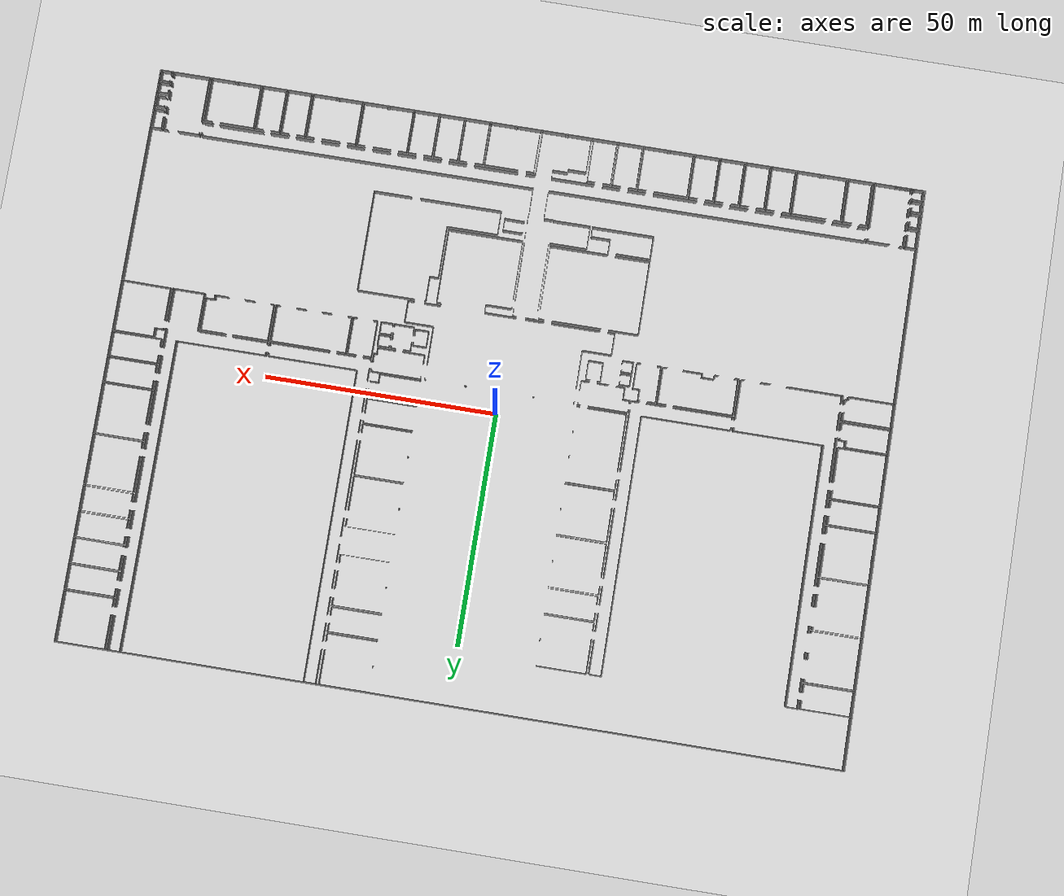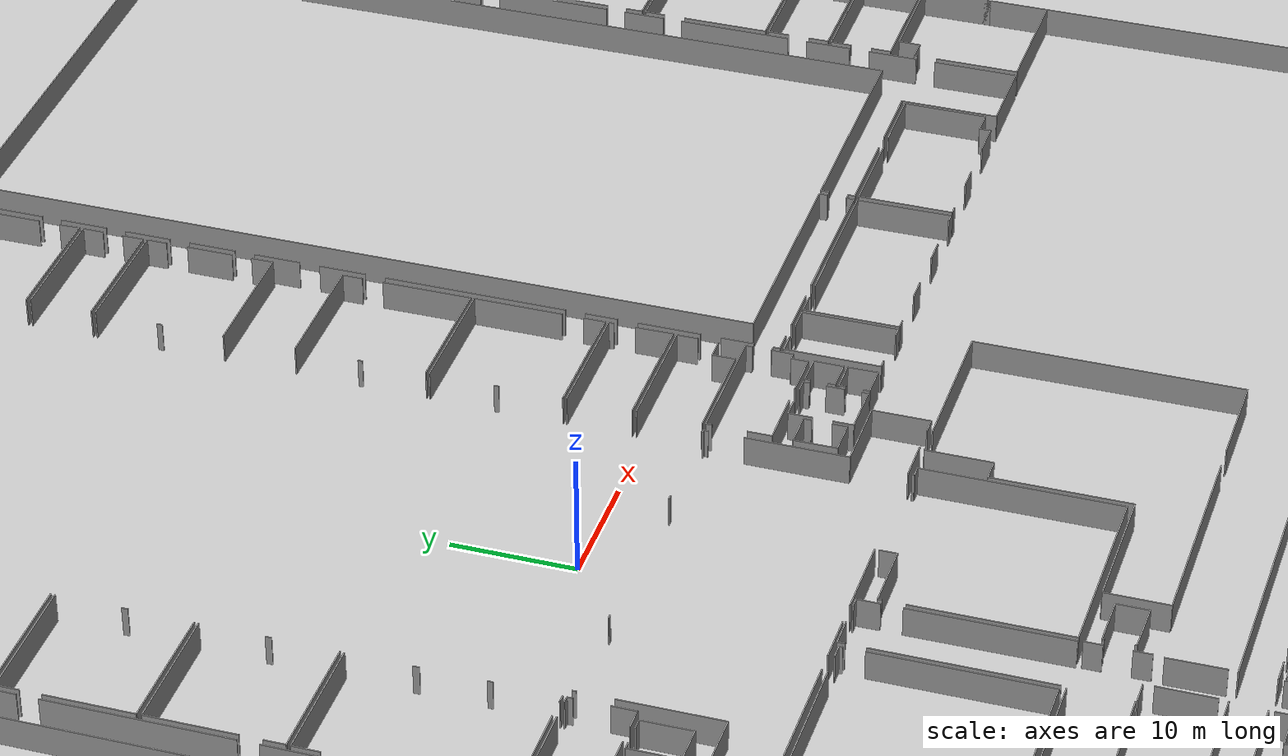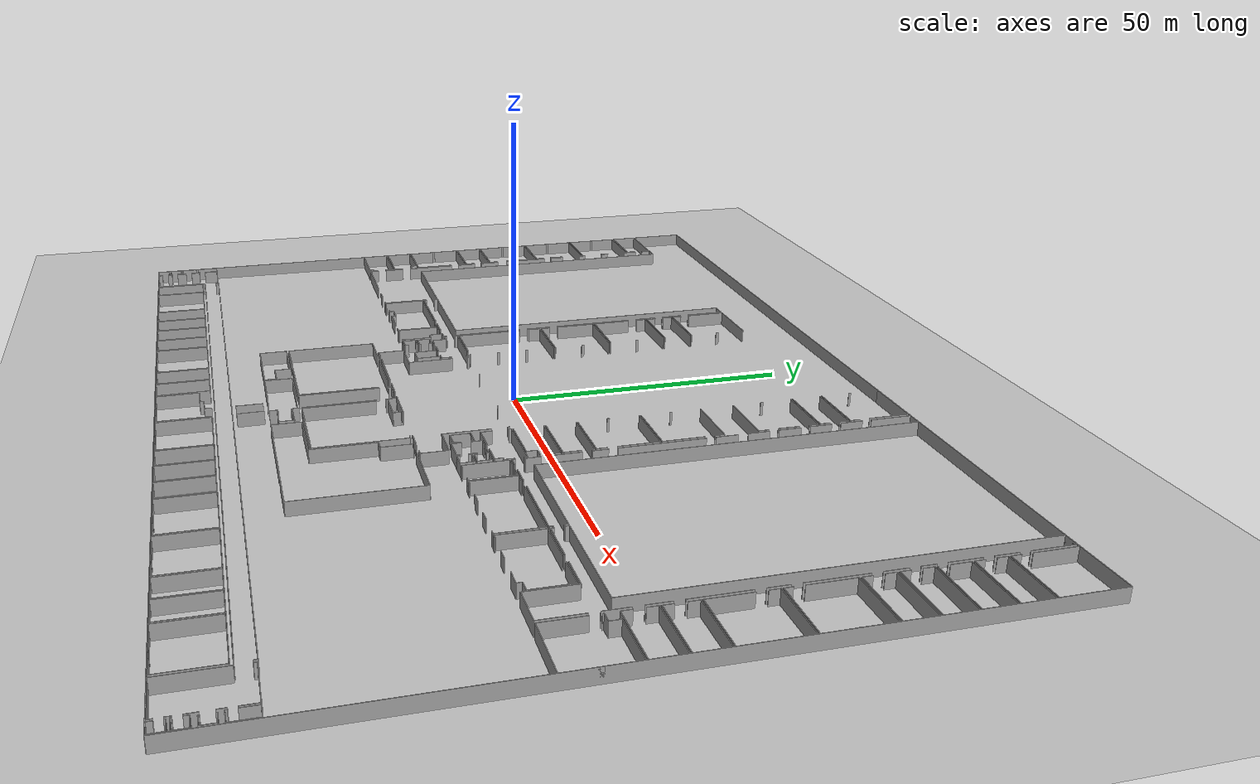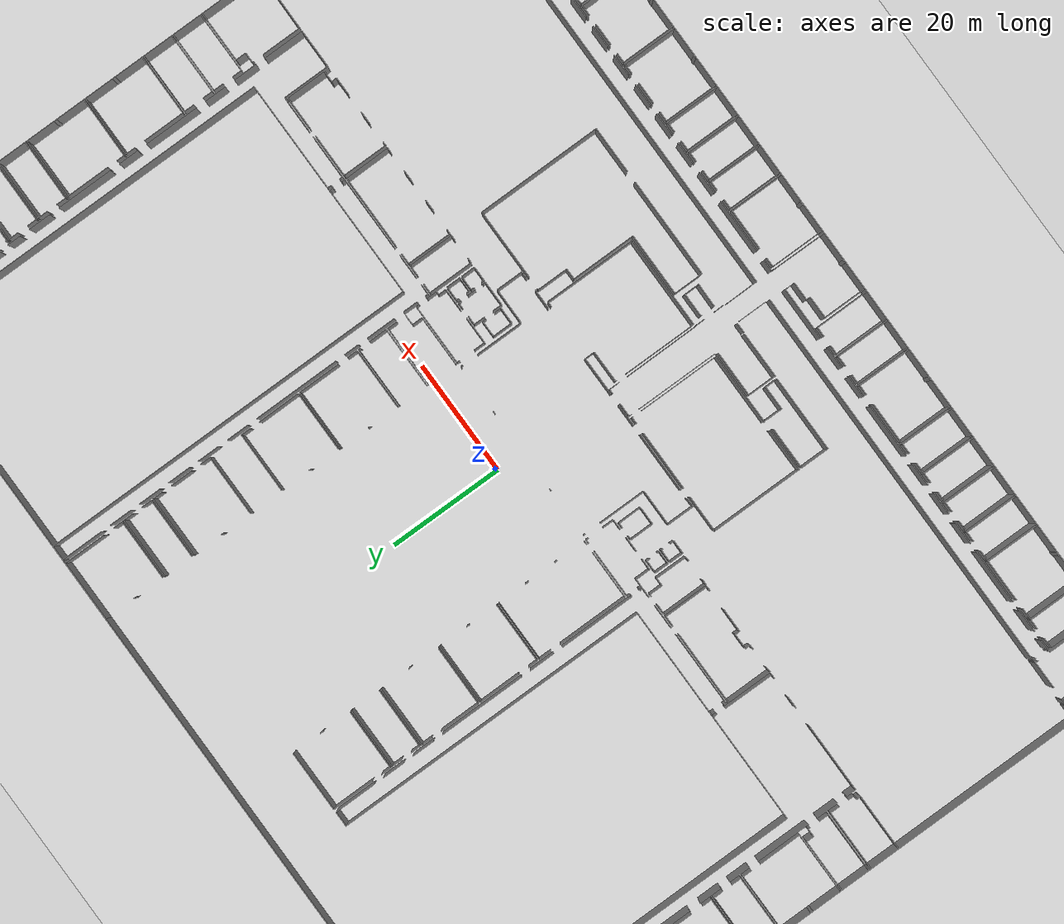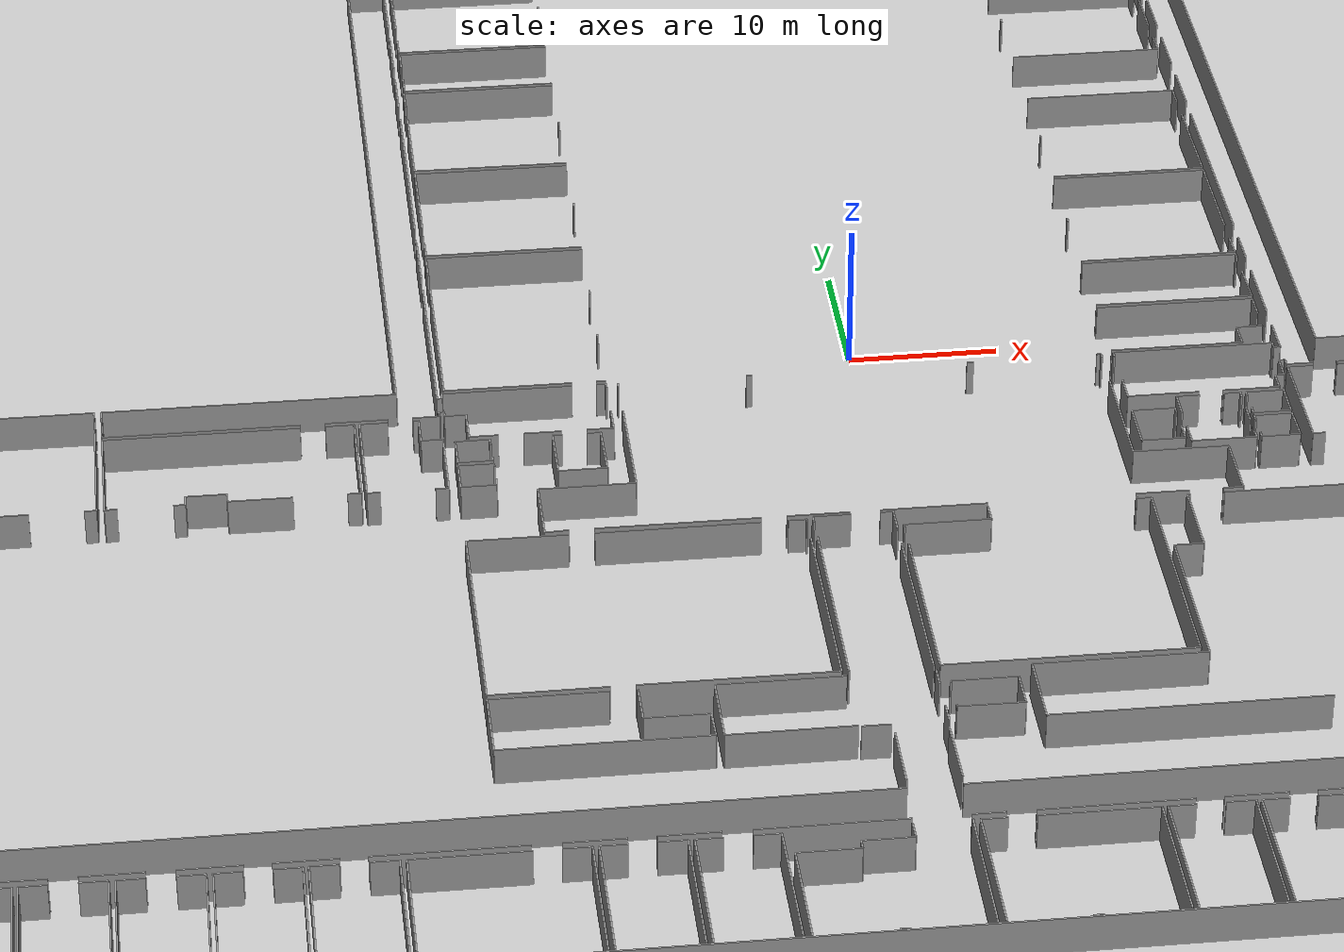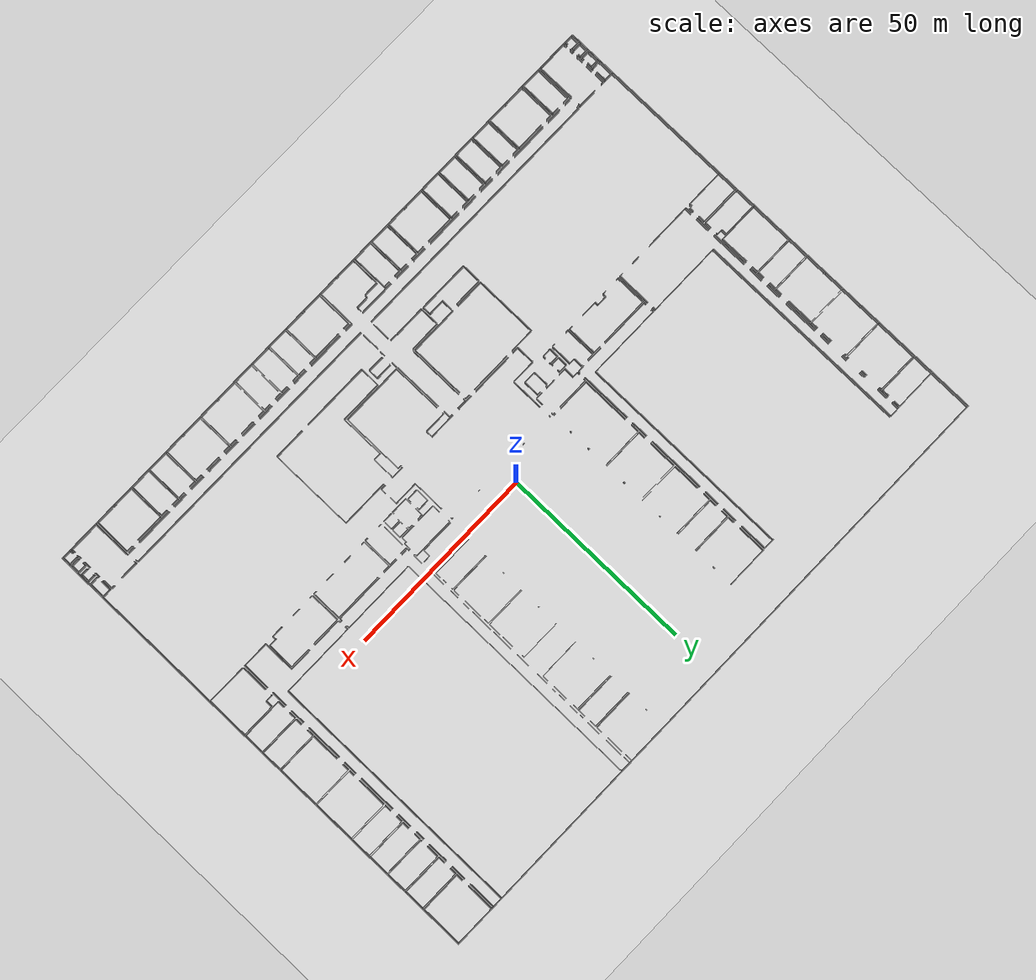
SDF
<sdf version="1.6">
  <world name="default">
    <light name="sun" type="directional">
      <cast_shadows>1</cast_shadows>
      <pose frame="">0 0 10 0 -0 0</pose>
      <diffuse>0.8 0.8 0.8 1</diffuse>
      <specular>0.1 0.1 0.1 1</specular>
      <attenuation>
        <range>1000</range>
        <constant>0.9</constant>
        <linear>0.01</linear>
        <quadratic>0.001</quadratic>
      </attenuation>
      <direction>-0.5 0.5 -1</direction>
    </light>
    <model name="ground_plane">
      <static>1</static>
      <link name="link">
        <collision name="collision">
          <geometry>
            <plane>
              <normal>0 0 1</normal>
              <size>100 100</size>
            </plane>
          </geometry>
          <surface>
            <friction>
              <ode>
                <mu>100</mu>
                <mu2>50</mu2>
              </ode>
              <torsional>
                <ode />
              </torsional>
            </friction>
            <contact>
              <ode />
            </contact>
            <bounce />
          </surface>
          <max_contacts>10</max_contacts>
        </collision>
        <visual name="visual">
          <cast_shadows>0</cast_shadows>
          <geometry>
            <plane>
              <normal>0 0 1</normal>
              <size>100 100</size>
            </plane>
          </geometry>
          <material>
            <script>
              <uri>file://media/materials/scripts/gazebo.material</uri>
              <name>Gazebo/Grey</name>
            </script>
          </material>
        </visual>
        <self_collide>0</self_collide>
        <kinematic>0</kinematic>
        <gravity>1</gravity>
      </link>
    </model>
    <gravity>0 0 -9.8</gravity>
    <magnetic_field>6e-06 2.3e-05 -4.2e-05</magnetic_field>
    <atmosphere type="adiabatic" />
    <physics default="0" name="default_physics" type="ode">
      <max_step_size>0.001</max_step_size>
      <real_time_factor>1</real_time_factor>
      <real_time_update_rate>1000</real_time_update_rate>
    </physics>
    <scene>
      <ambient>0.4 0.4 0.4 1</ambient>
      <background>0.7 0.7 0.7 1</background>
      <shadows>1</shadows>
    </scene>
    <spherical_coordinates>
      <surface_model>EARTH_WGS84</surface_model>
      <latitude_deg>0</latitude_deg>
      <longitude_deg>0</longitude_deg>
      <elevation>0</elevation>
      <heading_deg>0</heading_deg>
    </spherical_coordinates>
  <model name="0510045905_A_40_1_103">
		<static>1</static>
		<link name="Wall_0">
			<collision name="Wall_0_Collision">
				<geometry>
					<box>
						<size>0.769020894272 0.1 2.5</size>
					</box>
				</geometry>
				<pose frame="">0.384510447136 0 1.25 0 0 0</pose>
			</collision>
			<visual name="Wall_0_Visual">
				<pose frame="">0.384510447136 0 1.25 0 0 0</pose>
				<geometry>
					<box>
						<size>0.769020894272 0.1 2.5</size>
					</box>
				</geometry>
				<material>
					<script>
						<uri>file://media/materials/scripts/gazebo.material</uri>
						<name>Gazebo/Grey</name>
					</script>
					<ambient>1 1 1 1</ambient>
				</material>
			</visual>
			<pose frame="">33.1874393254 -78.0304943434 0 0 0 3.14159265359</pose>
		</link>
		<link name="Wall_1">
			<collision name="Wall_1_Collision">
				<geometry>
					<box>
						<size>2.03168721408 0.1 2.5</size>
					</box>
				</geometry>
				<pose frame="">1.01584360704 0 1.25 0 0 0</pose>
			</collision>
			<visual name="Wall_1_Visual">
				<pose frame="">1.01584360704 0 1.25 0 0 0</pose>
				<geometry>
					<box>
						<size>2.03168721408 0.1 2.5</size>
					</box>
				</geometry>
				<material>
					<script>
						<uri>file://media/materials/scripts/gazebo.material</uri>
						<name>Gazebo/Grey</name>
					</script>
					<ambient>1 1 1 1</ambient>
				</material>
			</visual>
			<pose frame="">28.8966580585 -78.0304943434 0 0 0 3.14159265359</pose>
		</link>
		<link name="Wall_2">
			<collision name="Wall_2_Collision">
				<geometry>
					<box>
						<size>12.0568770899 0.1 2.5</size>
					</box>
				</geometry>
				<pose frame="">6.02843854495 0 1.25 0 0 0</pose>
			</collision>
			<visual name="Wall_2_Visual">
				<pose frame="">6.02843854495 0 1.25 0 0 0</pose>
				<geometry>
					<box>
						<size>12.0568770899 0.1 2.5</size>
					</box>
				</geometry>
				<material>
					<script>
						<uri>file://media/materials/scripts/gazebo.material</uri>
						<name>Gazebo/Grey</name>
					</script>
					<ambient>1 1 1 1</ambient>
				</material>
			</visual>
			<pose frame="">23.3066629442 -78.0304943434 0 0 0 3.14159265359</pose>
		</link>
		<link name="Wall_3">
			<collision name="Wall_3_Collision">
				<geometry>
					<box>
						<size>1.73905319061 0.1 2.5</size>
					</box>
				</geometry>
				<pose frame="">0.869526595306 0 1.25 0 0 0</pose>
			</collision>
			<visual name="Wall_3_Visual">
				<pose frame="">0.869526595306 0 1.25 0 0 0</pose>
				<geometry>
					<box>
						<size>1.73905319061 0.1 2.5</size>
					</box>
				</geometry>
				<material>
					<script>
						<uri>file://media/materials/scripts/gazebo.material</uri>
						<name>Gazebo/Grey</name>
					</script>
					<ambient>1 1 1 1</ambient>
				</material>
			</visual>
			<pose frame="">11.2497858543 -78.0304943434 0 0 0 1.57079632679</pose>
		</link>
		<link name="Wall_4">
			<collision name="Wall_4_Collision">
				<geometry>
					<box>
						<size>3.87378412847 0.1 2.5</size>
					</box>
				</geometry>
				<pose frame="">1.93689206424 0 1.25 0 0 0</pose>
			</collision>
			<visual name="Wall_4_Visual">
				<pose frame="">1.93689206424 0 1.25 0 0 0</pose>
				<geometry>
					<box>
						<size>3.87378412847 0.1 2.5</size>
					</box>
				</geometry>
				<material>
					<script>
						<uri>file://media/materials/scripts/gazebo.material</uri>
						<name>Gazebo/Grey</name>
					</script>
					<ambient>1 1 1 1</ambient>
				</material>
			</visual>
			<pose frame="">11.2497858543 -74.5343680006 0 0 0 1.57079632679</pose>
		</link>
		<link name="Wall_5">
			<collision name="Wall_5_Collision">
				<geometry>
					<box>
						<size>9.61199977158 0.1 2.5</size>
					</box>
				</geometry>
				<pose frame="">4.80599988579 0 1.25 0 0 0</pose>
			</collision>
			<visual name="Wall_5_Visual">
				<pose frame="">4.80599988579 0 1.25 0 0 0</pose>
				<geometry>
					<box>
						<size>9.61199977158 0.1 2.5</size>
					</box>
				</geometry>
				<material>
					<script>
						<uri>file://media/materials/scripts/gazebo.material</uri>
						<name>Gazebo/Grey</name>
					</script>
					<ambient>1 1 1 1</ambient>
				</material>
			</visual>
			<pose frame="">11.2497858543 -68.9687379047 0 0 0 1.57079632679</pose>
		</link>
		<link name="Wall_6">
			<collision name="Wall_6_Collision">
				<geometry>
					<box>
						<size>3.78799895941 0.1 2.5</size>
					</box>
				</geometry>
				<pose frame="">1.89399947971 0 1.25 0 0 0</pose>
			</collision>
			<visual name="Wall_6_Visual">
				<pose frame="">1.89399947971 0 1.25 0 0 0</pose>
				<geometry>
					<box>
						<size>3.78799895941 0.1 2.5</size>
					</box>
				</geometry>
				<material>
					<script>
						<uri>file://media/materials/scripts/gazebo.material</uri>
						<name>Gazebo/Grey</name>
					</script>
					<ambient>1 1 1 1</ambient>
				</material>
			</visual>
			<pose frame="">11.2497858543 -57.6877343705 0 0 0 1.57079632679</pose>
		</link>
		<link name="Wall_7">
			<collision name="Wall_7_Collision">
				<geometry>
					<box>
						<size>3.93088964043 0.1 2.5</size>
					</box>
				</geometry>
				<pose frame="">1.96544482021 0 1.25 0 0 0</pose>
			</collision>
			<visual name="Wall_7_Visual">
				<pose frame="">1.96544482021 0 1.25 0 0 0</pose>
				<geometry>
					<box>
						<size>3.93088964043 0.1 2.5</size>
					</box>
				</geometry>
				<material>
					<script>
						<uri>file://media/materials/scripts/gazebo.material</uri>
						<name>Gazebo/Grey</name>
					</script>
					<ambient>1 1 1 1</ambient>
				</material>
			</visual>
			<pose frame="">11.2497858543 -52.2279398235 0 0 0 1.57079632679</pose>
		</link>
		<link name="Wall_8">
			<collision name="Wall_8_Collision">
				<geometry>
					<box>
						<size>9.1188619506 0.1 2.5</size>
					</box>
				</geometry>
				<pose frame="">4.5594309753 0 1.25 0 0 0</pose>
			</collision>
			<visual name="Wall_8_Visual">
				<pose frame="">4.5594309753 0 1.25 0 0 0</pose>
				<geometry>
					<box>
						<size>9.1188619506 0.1 2.5</size>
					</box>
				</geometry>
				<material>
					<script>
						<uri>file://media/materials/scripts/gazebo.material</uri>
						<name>Gazebo/Grey</name>
					</script>
					<ambient>1 1 1 1</ambient>
				</material>
			</visual>
			<pose frame="">11.2497858543 -46.2648553644 0 0 0 1.57079632679</pose>
		</link>
		<link name="Wall_9">
			<collision name="Wall_9_Collision">
				<geometry>
					<box>
						<size>2.70603985965 0.1 2.5</size>
					</box>
				</geometry>
				<pose frame="">1.35301992982 0 1.25 0 0 0</pose>
			</collision>
			<visual name="Wall_9_Visual">
				<pose frame="">1.35301992982 0 1.25 0 0 0</pose>
				<geometry>
					<box>
						<size>2.70603985965 0.1 2.5</size>
					</box>
				</geometry>
				<material>
					<script>
						<uri>file://media/materials/scripts/gazebo.material</uri>
						<name>Gazebo/Grey</name>
					</script>
					<ambient>1 1 1 1</ambient>
				</material>
			</visual>
			<pose frame="">11.2497858543 -35.4412035304 0 0 0 1.57079632679</pose>
		</link>
		<link name="Wall_10">
			<collision name="Wall_10_Collision">
				<geometry>
					<box>
						<size>1.51418437466 0.1 2.5</size>
					</box>
				</geometry>
				<pose frame="">0.757092187331 0 1.25 0 0 0</pose>
			</collision>
			<visual name="Wall_10_Visual">
				<pose frame="">0.757092187331 0 1.25 0 0 0</pose>
				<geometry>
					<box>
						<size>1.51418437466 0.1 2.5</size>
					</box>
				</geometry>
				<material>
					<script>
						<uri>file://media/materials/scripts/gazebo.material</uri>
						<name>Gazebo/Grey</name>
					</script>
					<ambient>1 1 1 1</ambient>
				</material>
			</visual>
			<pose frame="">11.2497858543 -28.653769281 0 0 0 1.57079632679</pose>
		</link>
		<link name="Wall_11">
			<collision name="Wall_11_Collision">
				<geometry>
					<box>
						<size>1.55276232051 0.1 2.5</size>
					</box>
				</geometry>
				<pose frame="">0.776381160257 0 1.25 0 0 0</pose>
			</collision>
			<visual name="Wall_11_Visual">
				<pose frame="">0.776381160257 0 1.25 0 0 0</pose>
				<geometry>
					<box>
						<size>1.55276232051 0.1 2.5</size>
					</box>
				</geometry>
				<material>
					<script>
						<uri>file://media/materials/scripts/gazebo.material</uri>
						<name>Gazebo/Grey</name>
					</script>
					<ambient>1 1 1 1</ambient>
				</material>
			</visual>
			<pose frame="">11.2497858543 -23.0909310102 0 0 0 1.57079632679</pose>
		</link>
		<link name="Wall_12">
			<collision name="Wall_12_Collision">
				<geometry>
					<box>
						<size>2.8588288294 0.1 2.5</size>
					</box>
				</geometry>
				<pose frame="">1.4294144147 0 1.25 0 0 0</pose>
			</collision>
			<visual name="Wall_12_Visual">
				<pose frame="">1.4294144147 0 1.25 0 0 0</pose>
				<geometry>
					<box>
						<size>2.8588288294 0.1 2.5</size>
					</box>
				</geometry>
				<material>
					<script>
						<uri>file://media/materials/scripts/gazebo.material</uri>
						<name>Gazebo/Grey</name>
					</script>
					<ambient>1 1 1 1</ambient>
				</material>
			</visual>
			<pose frame="">11.2497858543 -17.5187020552 0 0 0 1.57079632679</pose>
		</link>
		<link name="Wall_13">
			<collision name="Wall_13_Collision">
				<geometry>
					<box>
						<size>1.88575090576 0.1 2.5</size>
					</box>
				</geometry>
				<pose frame="">0.942875452878 0 1.25 0 0 0</pose>
			</collision>
			<visual name="Wall_13_Visual">
				<pose frame="">0.942875452878 0 1.25 0 0 0</pose>
				<geometry>
					<box>
						<size>1.88575090576 0.1 2.5</size>
					</box>
				</geometry>
				<material>
					<script>
						<uri>file://media/materials/scripts/gazebo.material</uri>
						<name>Gazebo/Grey</name>
					</script>
					<ambient>1 1 1 1</ambient>
				</material>
			</visual>
			<pose frame="">11.2497858543 -13.0309702226 0 0 0 1.57079632679</pose>
		</link>
		<link name="Wall_14">
			<collision name="Wall_14_Collision">
				<geometry>
					<box>
						<size>2.6314219907 0.1 2.5</size>
					</box>
				</geometry>
				<pose frame="">1.31571099535 0 1.25 0 0 0</pose>
			</collision>
			<visual name="Wall_14_Visual">
				<pose frame="">1.31571099535 0 1.25 0 0 0</pose>
				<geometry>
					<box>
						<size>2.6314219907 0.1 2.5</size>
					</box>
				</geometry>
				<material>
					<script>
						<uri>file://media/materials/scripts/gazebo.material</uri>
						<name>Gazebo/Grey</name>
					</script>
					<ambient>1 1 1 1</ambient>
				</material>
			</visual>
			<pose frame="">11.2497858543 -11.1452193169 0 0 0 0.0</pose>
		</link>
		<link name="Wall_15">
			<collision name="Wall_15_Collision">
				<geometry>
					<box>
						<size>55.7222895503 0.1 2.5</size>
					</box>
				</geometry>
				<pose frame="">27.8611447752 0 1.25 0 0 0</pose>
			</collision>
			<visual name="Wall_15_Visual">
				<pose frame="">27.8611447752 0 1.25 0 0 0</pose>
				<geometry>
					<box>
						<size>55.7222895503 0.1 2.5</size>
					</box>
				</geometry>
				<material>
					<script>
						<uri>file://media/materials/scripts/gazebo.material</uri>
						<name>Gazebo/Grey</name>
					</script>
					<ambient>1 1 1 1</ambient>
				</material>
			</visual>
			<pose frame="">13.881207845 -11.1452193169 0 0 0 -1.57079632679</pose>
		</link>
		<link name="Wall_16">
			<collision name="Wall_16_Collision">
				<geometry>
					<box>
						<size>19.350139274 0.1 2.5</size>
					</box>
				</geometry>
				<pose frame="">9.675069637 0 1.25 0 0 0</pose>
			</collision>
			<visual name="Wall_16_Visual">
				<pose frame="">9.675069637 0 1.25 0 0 0</pose>
				<geometry>
					<box>
						<size>19.350139274 0.1 2.5</size>
					</box>
				</geometry>
				<material>
					<script>
						<uri>file://media/materials/scripts/gazebo.material</uri>
						<name>Gazebo/Grey</name>
					</script>
					<ambient>1 1 1 1</ambient>
				</material>
			</visual>
			<pose frame="">13.881207845 -66.8675088672 0 0 0 0.0</pose>
		</link>
		<link name="Wall_17">
			<collision name="Wall_17_Collision">
				<geometry>
					<box>
						<size>0.743894469014 0.1 2.5</size>
					</box>
				</geometry>
				<pose frame="">0.371947234507 0 1.25 0 0 0</pose>
			</collision>
			<visual name="Wall_17_Visual">
				<pose frame="">0.371947234507 0 1.25 0 0 0</pose>
				<geometry>
					<box>
						<size>0.743894469014 0.1 2.5</size>
					</box>
				</geometry>
				<material>
					<script>
						<uri>file://media/materials/scripts/gazebo.material</uri>
						<name>Gazebo/Grey</name>
					</script>
					<ambient>1 1 1 1</ambient>
				</material>
			</visual>
			<pose frame="">33.231347119 -66.8675088672 0 0 0 -1.57079632679</pose>
		</link>
		<link name="Wall_18">
			<collision name="Wall_18_Collision">
				<geometry>
					<box>
						<size>8.82354534993 0.1 2.5</size>
					</box>
				</geometry>
				<pose frame="">4.41177267496 0 1.25 0 0 0</pose>
			</collision>
			<visual name="Wall_18_Visual">
				<pose frame="">4.41177267496 0 1.25 0 0 0</pose>
				<geometry>
					<box>
						<size>8.82354534993 0.1 2.5</size>
					</box>
				</geometry>
				<material>
					<script>
						<uri>file://media/materials/scripts/gazebo.material</uri>
						<name>Gazebo/Grey</name>
					</script>
					<ambient>1 1 1 1</ambient>
				</material>
			</visual>
			<pose frame="">33.231347119 -69.2070582413 0 0 0 -1.57577255496</pose>
		</link>
		<link name="Wall_19">
			<collision name="Wall_19_Collision">
				<geometry>
					<box>
						<size>10.842940807 0.1 2.5</size>
					</box>
				</geometry>
				<pose frame="">5.42147040348 0 1.25 0 0 0</pose>
			</collision>
			<visual name="Wall_19_Visual">
				<pose frame="">5.42147040348 0 1.25 0 0 0</pose>
				<geometry>
					<box>
						<size>10.842940807 0.1 2.5</size>
					</box>
				</geometry>
				<material>
					<script>
						<uri>file://media/materials/scripts/gazebo.material</uri>
						<name>Gazebo/Grey</name>
					</script>
					<ambient>1 1 1 1</ambient>
				</material>
			</visual>
			<pose frame="">10.842940807 -16.4996859197 0 0 0 3.14159265359</pose>
		</link>
		<link name="Wall_20">
			<collision name="Wall_20_Collision">
				<geometry>
					<box>
						<size>10.8599455594 0.1 2.5</size>
					</box>
				</geometry>
				<pose frame="">5.42997277971 0 1.25 0 0 0</pose>
			</collision>
			<visual name="Wall_20_Visual">
				<pose frame="">5.42997277971 0 1.25 0 0 0</pose>
				<geometry>
					<box>
						<size>10.8599455594 0.1 2.5</size>
					</box>
				</geometry>
				<material>
					<script>
						<uri>file://media/materials/scripts/gazebo.material</uri>
						<name>Gazebo/Grey</name>
					</script>
					<ambient>1 1 1 1</ambient>
				</material>
			</visual>
			<pose frame="">0.0 -11.2028324334 0 0 0 0.0</pose>
		</link>
		<link name="Wall_21">
			<collision name="Wall_21_Collision">
				<geometry>
					<box>
						<size>1.79742771394 0.1 2.5</size>
					</box>
				</geometry>
				<pose frame="">0.89871385697 0 1.25 0 0 0</pose>
			</collision>
			<visual name="Wall_21_Visual">
				<pose frame="">0.89871385697 0 1.25 0 0 0</pose>
				<geometry>
					<box>
						<size>1.79742771394 0.1 2.5</size>
					</box>
				</geometry>
				<material>
					<script>
						<uri>file://media/materials/scripts/gazebo.material</uri>
						<name>Gazebo/Grey</name>
					</script>
					<ambient>1 1 1 1</ambient>
				</material>
			</visual>
			<pose frame="">10.8599455594 -11.2028324334 0 0 0 -1.57079632679</pose>
		</link>
		<link name="Wall_22">
			<collision name="Wall_22_Collision">
				<geometry>
					<box>
						<size>1.80410671471 0.1 2.5</size>
					</box>
				</geometry>
				<pose frame="">0.902053357353 0 1.25 0 0 0</pose>
			</collision>
			<visual name="Wall_22_Visual">
				<pose frame="">0.902053357353 0 1.25 0 0 0</pose>
				<geometry>
					<box>
						<size>1.80410671471 0.1 2.5</size>
					</box>
				</geometry>
				<material>
					<script>
						<uri>file://media/materials/scripts/gazebo.material</uri>
						<name>Gazebo/Grey</name>
					</script>
					<ambient>1 1 1 1</ambient>
				</material>
			</visual>
			<pose frame="">10.8599455594 -14.6956593466 0 0 0 -1.58022204652</pose>
		</link>
		<link name="Wall_23">
			<collision name="Wall_23_Collision">
				<geometry>
					<box>
						<size>10.8472554456 0.1 2.5</size>
					</box>
				</geometry>
				<pose frame="">5.42362772282 0 1.25 0 0 0</pose>
			</collision>
			<visual name="Wall_23_Visual">
				<pose frame="">5.42362772282 0 1.25 0 0 0</pose>
				<geometry>
					<box>
						<size>10.8472554456 0.1 2.5</size>
					</box>
				</geometry>
				<material>
					<script>
						<uri>file://media/materials/scripts/gazebo.material</uri>
						<name>Gazebo/Grey</name>
					</script>
					<ambient>1 1 1 1</ambient>
				</material>
			</visual>
			<pose frame="">10.8622297799 -27.6304385069 0 0 0 3.14159265359</pose>
		</link>
		<link name="Wall_24">
			<collision name="Wall_24_Collision">
				<geometry>
					<box>
						<size>0.522325082644 0.1 2.5</size>
					</box>
				</geometry>
				<pose frame="">0.261162541322 0 1.25 0 0 0</pose>
			</collision>
			<visual name="Wall_24_Visual">
				<pose frame="">0.261162541322 0 1.25 0 0 0</pose>
				<geometry>
					<box>
						<size>0.522325082644 0.1 2.5</size>
					</box>
				</geometry>
				<material>
					<script>
						<uri>file://media/materials/scripts/gazebo.material</uri>
						<name>Gazebo/Grey</name>
					</script>
					<ambient>1 1 1 1</ambient>
				</material>
			</visual>
			<pose frame="">0.0149743342449 -22.5104852065 0 0 0 1.57079632679</pose>
		</link>
		<link name="Wall_25">
			<collision name="Wall_25_Collision">
				<geometry>
					<box>
						<size>10.8233980318 0.1 2.5</size>
					</box>
				</geometry>
				<pose frame="">5.41169901588 0 1.25 0 0 0</pose>
			</collision>
			<visual name="Wall_25_Visual">
				<pose frame="">5.41169901588 0 1.25 0 0 0</pose>
				<geometry>
					<box>
						<size>10.8233980318 0.1 2.5</size>
					</box>
				</geometry>
				<material>
					<script>
						<uri>file://media/materials/scripts/gazebo.material</uri>
						<name>Gazebo/Grey</name>
					</script>
					<ambient>1 1 1 1</ambient>
				</material>
			</visual>
			<pose frame="">0.0149743342449 -16.8316592958 0 0 0 0.0</pose>
		</link>
		<link name="Wall_26">
			<collision name="Wall_26_Collision">
				<geometry>
					<box>
						<size>0.663439147732 0.1 2.5</size>
					</box>
				</geometry>
				<pose frame="">0.331719573866 0 1.25 0 0 0</pose>
			</collision>
			<visual name="Wall_26_Visual">
				<pose frame="">0.331719573866 0 1.25 0 0 0</pose>
				<geometry>
					<box>
						<size>0.663439147732 0.1 2.5</size>
					</box>
				</geometry>
				<material>
					<script>
						<uri>file://media/materials/scripts/gazebo.material</uri>
						<name>Gazebo/Grey</name>
					</script>
					<ambient>1 1 1 1</ambient>
				</material>
			</visual>
			<pose frame="">10.838372366 -16.8316592958 0 0 0 -1.57079632679</pose>
		</link>
		<link name="Wall_27">
			<collision name="Wall_27_Collision">
				<geometry>
					<box>
						<size>1.46367772187 0.1 2.5</size>
					</box>
				</geometry>
				<pose frame="">0.731838860935 0 1.25 0 0 0</pose>
			</collision>
			<visual name="Wall_27_Visual">
				<pose frame="">0.731838860935 0 1.25 0 0 0</pose>
				<geometry>
					<box>
						<size>1.46367772187 0.1 2.5</size>
					</box>
				</geometry>
				<material>
					<script>
						<uri>file://media/materials/scripts/gazebo.material</uri>
						<name>Gazebo/Grey</name>
					</script>
					<ambient>1 1 1 1</ambient>
				</material>
			</visual>
			<pose frame="">10.838372366 -21.5874063311 0 0 0 -1.57079632679</pose>
		</link>
		<link name="Wall_28">
			<collision name="Wall_28_Collision">
				<geometry>
					<box>
						<size>0.448849305995 0.1 2.5</size>
					</box>
				</geometry>
				<pose frame="">0.224424652998 0 1.25 0 0 0</pose>
			</collision>
			<visual name="Wall_28_Visual">
				<pose frame="">0.224424652998 0 1.25 0 0 0</pose>
				<geometry>
					<box>
						<size>0.448849305995 0.1 2.5</size>
					</box>
				</geometry>
				<material>
					<script>
						<uri>file://media/materials/scripts/gazebo.material</uri>
						<name>Gazebo/Grey</name>
					</script>
					<ambient>1 1 1 1</ambient>
				</material>
			</visual>
			<pose frame="">10.838372366 -27.1822236886 0 0 0 -1.51761887629</pose>
		</link>
		<link name="Wall_29">
			<collision name="Wall_29_Collision">
				<geometry>
					<box>
						<size>10.6802535485 0.1 2.5</size>
					</box>
				</geometry>
				<pose frame="">5.34012677424 0 1.25 0 0 0</pose>
			</collision>
			<visual name="Wall_29_Visual">
				<pose frame="">5.34012677424 0 1.25 0 0 0</pose>
				<geometry>
					<box>
						<size>10.6802535485 0.1 2.5</size>
					</box>
				</geometry>
				<material>
					<script>
						<uri>file://media/materials/scripts/gazebo.material</uri>
						<name>Gazebo/Grey</name>
					</script>
					<ambient>1 1 1 1</ambient>
				</material>
			</visual>
			<pose frame="">10.7104560192 -38.8804781635 0 0 0 3.14159265359</pose>
		</link>
		<link name="Wall_30">
			<collision name="Wall_30_Collision">
				<geometry>
					<box>
						<size>0.500751889241 0.1 2.5</size>
					</box>
				</geometry>
				<pose frame="">0.25037594462 0 1.25 0 0 0</pose>
			</collision>
			<visual name="Wall_30_Visual">
				<pose frame="">0.25037594462 0 1.25 0 0 0</pose>
				<geometry>
					<box>
						<size>0.500751889241 0.1 2.5</size>
					</box>
				</geometry>
				<material>
					<script>
						<uri>file://media/materials/scripts/gazebo.material</uri>
						<name>Gazebo/Grey</name>
					</script>
					<ambient>1 1 1 1</ambient>
				</material>
			</visual>
			<pose frame="">0.0302024707652 -33.6739782872 0 0 0 1.57079632679</pose>
		</link>
		<link name="Wall_31">
			<collision name="Wall_31_Collision">
				<geometry>
					<box>
						<size>10.6635025983 0.1 2.5</size>
					</box>
				</geometry>
				<pose frame="">5.33175129915 0 1.25 0 0 0</pose>
			</collision>
			<visual name="Wall_31_Visual">
				<pose frame="">5.33175129915 0 1.25 0 0 0</pose>
				<geometry>
					<box>
						<size>10.6635025983 0.1 2.5</size>
					</box>
				</geometry>
				<material>
					<script>
						<uri>file://media/materials/scripts/gazebo.material</uri>
						<name>Gazebo/Grey</name>
					</script>
					<ambient>1 1 1 1</ambient>
				</material>
			</visual>
			<pose frame="">0.0302024707652 -27.9834774719 0 0 0 0.0</pose>
		</link>
		<link name="Wall_32">
			<collision name="Wall_32_Collision">
				<geometry>
					<box>
						<size>0.606587438056 0.1 2.5</size>
					</box>
				</geometry>
				<pose frame="">0.303293719028 0 1.25 0 0 0</pose>
			</collision>
			<visual name="Wall_32_Visual">
				<pose frame="">0.303293719028 0 1.25 0 0 0</pose>
				<geometry>
					<box>
						<size>0.606587438056 0.1 2.5</size>
					</box>
				</geometry>
				<material>
					<script>
						<uri>file://media/materials/scripts/gazebo.material</uri>
						<name>Gazebo/Grey</name>
					</script>
					<ambient>1 1 1 1</ambient>
				</material>
			</visual>
			<pose frame="">10.6937050691 -27.9834774719 0 0 0 -1.57079632679</pose>
		</link>
		<link name="Wall_33">
			<collision name="Wall_33_Collision">
				<geometry>
					<box>
						<size>2.68776609582 0.1 2.5</size>
					</box>
				</geometry>
				<pose frame="">1.34388304791 0 1.25 0 0 0</pose>
			</collision>
			<visual name="Wall_33_Visual">
				<pose frame="">1.34388304791 0 1.25 0 0 0</pose>
				<geometry>
					<box>
						<size>2.68776609582 0.1 2.5</size>
					</box>
				</geometry>
				<material>
					<script>
						<uri>file://media/materials/scripts/gazebo.material</uri>
						<name>Gazebo/Grey</name>
					</script>
					<ambient>1 1 1 1</ambient>
				</material>
			</visual>
			<pose frame="">10.6937050691 -32.7547064459 0 0 0 -1.57079632679</pose>
		</link>
		<link name="Wall_34">
			<collision name="Wall_34_Collision">
				<geometry>
					<box>
						<size>1.75233097392 0.1 2.5</size>
					</box>
				</geometry>
				<pose frame="">0.876165486962 0 1.25 0 0 0</pose>
			</collision>
			<visual name="Wall_34_Visual">
				<pose frame="">0.876165486962 0 1.25 0 0 0</pose>
				<geometry>
					<box>
						<size>1.75233097392 0.1 2.5</size>
					</box>
				</geometry>
				<material>
					<script>
						<uri>file://media/materials/scripts/gazebo.material</uri>
						<name>Gazebo/Grey</name>
					</script>
					<ambient>1 1 1 1</ambient>
				</material>
			</visual>
			<pose frame="">10.6937050691 -37.1282272546 0 0 0 -1.56123694244</pose>
		</link>
		<link name="Wall_35">
			<collision name="Wall_35_Collision">
				<geometry>
					<box>
						<size>10.6388837776 0.1 2.5</size>
					</box>
				</geometry>
				<pose frame="">5.3194418888 0 1.25 0 0 0</pose>
			</collision>
			<visual name="Wall_35_Visual">
				<pose frame="">5.3194418888 0 1.25 0 0 0</pose>
				<geometry>
					<box>
						<size>10.6388837776 0.1 2.5</size>
					</box>
				</geometry>
				<material>
					<script>
						<uri>file://media/materials/scripts/gazebo.material</uri>
						<name>Gazebo/Grey</name>
					</script>
					<ambient>1 1 1 1</ambient>
				</material>
			</visual>
			<pose frame="">10.6896442327 -50.0647830308 0 0 0 3.14159265359</pose>
		</link>
		<link name="Wall_36">
			<collision name="Wall_36_Collision">
				<geometry>
					<box>
						<size>0.479432498112 0.1 2.5</size>
					</box>
				</geometry>
				<pose frame="">0.239716249056 0 1.25 0 0 0</pose>
			</collision>
			<visual name="Wall_36_Visual">
				<pose frame="">0.239716249056 0 1.25 0 0 0</pose>
				<geometry>
					<box>
						<size>0.479432498112 0.1 2.5</size>
					</box>
				</geometry>
				<material>
					<script>
						<uri>file://media/materials/scripts/gazebo.material</uri>
						<name>Gazebo/Grey</name>
					</script>
					<ambient>1 1 1 1</ambient>
				</material>
			</visual>
			<pose frame="">0.0507604550675 -44.8811253593 0 0 0 1.57079632679</pose>
		</link>
		<link name="Wall_37">
			<collision name="Wall_37_Collision">
				<geometry>
					<box>
						<size>10.6373609639 0.1 2.5</size>
					</box>
				</geometry>
				<pose frame="">5.31868048197 0 1.25 0 0 0</pose>
			</collision>
			<visual name="Wall_37_Visual">
				<pose frame="">5.31868048197 0 1.25 0 0 0</pose>
				<geometry>
					<box>
						<size>10.6373609639 0.1 2.5</size>
					</box>
				</geometry>
				<material>
					<script>
						<uri>file://media/materials/scripts/gazebo.material</uri>
						<name>Gazebo/Grey</name>
					</script>
					<ambient>1 1 1 1</ambient>
				</material>
			</visual>
			<pose frame="">0.0507604550675 -39.2028070532 0 0 0 0.0</pose>
		</link>
		<link name="Wall_38">
			<collision name="Wall_38_Collision">
				<geometry>
					<box>
						<size>7.03336865415 0.1 2.5</size>
					</box>
				</geometry>
				<pose frame="">3.51668432707 0 1.25 0 0 0</pose>
			</collision>
			<visual name="Wall_38_Visual">
				<pose frame="">3.51668432707 0 1.25 0 0 0</pose>
				<geometry>
					<box>
						<size>7.03336865415 0.1 2.5</size>
					</box>
				</geometry>
				<material>
					<script>
						<uri>file://media/materials/scripts/gazebo.material</uri>
						<name>Gazebo/Grey</name>
					</script>
					<ambient>1 1 1 1</ambient>
				</material>
			</visual>
			<pose frame="">10.688121419 -39.2028070532 0 0 0 -1.57079632679</pose>
		</link>
		<link name="Wall_39">
			<collision name="Wall_39_Collision">
				<geometry>
					<box>
						<size>1.69539988315 0.1 2.5</size>
					</box>
				</geometry>
				<pose frame="">0.847699941576 0 1.25 0 0 0</pose>
			</collision>
			<visual name="Wall_39_Visual">
				<pose frame="">0.847699941576 0 1.25 0 0 0</pose>
				<geometry>
					<box>
						<size>1.69539988315 0.1 2.5</size>
					</box>
				</geometry>
				<material>
					<script>
						<uri>file://media/materials/scripts/gazebo.material</uri>
						<name>Gazebo/Grey</name>
					</script>
					<ambient>1 1 1 1</ambient>
				</material>
			</visual>
			<pose frame="">10.688121419 -48.3693838315 0 0 0 -1.56989812344</pose>
		</link>
		<link name="Wall_40">
			<collision name="Wall_40_Collision">
				<geometry>
					<box>
						<size>10.5934531703 0.1 2.5</size>
					</box>
				</geometry>
				<pose frame="">5.29672658515 0 1.25 0 0 0</pose>
			</collision>
			<visual name="Wall_40_Visual">
				<pose frame="">5.29672658515 0 1.25 0 0 0</pose>
				<geometry>
					<box>
						<size>10.5934531703 0.1 2.5</size>
					</box>
				</geometry>
				<material>
					<script>
						<uri>file://media/materials/scripts/gazebo.material</uri>
						<name>Gazebo/Grey</name>
					</script>
					<ambient>1 1 1 1</ambient>
				</material>
			</visual>
			<pose frame="">10.6703552597 -55.668483468 0 0 0 3.14159265359</pose>
		</link>
		<link name="Wall_41">
			<collision name="Wall_41_Collision">
				<geometry>
					<box>
						<size>10.5888847294 0.1 2.5</size>
					</box>
				</geometry>
				<pose frame="">5.29444236468 0 1.25 0 0 0</pose>
			</collision>
			<visual name="Wall_41_Visual">
				<pose frame="">5.29444236468 0 1.25 0 0 0</pose>
				<geometry>
					<box>
						<size>10.5888847294 0.1 2.5</size>
					</box>
				</geometry>
				<material>
					<script>
						<uri>file://media/materials/scripts/gazebo.material</uri>
						<name>Gazebo/Grey</name>
					</script>
					<ambient>1 1 1 1</ambient>
				</material>
			</visual>
			<pose frame="">0.0769020894272 -50.3911727569 0 0 0 0.0</pose>
		</link>
		<link name="Wall_42">
			<collision name="Wall_42_Collision">
				<geometry>
					<box>
						<size>1.82737638243 0.1 2.5</size>
					</box>
				</geometry>
				<pose frame="">0.913688191215 0 1.25 0 0 0</pose>
			</collision>
			<visual name="Wall_42_Visual">
				<pose frame="">0.913688191215 0 1.25 0 0 0</pose>
				<geometry>
					<box>
						<size>1.82737638243 0.1 2.5</size>
					</box>
				</geometry>
				<material>
					<script>
						<uri>file://media/materials/scripts/gazebo.material</uri>
						<name>Gazebo/Grey</name>
					</script>
					<ambient>1 1 1 1</ambient>
				</material>
			</visual>
			<pose frame="">10.6657868188 -50.3911727569 0 0 0 -1.57079632679</pose>
		</link>
		<link name="Wall_43">
			<collision name="Wall_43_Collision">
				<geometry>
					<box>
						<size>1.71647086764 0.1 2.5</size>
					</box>
				</geometry>
				<pose frame="">0.858235433821 0 1.25 0 0 0</pose>
			</collision>
			<visual name="Wall_43_Visual">
				<pose frame="">0.858235433821 0 1.25 0 0 0</pose>
				<geometry>
					<box>
						<size>1.71647086764 0.1 2.5</size>
					</box>
				</geometry>
				<material>
					<script>
						<uri>file://media/materials/scripts/gazebo.material</uri>
						<name>Gazebo/Grey</name>
					</script>
					<ambient>1 1 1 1</ambient>
				</material>
			</visual>
			<pose frame="">10.6657868188 -53.9520186798 0 0 0 -1.56813479234</pose>
		</link>
		<link name="Wall_44">
			<collision name="Wall_44_Collision">
				<geometry>
					<box>
						<size>10.7010653351 0.1 2.5</size>
					</box>
				</geometry>
				<pose frame="">5.35053266753 0 1.25 0 0 0</pose>
			</collision>
			<visual name="Wall_44_Visual">
				<pose frame="">5.35053266753 0 1.25 0 0 0</pose>
				<geometry>
					<box>
						<size>10.7010653351 0.1 2.5</size>
					</box>
				</geometry>
				<material>
					<script>
						<uri>file://media/materials/scripts/gazebo.material</uri>
						<name>Gazebo/Grey</name>
					</script>
					<ambient>1 1 1 1</ambient>
				</material>
			</visual>
			<pose frame="">10.7312678058 -66.9271524019 0 0 0 3.14159265359</pose>
		</link>
		<link name="Wall_45">
			<collision name="Wall_45_Collision">
				<geometry>
					<box>
						<size>0.467249988896 0.1 2.5</size>
					</box>
				</geometry>
				<pose frame="">0.233624994448 0 1.25 0 0 0</pose>
			</collision>
			<visual name="Wall_45_Visual">
				<pose frame="">0.233624994448 0 1.25 0 0 0</pose>
				<geometry>
					<box>
						<size>0.467249988896 0.1 2.5</size>
					</box>
				</geometry>
				<material>
					<script>
						<uri>file://media/materials/scripts/gazebo.material</uri>
						<name>Gazebo/Grey</name>
					</script>
					<ambient>1 1 1 1</ambient>
				</material>
			</visual>
			<pose frame="">0.0302024707652 -61.6762371275 0 0 0 1.57079632679</pose>
		</link>
		<link name="Wall_46">
			<collision name="Wall_46_Collision">
				<geometry>
					<box>
						<size>10.6398989867 0.1 2.5</size>
					</box>
				</geometry>
				<pose frame="">5.31994949335 0 1.25 0 0 0</pose>
			</collision>
			<visual name="Wall_46_Visual">
				<pose frame="">5.31994949335 0 1.25 0 0 0</pose>
				<geometry>
					<box>
						<size>10.6398989867 0.1 2.5</size>
					</box>
				</geometry>
				<material>
					<script>
						<uri>file://media/materials/scripts/gazebo.material</uri>
						<name>Gazebo/Grey</name>
					</script>
					<ambient>1 1 1 1</ambient>
				</material>
			</visual>
			<pose frame="">0.0302024707652 -55.9733000006 0 0 0 0.0</pose>
		</link>
		<link name="Wall_47">
			<collision name="Wall_47_Collision">
				<geometry>
					<box>
						<size>1.68753132872 0.1 2.5</size>
					</box>
				</geometry>
				<pose frame="">0.843765664359 0 1.25 0 0 0</pose>
			</collision>
			<visual name="Wall_47_Visual">
				<pose frame="">0.843765664359 0 1.25 0 0 0</pose>
				<geometry>
					<box>
						<size>1.68753132872 0.1 2.5</size>
					</box>
				</geometry>
				<material>
					<script>
						<uri>file://media/materials/scripts/gazebo.material</uri>
						<name>Gazebo/Grey</name>
					</script>
					<ambient>1 1 1 1</ambient>
				</material>
			</visual>
			<pose frame="">10.6701014575 -55.9733000006 0 0 0 -1.57079632679</pose>
		</link>
		<link name="Wall_48">
			<collision name="Wall_48_Collision">
				<geometry>
					<box>
						<size>7.55416475801 0.1 2.5</size>
					</box>
				</geometry>
				<pose frame="">3.777082379 0 1.25 0 0 0</pose>
			</collision>
			<visual name="Wall_48_Visual">
				<pose frame="">3.777082379 0 1.25 0 0 0</pose>
				<geometry>
					<box>
						<size>7.55416475801 0.1 2.5</size>
					</box>
				</geometry>
				<material>
					<script>
						<uri>file://media/materials/scripts/gazebo.material</uri>
						<name>Gazebo/Grey</name>
					</script>
					<ambient>1 1 1 1</ambient>
				</material>
			</visual>
			<pose frame="">10.6701014575 -59.3732352811 0 0 0 -1.56269920174</pose>
		</link>
		<link name="Wall_49">
			<collision name="Wall_49_Collision">
				<geometry>
					<box>
						<size>10.6028438545 0.1 2.5</size>
					</box>
				</geometry>
				<pose frame="">5.30142192725 0 1.25 0 0 0</pose>
			</collision>
			<visual name="Wall_49_Visual">
				<pose frame="">5.30142192725 0 1.25 0 0 0</pose>
				<geometry>
					<box>
						<size>10.6028438545 0.1 2.5</size>
					</box>
				</geometry>
				<material>
					<script>
						<uri>file://media/materials/scripts/gazebo.material</uri>
						<name>Gazebo/Grey</name>
					</script>
					<ambient>1 1 1 1</ambient>
				</material>
			</visual>
			<pose frame="">10.6515738914 -72.3854241353 0 0 0 3.14159265359</pose>
		</link>
		<link name="Wall_50">
			<collision name="Wall_50_Collision">
				<geometry>
					<box>
						<size>9.1950026332 0.1 2.5</size>
					</box>
				</geometry>
				<pose frame="">4.5975013166 0 1.25 0 0 0</pose>
			</collision>
			<visual name="Wall_50_Visual">
				<pose frame="">4.5975013166 0 1.25 0 0 0</pose>
				<geometry>
					<box>
						<size>9.1950026332 0.1 2.5</size>
					</box>
				</geometry>
				<material>
					<script>
						<uri>file://media/materials/scripts/gazebo.material</uri>
						<name>Gazebo/Grey</name>
					</script>
					<ambient>1 1 1 1</ambient>
				</material>
			</visual>
			<pose frame="">0.0487300368648 -67.1741020158 0 0 0 0.0</pose>
		</link>
		<link name="Wall_51">
			<collision name="Wall_51_Collision">
				<geometry>
					<box>
						<size>1.36063399808 0.1 2.5</size>
					</box>
				</geometry>
				<pose frame="">0.680316999042 0 1.25 0 0 0</pose>
			</collision>
			<visual name="Wall_51_Visual">
				<pose frame="">0.680316999042 0 1.25 0 0 0</pose>
				<geometry>
					<box>
						<size>1.36063399808 0.1 2.5</size>
					</box>
				</geometry>
				<material>
					<script>
						<uri>file://media/materials/scripts/gazebo.material</uri>
						<name>Gazebo/Grey</name>
					</script>
					<ambient>1 1 1 1</ambient>
				</material>
			</visual>
			<pose frame="">9.24373267006 -67.1741020158 0 0 0 -1.57079632679</pose>
		</link>
		<link name="Wall_52">
			<collision name="Wall_52_Collision">
				<geometry>
					<box>
						<size>1.40454179172 0.1 2.5</size>
					</box>
				</geometry>
				<pose frame="">0.702270895859 0 1.25 0 0 0</pose>
			</collision>
			<visual name="Wall_52_Visual">
				<pose frame="">0.702270895859 0 1.25 0 0 0</pose>
				<geometry>
					<box>
						<size>1.40454179172 0.1 2.5</size>
					</box>
				</geometry>
				<material>
					<script>
						<uri>file://media/materials/scripts/gazebo.material</uri>
						<name>Gazebo/Grey</name>
					</script>
					<ambient>1 1 1 1</ambient>
				</material>
			</visual>
			<pose frame="">9.24373267006 -68.5347360139 0 0 0 0.0</pose>
		</link>
		<link name="Wall_53">
			<collision name="Wall_53_Collision">
				<geometry>
					<box>
						<size>0.394916340425 0.1 2.5</size>
					</box>
				</geometry>
				<pose frame="">0.197458170212 0 1.25 0 0 0</pose>
			</collision>
			<visual name="Wall_53_Visual">
				<pose frame="">0.197458170212 0 1.25 0 0 0</pose>
				<geometry>
					<box>
						<size>0.394916340425 0.1 2.5</size>
					</box>
				</geometry>
				<material>
					<script>
						<uri>file://media/materials/scripts/gazebo.material</uri>
						<name>Gazebo/Grey</name>
					</script>
					<ambient>1 1 1 1</ambient>
				</material>
			</visual>
			<pose frame="">10.6482744618 -68.5347360139 0 0 0 -1.57079632679</pose>
		</link>
		<link name="Wall_54">
			<collision name="Wall_54_Collision">
				<geometry>
					<box>
						<size>1.72484341891 0.1 2.5</size>
					</box>
				</geometry>
				<pose frame="">0.862421709456 0 1.25 0 0 0</pose>
			</collision>
			<visual name="Wall_54_Visual">
				<pose frame="">0.862421709456 0 1.25 0 0 0</pose>
				<geometry>
					<box>
						<size>1.72484341891 0.1 2.5</size>
					</box>
				</geometry>
				<material>
					<script>
						<uri>file://media/materials/scripts/gazebo.material</uri>
						<name>Gazebo/Grey</name>
					</script>
					<ambient>1 1 1 1</ambient>
				</material>
			</visual>
			<pose frame="">10.6482744618 -70.6605838721 0 0 0 -1.56888343919</pose>
		</link>
		<link name="Wall_55">
			<collision name="Wall_55_Collision">
				<geometry>
					<box>
						<size>9.94397314772 0.1 2.5</size>
					</box>
				</geometry>
				<pose frame="">4.97198657386 0 1.25 0 0 0</pose>
			</collision>
			<visual name="Wall_55_Visual">
				<pose frame="">4.97198657386 0 1.25 0 0 0</pose>
				<geometry>
					<box>
						<size>9.94397314772 0.1 2.5</size>
					</box>
				</geometry>
				<material>
					<script>
						<uri>file://media/materials/scripts/gazebo.material</uri>
						<name>Gazebo/Grey</name>
					</script>
					<ambient>1 1 1 1</ambient>
				</material>
			</visual>
			<pose frame="">9.96960717753 -78.0304943434 0 0 0 3.14159265359</pose>
		</link>
		<link name="Wall_56">
			<collision name="Wall_56_Collision">
				<geometry>
					<box>
						<size>10.6373609639 0.1 2.5</size>
					</box>
				</geometry>
				<pose frame="">5.31868048197 0 1.25 0 0 0</pose>
			</collision>
			<visual name="Wall_56_Visual">
				<pose frame="">5.31868048197 0 1.25 0 0 0</pose>
				<geometry>
					<box>
						<size>10.6373609639 0.1 2.5</size>
					</box>
				</geometry>
				<material>
					<script>
						<uri>file://media/materials/scripts/gazebo.material</uri>
						<name>Gazebo/Grey</name>
					</script>
					<ambient>1 1 1 1</ambient>
				</material>
			</visual>
			<pose frame="">0.0256340298091 -72.780594278 0 0 0 0.0</pose>
		</link>
		<link name="Wall_57">
			<collision name="Wall_57_Collision">
				<geometry>
					<box>
						<size>1.72864729732 0.1 2.5</size>
					</box>
				</geometry>
				<pose frame="">0.864323648662 0 1.25 0 0 0</pose>
			</collision>
			<visual name="Wall_57_Visual">
				<pose frame="">0.864323648662 0 1.25 0 0 0</pose>
				<geometry>
					<box>
						<size>1.72864729732 0.1 2.5</size>
					</box>
				</geometry>
				<material>
					<script>
						<uri>file://media/materials/scripts/gazebo.material</uri>
						<name>Gazebo/Grey</name>
					</script>
					<ambient>1 1 1 1</ambient>
				</material>
			</visual>
			<pose frame="">10.6629949938 -72.780594278 0 0 0 -1.57079632679</pose>
		</link>
		<link name="Wall_58">
			<collision name="Wall_58_Collision">
				<geometry>
					<box>
						<size>1.07383742695 0.1 2.5</size>
					</box>
				</geometry>
				<pose frame="">0.536918713476 0 1.25 0 0 0</pose>
			</collision>
			<visual name="Wall_58_Visual">
				<pose frame="">0.536918713476 0 1.25 0 0 0</pose>
				<geometry>
					<box>
						<size>1.07383742695 0.1 2.5</size>
					</box>
				</geometry>
				<material>
					<script>
						<uri>file://media/materials/scripts/gazebo.material</uri>
						<name>Gazebo/Grey</name>
					</script>
					<ambient>1 1 1 1</ambient>
				</material>
			</visual>
			<pose frame="">10.6629949938 -76.2310362112 0 0 0 -1.57079632679</pose>
		</link>
		<link name="Wall_59">
			<collision name="Wall_59_Collision">
				<geometry>
					<box>
						<size>0.693387816222 0.1 2.5</size>
					</box>
				</geometry>
				<pose frame="">0.346693908111 0 1.25 0 0 0</pose>
			</collision>
			<visual name="Wall_59_Visual">
				<pose frame="">0.346693908111 0 1.25 0 0 0</pose>
				<geometry>
					<box>
						<size>0.693387816222 0.1 2.5</size>
					</box>
				</geometry>
				<material>
					<script>
						<uri>file://media/materials/scripts/gazebo.material</uri>
						<name>Gazebo/Grey</name>
					</script>
					<ambient>1 1 1 1</ambient>
				</material>
			</visual>
			<pose frame="">10.6629949938 -77.3048736382 0 0 0 3.14159265359</pose>
		</link>
		<link name="Wall_60">
			<collision name="Wall_60_Collision">
				<geometry>
					<box>
						<size>0.72562070519 0.1 2.5</size>
					</box>
				</geometry>
				<pose frame="">0.362810352595 0 1.25 0 0 0</pose>
			</collision>
			<visual name="Wall_60_Visual">
				<pose frame="">0.362810352595 0 1.25 0 0 0</pose>
				<geometry>
					<box>
						<size>0.72562070519 0.1 2.5</size>
					</box>
				</geometry>
				<material>
					<script>
						<uri>file://media/materials/scripts/gazebo.material</uri>
						<name>Gazebo/Grey</name>
					</script>
					<ambient>1 1 1 1</ambient>
				</material>
			</visual>
			<pose frame="">9.96960717753 -77.3048736382 0 0 0 -1.57079632679</pose>
		</link>
		<link name="Wall_61">
			<collision name="Wall_61_Collision">
				<geometry>
					<box>
						<size>0.524609303122 0.1 2.5</size>
					</box>
				</geometry>
				<pose frame="">0.262304651561 0 1.25 0 0 0</pose>
			</collision>
			<visual name="Wall_61_Visual">
				<pose frame="">0.262304651561 0 1.25 0 0 0</pose>
				<geometry>
					<box>
						<size>0.524609303122 0.1 2.5</size>
					</box>
				</geometry>
				<material>
					<script>
						<uri>file://media/materials/scripts/gazebo.material</uri>
						<name>Gazebo/Grey</name>
					</script>
					<ambient>1 1 1 1</ambient>
				</material>
			</visual>
			<pose frame="">33.6985971079 -69.7935952996 0 0 0 1.57079632679</pose>
		</link>
		<link name="Wall_62">
			<collision name="Wall_62_Collision">
				<geometry>
					<box>
						<size>0.734249982551 0.1 2.5</size>
					</box>
				</geometry>
				<pose frame="">0.367124991276 0 1.25 0 0 0</pose>
			</collision>
			<visual name="Wall_62_Visual">
				<pose frame="">0.367124991276 0 1.25 0 0 0</pose>
				<geometry>
					<box>
						<size>0.734249982551 0.1 2.5</size>
					</box>
				</geometry>
				<material>
					<script>
						<uri>file://media/materials/scripts/gazebo.material</uri>
						<name>Gazebo/Grey</name>
					</script>
					<ambient>1 1 1 1</ambient>
				</material>
			</visual>
			<pose frame="">33.6985971079 -67.6004898384 0 0 0 1.57079632679</pose>
		</link>
		<link name="Wall_63">
			<collision name="Wall_63_Collision">
				<geometry>
					<box>
						<size>19.3156221646 0.1 2.5</size>
					</box>
				</geometry>
				<pose frame="">9.65781108228 0 1.25 0 0 0</pose>
			</collision>
			<visual name="Wall_63_Visual">
				<pose frame="">9.65781108228 0 1.25 0 0 0</pose>
				<geometry>
					<box>
						<size>19.3156221646 0.1 2.5</size>
					</box>
				</geometry>
				<material>
					<script>
						<uri>file://media/materials/scripts/gazebo.material</uri>
						<name>Gazebo/Grey</name>
					</script>
					<ambient>1 1 1 1</ambient>
				</material>
			</visual>
			<pose frame="">33.6985971079 -66.8662398558 0 0 0 0.0</pose>
		</link>
		<link name="Wall_64">
			<collision name="Wall_64_Collision">
				<geometry>
					<box>
						<size>55.6601079929 0.1 2.5</size>
					</box>
				</geometry>
				<pose frame="">27.8300539964 0 1.25 0 0 0</pose>
			</collision>
			<visual name="Wall_64_Visual">
				<pose frame="">27.8300539964 0 1.25 0 0 0</pose>
				<geometry>
					<box>
						<size>55.6601079929 0.1 2.5</size>
					</box>
				</geometry>
				<material>
					<script>
						<uri>file://media/materials/scripts/gazebo.material</uri>
						<name>Gazebo/Grey</name>
					</script>
					<ambient>1 1 1 1</ambient>
				</material>
			</visual>
			<pose frame="">53.0142192725 -66.8662398558 0 0 0 1.57079632679</pose>
		</link>
		<link name="Wall_65">
			<collision name="Wall_65_Collision">
				<geometry>
					<box>
						<size>2.63675183848 0.1 2.5</size>
					</box>
				</geometry>
				<pose frame="">1.31837591924 0 1.25 0 0 0</pose>
			</collision>
			<visual name="Wall_65_Visual">
				<pose frame="">1.31837591924 0 1.25 0 0 0</pose>
				<geometry>
					<box>
						<size>2.63675183848 0.1 2.5</size>
					</box>
				</geometry>
				<material>
					<script>
						<uri>file://media/materials/scripts/gazebo.material</uri>
						<name>Gazebo/Grey</name>
					</script>
					<ambient>1 1 1 1</ambient>
				</material>
			</visual>
			<pose frame="">53.0142192725 -11.206131863 0 0 0 0.0</pose>
		</link>
		<link name="Wall_66">
			<collision name="Wall_66_Collision">
				<geometry>
					<box>
						<size>7.33184012995 0.1 2.5</size>
					</box>
				</geometry>
				<pose frame="">3.66592006497 0 1.25 0 0 0</pose>
			</collision>
			<visual name="Wall_66_Visual">
				<pose frame="">3.66592006497 0 1.25 0 0 0</pose>
				<geometry>
					<box>
						<size>7.33184012995 0.1 2.5</size>
					</box>
				</geometry>
				<material>
					<script>
						<uri>file://media/materials/scripts/gazebo.material</uri>
						<name>Gazebo/Grey</name>
					</script>
					<ambient>1 1 1 1</ambient>
				</material>
			</visual>
			<pose frame="">55.650971111 -11.206131863 0 0 0 -1.57079632679</pose>
		</link>
		<link name="Wall_67">
			<collision name="Wall_67_Collision">
				<geometry>
					<box>
						<size>3.92429078127 0.1 2.5</size>
					</box>
				</geometry>
				<pose frame="">1.96214539063 0 1.25 0 0 0</pose>
			</collision>
			<visual name="Wall_67_Visual">
				<pose frame="">1.96214539063 0 1.25 0 0 0</pose>
				<geometry>
					<box>
						<size>3.92429078127 0.1 2.5</size>
					</box>
				</geometry>
				<material>
					<script>
						<uri>file://media/materials/scripts/gazebo.material</uri>
						<name>Gazebo/Grey</name>
					</script>
					<ambient>1 1 1 1</ambient>
				</material>
			</visual>
			<pose frame="">55.650971111 -20.2625584538 0 0 0 -1.57079632679</pose>
		</link>
		<link name="Wall_68">
			<collision name="Wall_68_Collision">
				<geometry>
					<box>
						<size>3.99053317513 0.1 2.5</size>
					</box>
				</geometry>
				<pose frame="">1.99526658756 0 1.25 0 0 0</pose>
			</collision>
			<visual name="Wall_68_Visual">
				<pose frame="">1.99526658756 0 1.25 0 0 0</pose>
				<geometry>
					<box>
						<size>3.99053317513 0.1 2.5</size>
					</box>
				</geometry>
				<material>
					<script>
						<uri>file://media/materials/scripts/gazebo.material</uri>
						<name>Gazebo/Grey</name>
					</script>
					<ambient>1 1 1 1</ambient>
				</material>
			</visual>
			<pose frame="">55.650971111 -25.8479851272 0 0 0 -1.57079632679</pose>
		</link>
		<link name="Wall_69">
			<collision name="Wall_69_Collision">
				<geometry>
					<box>
						<size>15.0337239773 0.1 2.5</size>
					</box>
				</geometry>
				<pose frame="">7.51686198867 0 1.25 0 0 0</pose>
			</collision>
			<visual name="Wall_69_Visual">
				<pose frame="">7.51686198867 0 1.25 0 0 0</pose>
				<geometry>
					<box>
						<size>15.0337239773 0.1 2.5</size>
					</box>
				</geometry>
				<material>
					<script>
						<uri>file://media/materials/scripts/gazebo.material</uri>
						<name>Gazebo/Grey</name>
					</script>
					<ambient>1 1 1 1</ambient>
				</material>
			</visual>
			<pose frame="">55.650971111 -31.5364555243 0 0 0 -1.57079632679</pose>
		</link>
		<link name="Wall_70">
			<collision name="Wall_70_Collision">
				<geometry>
					<box>
						<size>4.50219856221 0.1 2.5</size>
					</box>
				</geometry>
				<pose frame="">2.25109928111 0 1.25 0 0 0</pose>
			</collision>
			<visual name="Wall_70_Visual">
				<pose frame="">2.25109928111 0 1.25 0 0 0</pose>
				<geometry>
					<box>
						<size>4.50219856221 0.1 2.5</size>
					</box>
				</geometry>
				<material>
					<script>
						<uri>file://media/materials/scripts/gazebo.material</uri>
						<name>Gazebo/Grey</name>
					</script>
					<ambient>1 1 1 1</ambient>
				</material>
			</visual>
			<pose frame="">55.650971111 -48.2407060779 0 0 0 -1.57079632679</pose>
		</link>
		<link name="Wall_71">
			<collision name="Wall_71_Collision">
				<geometry>
					<box>
						<size>13.2946707867 0.1 2.5</size>
					</box>
				</geometry>
				<pose frame="">6.64733539336 0 1.25 0 0 0</pose>
			</collision>
			<visual name="Wall_71_Visual">
				<pose frame="">6.64733539336 0 1.25 0 0 0</pose>
				<geometry>
					<box>
						<size>13.2946707867 0.1 2.5</size>
					</box>
				</geometry>
				<material>
					<script>
						<uri>file://media/materials/scripts/gazebo.material</uri>
						<name>Gazebo/Grey</name>
					</script>
					<ambient>1 1 1 1</ambient>
				</material>
			</visual>
			<pose frame="">55.650971111 -54.3893200003 0 0 0 -1.57079632679</pose>
		</link>
		<link name="Wall_72">
			<collision name="Wall_72_Collision">
				<geometry>
					<box>
						<size>0.333749992069 0.1 2.5</size>
					</box>
				</geometry>
				<pose frame="">0.166874996034 0 1.25 0 0 0</pose>
			</collision>
			<visual name="Wall_72_Visual">
				<pose frame="">0.166874996034 0 1.25 0 0 0</pose>
				<geometry>
					<box>
						<size>0.333749992069 0.1 2.5</size>
					</box>
				</geometry>
				<material>
					<script>
						<uri>file://media/materials/scripts/gazebo.material</uri>
						<name>Gazebo/Grey</name>
					</script>
					<ambient>1 1 1 1</ambient>
				</material>
			</visual>
			<pose frame="">55.650971111 -67.683990787 0 0 0 0.0</pose>
		</link>
		<link name="Wall_73">
			<collision name="Wall_73_Collision">
				<geometry>
					<box>
						<size>0.551512344308 0.1 2.5</size>
					</box>
				</geometry>
				<pose frame="">0.275756172154 0 1.25 0 0 0</pose>
			</collision>
			<visual name="Wall_73_Visual">
				<pose frame="">0.275756172154 0 1.25 0 0 0</pose>
				<geometry>
					<box>
						<size>0.551512344308 0.1 2.5</size>
					</box>
				</geometry>
				<material>
					<script>
						<uri>file://media/materials/scripts/gazebo.material</uri>
						<name>Gazebo/Grey</name>
					</script>
					<ambient>1 1 1 1</ambient>
				</material>
			</visual>
			<pose frame="">55.984721103 -67.683990787 0 0 0 1.57079632679</pose>
		</link>
		<link name="Wall_74">
			<collision name="Wall_74_Collision">
				<geometry>
					<box>
						<size>8.61963287501 0.1 2.5</size>
					</box>
				</geometry>
				<pose frame="">4.3098164375 0 1.25 0 0 0</pose>
			</collision>
			<visual name="Wall_74_Visual">
				<pose frame="">4.3098164375 0 1.25 0 0 0</pose>
				<geometry>
					<box>
						<size>8.61963287501 0.1 2.5</size>
					</box>
				</geometry>
				<material>
					<script>
						<uri>file://media/materials/scripts/gazebo.material</uri>
						<name>Gazebo/Grey</name>
					</script>
					<ambient>1 1 1 1</ambient>
				</material>
			</visual>
			<pose frame="">55.984721103 -67.1324784427 0 0 0 0.0</pose>
		</link>
		<link name="Wall_75">
			<collision name="Wall_75_Collision">
				<geometry>
					<box>
						<size>0.618262342722 0.1 2.5</size>
					</box>
				</geometry>
				<pose frame="">0.309131171361 0 1.25 0 0 0</pose>
			</collision>
			<visual name="Wall_75_Visual">
				<pose frame="">0.309131171361 0 1.25 0 0 0</pose>
				<geometry>
					<box>
						<size>0.618262342722 0.1 2.5</size>
					</box>
				</geometry>
				<material>
					<script>
						<uri>file://media/materials/scripts/gazebo.material</uri>
						<name>Gazebo/Grey</name>
					</script>
					<ambient>1 1 1 1</ambient>
				</material>
			</visual>
			<pose frame="">66.2347797948 -67.1324784427 0 0 0 0.0</pose>
		</link>
		<link name="Wall_76">
			<collision name="Wall_76_Collision">
				<geometry>
					<box>
						<size>0.461920141114 0.1 2.5</size>
					</box>
				</geometry>
				<pose frame="">0.230960070557 0 1.25 0 0 0</pose>
			</collision>
			<visual name="Wall_76_Visual">
				<pose frame="">0.230960070557 0 1.25 0 0 0</pose>
				<geometry>
					<box>
						<size>0.461920141114 0.1 2.5</size>
					</box>
				</geometry>
				<material>
					<script>
						<uri>file://media/materials/scripts/gazebo.material</uri>
						<name>Gazebo/Grey</name>
					</script>
					<ambient>1 1 1 1</ambient>
				</material>
			</visual>
			<pose frame="">66.8530421375 -67.1324784427 0 0 0 -1.57079632679</pose>
		</link>
		<link name="Wall_77">
			<collision name="Wall_77_Collision">
				<geometry>
					<box>
						<size>1.9748355044 0.1 2.5</size>
					</box>
				</geometry>
				<pose frame="">0.9874177522 0 1.25 0 0 0</pose>
			</collision>
			<visual name="Wall_77_Visual">
				<pose frame="">0.9874177522 0 1.25 0 0 0</pose>
				<geometry>
					<box>
						<size>1.9748355044 0.1 2.5</size>
					</box>
				</geometry>
				<material>
					<script>
						<uri>file://media/materials/scripts/gazebo.material</uri>
						<name>Gazebo/Grey</name>
					</script>
					<ambient>1 1 1 1</ambient>
				</material>
			</visual>
			<pose frame="">66.8530421375 -70.3859698102 0 0 0 -1.57079632679</pose>
		</link>
		<link name="Wall_78">
			<collision name="Wall_78_Collision">
				<geometry>
					<box>
						<size>1.77610832281 0.1 2.5</size>
					</box>
				</geometry>
				<pose frame="">0.888054161406 0 1.25 0 0 0</pose>
			</collision>
			<visual name="Wall_78_Visual">
				<pose frame="">0.888054161406 0 1.25 0 0 0</pose>
				<geometry>
					<box>
						<size>1.77610832281 0.1 2.5</size>
					</box>
				</geometry>
				<material>
					<script>
						<uri>file://media/materials/scripts/gazebo.material</uri>
						<name>Gazebo/Grey</name>
					</script>
					<ambient>1 1 1 1</ambient>
				</material>
			</visual>
			<pose frame="">66.8530421375 -72.3608053146 0 0 0 3.14159265359</pose>
		</link>
		<link name="Wall_79">
			<collision name="Wall_79_Collision">
				<geometry>
					<box>
						<size>2.48573948465 0.1 2.5</size>
					</box>
				</geometry>
				<pose frame="">1.24286974233 0 1.25 0 0 0</pose>
			</collision>
			<visual name="Wall_79_Visual">
				<pose frame="">1.24286974233 0 1.25 0 0 0</pose>
				<geometry>
					<box>
						<size>2.48573948465 0.1 2.5</size>
					</box>
				</geometry>
				<material>
					<script>
						<uri>file://media/materials/scripts/gazebo.material</uri>
						<name>Gazebo/Grey</name>
					</script>
					<ambient>1 1 1 1</ambient>
				</material>
			</visual>
			<pose frame="">63.4333102796 -72.3608053146 0 0 0 3.14159265359</pose>
		</link>
		<link name="Wall_80">
			<collision name="Wall_80_Collision">
				<geometry>
					<box>
						<size>1.89996383318 0.1 2.5</size>
					</box>
				</geometry>
				<pose frame="">0.949981916588 0 1.25 0 0 0</pose>
			</collision>
			<visual name="Wall_80_Visual">
				<pose frame="">0.949981916588 0 1.25 0 0 0</pose>
				<geometry>
					<box>
						<size>1.89996383318 0.1 2.5</size>
					</box>
				</geometry>
				<material>
					<script>
						<uri>file://media/materials/scripts/gazebo.material</uri>
						<name>Gazebo/Grey</name>
					</script>
					<ambient>1 1 1 1</ambient>
				</material>
			</visual>
			<pose frame="">59.3006478303 -72.3608053146 0 0 0 3.14159265359</pose>
		</link>
		<link name="Wall_81">
			<collision name="Wall_81_Collision">
				<geometry>
					<box>
						<size>2.58675279024 0.1 2.5</size>
					</box>
				</geometry>
				<pose frame="">1.29337639512 0 1.25 0 0 0</pose>
			</collision>
			<visual name="Wall_81_Visual">
				<pose frame="">1.29337639512 0 1.25 0 0 0</pose>
				<geometry>
					<box>
						<size>2.58675279024 0.1 2.5</size>
					</box>
				</geometry>
				<material>
					<script>
						<uri>file://media/materials/scripts/gazebo.material</uri>
						<name>Gazebo/Grey</name>
					</script>
					<ambient>1 1 1 1</ambient>
				</material>
			</visual>
			<pose frame="">57.4006839971 -72.3608053146 0 0 0 1.57079632679</pose>
		</link>
		<link name="Wall_82">
			<collision name="Wall_82_Collision">
				<geometry>
					<box>
						<size>1.40098855986 0.1 2.5</size>
					</box>
				</geometry>
				<pose frame="">0.700494279931 0 1.25 0 0 0</pose>
			</collision>
			<visual name="Wall_82_Visual">
				<pose frame="">0.700494279931 0 1.25 0 0 0</pose>
				<geometry>
					<box>
						<size>1.40098855986 0.1 2.5</size>
					</box>
				</geometry>
				<material>
					<script>
						<uri>file://media/materials/scripts/gazebo.material</uri>
						<name>Gazebo/Grey</name>
					</script>
					<ambient>1 1 1 1</ambient>
				</material>
			</visual>
			<pose frame="">57.4006839971 -69.7740525244 0 0 0 3.14159265359</pose>
		</link>
		<link name="Wall_83">
			<collision name="Wall_83_Collision">
				<geometry>
					<box>
						<size>0.518264246239 0.1 2.5</size>
					</box>
				</geometry>
				<pose frame="">0.259132123119 0 1.25 0 0 0</pose>
			</collision>
			<visual name="Wall_83_Visual">
				<pose frame="">0.259132123119 0 1.25 0 0 0</pose>
				<geometry>
					<box>
						<size>0.518264246239 0.1 2.5</size>
					</box>
				</geometry>
				<material>
					<script>
						<uri>file://media/materials/scripts/gazebo.material</uri>
						<name>Gazebo/Grey</name>
					</script>
					<ambient>1 1 1 1</ambient>
				</material>
			</visual>
			<pose frame="">55.9996954373 -69.7740525244 0 0 0 1.57079632679</pose>
		</link>
		<link name="Wall_84">
			<collision name="Wall_84_Collision">
				<geometry>
					<box>
						<size>0.329689155663 0.1 2.5</size>
					</box>
				</geometry>
				<pose frame="">0.164844577832 0 1.25 0 0 0</pose>
			</collision>
			<visual name="Wall_84_Visual">
				<pose frame="">0.164844577832 0 1.25 0 0 0</pose>
				<geometry>
					<box>
						<size>0.329689155663 0.1 2.5</size>
					</box>
				</geometry>
				<material>
					<script>
						<uri>file://media/materials/scripts/gazebo.material</uri>
						<name>Gazebo/Grey</name>
					</script>
					<ambient>1 1 1 1</ambient>
				</material>
			</visual>
			<pose frame="">55.9996954373 -69.2557882781 0 0 0 3.14159265359</pose>
		</link>
		<link name="Wall_85">
			<collision name="Wall_85_Collision">
				<geometry>
					<box>
						<size>0.509381166602 0.1 2.5</size>
					</box>
				</geometry>
				<pose frame="">0.254690583301 0 1.25 0 0 0</pose>
			</collision>
			<visual name="Wall_85_Visual">
				<pose frame="">0.254690583301 0 1.25 0 0 0</pose>
				<geometry>
					<box>
						<size>0.509381166602 0.1 2.5</size>
					</box>
				</geometry>
				<material>
					<script>
						<uri>file://media/materials/scripts/gazebo.material</uri>
						<name>Gazebo/Grey</name>
					</script>
					<ambient>1 1 1 1</ambient>
				</material>
			</visual>
			<pose frame="">55.6700062816 -69.2557882781 0 0 0 -1.57079632679</pose>
		</link>
		<link name="Wall_86">
			<collision name="Wall_86_Collision">
				<geometry>
					<box>
						<size>1.78194577514 0.1 2.5</size>
					</box>
				</geometry>
				<pose frame="">0.890972887572 0 1.25 0 0 0</pose>
			</collision>
			<visual name="Wall_86_Visual">
				<pose frame="">0.890972887572 0 1.25 0 0 0</pose>
				<geometry>
					<box>
						<size>1.78194577514 0.1 2.5</size>
					</box>
				</geometry>
				<material>
					<script>
						<uri>file://media/materials/scripts/gazebo.material</uri>
						<name>Gazebo/Grey</name>
					</script>
					<ambient>1 1 1 1</ambient>
				</material>
			</visual>
			<pose frame="">55.6700062816 -69.7651694447 0 0 0 3.14159265359</pose>
		</link>
		<link name="Wall_87">
			<collision name="Wall_87_Collision">
				<geometry>
					<box>
						<size>4.1009371649 0.1 2.5</size>
					</box>
				</geometry>
				<pose frame="">2.05046858245 0 1.25 0 0 0</pose>
			</collision>
			<visual name="Wall_87_Visual">
				<pose frame="">2.05046858245 0 1.25 0 0 0</pose>
				<geometry>
					<box>
						<size>4.1009371649 0.1 2.5</size>
					</box>
				</geometry>
				<material>
					<script>
						<uri>file://media/materials/scripts/gazebo.material</uri>
						<name>Gazebo/Grey</name>
					</script>
					<ambient>1 1 1 1</ambient>
				</material>
			</visual>
			<pose frame="">52.2787002785 -69.7651694447 0 0 0 3.14159265359</pose>
		</link>
		<link name="Wall_88">
			<collision name="Wall_88_Collision">
				<geometry>
					<box>
						<size>12.8639997321 0.1 2.5</size>
					</box>
				</geometry>
				<pose frame="">6.43199986606 0 1.25 0 0 0</pose>
			</collision>
			<visual name="Wall_88_Visual">
				<pose frame="">6.43199986606 0 1.25 0 0 0</pose>
				<geometry>
					<box>
						<size>12.8639997321 0.1 2.5</size>
					</box>
				</geometry>
				<material>
					<script>
						<uri>file://media/materials/scripts/gazebo.material</uri>
						<name>Gazebo/Grey</name>
					</script>
					<ambient>1 1 1 1</ambient>
				</material>
			</visual>
			<pose frame="">46.5625654334 -69.7651694447 0 0 0 -3.13938293044</pose>
		</link>
		<link name="Wall_89">
			<collision name="Wall_89_Collision">
				<geometry>
					<box>
						<size>0.593135917463 0.1 2.5</size>
					</box>
				</geometry>
				<pose frame="">0.296567958732 0 1.25 0 0 0</pose>
			</collision>
			<visual name="Wall_89_Visual">
				<pose frame="">0.296567958732 0 1.25 0 0 0</pose>
				<geometry>
					<box>
						<size>0.593135917463 0.1 2.5</size>
					</box>
				</geometry>
				<material>
					<script>
						<uri>file://media/materials/scripts/gazebo.material</uri>
						<name>Gazebo/Grey</name>
					</script>
					<ambient>1 1 1 1</ambient>
				</material>
			</visual>
			<pose frame="">66.8908586765 -16.9565300153 0 0 0 1.57079632679</pose>
		</link>
		<link name="Wall_90">
			<collision name="Wall_90_Collision">
				<geometry>
					<box>
						<size>10.7005577305 0.1 2.5</size>
					</box>
				</geometry>
				<pose frame="">5.35027886525 0 1.25 0 0 0</pose>
			</collision>
			<visual name="Wall_90_Visual">
				<pose frame="">5.35027886525 0 1.25 0 0 0</pose>
				<geometry>
					<box>
						<size>10.7005577305 0.1 2.5</size>
					</box>
				</geometry>
				<material>
					<script>
						<uri>file://media/materials/scripts/gazebo.material</uri>
						<name>Gazebo/Grey</name>
					</script>
					<ambient>1 1 1 1</ambient>
				</material>
			</visual>
			<pose frame="">66.8908586765 -11.1771984036 0 0 0 3.14159265359</pose>
		</link>
		<link name="Wall_91">
			<collision name="Wall_91_Collision">
				<geometry>
					<box>
						<size>7.34402263916 0.1 2.5</size>
					</box>
				</geometry>
				<pose frame="">3.67201131958 0 1.25 0 0 0</pose>
			</collision>
			<visual name="Wall_91_Visual">
				<pose frame="">3.67201131958 0 1.25 0 0 0</pose>
				<geometry>
					<box>
						<size>7.34402263916 0.1 2.5</size>
					</box>
				</geometry>
				<material>
					<script>
						<uri>file://media/materials/scripts/gazebo.material</uri>
						<name>Gazebo/Grey</name>
					</script>
					<ambient>1 1 1 1</ambient>
				</material>
			</visual>
			<pose frame="">56.190300946 -11.1771984036 0 0 0 -1.57079632679</pose>
		</link>
		<link name="Wall_92">
			<collision name="Wall_92_Collision">
				<geometry>
					<box>
						<size>1.75580414078 0.1 2.5</size>
					</box>
				</geometry>
				<pose frame="">0.877902070392 0 1.25 0 0 0</pose>
			</collision>
			<visual name="Wall_92_Visual">
				<pose frame="">0.877902070392 0 1.25 0 0 0</pose>
				<geometry>
					<box>
						<size>1.75580414078 0.1 2.5</size>
					</box>
				</geometry>
				<material>
					<script>
						<uri>file://media/materials/scripts/gazebo.material</uri>
						<name>Gazebo/Grey</name>
					</script>
					<ambient>1 1 1 1</ambient>
				</material>
			</visual>
			<pose frame="">56.190300946 -20.2833702404 0 0 0 -1.57079632679</pose>
		</link>
		<link name="Wall_93">
			<collision name="Wall_93_Collision">
				<geometry>
					<box>
						<size>10.7005685662 0.1 2.5</size>
					</box>
				</geometry>
				<pose frame="">5.3502842831 0 1.25 0 0 0</pose>
			</collision>
			<visual name="Wall_93_Visual">
				<pose frame="">5.3502842831 0 1.25 0 0 0</pose>
				<geometry>
					<box>
						<size>10.7005685662 0.1 2.5</size>
					</box>
				</geometry>
				<material>
					<script>
						<uri>file://media/materials/scripts/gazebo.material</uri>
						<name>Gazebo/Grey</name>
					</script>
					<ambient>1 1 1 1</ambient>
				</material>
			</visual>
			<pose frame="">56.190300946 -22.0391743812 0 0 0 -0.00142311518927</pose>
		</link>
		<link name="Wall_94">
			<collision name="Wall_94_Collision">
				<geometry>
					<box>
						<size>10.6513200891 0.1 2.5</size>
					</box>
				</geometry>
				<pose frame="">5.32566004454 0 1.25 0 0 0</pose>
			</collision>
			<visual name="Wall_94_Visual">
				<pose frame="">5.32566004454 0 1.25 0 0 0</pose>
				<geometry>
					<box>
						<size>10.6513200891 0.1 2.5</size>
					</box>
				</geometry>
				<material>
					<script>
						<uri>file://media/materials/scripts/gazebo.material</uri>
						<name>Gazebo/Grey</name>
					</script>
					<ambient>1 1 1 1</ambient>
				</material>
			</visual>
			<pose frame="">66.8827370037 -22.3508435753 0 0 0 3.14159265359</pose>
		</link>
		<link name="Wall_95">
			<collision name="Wall_95_Collision">
				<geometry>
					<box>
						<size>1.81392486184 0.1 2.5</size>
					</box>
				</geometry>
				<pose frame="">0.906962430918 0 1.25 0 0 0</pose>
			</collision>
			<visual name="Wall_95_Visual">
				<pose frame="">0.906962430918 0 1.25 0 0 0</pose>
				<geometry>
					<box>
						<size>1.81392486184 0.1 2.5</size>
					</box>
				</geometry>
				<material>
					<script>
						<uri>file://media/materials/scripts/gazebo.material</uri>
						<name>Gazebo/Grey</name>
					</script>
					<ambient>1 1 1 1</ambient>
				</material>
			</visual>
			<pose frame="">56.2314169147 -22.3508435753 0 0 0 -1.57079632679</pose>
		</link>
		<link name="Wall_96">
			<collision name="Wall_96_Collision">
				<geometry>
					<box>
						<size>1.7268706814 0.1 2.5</size>
					</box>
				</geometry>
				<pose frame="">0.863435340698 0 1.25 0 0 0</pose>
			</collision>
			<visual name="Wall_96_Visual">
				<pose frame="">0.863435340698 0 1.25 0 0 0</pose>
				<geometry>
					<box>
						<size>1.7268706814 0.1 2.5</size>
					</box>
				</geometry>
				<material>
					<script>
						<uri>file://media/materials/scripts/gazebo.material</uri>
						<name>Gazebo/Grey</name>
					</script>
					<ambient>1 1 1 1</ambient>
				</material>
			</visual>
			<pose frame="">56.2314169147 -25.8916391185 0 0 0 -1.57079632679</pose>
		</link>
		<link name="Wall_97">
			<collision name="Wall_97_Collision">
				<geometry>
					<box>
						<size>10.6513593867 0.1 2.5</size>
					</box>
				</geometry>
				<pose frame="">5.32567969336 0 1.25 0 0 0</pose>
			</collision>
			<visual name="Wall_97_Visual">
				<pose frame="">5.32567969336 0 1.25 0 0 0</pose>
				<geometry>
					<box>
						<size>10.6513593867 0.1 2.5</size>
					</box>
				</geometry>
				<material>
					<script>
						<uri>file://media/materials/scripts/gazebo.material</uri>
						<name>Gazebo/Grey</name>
					</script>
					<ambient>1 1 1 1</ambient>
				</material>
			</visual>
			<pose frame="">56.2314169147 -27.6185097999 0 0 0 -0.00271641336292</pose>
		</link>
		<link name="Wall_98">
			<collision name="Wall_98_Collision">
				<geometry>
					<box>
						<size>0.504558923371 0.1 2.5</size>
					</box>
				</geometry>
				<pose frame="">0.252279461685 0 1.25 0 0 0</pose>
			</collision>
			<visual name="Wall_98_Visual">
				<pose frame="">0.252279461685 0 1.25 0 0 0</pose>
				<geometry>
					<box>
						<size>0.504558923371 0.1 2.5</size>
					</box>
				</geometry>
				<material>
					<script>
						<uri>file://media/materials/scripts/gazebo.material</uri>
						<name>Gazebo/Grey</name>
					</script>
					<ambient>1 1 1 1</ambient>
				</material>
			</visual>
			<pose frame="">66.8809603878 -33.6884450169 0 0 0 1.57079632679</pose>
		</link>
		<link name="Wall_99">
			<collision name="Wall_99_Collision">
				<geometry>
					<box>
						<size>10.715785867 0.1 2.5</size>
					</box>
				</geometry>
				<pose frame="">5.35789293351 0 1.25 0 0 0</pose>
			</collision>
			<visual name="Wall_99_Visual">
				<pose frame="">5.35789293351 0 1.25 0 0 0</pose>
				<geometry>
					<box>
						<size>10.715785867 0.1 2.5</size>
					</box>
				</geometry>
				<material>
					<script>
						<uri>file://media/materials/scripts/gazebo.material</uri>
						<name>Gazebo/Grey</name>
					</script>
					<ambient>1 1 1 1</ambient>
				</material>
			</visual>
			<pose frame="">66.8809603878 -27.9723101718 0 0 0 3.14159265359</pose>
		</link>
		<link name="Wall_100">
			<collision name="Wall_100_Collision">
				<geometry>
					<box>
						<size>1.8801672557 0.1 2.5</size>
					</box>
				</geometry>
				<pose frame="">0.94008362785 0 1.25 0 0 0</pose>
			</collision>
			<visual name="Wall_100_Visual">
				<pose frame="">0.94008362785 0 1.25 0 0 0</pose>
				<geometry>
					<box>
						<size>1.8801672557 0.1 2.5</size>
					</box>
				</geometry>
				<material>
					<script>
						<uri>file://media/materials/scripts/gazebo.material</uri>
						<name>Gazebo/Grey</name>
					</script>
					<ambient>1 1 1 1</ambient>
				</material>
			</visual>
			<pose frame="">56.1651745208 -27.9723101718 0 0 0 -1.57079632679</pose>
		</link>
		<link name="Wall_101">
			<collision name="Wall_101_Collision">
				<geometry>
					<box>
						<size>7.2026547718 0.1 2.5</size>
					</box>
				</geometry>
				<pose frame="">3.6013273859 0 1.25 0 0 0</pose>
			</collision>
			<visual name="Wall_101_Visual">
				<pose frame="">3.6013273859 0 1.25 0 0 0</pose>
				<geometry>
					<box>
						<size>7.2026547718 0.1 2.5</size>
					</box>
				</geometry>
				<material>
					<script>
						<uri>file://media/materials/scripts/gazebo.material</uri>
						<name>Gazebo/Grey</name>
					</script>
					<ambient>1 1 1 1</ambient>
				</material>
			</visual>
			<pose frame="">56.1651745208 -31.5836627475 0 0 0 -1.57079632679</pose>
		</link>
		<link name="Wall_102">
			<collision name="Wall_102_Collision">
				<geometry>
					<box>
						<size>10.715910949 0.1 2.5</size>
					</box>
				</geometry>
				<pose frame="">5.35795547451 0 1.25 0 0 0</pose>
			</collision>
			<visual name="Wall_102_Visual">
				<pose frame="">5.35795547451 0 1.25 0 0 0</pose>
				<geometry>
					<box>
						<size>10.715910949 0.1 2.5</size>
					</box>
				</geometry>
				<material>
					<script>
						<uri>file://media/materials/scripts/gazebo.material</uri>
						<name>Gazebo/Grey</name>
					</script>
					<ambient>1 1 1 1</ambient>
				</material>
			</visual>
			<pose frame="">56.1651745208 -38.7863175193 0 0 0 -0.0048316812138</pose>
		</link>
		<link name="Wall_103">
			<collision name="Wall_103_Collision">
				<geometry>
					<box>
						<size>10.7135016465 0.1 2.5</size>
					</box>
				</geometry>
				<pose frame="">5.35675082327 0 1.25 0 0 0</pose>
			</collision>
			<visual name="Wall_103_Visual">
				<pose frame="">5.35675082327 0 1.25 0 0 0</pose>
				<geometry>
					<box>
						<size>10.7135016465 0.1 2.5</size>
					</box>
				</geometry>
				<material>
					<script>
						<uri>file://media/materials/scripts/gazebo.material</uri>
						<name>Gazebo/Grey</name>
					</script>
					<ambient>1 1 1 1</ambient>
				</material>
			</visual>
			<pose frame="">66.8984727448 -50.044732651 0 0 0 3.14159265359</pose>
		</link>
		<link name="Wall_104">
			<collision name="Wall_104_Collision">
				<geometry>
					<box>
						<size>1.73549995876 0.1 2.5</size>
					</box>
				</geometry>
				<pose frame="">0.867749979379 0 1.25 0 0 0</pose>
			</collision>
			<visual name="Wall_104_Visual">
				<pose frame="">0.867749979379 0 1.25 0 0 0</pose>
				<geometry>
					<box>
						<size>1.73549995876 0.1 2.5</size>
					</box>
				</geometry>
				<material>
					<script>
						<uri>file://media/materials/scripts/gazebo.material</uri>
						<name>Gazebo/Grey</name>
					</script>
					<ambient>1 1 1 1</ambient>
				</material>
			</visual>
			<pose frame="">56.1849710983 -50.044732651 0 0 0 1.57079632679</pose>
		</link>
		<link name="Wall_105">
			<collision name="Wall_105_Collision">
				<geometry>
					<box>
						<size>7.32828689809 0.1 2.5</size>
					</box>
				</geometry>
				<pose frame="">3.66414344905 0 1.25 0 0 0</pose>
			</collision>
			<visual name="Wall_105_Visual">
				<pose frame="">3.66414344905 0 1.25 0 0 0</pose>
				<geometry>
					<box>
						<size>7.32828689809 0.1 2.5</size>
					</box>
				</geometry>
				<material>
					<script>
						<uri>file://media/materials/scripts/gazebo.material</uri>
						<name>Gazebo/Grey</name>
					</script>
					<ambient>1 1 1 1</ambient>
				</material>
			</visual>
			<pose frame="">56.1849710983 -46.5120587806 0 0 0 1.57079632679</pose>
		</link>
		<link name="Wall_106">
			<collision name="Wall_106_Collision">
				<geometry>
					<box>
						<size>10.6977659055 0.1 2.5</size>
					</box>
				</geometry>
				<pose frame="">5.34888295274 0 1.25 0 0 0</pose>
			</collision>
			<visual name="Wall_106_Visual">
				<pose frame="">5.34888295274 0 1.25 0 0 0</pose>
				<geometry>
					<box>
						<size>10.6977659055 0.1 2.5</size>
					</box>
				</geometry>
				<material>
					<script>
						<uri>file://media/materials/scripts/gazebo.material</uri>
						<name>Gazebo/Grey</name>
					</script>
					<ambient>1 1 1 1</ambient>
				</material>
			</visual>
			<pose frame="">56.1849710983 -39.1837718825 0 0 0 0.0</pose>
		</link>
		<link name="Wall_107">
			<collision name="Wall_107_Collision">
				<geometry>
					<box>
						<size>0.50785835295 0.1 2.5</size>
					</box>
				</geometry>
				<pose frame="">0.253929176475 0 1.25 0 0 0</pose>
			</collision>
			<visual name="Wall_107_Visual">
				<pose frame="">0.253929176475 0 1.25 0 0 0</pose>
				<geometry>
					<box>
						<size>0.50785835295 0.1 2.5</size>
					</box>
				</geometry>
				<material>
					<script>
						<uri>file://media/materials/scripts/gazebo.material</uri>
						<name>Gazebo/Grey</name>
					</script>
					<ambient>1 1 1 1</ambient>
				</material>
			</visual>
			<pose frame="">66.8827370037 -44.3062632056 0 0 0 -1.57079632679</pose>
		</link>
		<link name="Wall_108">
			<collision name="Wall_108_Collision">
				<geometry>
					<box>
						<size>0.856075074713 0.1 2.5</size>
					</box>
				</geometry>
				<pose frame="">0.428037537357 0 1.25 0 0 0</pose>
			</collision>
			<visual name="Wall_108_Visual">
				<pose frame="">0.428037537357 0 1.25 0 0 0</pose>
				<geometry>
					<box>
						<size>0.856075074713 0.1 2.5</size>
					</box>
				</geometry>
				<material>
					<script>
						<uri>file://media/materials/scripts/gazebo.material</uri>
						<name>Gazebo/Grey</name>
					</script>
					<ambient>1 1 1 1</ambient>
				</material>
			</visual>
			<pose frame="">55.6654378407 -78.0157738114 0 0 0 3.14159265359</pose>
		</link>
		<link name="Wall_109">
			<collision name="Wall_109_Collision">
				<geometry>
					<box>
						<size>0.856075074713 0.1 2.5</size>
					</box>
				</geometry>
				<pose frame="">0.428037537357 0 1.25 0 0 0</pose>
			</collision>
			<visual name="Wall_109_Visual">
				<pose frame="">0.428037537357 0 1.25 0 0 0</pose>
				<geometry>
					<box>
						<size>0.856075074713 0.1 2.5</size>
					</box>
				</geometry>
				<material>
					<script>
						<uri>file://media/materials/scripts/gazebo.material</uri>
						<name>Gazebo/Grey</name>
					</script>
					<ambient>1 1 1 1</ambient>
				</material>
			</visual>
			<pose frame="">51.2685672227 -78.0157738114 0 0 0 3.14159265359</pose>
		</link>
		<link name="Wall_110">
			<collision name="Wall_110_Collision">
				<geometry>
					<box>
						<size>7.89781920395 0.1 2.5</size>
					</box>
				</geometry>
				<pose frame="">3.94890960197 0 1.25 0 0 0</pose>
			</collision>
			<visual name="Wall_110_Visual">
				<pose frame="">3.94890960197 0 1.25 0 0 0</pose>
				<geometry>
					<box>
						<size>7.89781920395 0.1 2.5</size>
					</box>
				</geometry>
				<material>
					<script>
						<uri>file://media/materials/scripts/gazebo.material</uri>
						<name>Gazebo/Grey</name>
					</script>
					<ambient>1 1 1 1</ambient>
				</material>
			</visual>
			<pose frame="">50.412492148 -78.0157738114 0 0 0 1.57079632679</pose>
		</link>
		<link name="Wall_111">
			<collision name="Wall_111_Collision">
				<geometry>
					<box>
						<size>1.82839159153 0.1 2.5</size>
					</box>
				</geometry>
				<pose frame="">0.914195795765 0 1.25 0 0 0</pose>
			</collision>
			<visual name="Wall_111_Visual">
				<pose frame="">0.914195795765 0 1.25 0 0 0</pose>
				<geometry>
					<box>
						<size>1.82839159153 0.1 2.5</size>
					</box>
				</geometry>
				<material>
					<script>
						<uri>file://media/materials/scripts/gazebo.material</uri>
						<name>Gazebo/Grey</name>
					</script>
					<ambient>1 1 1 1</ambient>
				</material>
			</visual>
			<pose frame="">50.412492148 -70.1179546075 0 0 0 0.0</pose>
		</link>
		<link name="Wall_112">
			<collision name="Wall_112_Collision">
				<geometry>
					<box>
						<size>0.362937253732 0.1 2.5</size>
					</box>
				</geometry>
				<pose frame="">0.181468626866 0 1.25 0 0 0</pose>
			</collision>
			<visual name="Wall_112_Visual">
				<pose frame="">0.181468626866 0 1.25 0 0 0</pose>
				<geometry>
					<box>
						<size>0.362937253732 0.1 2.5</size>
					</box>
				</geometry>
				<material>
					<script>
						<uri>file://media/materials/scripts/gazebo.material</uri>
						<name>Gazebo/Grey</name>
					</script>
					<ambient>1 1 1 1</ambient>
				</material>
			</visual>
			<pose frame="">53.9096336999 -70.1179546075 0 0 0 0.0</pose>
		</link>
		<link name="Wall_113">
			<collision name="Wall_113_Collision">
				<geometry>
					<box>
						<size>2.32355983071 0.1 2.5</size>
					</box>
				</geometry>
				<pose frame="">1.16177991536 0 1.25 0 0 0</pose>
			</collision>
			<visual name="Wall_113_Visual">
				<pose frame="">1.16177991536 0 1.25 0 0 0</pose>
				<geometry>
					<box>
						<size>2.32355983071 0.1 2.5</size>
					</box>
				</geometry>
				<material>
					<script>
						<uri>file://media/materials/scripts/gazebo.material</uri>
						<name>Gazebo/Grey</name>
					</script>
					<ambient>1 1 1 1</ambient>
				</material>
			</visual>
			<pose frame="">54.2725709536 -70.1179546075 0 0 0 -1.57079632679</pose>
		</link>
		<link name="Wall_114">
			<collision name="Wall_114_Collision">
				<geometry>
					<box>
						<size>1.42002373051 0.1 2.5</size>
					</box>
				</geometry>
				<pose frame="">0.710011865256 0 1.25 0 0 0</pose>
			</collision>
			<visual name="Wall_114_Visual">
				<pose frame="">0.710011865256 0 1.25 0 0 0</pose>
				<geometry>
					<box>
						<size>1.42002373051 0.1 2.5</size>
					</box>
				</geometry>
				<material>
					<script>
						<uri>file://media/materials/scripts/gazebo.material</uri>
						<name>Gazebo/Grey</name>
					</script>
					<ambient>1 1 1 1</ambient>
				</material>
			</visual>
			<pose frame="">54.2725709536 -72.4415144382 0 0 0 0.0</pose>
		</link>
		<link name="Wall_115">
			<collision name="Wall_115_Collision">
				<geometry>
					<box>
						<size>5.5743255246 0.1 2.5</size>
					</box>
				</geometry>
				<pose frame="">2.7871627623 0 1.25 0 0 0</pose>
			</collision>
			<visual name="Wall_115_Visual">
				<pose frame="">2.7871627623 0 1.25 0 0 0</pose>
				<geometry>
					<box>
						<size>5.5743255246 0.1 2.5</size>
					</box>
				</geometry>
				<material>
					<script>
						<uri>file://media/materials/scripts/gazebo.material</uri>
						<name>Gazebo/Grey</name>
					</script>
					<ambient>1 1 1 1</ambient>
				</material>
			</visual>
			<pose frame="">55.6925946841 -72.4415144382 0 0 0 -1.57566811815</pose>
		</link>
		<link name="Wall_116">
			<collision name="Wall_116_Collision">
				<geometry>
					<box>
						<size>7.96710722512 0.1 2.5</size>
					</box>
				</geometry>
				<pose frame="">3.98355361256 0 1.25 0 0 0</pose>
			</collision>
			<visual name="Wall_116_Visual">
				<pose frame="">3.98355361256 0 1.25 0 0 0</pose>
				<geometry>
					<box>
						<size>7.96710722512 0.1 2.5</size>
					</box>
				</geometry>
				<material>
					<script>
						<uri>file://media/materials/scripts/gazebo.material</uri>
						<name>Gazebo/Grey</name>
					</script>
					<ambient>1 1 1 1</ambient>
				</material>
			</visual>
			<pose frame="">33.6947900738 -78.078970578 0 0 0 1.57079632679</pose>
		</link>
		<link name="Wall_117">
			<collision name="Wall_117_Collision">
				<geometry>
					<box>
						<size>12.8446793526 0.1 2.5</size>
					</box>
				</geometry>
				<pose frame="">6.42233967628 0 1.25 0 0 0</pose>
			</collision>
			<visual name="Wall_117_Visual">
				<pose frame="">6.42233967628 0 1.25 0 0 0</pose>
				<geometry>
					<box>
						<size>12.8446793526 0.1 2.5</size>
					</box>
				</geometry>
				<material>
					<script>
						<uri>file://media/materials/scripts/gazebo.material</uri>
						<name>Gazebo/Grey</name>
					</script>
					<ambient>1 1 1 1</ambient>
				</material>
			</visual>
			<pose frame="">33.6947900738 -70.1118633529 0 0 0 0.0</pose>
		</link>
		<link name="Wall_118">
			<collision name="Wall_118_Collision">
				<geometry>
					<box>
						<size>1.88067486025 0.1 2.5</size>
					</box>
				</geometry>
				<pose frame="">0.940337430125 0 1.25 0 0 0</pose>
			</collision>
			<visual name="Wall_118_Visual">
				<pose frame="">0.940337430125 0 1.25 0 0 0</pose>
				<geometry>
					<box>
						<size>1.88067486025 0.1 2.5</size>
					</box>
				</geometry>
				<material>
					<script>
						<uri>file://media/materials/scripts/gazebo.material</uri>
						<name>Gazebo/Grey</name>
					</script>
					<ambient>1 1 1 1</ambient>
				</material>
			</visual>
			<pose frame="">48.1889304138 -70.1118633529 0 0 0 0.0</pose>
		</link>
		<link name="Wall_119">
			<collision name="Wall_119_Collision">
				<geometry>
					<box>
						<size>7.85188099211 0.1 2.5</size>
					</box>
				</geometry>
				<pose frame="">3.92594049606 0 1.25 0 0 0</pose>
			</collision>
			<visual name="Wall_119_Visual">
				<pose frame="">3.92594049606 0 1.25 0 0 0</pose>
				<geometry>
					<box>
						<size>7.85188099211 0.1 2.5</size>
					</box>
				</geometry>
				<material>
					<script>
						<uri>file://media/materials/scripts/gazebo.material</uri>
						<name>Gazebo/Grey</name>
					</script>
					<ambient>1 1 1 1</ambient>
				</material>
			</visual>
			<pose frame="">50.069605274 -70.1118633529 0 0 0 -1.57079632679</pose>
		</link>
		<link name="Wall_120">
			<collision name="Wall_120_Collision">
				<geometry>
					<box>
						<size>0.893637811463 0.1 2.5</size>
					</box>
				</geometry>
				<pose frame="">0.446818905731 0 1.25 0 0 0</pose>
			</collision>
			<visual name="Wall_120_Visual">
				<pose frame="">0.446818905731 0 1.25 0 0 0</pose>
				<geometry>
					<box>
						<size>0.893637811463 0.1 2.5</size>
					</box>
				</geometry>
				<material>
					<script>
						<uri>file://media/materials/scripts/gazebo.material</uri>
						<name>Gazebo/Grey</name>
					</script>
					<ambient>1 1 1 1</ambient>
				</material>
			</visual>
			<pose frame="">50.069605274 -77.963744345 0 0 0 3.14159265359</pose>
		</link>
		<link name="Wall_121">
			<collision name="Wall_121_Collision">
				<geometry>
					<box>
						<size>4.172001802 0.1 2.5</size>
					</box>
				</geometry>
				<pose frame="">2.086000901 0 1.25 0 0 0</pose>
			</collision>
			<visual name="Wall_121_Visual">
				<pose frame="">2.086000901 0 1.25 0 0 0</pose>
				<geometry>
					<box>
						<size>4.172001802 0.1 2.5</size>
					</box>
				</geometry>
				<material>
					<script>
						<uri>file://media/materials/scripts/gazebo.material</uri>
						<name>Gazebo/Grey</name>
					</script>
					<ambient>1 1 1 1</ambient>
				</material>
			</visual>
			<pose frame="">45.6882165949 -77.963744345 0 0 0 3.14159265359</pose>
		</link>
		<link name="Wall_122">
			<collision name="Wall_122_Collision">
				<geometry>
					<box>
						<size>0.834501881309 0.1 2.5</size>
					</box>
				</geometry>
				<pose frame="">0.417250940655 0 1.25 0 0 0</pose>
			</collision>
			<visual name="Wall_122_Visual">
				<pose frame="">0.417250940655 0 1.25 0 0 0</pose>
				<geometry>
					<box>
						<size>0.834501881309 0.1 2.5</size>
					</box>
				</geometry>
				<material>
					<script>
						<uri>file://media/materials/scripts/gazebo.material</uri>
						<name>Gazebo/Grey</name>
					</script>
					<ambient>1 1 1 1</ambient>
				</material>
			</visual>
			<pose frame="">41.5162147929 -77.963744345 0 0 0 1.57079632679</pose>
		</link>
		<link name="Wall_123">
			<collision name="Wall_123_Collision">
				<geometry>
					<box>
						<size>2.66999993655 0.1 2.5</size>
					</box>
				</geometry>
				<pose frame="">1.33499996827 0 1.25 0 0 0</pose>
			</collision>
			<visual name="Wall_123_Visual">
				<pose frame="">1.33499996827 0 1.25 0 0 0</pose>
				<geometry>
					<box>
						<size>2.66999993655 0.1 2.5</size>
					</box>
				</geometry>
				<material>
					<script>
						<uri>file://media/materials/scripts/gazebo.material</uri>
						<name>Gazebo/Grey</name>
					</script>
					<ambient>1 1 1 1</ambient>
				</material>
			</visual>
			<pose frame="">41.5162147929 -77.1292424637 0 0 0 3.14159265359</pose>
		</link>
		<link name="Wall_124">
			<collision name="Wall_124_Collision">
				<geometry>
					<box>
						<size>0.884500929551 0.1 2.5</size>
					</box>
				</geometry>
				<pose frame="">0.442250464775 0 1.25 0 0 0</pose>
			</collision>
			<visual name="Wall_124_Visual">
				<pose frame="">0.442250464775 0 1.25 0 0 0</pose>
				<geometry>
					<box>
						<size>0.884500929551 0.1 2.5</size>
					</box>
				</geometry>
				<material>
					<script>
						<uri>file://media/materials/scripts/gazebo.material</uri>
						<name>Gazebo/Grey</name>
					</script>
					<ambient>1 1 1 1</ambient>
				</material>
			</visual>
			<pose frame="">38.8462148563 -77.1292424637 0 0 0 -1.57079632679</pose>
		</link>
		<link name="Wall_125">
			<collision name="Wall_125_Collision">
				<geometry>
					<box>
						<size>0.767751882896 0.1 2.5</size>
					</box>
				</geometry>
				<pose frame="">0.383875941448 0 1.25 0 0 0</pose>
			</collision>
			<visual name="Wall_125_Visual">
				<pose frame="">0.383875941448 0 1.25 0 0 0</pose>
				<geometry>
					<box>
						<size>0.767751882896 0.1 2.5</size>
					</box>
				</geometry>
				<material>
					<script>
						<uri>file://media/materials/scripts/gazebo.material</uri>
						<name>Gazebo/Grey</name>
					</script>
					<ambient>1 1 1 1</ambient>
				</material>
			</visual>
			<pose frame="">38.8462148563 -78.0137433932 0 0 0 3.14159265359</pose>
		</link>
		<link name="Wall_126">
			<collision name="Wall_126_Collision">
				<geometry>
					<box>
						<size>0.798592196723 0.1 2.5</size>
					</box>
				</geometry>
				<pose frame="">0.399296098362 0 1.25 0 0 0</pose>
			</collision>
			<visual name="Wall_126_Visual">
				<pose frame="">0.399296098362 0 1.25 0 0 0</pose>
				<geometry>
					<box>
						<size>0.798592196723 0.1 2.5</size>
					</box>
				</geometry>
				<material>
					<script>
						<uri>file://media/materials/scripts/gazebo.material</uri>
						<name>Gazebo/Grey</name>
					</script>
					<ambient>1 1 1 1</ambient>
				</material>
			</visual>
			<pose frame="">34.4907140093 -78.0137433932 0 0 0 -3.05982385083</pose>
		</link>
		<link name="Wall_127">
			<collision name="Wall_127_Collision">
				<geometry>
					<box>
						<size>0.441362156812 0.1 2.5</size>
					</box>
				</geometry>
				<pose frame="">0.220681078406 0 1.25 0 0 0</pose>
			</collision>
			<visual name="Wall_127_Visual">
				<pose frame="">0.220681078406 0 1.25 0 0 0</pose>
				<geometry>
					<box>
						<size>0.441362156812 0.1 2.5</size>
					</box>
				</geometry>
				<material>
					<script>
						<uri>file://media/materials/scripts/gazebo.material</uri>
						<name>Gazebo/Grey</name>
					</script>
					<ambient>1 1 1 1</ambient>
				</material>
			</visual>
			<pose frame="">66.8809603878 -61.6178626041 0 0 0 1.57079632679</pose>
		</link>
		<link name="Wall_128">
			<collision name="Wall_128_Collision">
				<geometry>
					<box>
						<size>0.537299416889 0.1 2.5</size>
					</box>
				</geometry>
				<pose frame="">0.268649708445 0 1.25 0 0 0</pose>
			</collision>
			<visual name="Wall_128_Visual">
				<pose frame="">0.268649708445 0 1.25 0 0 0</pose>
				<geometry>
					<box>
						<size>0.537299416889 0.1 2.5</size>
					</box>
				</geometry>
				<material>
					<script>
						<uri>file://media/materials/scripts/gazebo.material</uri>
						<name>Gazebo/Grey</name>
					</script>
					<ambient>1 1 1 1</ambient>
				</material>
			</visual>
			<pose frame="">66.8809603878 -56.0908104541 0 0 0 1.57079632679</pose>
		</link>
		<link name="Wall_129">
			<collision name="Wall_129_Collision">
				<geometry>
					<box>
						<size>10.7221309239 0.1 2.5</size>
					</box>
				</geometry>
				<pose frame="">5.36106546195 0 1.25 0 0 0</pose>
			</collision>
			<visual name="Wall_129_Visual">
				<pose frame="">5.36106546195 0 1.25 0 0 0</pose>
				<geometry>
					<box>
						<size>10.7221309239 0.1 2.5</size>
					</box>
				</geometry>
				<material>
					<script>
						<uri>file://media/materials/scripts/gazebo.material</uri>
						<name>Gazebo/Grey</name>
					</script>
					<ambient>1 1 1 1</ambient>
				</material>
			</visual>
			<pose frame="">66.8809603878 -50.3866043159 0 0 0 3.14159265359</pose>
		</link>
		<link name="Wall_130">
			<collision name="Wall_130_Collision">
				<geometry>
					<box>
						<size>2.23472903435 0.1 2.5</size>
					</box>
				</geometry>
				<pose frame="">1.11736451717 0 1.25 0 0 0</pose>
			</collision>
			<visual name="Wall_130_Visual">
				<pose frame="">1.11736451717 0 1.25 0 0 0</pose>
				<geometry>
					<box>
						<size>2.23472903435 0.1 2.5</size>
					</box>
				</geometry>
				<material>
					<script>
						<uri>file://media/materials/scripts/gazebo.material</uri>
						<name>Gazebo/Grey</name>
					</script>
					<ambient>1 1 1 1</ambient>
				</material>
			</visual>
			<pose frame="">56.1588294639 -50.3866043159 0 0 0 -1.57079632679</pose>
		</link>
		<link name="Wall_131">
			<collision name="Wall_131_Collision">
				<geometry>
					<box>
						<size>12.3990025571 0.1 2.5</size>
					</box>
				</geometry>
				<pose frame="">6.19950127853 0 1.25 0 0 0</pose>
			</collision>
			<visual name="Wall_131_Visual">
				<pose frame="">6.19950127853 0 1.25 0 0 0</pose>
				<geometry>
					<box>
						<size>12.3990025571 0.1 2.5</size>
					</box>
				</geometry>
				<material>
					<script>
						<uri>file://media/materials/scripts/gazebo.material</uri>
						<name>Gazebo/Grey</name>
					</script>
					<ambient>1 1 1 1</ambient>
				</material>
			</visual>
			<pose frame="">56.1588294639 -54.4002334981 0 0 0 -1.57079632679</pose>
		</link>
		<link name="Wall_132">
			<collision name="Wall_132_Collision">
				<geometry>
					<box>
						<size>8.46455968478 0.1 2.5</size>
					</box>
				</geometry>
				<pose frame="">4.23227984239 0 1.25 0 0 0</pose>
			</collision>
			<visual name="Wall_132_Visual">
				<pose frame="">4.23227984239 0 1.25 0 0 0</pose>
				<geometry>
					<box>
						<size>8.46455968478 0.1 2.5</size>
					</box>
				</geometry>
				<material>
					<script>
						<uri>file://media/materials/scripts/gazebo.material</uri>
						<name>Gazebo/Grey</name>
					</script>
					<ambient>1 1 1 1</ambient>
				</material>
			</visual>
			<pose frame="">56.1588294639 -66.7992360552 0 0 0 0.0</pose>
		</link>
		<link name="Wall_133">
			<collision name="Wall_133_Collision">
				<geometry>
					<box>
						<size>0.61323593162 0.1 2.5</size>
					</box>
				</geometry>
				<pose frame="">0.30661796581 0 1.25 0 0 0</pose>
			</collision>
			<visual name="Wall_133_Visual">
				<pose frame="">0.30661796581 0 1.25 0 0 0</pose>
				<geometry>
					<box>
						<size>0.61323593162 0.1 2.5</size>
					</box>
				</geometry>
				<material>
					<script>
						<uri>file://media/materials/scripts/gazebo.material</uri>
						<name>Gazebo/Grey</name>
					</script>
					<ambient>1 1 1 1</ambient>
				</material>
			</visual>
			<pose frame="">66.2680278929 -66.7992360552 0 0 0 -0.0314595965996</pose>
		</link>
		<link name="Wall_134">
			<collision name="Wall_134_Collision">
				<geometry>
					<box>
						<size>2.30883929874 0.1 2.5</size>
					</box>
				</geometry>
				<pose frame="">1.15441964937 0 1.25 0 0 0</pose>
			</collision>
			<visual name="Wall_134_Visual">
				<pose frame="">1.15441964937 0 1.25 0 0 0</pose>
				<geometry>
					<box>
						<size>2.30883929874 0.1 2.5</size>
					</box>
				</geometry>
				<material>
					<script>
						<uri>file://media/materials/scripts/gazebo.material</uri>
						<name>Gazebo/Grey</name>
					</script>
					<ambient>1 1 1 1</ambient>
				</material>
			</visual>
			<pose frame="">58.7351763609 -77.9896321771 0 0 0 3.14159265359</pose>
		</link>
		<link name="Wall_135">
			<collision name="Wall_135_Collision">
				<geometry>
					<box>
						<size>2.4235579272 0.1 2.5</size>
					</box>
				</geometry>
				<pose frame="">1.2117789636 0 1.25 0 0 0</pose>
			</collision>
			<visual name="Wall_135_Visual">
				<pose frame="">1.2117789636 0 1.25 0 0 0</pose>
				<geometry>
					<box>
						<size>2.4235579272 0.1 2.5</size>
					</box>
				</geometry>
				<material>
					<script>
						<uri>file://media/materials/scripts/gazebo.material</uri>
						<name>Gazebo/Grey</name>
					</script>
					<ambient>1 1 1 1</ambient>
				</material>
			</visual>
			<pose frame="">56.4263370621 -77.9896321771 0 0 0 1.57079632679</pose>
		</link>
		<link name="Wall_136">
			<collision name="Wall_136_Collision">
				<geometry>
					<box>
						<size>2.32787446939 0.1 2.5</size>
					</box>
				</geometry>
				<pose frame="">1.1639372347 0 1.25 0 0 0</pose>
			</collision>
			<visual name="Wall_136_Visual">
				<pose frame="">1.1639372347 0 1.25 0 0 0</pose>
				<geometry>
					<box>
						<size>2.32787446939 0.1 2.5</size>
					</box>
				</geometry>
				<material>
					<script>
						<uri>file://media/materials/scripts/gazebo.material</uri>
						<name>Gazebo/Grey</name>
					</script>
					<ambient>1 1 1 1</ambient>
				</material>
			</visual>
			<pose frame="">56.4263370621 -75.5660742499 0 0 0 0.0</pose>
		</link>
		<link name="Wall_137">
			<collision name="Wall_137_Collision">
				<geometry>
					<box>
						<size>0.37232793792 0.1 2.5</size>
					</box>
				</geometry>
				<pose frame="">0.18616396896 0 1.25 0 0 0</pose>
			</collision>
			<visual name="Wall_137_Visual">
				<pose frame="">0.18616396896 0 1.25 0 0 0</pose>
				<geometry>
					<box>
						<size>0.37232793792 0.1 2.5</size>
					</box>
				</geometry>
				<material>
					<script>
						<uri>file://media/materials/scripts/gazebo.material</uri>
						<name>Gazebo/Grey</name>
					</script>
					<ambient>1 1 1 1</ambient>
				</material>
			</visual>
			<pose frame="">58.7542115315 -75.5660742499 0 0 0 -1.57079632679</pose>
		</link>
		<link name="Wall_138">
			<collision name="Wall_138_Collision">
				<geometry>
					<box>
						<size>0.668025042188 0.1 2.5</size>
					</box>
				</geometry>
				<pose frame="">0.334012521094 0 1.25 0 0 0</pose>
			</collision>
			<visual name="Wall_138_Visual">
				<pose frame="">0.334012521094 0 1.25 0 0 0</pose>
				<geometry>
					<box>
						<size>0.668025042188 0.1 2.5</size>
					</box>
				</geometry>
				<material>
					<script>
						<uri>file://media/materials/scripts/gazebo.material</uri>
						<name>Gazebo/Grey</name>
					</script>
					<ambient>1 1 1 1</ambient>
				</material>
			</visual>
			<pose frame="">58.7542115315 -77.3218783906 0 0 0 -1.59929488047</pose>
		</link>
		<link name="Wall_139">
			<collision name="Wall_139_Collision">
				<geometry>
					<box>
						<size>3.17709688267 0.1 2.5</size>
					</box>
				</geometry>
				<pose frame="">1.58854844134 0 1.25 0 0 0</pose>
			</collision>
			<visual name="Wall_139_Visual">
				<pose frame="">1.58854844134 0 1.25 0 0 0</pose>
				<geometry>
					<box>
						<size>3.17709688267 0.1 2.5</size>
					</box>
				</geometry>
				<material>
					<script>
						<uri>file://media/materials/scripts/gazebo.material</uri>
						<name>Gazebo/Grey</name>
					</script>
					<ambient>1 1 1 1</ambient>
				</material>
			</visual>
			<pose frame="">65.9865611695 -76.8637652837 0 0 0 3.14159265359</pose>
		</link>
		<link name="Wall_140">
			<collision name="Wall_140_Collision">
				<geometry>
					<box>
						<size>4.10271378083 0.1 2.5</size>
					</box>
				</geometry>
				<pose frame="">2.05135689041 0 1.25 0 0 0</pose>
			</collision>
			<visual name="Wall_140_Visual">
				<pose frame="">2.05135689041 0 1.25 0 0 0</pose>
				<geometry>
					<box>
						<size>4.10271378083 0.1 2.5</size>
					</box>
				</geometry>
				<material>
					<script>
						<uri>file://media/materials/scripts/gazebo.material</uri>
						<name>Gazebo/Grey</name>
					</script>
					<ambient>1 1 1 1</ambient>
				</material>
			</visual>
			<pose frame="">62.8094642868 -76.8637652837 0 0 0 1.57079632679</pose>
		</link>
		<link name="Wall_141">
			<collision name="Wall_141_Collision">
				<geometry>
					<box>
						<size>0.620038958649 0.1 2.5</size>
					</box>
				</geometry>
				<pose frame="">0.310019479325 0 1.25 0 0 0</pose>
			</collision>
			<visual name="Wall_141_Visual">
				<pose frame="">0.310019479325 0 1.25 0 0 0</pose>
				<geometry>
					<box>
						<size>0.620038958649 0.1 2.5</size>
					</box>
				</geometry>
				<material>
					<script>
						<uri>file://media/materials/scripts/gazebo.material</uri>
						<name>Gazebo/Grey</name>
					</script>
					<ambient>1 1 1 1</ambient>
				</material>
			</visual>
			<pose frame="">62.8094642868 -72.7610515028 0 0 0 0.0</pose>
		</link>
		<link name="Wall_142">
			<collision name="Wall_142_Collision">
				<geometry>
					<box>
						<size>0.908612145708 0.1 2.5</size>
					</box>
				</geometry>
				<pose frame="">0.454306072854 0 1.25 0 0 0</pose>
			</collision>
			<visual name="Wall_142_Visual">
				<pose frame="">0.454306072854 0 1.25 0 0 0</pose>
				<geometry>
					<box>
						<size>0.908612145708 0.1 2.5</size>
					</box>
				</geometry>
				<material>
					<script>
						<uri>file://media/materials/scripts/gazebo.material</uri>
						<name>Gazebo/Grey</name>
					</script>
					<ambient>1 1 1 1</ambient>
				</material>
			</visual>
			<pose frame="">65.0485079599 -72.7610515028 0 0 0 0.0</pose>
		</link>
		<link name="Wall_143">
			<collision name="Wall_143_Collision">
				<geometry>
					<box>
						<size>4.10281941397 0.1 2.5</size>
					</box>
				</geometry>
				<pose frame="">2.05140970699 0 1.25 0 0 0</pose>
			</collision>
			<visual name="Wall_143_Visual">
				<pose frame="">2.05140970699 0 1.25 0 0 0</pose>
				<geometry>
					<box>
						<size>4.10281941397 0.1 2.5</size>
					</box>
				</geometry>
				<material>
					<script>
						<uri>file://media/materials/scripts/gazebo.material</uri>
						<name>Gazebo/Grey</name>
					</script>
					<ambient>1 1 1 1</ambient>
				</material>
			</visual>
			<pose frame="">65.9571201056 -72.7610515028 0 0 0 -1.56362045244</pose>
		</link>
		<link name="Wall_144">
			<collision name="Wall_144_Collision">
				<geometry>
					<box>
						<size>2.27076895744 0.1 2.5</size>
					</box>
				</geometry>
				<pose frame="">1.13538447872 0 1.25 0 0 0</pose>
			</collision>
			<visual name="Wall_144_Visual">
				<pose frame="">1.13538447872 0 1.25 0 0 0</pose>
				<geometry>
					<box>
						<size>2.27076895744 0.1 2.5</size>
					</box>
				</geometry>
				<material>
					<script>
						<uri>file://media/materials/scripts/gazebo.material</uri>
						<name>Gazebo/Grey</name>
					</script>
					<ambient>1 1 1 1</ambient>
				</material>
			</visual>
			<pose frame="">58.7351763609 -75.2130352849 0 0 0 3.14159265359</pose>
		</link>
		<link name="Wall_145">
			<collision name="Wall_145_Collision">
				<geometry>
					<box>
						<size>2.42330412492 0.1 2.5</size>
					</box>
				</geometry>
				<pose frame="">1.21165206246 0 1.25 0 0 0</pose>
			</collision>
			<visual name="Wall_145_Visual">
				<pose frame="">1.21165206246 0 1.25 0 0 0</pose>
				<geometry>
					<box>
						<size>2.42330412492 0.1 2.5</size>
					</box>
				</geometry>
				<material>
					<script>
						<uri>file://media/materials/scripts/gazebo.material</uri>
						<name>Gazebo/Grey</name>
					</script>
					<ambient>1 1 1 1</ambient>
				</material>
			</visual>
			<pose frame="">56.4644074034 -75.2130352849 0 0 0 1.57079632679</pose>
		</link>
		<link name="Wall_146">
			<collision name="Wall_146_Collision">
				<geometry>
					<box>
						<size>2.25173378679 0.1 2.5</size>
					</box>
				</geometry>
				<pose frame="">1.1258668934 0 1.25 0 0 0</pose>
			</collision>
			<visual name="Wall_146_Visual">
				<pose frame="">1.1258668934 0 1.25 0 0 0</pose>
				<geometry>
					<box>
						<size>2.25173378679 0.1 2.5</size>
					</box>
				</geometry>
				<material>
					<script>
						<uri>file://media/materials/scripts/gazebo.material</uri>
						<name>Gazebo/Grey</name>
					</script>
					<ambient>1 1 1 1</ambient>
				</material>
			</visual>
			<pose frame="">56.4644074034 -72.7897311599 0 0 0 0.0</pose>
		</link>
		<link name="Wall_147">
			<collision name="Wall_147_Collision">
				<geometry>
					<box>
						<size>0.629683445112 0.1 2.5</size>
					</box>
				</geometry>
				<pose frame="">0.314841722556 0 1.25 0 0 0</pose>
			</collision>
			<visual name="Wall_147_Visual">
				<pose frame="">0.314841722556 0 1.25 0 0 0</pose>
				<geometry>
					<box>
						<size>0.629683445112 0.1 2.5</size>
					</box>
				</geometry>
				<material>
					<script>
						<uri>file://media/materials/scripts/gazebo.material</uri>
						<name>Gazebo/Grey</name>
					</script>
					<ambient>1 1 1 1</ambient>
				</material>
			</visual>
			<pose frame="">58.7161411902 -72.7897311599 0 0 0 -1.57079632679</pose>
		</link>
		<link name="Wall_148">
			<collision name="Wall_148_Collision">
				<geometry>
					<box>
						<size>0.347216076302 0.1 2.5</size>
					</box>
				</geometry>
				<pose frame="">0.173608038151 0 1.25 0 0 0</pose>
			</collision>
			<visual name="Wall_148_Visual">
				<pose frame="">0.173608038151 0 1.25 0 0 0</pose>
				<geometry>
					<box>
						<size>0.347216076302 0.1 2.5</size>
					</box>
				</geometry>
				<material>
					<script>
						<uri>file://media/materials/scripts/gazebo.material</uri>
						<name>Gazebo/Grey</name>
					</script>
					<ambient>1 1 1 1</ambient>
				</material>
			</visual>
			<pose frame="">58.7161411902 -74.8663413768 0 0 0 -1.51594656654</pose>
		</link>
		<link name="Wall_149">
			<collision name="Wall_149_Collision">
				<geometry>
					<box>
						<size>4.81691338363 0.1 2.5</size>
					</box>
				</geometry>
				<pose frame="">2.40845669181 0 1.25 0 0 0</pose>
			</collision>
			<visual name="Wall_149_Visual">
				<pose frame="">2.40845669181 0 1.25 0 0 0</pose>
				<geometry>
					<box>
						<size>4.81691338363 0.1 2.5</size>
					</box>
				</geometry>
				<material>
					<script>
						<uri>file://media/materials/scripts/gazebo.material</uri>
						<name>Gazebo/Grey</name>
					</script>
					<ambient>1 1 1 1</ambient>
				</material>
			</visual>
			<pose frame="">61.3155840942 -83.5915559983 0 0 0 1.57079632679</pose>
		</link>
		<link name="Wall_150">
			<collision name="Wall_150_Collision">
				<geometry>
					<box>
						<size>6.33312817649 0.1 2.5</size>
					</box>
				</geometry>
				<pose frame="">3.16656408825 0 1.25 0 0 0</pose>
			</collision>
			<visual name="Wall_150_Visual">
				<pose frame="">3.16656408825 0 1.25 0 0 0</pose>
				<geometry>
					<box>
						<size>6.33312817649 0.1 2.5</size>
					</box>
				</geometry>
				<material>
					<script>
						<uri>file://media/materials/scripts/gazebo.material</uri>
						<name>Gazebo/Grey</name>
					</script>
					<ambient>1 1 1 1</ambient>
				</material>
			</visual>
			<pose frame="">61.3155840942 -78.7746426147 0 0 0 0.0</pose>
		</link>
		<link name="Wall_151">
			<collision name="Wall_151_Collision">
				<geometry>
					<box>
						<size>8.3335977107 0.1 2.5</size>
					</box>
				</geometry>
				<pose frame="">4.16679885535 0 1.25 0 0 0</pose>
			</collision>
			<visual name="Wall_151_Visual">
				<pose frame="">4.16679885535 0 1.25 0 0 0</pose>
				<geometry>
					<box>
						<size>8.3335977107 0.1 2.5</size>
					</box>
				</geometry>
				<material>
					<script>
						<uri>file://media/materials/scripts/gazebo.material</uri>
						<name>Gazebo/Grey</name>
					</script>
					<ambient>1 1 1 1</ambient>
				</material>
			</visual>
			<pose frame="">67.6487122707 -78.7746426147 0 0 0 1.57079632679</pose>
		</link>
		<link name="Wall_152">
			<collision name="Wall_152_Collision">
				<geometry>
					<box>
						<size>0.360399230979 0.1 2.5</size>
					</box>
				</geometry>
				<pose frame="">0.18019961549 0 1.25 0 0 0</pose>
			</collision>
			<visual name="Wall_152_Visual">
				<pose frame="">0.18019961549 0 1.25 0 0 0</pose>
				<geometry>
					<box>
						<size>0.360399230979 0.1 2.5</size>
					</box>
				</geometry>
				<material>
					<script>
						<uri>file://media/materials/scripts/gazebo.material</uri>
						<name>Gazebo/Grey</name>
					</script>
					<ambient>1 1 1 1</ambient>
				</material>
			</visual>
			<pose frame="">67.6487122707 -67.5969366065 0 0 0 1.57079632679</pose>
		</link>
		<link name="Wall_153">
			<collision name="Wall_153_Collision">
				<geometry>
					<box>
						<size>0.400753792758 0.1 2.5</size>
					</box>
				</geometry>
				<pose frame="">0.200376896379 0 1.25 0 0 0</pose>
			</collision>
			<visual name="Wall_153_Visual">
				<pose frame="">0.200376896379 0 1.25 0 0 0</pose>
				<geometry>
					<box>
						<size>0.400753792758 0.1 2.5</size>
					</box>
				</geometry>
				<material>
					<script>
						<uri>file://media/materials/scripts/gazebo.material</uri>
						<name>Gazebo/Grey</name>
					</script>
					<ambient>1 1 1 1</ambient>
				</material>
			</visual>
			<pose frame="">76.1673318401 -67.2365373756 0 0 0 0.0</pose>
		</link>
		<link name="Wall_154">
			<collision name="Wall_154_Collision">
				<geometry>
					<box>
						<size>0.448468620521 0.1 2.5</size>
					</box>
				</geometry>
				<pose frame="">0.224234310261 0 1.25 0 0 0</pose>
			</collision>
			<visual name="Wall_154_Visual">
				<pose frame="">0.224234310261 0 1.25 0 0 0</pose>
				<geometry>
					<box>
						<size>0.448468620521 0.1 2.5</size>
					</box>
				</geometry>
				<material>
					<script>
						<uri>file://media/materials/scripts/gazebo.material</uri>
						<name>Gazebo/Grey</name>
					</script>
					<ambient>1 1 1 1</ambient>
				</material>
			</visual>
			<pose frame="">90.9373552534 -67.2365373756 0 0 0 0.0</pose>
		</link>
		<link name="Wall_155">
			<collision name="Wall_155_Collision">
				<geometry>
					<box>
						<size>0.295679650768 0.1 2.5</size>
					</box>
				</geometry>
				<pose frame="">0.147839825384 0 1.25 0 0 0</pose>
			</collision>
			<visual name="Wall_155_Visual">
				<pose frame="">0.147839825384 0 1.25 0 0 0</pose>
				<geometry>
					<box>
						<size>0.295679650768 0.1 2.5</size>
					</box>
				</geometry>
				<material>
					<script>
						<uri>file://media/materials/scripts/gazebo.material</uri>
						<name>Gazebo/Grey</name>
					</script>
					<ambient>1 1 1 1</ambient>
				</material>
			</visual>
			<pose frame="">99.6772904069 -67.2365373756 0 0 0 0.0</pose>
		</link>
		<link name="Wall_156">
			<collision name="Wall_156_Collision">
				<geometry>
					<box>
						<size>0.362683451457 0.1 2.5</size>
					</box>
				</geometry>
				<pose frame="">0.181341725729 0 1.25 0 0 0</pose>
			</collision>
			<visual name="Wall_156_Visual">
				<pose frame="">0.181341725729 0 1.25 0 0 0</pose>
				<geometry>
					<box>
						<size>0.362683451457 0.1 2.5</size>
					</box>
				</geometry>
				<material>
					<script>
						<uri>file://media/materials/scripts/gazebo.material</uri>
						<name>Gazebo/Grey</name>
					</script>
					<ambient>1 1 1 1</ambient>
				</material>
			</visual>
			<pose frame="">99.9729700577 -67.2365373756 0 0 0 -1.57079632679</pose>
		</link>
		<link name="Wall_157">
			<collision name="Wall_157_Collision">
				<geometry>
					<box>
						<size>8.36735341332 0.1 2.5</size>
					</box>
				</geometry>
				<pose frame="">4.18367670666 0 1.25 0 0 0</pose>
			</collision>
			<visual name="Wall_157_Visual">
				<pose frame="">4.18367670666 0 1.25 0 0 0</pose>
				<geometry>
					<box>
						<size>8.36735341332 0.1 2.5</size>
					</box>
				</geometry>
				<material>
					<script>
						<uri>file://media/materials/scripts/gazebo.material</uri>
						<name>Gazebo/Grey</name>
					</script>
					<ambient>1 1 1 1</ambient>
				</material>
			</visual>
			<pose frame="">99.9729700577 -70.4265781743 0 0 0 -1.57079632679</pose>
		</link>
		<link name="Wall_158">
			<collision name="Wall_158_Collision">
				<geometry>
					<box>
						<size>6.26891620083 0.1 2.5</size>
					</box>
				</geometry>
				<pose frame="">3.13445810042 0 1.25 0 0 0</pose>
			</collision>
			<visual name="Wall_158_Visual">
				<pose frame="">3.13445810042 0 1.25 0 0 0</pose>
				<geometry>
					<box>
						<size>6.26891620083 0.1 2.5</size>
					</box>
				</geometry>
				<material>
					<script>
						<uri>file://media/materials/scripts/gazebo.material</uri>
						<name>Gazebo/Grey</name>
					</script>
					<ambient>1 1 1 1</ambient>
				</material>
			</visual>
			<pose frame="">99.9729700577 -78.7939315876 0 0 0 0.0</pose>
		</link>
		<link name="Wall_159">
			<collision name="Wall_159_Collision">
				<geometry>
					<box>
						<size>4.72021471672 0.1 2.5</size>
					</box>
				</geometry>
				<pose frame="">2.36010735836 0 1.25 0 0 0</pose>
			</collision>
			<visual name="Wall_159_Visual">
				<pose frame="">2.36010735836 0 1.25 0 0 0</pose>
				<geometry>
					<box>
						<size>4.72021471672 0.1 2.5</size>
					</box>
				</geometry>
				<material>
					<script>
						<uri>file://media/materials/scripts/gazebo.material</uri>
						<name>Gazebo/Grey</name>
					</script>
					<ambient>1 1 1 1</ambient>
				</material>
			</visual>
			<pose frame="">106.241886259 -78.7939315876 0 0 0 -1.57079632679</pose>
		</link>
		<link name="Wall_160">
			<collision name="Wall_160_Collision">
				<geometry>
					<box>
						<size>1.30733552026 0.1 2.5</size>
					</box>
				</geometry>
				<pose frame="">0.653667760131 0 1.25 0 0 0</pose>
			</collision>
			<visual name="Wall_160_Visual">
				<pose frame="">0.653667760131 0 1.25 0 0 0</pose>
				<geometry>
					<box>
						<size>1.30733552026 0.1 2.5</size>
					</box>
				</geometry>
				<material>
					<script>
						<uri>file://media/materials/scripts/gazebo.material</uri>
						<name>Gazebo/Grey</name>
					</script>
					<ambient>1 1 1 1</ambient>
				</material>
			</visual>
			<pose frame="">106.241886259 -83.5141463043 0 0 0 3.14159265359</pose>
		</link>
		<link name="Wall_161">
			<collision name="Wall_161_Collision">
				<geometry>
					<box>
						<size>3.45221854914 0.1 2.5</size>
					</box>
				</geometry>
				<pose frame="">1.72610927457 0 1.25 0 0 0</pose>
			</collision>
			<visual name="Wall_161_Visual">
				<pose frame="">1.72610927457 0 1.25 0 0 0</pose>
				<geometry>
					<box>
						<size>3.45221854914 0.1 2.5</size>
					</box>
				</geometry>
				<material>
					<script>
						<uri>file://media/materials/scripts/gazebo.material</uri>
						<name>Gazebo/Grey</name>
					</script>
					<ambient>1 1 1 1</ambient>
				</material>
			</visual>
			<pose frame="">102.725455734 -83.5141463043 0 0 0 3.14159265359</pose>
		</link>
		<link name="Wall_162">
			<collision name="Wall_162_Collision">
				<geometry>
					<box>
						<size>6.92194945528 0.1 2.5</size>
					</box>
				</geometry>
				<pose frame="">3.46097472764 0 1.25 0 0 0</pose>
			</collision>
			<visual name="Wall_162_Visual">
				<pose frame="">3.46097472764 0 1.25 0 0 0</pose>
				<geometry>
					<box>
						<size>6.92194945528 0.1 2.5</size>
					</box>
				</geometry>
				<material>
					<script>
						<uri>file://media/materials/scripts/gazebo.material</uri>
						<name>Gazebo/Grey</name>
					</script>
					<ambient>1 1 1 1</ambient>
				</material>
			</visual>
			<pose frame="">89.6797649791 -83.5141463043 0 0 0 3.14159265359</pose>
		</link>
		<link name="Wall_163">
			<collision name="Wall_163_Collision">
				<geometry>
					<box>
						<size>4.06312062588 0.1 2.5</size>
					</box>
				</geometry>
				<pose frame="">2.03156031294 0 1.25 0 0 0</pose>
			</collision>
			<visual name="Wall_163_Visual">
				<pose frame="">2.03156031294 0 1.25 0 0 0</pose>
				<geometry>
					<box>
						<size>4.06312062588 0.1 2.5</size>
					</box>
				</geometry>
				<material>
					<script>
						<uri>file://media/materials/scripts/gazebo.material</uri>
						<name>Gazebo/Grey</name>
					</script>
					<ambient>1 1 1 1</ambient>
				</material>
			</visual>
			<pose frame="">80.8134362925 -83.5141463043 0 0 0 3.14159265359</pose>
		</link>
		<link name="Wall_164">
			<collision name="Wall_164_Collision">
				<geometry>
					<box>
						<size>10.6292392911 0.1 2.5</size>
					</box>
				</geometry>
				<pose frame="">5.31461964557 0 1.25 0 0 0</pose>
			</collision>
			<visual name="Wall_164_Visual">
				<pose frame="">5.31461964557 0 1.25 0 0 0</pose>
				<geometry>
					<box>
						<size>10.6292392911 0.1 2.5</size>
					</box>
				</geometry>
				<material>
					<script>
						<uri>file://media/materials/scripts/gazebo.material</uri>
						<name>Gazebo/Grey</name>
					</script>
					<ambient>1 1 1 1</ambient>
				</material>
			</visual>
			<pose frame="">75.124712093 -83.5141463043 0 0 0 3.14159265359</pose>
		</link>
		<link name="Wall_165">
			<collision name="Wall_165_Collision">
				<geometry>
					<box>
						<size>1.56381628693 0.1 2.5</size>
					</box>
				</geometry>
				<pose frame="">0.781908143464 0 1.25 0 0 0</pose>
			</collision>
			<visual name="Wall_165_Visual">
				<pose frame="">0.781908143464 0 1.25 0 0 0</pose>
				<geometry>
					<box>
						<size>1.56381628693 0.1 2.5</size>
					</box>
				</geometry>
				<material>
					<script>
						<uri>file://media/materials/scripts/gazebo.material</uri>
						<name>Gazebo/Grey</name>
					</script>
					<ambient>1 1 1 1</ambient>
				</material>
			</visual>
			<pose frame="">62.8774832966 -83.5141463043 0 0 0 -3.09207191234</pose>
		</link>
		<link name="Wall_166">
			<collision name="Wall_166_Collision">
				<geometry>
					<box>
						<size>1.98574900224 0.1 2.5</size>
					</box>
				</geometry>
				<pose frame="">0.99287450112 0 1.25 0 0 0</pose>
			</collision>
			<visual name="Wall_166_Visual">
				<pose frame="">0.99287450112 0 1.25 0 0 0</pose>
				<geometry>
					<box>
						<size>1.98574900224 0.1 2.5</size>
					</box>
				</geometry>
				<material>
					<script>
						<uri>file://media/materials/scripts/gazebo.material</uri>
						<name>Gazebo/Grey</name>
					</script>
					<ambient>1 1 1 1</ambient>
				</material>
			</visual>
			<pose frame="">100.808487148 -72.4232406744 0 0 0 1.57079632679</pose>
		</link>
		<link name="Wall_167">
			<collision name="Wall_167_Collision">
				<geometry>
					<box>
						<size>0.48552375272 0.1 2.5</size>
					</box>
				</geometry>
				<pose frame="">0.24276187636 0 1.25 0 0 0</pose>
			</collision>
			<visual name="Wall_167_Visual">
				<pose frame="">0.24276187636 0 1.25 0 0 0</pose>
				<geometry>
					<box>
						<size>0.48552375272 0.1 2.5</size>
					</box>
				</geometry>
				<material>
					<script>
						<uri>file://media/materials/scripts/gazebo.material</uri>
						<name>Gazebo/Grey</name>
					</script>
					<ambient>1 1 1 1</ambient>
				</material>
			</visual>
			<pose frame="">100.808487148 -67.6400829933 0 0 0 1.57079632679</pose>
		</link>
		<link name="Wall_168">
			<collision name="Wall_168_Collision">
				<geometry>
					<box>
						<size>10.7706071585 0.1 2.5</size>
					</box>
				</geometry>
				<pose frame="">5.38530357925 0 1.25 0 0 0</pose>
			</collision>
			<visual name="Wall_168_Visual">
				<pose frame="">5.38530357925 0 1.25 0 0 0</pose>
				<geometry>
					<box>
						<size>10.7706071585 0.1 2.5</size>
					</box>
				</geometry>
				<material>
					<script>
						<uri>file://media/materials/scripts/gazebo.material</uri>
						<name>Gazebo/Grey</name>
					</script>
					<ambient>1 1 1 1</ambient>
				</material>
			</visual>
			<pose frame="">100.808487148 -67.1545592406 0 0 0 0.0</pose>
		</link>
		<link name="Wall_169">
			<collision name="Wall_169_Collision">
				<geometry>
					<box>
						<size>0.529685348629 0.1 2.5</size>
					</box>
				</geometry>
				<pose frame="">0.264842674315 0 1.25 0 0 0</pose>
			</collision>
			<visual name="Wall_169_Visual">
				<pose frame="">0.264842674315 0 1.25 0 0 0</pose>
				<geometry>
					<box>
						<size>0.529685348629 0.1 2.5</size>
					</box>
				</geometry>
				<material>
					<script>
						<uri>file://media/materials/scripts/gazebo.material</uri>
						<name>Gazebo/Grey</name>
					</script>
					<ambient>1 1 1 1</ambient>
				</material>
			</visual>
			<pose frame="">111.579094307 -67.1545592406 0 0 0 -1.57079632679</pose>
		</link>
		<link name="Wall_170">
			<collision name="Wall_170_Collision">
				<geometry>
					<box>
						<size>0.419281358857 0.1 2.5</size>
					</box>
				</geometry>
				<pose frame="">0.209640679429 0 1.25 0 0 0</pose>
			</collision>
			<visual name="Wall_170_Visual">
				<pose frame="">0.209640679429 0 1.25 0 0 0</pose>
				<geometry>
					<box>
						<size>0.419281358857 0.1 2.5</size>
					</box>
				</geometry>
				<material>
					<script>
						<uri>file://media/materials/scripts/gazebo.material</uri>
						<name>Gazebo/Grey</name>
					</script>
					<ambient>1 1 1 1</ambient>
				</material>
			</visual>
			<pose frame="">111.579094307 -67.6842445893 0 0 0 0.0</pose>
		</link>
		<link name="Wall_171">
			<collision name="Wall_171_Collision">
				<geometry>
					<box>
						<size>2.64842674315 0.1 2.5</size>
					</box>
				</geometry>
				<pose frame="">1.32421337157 0 1.25 0 0 0</pose>
			</collision>
			<visual name="Wall_171_Visual">
				<pose frame="">1.32421337157 0 1.25 0 0 0</pose>
				<geometry>
					<box>
						<size>2.64842674315 0.1 2.5</size>
					</box>
				</geometry>
				<material>
					<script>
						<uri>file://media/materials/scripts/gazebo.material</uri>
						<name>Gazebo/Grey</name>
					</script>
					<ambient>1 1 1 1</ambient>
				</material>
			</visual>
			<pose frame="">111.998375665 -67.6842445893 0 0 0 1.57079632679</pose>
		</link>
		<link name="Wall_172">
			<collision name="Wall_172_Collision">
				<geometry>
					<box>
						<size>5.20091622621 0.1 2.5</size>
					</box>
				</geometry>
				<pose frame="">2.60045811311 0 1.25 0 0 0</pose>
			</collision>
			<visual name="Wall_172_Visual">
				<pose frame="">2.60045811311 0 1.25 0 0 0</pose>
				<geometry>
					<box>
						<size>5.20091622621 0.1 2.5</size>
					</box>
				</geometry>
				<material>
					<script>
						<uri>file://media/materials/scripts/gazebo.material</uri>
						<name>Gazebo/Grey</name>
					</script>
					<ambient>1 1 1 1</ambient>
				</material>
			</visual>
			<pose frame="">111.998375665 -63.3642760607 0 0 0 1.57079632679</pose>
		</link>
		<link name="Wall_173">
			<collision name="Wall_173_Collision">
				<geometry>
					<box>
						<size>2.66999993655 0.1 2.5</size>
					</box>
				</geometry>
				<pose frame="">1.33499996827 0 1.25 0 0 0</pose>
			</collision>
			<visual name="Wall_173_Visual">
				<pose frame="">1.33499996827 0 1.25 0 0 0</pose>
				<geometry>
					<box>
						<size>2.66999993655 0.1 2.5</size>
					</box>
				</geometry>
				<material>
					<script>
						<uri>file://media/materials/scripts/gazebo.material</uri>
						<name>Gazebo/Grey</name>
					</script>
					<ambient>1 1 1 1</ambient>
				</material>
			</visual>
			<pose frame="">111.998375665 -56.5029853493 0 0 0 1.57079632679</pose>
		</link>
		<link name="Wall_174">
			<collision name="Wall_174_Collision">
				<geometry>
					<box>
						<size>15.1311840511 0.1 2.5</size>
					</box>
				</geometry>
				<pose frame="">7.56559202553 0 1.25 0 0 0</pose>
			</collision>
			<visual name="Wall_174_Visual">
				<pose frame="">7.56559202553 0 1.25 0 0 0</pose>
				<geometry>
					<box>
						<size>15.1311840511 0.1 2.5</size>
					</box>
				</geometry>
				<material>
					<script>
						<uri>file://media/materials/scripts/gazebo.material</uri>
						<name>Gazebo/Grey</name>
					</script>
					<ambient>1 1 1 1</ambient>
				</material>
			</visual>
			<pose frame="">111.998375665 -52.1926613072 0 0 0 1.57079632679</pose>
		</link>
		<link name="Wall_175">
			<collision name="Wall_175_Collision">
				<geometry>
					<box>
						<size>3.90347899469 0.1 2.5</size>
					</box>
				</geometry>
				<pose frame="">1.95173949734 0 1.25 0 0 0</pose>
			</collision>
			<visual name="Wall_175_Visual">
				<pose frame="">1.95173949734 0 1.25 0 0 0</pose>
				<geometry>
					<box>
						<size>3.90347899469 0.1 2.5</size>
					</box>
				</geometry>
				<material>
					<script>
						<uri>file://media/materials/scripts/gazebo.material</uri>
						<name>Gazebo/Grey</name>
					</script>
					<ambient>1 1 1 1</ambient>
				</material>
			</visual>
			<pose frame="">111.998375665 -35.3528803386 0 0 0 1.57079632679</pose>
		</link>
		<link name="Wall_176">
			<collision name="Wall_176_Collision">
				<geometry>
					<box>
						<size>3.85728698058 0.1 2.5</size>
					</box>
				</geometry>
				<pose frame="">1.92864349029 0 1.25 0 0 0</pose>
			</collision>
			<visual name="Wall_176_Visual">
				<pose frame="">1.92864349029 0 1.25 0 0 0</pose>
				<geometry>
					<box>
						<size>3.85728698058 0.1 2.5</size>
					</box>
				</geometry>
				<material>
					<script>
						<uri>file://media/materials/scripts/gazebo.material</uri>
						<name>Gazebo/Grey</name>
					</script>
					<ambient>1 1 1 1</ambient>
				</material>
			</visual>
			<pose frame="">111.998375665 -29.7413120309 0 0 0 1.57079632679</pose>
		</link>
		<link name="Wall_177">
			<collision name="Wall_177_Collision">
				<geometry>
					<box>
						<size>3.97175180675 0.1 2.5</size>
					</box>
				</geometry>
				<pose frame="">1.98587590338 0 1.25 0 0 0</pose>
			</collision>
			<visual name="Wall_177_Visual">
				<pose frame="">1.98587590338 0 1.25 0 0 0</pose>
				<geometry>
					<box>
						<size>3.97175180675 0.1 2.5</size>
					</box>
				</geometry>
				<material>
					<script>
						<uri>file://media/materials/scripts/gazebo.material</uri>
						<name>Gazebo/Grey</name>
					</script>
					<ambient>1 1 1 1</ambient>
				</material>
			</visual>
			<pose frame="">111.998375665 -24.1952247102 0 0 0 1.57079632679</pose>
		</link>
		<link name="Wall_178">
			<collision name="Wall_178_Collision">
				<geometry>
					<box>
						<size>3.87403793075 0.1 2.5</size>
					</box>
				</geometry>
				<pose frame="">1.93701896538 0 1.25 0 0 0</pose>
			</collision>
			<visual name="Wall_178_Visual">
				<pose frame="">1.93701896538 0 1.25 0 0 0</pose>
				<geometry>
					<box>
						<size>3.87403793075 0.1 2.5</size>
					</box>
				</geometry>
				<material>
					<script>
						<uri>file://media/materials/scripts/gazebo.material</uri>
						<name>Gazebo/Grey</name>
					</script>
					<ambient>1 1 1 1</ambient>
				</material>
			</visual>
			<pose frame="">111.998375665 -18.5590375818 0 0 0 1.57079632679</pose>
		</link>
		<link name="Wall_179">
			<collision name="Wall_179_Collision">
				<geometry>
					<box>
						<size>3.96159971574 0.1 2.5</size>
					</box>
				</geometry>
				<pose frame="">1.98079985787 0 1.25 0 0 0</pose>
			</collision>
			<visual name="Wall_179_Visual">
				<pose frame="">1.98079985787 0 1.25 0 0 0</pose>
				<geometry>
					<box>
						<size>3.96159971574 0.1 2.5</size>
					</box>
				</geometry>
				<material>
					<script>
						<uri>file://media/materials/scripts/gazebo.material</uri>
						<name>Gazebo/Grey</name>
					</script>
					<ambient>1 1 1 1</ambient>
				</material>
			</visual>
			<pose frame="">111.998375665 -13.0055899951 0 0 0 1.57079632679</pose>
		</link>
		<link name="Wall_180">
			<collision name="Wall_180_Collision">
				<geometry>
					<box>
						<size>7.35925077568 0.1 2.5</size>
					</box>
				</geometry>
				<pose frame="">3.67962538784 0 1.25 0 0 0</pose>
			</collision>
			<visual name="Wall_180_Visual">
				<pose frame="">3.67962538784 0 1.25 0 0 0</pose>
				<geometry>
					<box>
						<size>7.35925077568 0.1 2.5</size>
					</box>
				</geometry>
				<material>
					<script>
						<uri>file://media/materials/scripts/gazebo.material</uri>
						<name>Gazebo/Grey</name>
					</script>
					<ambient>1 1 1 1</ambient>
				</material>
			</visual>
			<pose frame="">111.998375665 -7.39046845555 0 0 0 1.57079632679</pose>
		</link>
		<link name="Wall_181">
			<collision name="Wall_181_Collision">
				<geometry>
					<box>
						<size>2.57761590833 0.1 2.5</size>
					</box>
				</geometry>
				<pose frame="">1.28880795416 0 1.25 0 0 0</pose>
			</collision>
			<visual name="Wall_181_Visual">
				<pose frame="">1.28880795416 0 1.25 0 0 0</pose>
				<geometry>
					<box>
						<size>2.57761590833 0.1 2.5</size>
					</box>
				</geometry>
				<material>
					<script>
						<uri>file://media/materials/scripts/gazebo.material</uri>
						<name>Gazebo/Grey</name>
					</script>
					<ambient>1 1 1 1</ambient>
				</material>
			</visual>
			<pose frame="">111.998375665 -0.0312176798665 0 0 0 0.0</pose>
		</link>
		<link name="Wall_182">
			<collision name="Wall_182_Collision">
				<geometry>
					<box>
						<size>66.8705544945 0.1 2.5</size>
					</box>
				</geometry>
				<pose frame="">33.4352772473 0 1.25 0 0 0</pose>
			</collision>
			<visual name="Wall_182_Visual">
				<pose frame="">33.4352772473 0 1.25 0 0 0</pose>
				<geometry>
					<box>
						<size>66.8705544945 0.1 2.5</size>
					</box>
				</geometry>
				<material>
					<script>
						<uri>file://media/materials/scripts/gazebo.material</uri>
						<name>Gazebo/Grey</name>
					</script>
					<ambient>1 1 1 1</ambient>
				</material>
			</visual>
			<pose frame="">114.575991574 -0.0312176798665 0 0 0 -1.57079632679</pose>
		</link>
		<link name="Wall_183">
			<collision name="Wall_183_Collision">
				<geometry>
					<box>
						<size>19.3270432669 0.1 2.5</size>
					</box>
				</geometry>
				<pose frame="">9.66352163347 0 1.25 0 0 0</pose>
			</collision>
			<visual name="Wall_183_Visual">
				<pose frame="">9.66352163347 0 1.25 0 0 0</pose>
				<geometry>
					<box>
						<size>19.3270432669 0.1 2.5</size>
					</box>
				</geometry>
				<material>
					<script>
						<uri>file://media/materials/scripts/gazebo.material</uri>
						<name>Gazebo/Grey</name>
					</script>
					<ambient>1 1 1 1</ambient>
				</material>
			</visual>
			<pose frame="">114.575991574 -66.9017721744 0 0 0 0.0</pose>
		</link>
		<link name="Wall_184">
			<collision name="Wall_184_Collision">
				<geometry>
					<box>
						<size>0.667246181862 0.1 2.5</size>
					</box>
				</geometry>
				<pose frame="">0.333623090931 0 1.25 0 0 0</pose>
			</collision>
			<visual name="Wall_184_Visual">
				<pose frame="">0.333623090931 0 1.25 0 0 0</pose>
				<geometry>
					<box>
						<size>0.667246181862 0.1 2.5</size>
					</box>
				</geometry>
				<material>
					<script>
						<uri>file://media/materials/scripts/gazebo.material</uri>
						<name>Gazebo/Grey</name>
					</script>
					<ambient>1 1 1 1</ambient>
				</material>
			</visual>
			<pose frame="">133.903034841 -66.9017721744 0 0 0 -1.57079632679</pose>
		</link>
		<link name="Wall_185">
			<collision name="Wall_185_Collision">
				<geometry>
					<box>
						<size>0.482731927692 0.1 2.5</size>
					</box>
				</geometry>
				<pose frame="">0.241365963846 0 1.25 0 0 0</pose>
			</collision>
			<visual name="Wall_185_Visual">
				<pose frame="">0.241365963846 0 1.25 0 0 0</pose>
				<geometry>
					<box>
						<size>0.482731927692 0.1 2.5</size>
					</box>
				</geometry>
				<material>
					<script>
						<uri>file://media/materials/scripts/gazebo.material</uri>
						<name>Gazebo/Grey</name>
					</script>
					<ambient>1 1 1 1</ambient>
				</material>
			</visual>
			<pose frame="">133.903034841 -67.5690183562 0 0 0 0.0</pose>
		</link>
		<link name="Wall_186">
			<collision name="Wall_186_Collision">
				<geometry>
					<box>
						<size>0.669276600065 0.1 2.5</size>
					</box>
				</geometry>
				<pose frame="">0.334638300032 0 1.25 0 0 0</pose>
			</collision>
			<visual name="Wall_186_Visual">
				<pose frame="">0.334638300032 0 1.25 0 0 0</pose>
				<geometry>
					<box>
						<size>0.669276600065 0.1 2.5</size>
					</box>
				</geometry>
				<material>
					<script>
						<uri>file://media/materials/scripts/gazebo.material</uri>
						<name>Gazebo/Grey</name>
					</script>
					<ambient>1 1 1 1</ambient>
				</material>
			</visual>
			<pose frame="">134.385766768 -67.5690183562 0 0 0 1.57079632679</pose>
		</link>
		<link name="Wall_187">
			<collision name="Wall_187_Collision">
				<geometry>
					<box>
						<size>19.3542001104 0.1 2.5</size>
					</box>
				</geometry>
				<pose frame="">9.6771000552 0 1.25 0 0 0</pose>
			</collision>
			<visual name="Wall_187_Visual">
				<pose frame="">9.6771000552 0 1.25 0 0 0</pose>
				<geometry>
					<box>
						<size>19.3542001104 0.1 2.5</size>
					</box>
				</geometry>
				<material>
					<script>
						<uri>file://media/materials/scripts/gazebo.material</uri>
						<name>Gazebo/Grey</name>
					</script>
					<ambient>1 1 1 1</ambient>
				</material>
			</visual>
			<pose frame="">134.385766768 -66.8997417562 0 0 0 0.0</pose>
		</link>
		<link name="Wall_188">
			<collision name="Wall_188_Collision">
				<geometry>
					<box>
						<size>66.8997417562 0.1 2.5</size>
					</box>
				</geometry>
				<pose frame="">33.4498708781 0 1.25 0 0 0</pose>
			</collision>
			<visual name="Wall_188_Visual">
				<pose frame="">33.4498708781 0 1.25 0 0 0</pose>
				<geometry>
					<box>
						<size>66.8997417562 0.1 2.5</size>
					</box>
				</geometry>
				<material>
					<script>
						<uri>file://media/materials/scripts/gazebo.material</uri>
						<name>Gazebo/Grey</name>
					</script>
					<ambient>1 1 1 1</ambient>
				</material>
			</visual>
			<pose frame="">153.739966879 -66.8997417562 0 0 0 1.57079632679</pose>
		</link>
		<link name="Wall_189">
			<collision name="Wall_189_Collision">
				<geometry>
					<box>
						<size>2.63497522255 0.1 2.5</size>
					</box>
				</geometry>
				<pose frame="">1.31748761128 0 1.25 0 0 0</pose>
			</collision>
			<visual name="Wall_189_Visual">
				<pose frame="">1.31748761128 0 1.25 0 0 0</pose>
				<geometry>
					<box>
						<size>2.63497522255 0.1 2.5</size>
					</box>
				</geometry>
				<material>
					<script>
						<uri>file://media/materials/scripts/gazebo.material</uri>
						<name>Gazebo/Grey</name>
					</script>
					<ambient>1 1 1 1</ambient>
				</material>
			</visual>
			<pose frame="">153.739966879 -0.0 0 0 0 0.0</pose>
		</link>
		<link name="Wall_190">
			<collision name="Wall_190_Collision">
				<geometry>
					<box>
						<size>7.36737244849 0.1 2.5</size>
					</box>
				</geometry>
				<pose frame="">3.68368622425 0 1.25 0 0 0</pose>
			</collision>
			<visual name="Wall_190_Visual">
				<pose frame="">3.68368622425 0 1.25 0 0 0</pose>
				<geometry>
					<box>
						<size>7.36737244849 0.1 2.5</size>
					</box>
				</geometry>
				<material>
					<script>
						<uri>file://media/materials/scripts/gazebo.material</uri>
						<name>Gazebo/Grey</name>
					</script>
					<ambient>1 1 1 1</ambient>
				</material>
			</visual>
			<pose frame="">156.374942101 -0.0 0 0 0 -1.57079632679</pose>
		</link>
		<link name="Wall_191">
			<collision name="Wall_191_Collision">
				<geometry>
					<box>
						<size>3.86210922381 0.1 2.5</size>
					</box>
				</geometry>
				<pose frame="">1.9310546119 0 1.25 0 0 0</pose>
			</collision>
			<visual name="Wall_191_Visual">
				<pose frame="">1.9310546119 0 1.25 0 0 0</pose>
				<geometry>
					<box>
						<size>3.86210922381 0.1 2.5</size>
					</box>
				</geometry>
				<material>
					<script>
						<uri>file://media/materials/scripts/gazebo.material</uri>
						<name>Gazebo/Grey</name>
					</script>
					<ambient>1 1 1 1</ambient>
				</material>
			</visual>
			<pose frame="">156.374942101 -9.08891328211 0 0 0 -1.57079632679</pose>
		</link>
		<link name="Wall_192">
			<collision name="Wall_192_Collision">
				<geometry>
					<box>
						<size>5.38949131679 0.1 2.5</size>
					</box>
				</geometry>
				<pose frame="">2.69474565839 0 1.25 0 0 0</pose>
			</collision>
			<visual name="Wall_192_Visual">
				<pose frame="">2.69474565839 0 1.25 0 0 0</pose>
				<geometry>
					<box>
						<size>5.38949131679 0.1 2.5</size>
					</box>
				</geometry>
				<material>
					<script>
						<uri>file://media/materials/scripts/gazebo.material</uri>
						<name>Gazebo/Grey</name>
					</script>
					<ambient>1 1 1 1</ambient>
				</material>
			</visual>
			<pose frame="">156.374942101 -14.6829692328 0 0 0 -1.57079632679</pose>
		</link>
		<link name="Wall_193">
			<collision name="Wall_193_Collision">
				<geometry>
					<box>
						<size>2.38701039955 0.1 2.5</size>
					</box>
				</geometry>
				<pose frame="">1.19350519977 0 1.25 0 0 0</pose>
			</collision>
			<visual name="Wall_193_Visual">
				<pose frame="">1.19350519977 0 1.25 0 0 0</pose>
				<geometry>
					<box>
						<size>2.38701039955 0.1 2.5</size>
					</box>
				</geometry>
				<material>
					<script>
						<uri>file://media/materials/scripts/gazebo.material</uri>
						<name>Gazebo/Grey</name>
					</script>
					<ambient>1 1 1 1</ambient>
				</material>
			</visual>
			<pose frame="">156.374942101 -21.736642069 0 0 0 -1.57079632679</pose>
		</link>
		<link name="Wall_194">
			<collision name="Wall_194_Collision">
				<geometry>
					<box>
						<size>3.91109306295 0.1 2.5</size>
					</box>
				</geometry>
				<pose frame="">1.95554653147 0 1.25 0 0 0</pose>
			</collision>
			<visual name="Wall_194_Visual">
				<pose frame="">1.95554653147 0 1.25 0 0 0</pose>
				<geometry>
					<box>
						<size>3.91109306295 0.1 2.5</size>
					</box>
				</geometry>
				<material>
					<script>
						<uri>file://media/materials/scripts/gazebo.material</uri>
						<name>Gazebo/Grey</name>
					</script>
					<ambient>1 1 1 1</ambient>
				</material>
			</visual>
			<pose frame="">156.374942101 -25.8403710589 0 0 0 -1.57079632679</pose>
		</link>
		<link name="Wall_195">
			<collision name="Wall_195_Collision">
				<geometry>
					<box>
						<size>9.9081870269 0.1 2.5</size>
					</box>
				</geometry>
				<pose frame="">4.95409351345 0 1.25 0 0 0</pose>
			</collision>
			<visual name="Wall_195_Visual">
				<pose frame="">4.95409351345 0 1.25 0 0 0</pose>
				<geometry>
					<box>
						<size>9.9081870269 0.1 2.5</size>
					</box>
				</geometry>
				<material>
					<script>
						<uri>file://media/materials/scripts/gazebo.material</uri>
						<name>Gazebo/Grey</name>
					</script>
					<ambient>1 1 1 1</ambient>
				</material>
			</visual>
			<pose frame="">156.374942101 -31.4755429782 0 0 0 -1.57079632679</pose>
		</link>
		<link name="Wall_196">
			<collision name="Wall_196_Collision">
				<geometry>
					<box>
						<size>3.54917101832 0.1 2.5</size>
					</box>
				</geometry>
				<pose frame="">1.77458550916 0 1.25 0 0 0</pose>
			</collision>
			<visual name="Wall_196_Visual">
				<pose frame="">1.77458550916 0 1.25 0 0 0</pose>
				<geometry>
					<box>
						<size>3.54917101832 0.1 2.5</size>
					</box>
				</geometry>
				<material>
					<script>
						<uri>file://media/materials/scripts/gazebo.material</uri>
						<name>Gazebo/Grey</name>
					</script>
					<ambient>1 1 1 1</ambient>
				</material>
			</visual>
			<pose frame="">156.374942101 -43.0293839584 0 0 0 -1.57079632679</pose>
		</link>
		<link name="Wall_197">
			<collision name="Wall_197_Collision">
				<geometry>
					<box>
						<size>9.56250832789 0.1 2.5</size>
					</box>
				</geometry>
				<pose frame="">4.78125416394 0 1.25 0 0 0</pose>
			</collision>
			<visual name="Wall_197_Visual">
				<pose frame="">4.78125416394 0 1.25 0 0 0</pose>
				<geometry>
					<box>
						<size>9.56250832789 0.1 2.5</size>
					</box>
				</geometry>
				<material>
					<script>
						<uri>file://media/materials/scripts/gazebo.material</uri>
						<name>Gazebo/Grey</name>
					</script>
					<ambient>1 1 1 1</ambient>
				</material>
			</visual>
			<pose frame="">156.374942101 -48.2122802231 0 0 0 -1.57079632679</pose>
		</link>
		<link name="Wall_198">
			<collision name="Wall_198_Collision">
				<geometry>
					<box>
						<size>3.85779458513 0.1 2.5</size>
					</box>
				</geometry>
				<pose frame="">1.92889729256 0 1.25 0 0 0</pose>
			</collision>
			<visual name="Wall_198_Visual">
				<pose frame="">1.92889729256 0 1.25 0 0 0</pose>
				<geometry>
					<box>
						<size>3.85779458513 0.1 2.5</size>
					</box>
				</geometry>
				<material>
					<script>
						<uri>file://media/materials/scripts/gazebo.material</uri>
						<name>Gazebo/Grey</name>
					</script>
					<ambient>1 1 1 1</ambient>
				</material>
			</visual>
			<pose frame="">156.374942101 -59.465365507 0 0 0 -1.57079632679</pose>
		</link>
		<link name="Wall_199">
			<collision name="Wall_199_Collision">
				<geometry>
					<box>
						<size>4.18875275217 0.1 2.5</size>
					</box>
				</geometry>
				<pose frame="">2.09437637608 0 1.25 0 0 0</pose>
			</collision>
			<visual name="Wall_199_Visual">
				<pose frame="">2.09437637608 0 1.25 0 0 0</pose>
				<geometry>
					<box>
						<size>4.18875275217 0.1 2.5</size>
					</box>
				</geometry>
				<material>
					<script>
						<uri>file://media/materials/scripts/gazebo.material</uri>
						<name>Gazebo/Grey</name>
					</script>
					<ambient>1 1 1 1</ambient>
				</material>
			</visual>
			<pose frame="">156.374942101 -65.0472389485 0 0 0 -1.57079632679</pose>
		</link>
		<link name="Wall_200">
			<collision name="Wall_200_Collision">
				<geometry>
					<box>
						<size>7.11230116178 0.1 2.5</size>
					</box>
				</geometry>
				<pose frame="">3.55615058089 0 1.25 0 0 0</pose>
			</collision>
			<visual name="Wall_200_Visual">
				<pose frame="">3.55615058089 0 1.25 0 0 0</pose>
				<geometry>
					<box>
						<size>7.11230116178 0.1 2.5</size>
					</box>
				</geometry>
				<material>
					<script>
						<uri>file://media/materials/scripts/gazebo.material</uri>
						<name>Gazebo/Grey</name>
					</script>
					<ambient>1 1 1 1</ambient>
				</material>
			</visual>
			<pose frame="">156.374942101 -70.8679403311 0 0 0 -1.57079632679</pose>
		</link>
		<link name="Wall_201">
			<collision name="Wall_201_Collision">
				<geometry>
					<box>
						<size>6.79352550396 0.1 2.5</size>
					</box>
				</geometry>
				<pose frame="">3.39676275198 0 1.25 0 0 0</pose>
			</collision>
			<visual name="Wall_201_Visual">
				<pose frame="">3.39676275198 0 1.25 0 0 0</pose>
				<geometry>
					<box>
						<size>6.79352550396 0.1 2.5</size>
					</box>
				</geometry>
				<material>
					<script>
						<uri>file://media/materials/scripts/gazebo.material</uri>
						<name>Gazebo/Grey</name>
					</script>
					<ambient>1 1 1 1</ambient>
				</material>
			</visual>
			<pose frame="">156.374942101 -77.9802414929 0 0 0 3.14159265359</pose>
		</link>
		<link name="Wall_202">
			<collision name="Wall_202_Collision">
				<geometry>
					<box>
						<size>8.21684866405 0.1 2.5</size>
					</box>
				</geometry>
				<pose frame="">4.10842433202 0 1.25 0 0 0</pose>
			</collision>
			<visual name="Wall_202_Visual">
				<pose frame="">4.10842433202 0 1.25 0 0 0</pose>
				<geometry>
					<box>
						<size>8.21684866405 0.1 2.5</size>
					</box>
				</geometry>
				<material>
					<script>
						<uri>file://media/materials/scripts/gazebo.material</uri>
						<name>Gazebo/Grey</name>
					</script>
					<ambient>1 1 1 1</ambient>
				</material>
			</visual>
			<pose frame="">149.581416597 -77.9802414929 0 0 0 1.57079632679</pose>
		</link>
		<link name="Wall_203">
			<collision name="Wall_203_Collision">
				<geometry>
					<box>
						<size>5.92501411775 0.1 2.5</size>
					</box>
				</geometry>
				<pose frame="">2.96250705888 0 1.25 0 0 0</pose>
			</collision>
			<visual name="Wall_203_Visual">
				<pose frame="">2.96250705888 0 1.25 0 0 0</pose>
				<geometry>
					<box>
						<size>5.92501411775 0.1 2.5</size>
					</box>
				</geometry>
				<material>
					<script>
						<uri>file://media/materials/scripts/gazebo.material</uri>
						<name>Gazebo/Grey</name>
					</script>
					<ambient>1 1 1 1</ambient>
				</material>
			</visual>
			<pose frame="">149.581416597 -69.7633928288 0 0 0 3.14159265359</pose>
		</link>
		<link name="Wall_204">
			<collision name="Wall_204_Collision">
				<geometry>
					<box>
						<size>7.66178308789 0.1 2.5</size>
					</box>
				</geometry>
				<pose frame="">3.83089154394 0 1.25 0 0 0</pose>
			</collision>
			<visual name="Wall_204_Visual">
				<pose frame="">3.83089154394 0 1.25 0 0 0</pose>
				<geometry>
					<box>
						<size>7.66178308789 0.1 2.5</size>
					</box>
				</geometry>
				<material>
					<script>
						<uri>file://media/materials/scripts/gazebo.material</uri>
						<name>Gazebo/Grey</name>
					</script>
					<ambient>1 1 1 1</ambient>
				</material>
			</visual>
			<pose frame="">142.094249475 -69.7633928288 0 0 0 3.14159265359</pose>
		</link>
		<link name="Wall_205">
			<collision name="Wall_205_Collision">
				<geometry>
					<box>
						<size>0.555826982989 0.1 2.5</size>
					</box>
				</geometry>
				<pose frame="">0.277913491494 0 1.25 0 0 0</pose>
			</collision>
			<visual name="Wall_205_Visual">
				<pose frame="">0.277913491494 0 1.25 0 0 0</pose>
				<geometry>
					<box>
						<size>0.555826982989 0.1 2.5</size>
					</box>
				</geometry>
				<material>
					<script>
						<uri>file://media/materials/scripts/gazebo.material</uri>
						<name>Gazebo/Grey</name>
					</script>
					<ambient>1 1 1 1</ambient>
				</material>
			</visual>
			<pose frame="">134.432466387 -69.7633928288 0 0 0 1.57079632679</pose>
		</link>
		<link name="Wall_206">
			<collision name="Wall_206_Collision">
				<geometry>
					<box>
						<size>0.50785835295 0.1 2.5</size>
					</box>
				</geometry>
				<pose frame="">0.253929176475 0 1.25 0 0 0</pose>
			</collision>
			<visual name="Wall_206_Visual">
				<pose frame="">0.253929176475 0 1.25 0 0 0</pose>
				<geometry>
					<box>
						<size>0.50785835295 0.1 2.5</size>
					</box>
				</geometry>
				<material>
					<script>
						<uri>file://media/materials/scripts/gazebo.material</uri>
						<name>Gazebo/Grey</name>
					</script>
					<ambient>1 1 1 1</ambient>
				</material>
			</visual>
			<pose frame="">134.432466387 -69.2075658458 0 0 0 3.14159265359</pose>
		</link>
		<link name="Wall_207">
			<collision name="Wall_207_Collision">
				<geometry>
					<box>
						<size>0.609379263085 0.1 2.5</size>
					</box>
				</geometry>
				<pose frame="">0.304689631543 0 1.25 0 0 0</pose>
			</collision>
			<visual name="Wall_207_Visual">
				<pose frame="">0.304689631543 0 1.25 0 0 0</pose>
				<geometry>
					<box>
						<size>0.609379263085 0.1 2.5</size>
					</box>
				</geometry>
				<material>
					<script>
						<uri>file://media/materials/scripts/gazebo.material</uri>
						<name>Gazebo/Grey</name>
					</script>
					<ambient>1 1 1 1</ambient>
				</material>
			</visual>
			<pose frame="">133.924608034 -69.2075658458 0 0 0 -1.57079632679</pose>
		</link>
		<link name="Wall_208">
			<collision name="Wall_208_Collision">
				<geometry>
					<box>
						<size>12.857115664 0.1 2.5</size>
					</box>
				</geometry>
				<pose frame="">6.42855783202 0 1.25 0 0 0</pose>
			</collision>
			<visual name="Wall_208_Visual">
				<pose frame="">6.42855783202 0 1.25 0 0 0</pose>
				<geometry>
					<box>
						<size>12.857115664 0.1 2.5</size>
					</box>
				</geometry>
				<material>
					<script>
						<uri>file://media/materials/scripts/gazebo.material</uri>
						<name>Gazebo/Grey</name>
					</script>
					<ambient>1 1 1 1</ambient>
				</material>
			</visual>
			<pose frame="">133.924608034 -69.8169451089 0 0 0 3.14159265359</pose>
		</link>
		<link name="Wall_209">
			<collision name="Wall_209_Collision">
				<geometry>
					<box>
						<size>4.12606359016 0.1 2.5</size>
					</box>
				</geometry>
				<pose frame="">2.06303179508 0 1.25 0 0 0</pose>
			</collision>
			<visual name="Wall_209_Visual">
				<pose frame="">2.06303179508 0 1.25 0 0 0</pose>
				<geometry>
					<box>
						<size>4.12606359016 0.1 2.5</size>
					</box>
				</geometry>
				<material>
					<script>
						<uri>file://media/materials/scripts/gazebo.material</uri>
						<name>Gazebo/Grey</name>
					</script>
					<ambient>1 1 1 1</ambient>
				</material>
			</visual>
			<pose frame="">119.471837465 -69.8169451089 0 0 0 3.14159265359</pose>
		</link>
		<link name="Wall_210">
			<collision name="Wall_210_Collision">
				<geometry>
					<box>
						<size>1.77915395012 0.1 2.5</size>
					</box>
				</geometry>
				<pose frame="">0.889576975058 0 1.25 0 0 0</pose>
			</collision>
			<visual name="Wall_210_Visual">
				<pose frame="">0.889576975058 0 1.25 0 0 0</pose>
				<geometry>
					<box>
						<size>1.77915395012 0.1 2.5</size>
					</box>
				</geometry>
				<material>
					<script>
						<uri>file://media/materials/scripts/gazebo.material</uri>
						<name>Gazebo/Grey</name>
					</script>
					<ambient>1 1 1 1</ambient>
				</material>
			</visual>
			<pose frame="">113.768392734 -69.8169451089 0 0 0 3.14159265359</pose>
		</link>
		<link name="Wall_211">
			<collision name="Wall_211_Collision">
				<geometry>
					<box>
						<size>0.531715766832 0.1 2.5</size>
					</box>
				</geometry>
				<pose frame="">0.265857883416 0 1.25 0 0 0</pose>
			</collision>
			<visual name="Wall_211_Visual">
				<pose frame="">0.265857883416 0 1.25 0 0 0</pose>
				<geometry>
					<box>
						<size>0.531715766832 0.1 2.5</size>
					</box>
				</geometry>
				<material>
					<script>
						<uri>file://media/materials/scripts/gazebo.material</uri>
						<name>Gazebo/Grey</name>
					</script>
					<ambient>1 1 1 1</ambient>
				</material>
			</visual>
			<pose frame="">111.989238784 -69.8169451089 0 0 0 1.57079632679</pose>
		</link>
		<link name="Wall_212">
			<collision name="Wall_212_Collision">
				<geometry>
					<box>
						<size>0.416489533829 0.1 2.5</size>
					</box>
				</geometry>
				<pose frame="">0.208244766914 0 1.25 0 0 0</pose>
			</collision>
			<visual name="Wall_212_Visual">
				<pose frame="">0.208244766914 0 1.25 0 0 0</pose>
				<geometry>
					<box>
						<size>0.416489533829 0.1 2.5</size>
					</box>
				</geometry>
				<material>
					<script>
						<uri>file://media/materials/scripts/gazebo.material</uri>
						<name>Gazebo/Grey</name>
					</script>
					<ambient>1 1 1 1</ambient>
				</material>
			</visual>
			<pose frame="">111.989238784 -69.2852293421 0 0 0 3.14159265359</pose>
		</link>
		<link name="Wall_213">
			<collision name="Wall_213_Collision">
				<geometry>
					<box>
						<size>1.75072809528 0.1 2.5</size>
					</box>
				</geometry>
				<pose frame="">0.875364047639 0 1.25 0 0 0</pose>
			</collision>
			<visual name="Wall_213_Visual">
				<pose frame="">0.875364047639 0 1.25 0 0 0</pose>
				<geometry>
					<box>
						<size>1.75072809528 0.1 2.5</size>
					</box>
				</geometry>
				<material>
					<script>
						<uri>file://media/materials/scripts/gazebo.material</uri>
						<name>Gazebo/Grey</name>
					</script>
					<ambient>1 1 1 1</ambient>
				</material>
			</visual>
			<pose frame="">111.57274925 -69.2852293421 0 0 0 -1.57079632679</pose>
		</link>
		<link name="Wall_214">
			<collision name="Wall_214_Collision">
				<geometry>
					<box>
						<size>0.619531354099 0.1 2.5</size>
					</box>
				</geometry>
				<pose frame="">0.309765677049 0 1.25 0 0 0</pose>
			</collision>
			<visual name="Wall_214_Visual">
				<pose frame="">0.309765677049 0 1.25 0 0 0</pose>
				<geometry>
					<box>
						<size>0.619531354099 0.1 2.5</size>
					</box>
				</geometry>
				<material>
					<script>
						<uri>file://media/materials/scripts/gazebo.material</uri>
						<name>Gazebo/Grey</name>
					</script>
					<ambient>1 1 1 1</ambient>
				</material>
			</visual>
			<pose frame="">111.57274925 -71.0359574374 0 0 0 3.14159265359</pose>
		</link>
		<link name="Wall_215">
			<collision name="Wall_215_Collision">
				<geometry>
					<box>
						<size>1.37865395963 0.1 2.5</size>
					</box>
				</geometry>
				<pose frame="">0.689326979816 0 1.25 0 0 0</pose>
			</collision>
			<visual name="Wall_215_Visual">
				<pose frame="">0.689326979816 0 1.25 0 0 0</pose>
				<geometry>
					<box>
						<size>1.37865395963 0.1 2.5</size>
					</box>
				</geometry>
				<material>
					<script>
						<uri>file://media/materials/scripts/gazebo.material</uri>
						<name>Gazebo/Grey</name>
					</script>
					<ambient>1 1 1 1</ambient>
				</material>
			</visual>
			<pose frame="">110.953217896 -71.0359574374 0 0 0 -1.57079632679</pose>
		</link>
		<link name="Wall_216">
			<collision name="Wall_216_Collision">
				<geometry>
					<box>
						<size>3.80195808455 0.1 2.5</size>
					</box>
				</geometry>
				<pose frame="">1.90097904228 0 1.25 0 0 0</pose>
			</collision>
			<visual name="Wall_216_Visual">
				<pose frame="">1.90097904228 0 1.25 0 0 0</pose>
				<geometry>
					<box>
						<size>3.80195808455 0.1 2.5</size>
					</box>
				</geometry>
				<material>
					<script>
						<uri>file://media/materials/scripts/gazebo.material</uri>
						<name>Gazebo/Grey</name>
					</script>
					<ambient>1 1 1 1</ambient>
				</material>
			</visual>
			<pose frame="">110.953217896 -72.414611397 0 0 0 3.14159265359</pose>
		</link>
		<link name="Wall_217">
			<collision name="Wall_217_Collision">
				<geometry>
					<box>
						<size>4.77047537197 0.1 2.5</size>
					</box>
				</geometry>
				<pose frame="">2.38523768598 0 1.25 0 0 0</pose>
			</collision>
			<visual name="Wall_217_Visual">
				<pose frame="">2.38523768598 0 1.25 0 0 0</pose>
				<geometry>
					<box>
						<size>4.77047537197 0.1 2.5</size>
					</box>
				</geometry>
				<material>
					<script>
						<uri>file://media/materials/scripts/gazebo.material</uri>
						<name>Gazebo/Grey</name>
					</script>
					<ambient>1 1 1 1</ambient>
				</material>
			</visual>
			<pose frame="">105.578954715 -72.414611397 0 0 0 -3.13978376005</pose>
		</link>
		<link name="Wall_218">
			<collision name="Wall_218_Collision">
				<geometry>
					<box>
						<size>10.6596955642 0.1 2.5</size>
					</box>
				</geometry>
				<pose frame="">5.32984778209 0 1.25 0 0 0</pose>
			</collision>
			<visual name="Wall_218_Visual">
				<pose frame="">5.32984778209 0 1.25 0 0 0</pose>
				<geometry>
					<box>
						<size>10.6596955642 0.1 2.5</size>
					</box>
				</geometry>
				<material>
					<script>
						<uri>file://media/materials/scripts/gazebo.material</uri>
						<name>Gazebo/Grey</name>
					</script>
					<ambient>1 1 1 1</ambient>
				</material>
			</visual>
			<pose frame="">111.380367125 -10.8766965096 0 0 0 3.14159265359</pose>
		</link>
		<link name="Wall_219">
			<collision name="Wall_219_Collision">
				<geometry>
					<box>
						<size>0.397200560903 0.1 2.5</size>
					</box>
				</geometry>
				<pose frame="">0.198600280452 0 1.25 0 0 0</pose>
			</collision>
			<visual name="Wall_219_Visual">
				<pose frame="">0.198600280452 0 1.25 0 0 0</pose>
				<geometry>
					<box>
						<size>0.397200560903 0.1 2.5</size>
					</box>
				</geometry>
				<material>
					<script>
						<uri>file://media/materials/scripts/gazebo.material</uri>
						<name>Gazebo/Grey</name>
					</script>
					<ambient>1 1 1 1</ambient>
				</material>
			</visual>
			<pose frame="">100.720671561 -5.69024701306 0 0 0 1.57079632679</pose>
		</link>
		<link name="Wall_220">
			<collision name="Wall_220_Collision">
				<geometry>
					<box>
						<size>10.6069046909 0.1 2.5</size>
					</box>
				</geometry>
				<pose frame="">5.30345234545 0 1.25 0 0 0</pose>
			</collision>
			<visual name="Wall_220_Visual">
				<pose frame="">5.30345234545 0 1.25 0 0 0</pose>
				<geometry>
					<box>
						<size>10.6069046909 0.1 2.5</size>
					</box>
				</geometry>
				<material>
					<script>
						<uri>file://media/materials/scripts/gazebo.material</uri>
						<name>Gazebo/Grey</name>
					</script>
					<ambient>1 1 1 1</ambient>
				</material>
			</visual>
			<pose frame="">100.720671561 -0.0335019003445 0 0 0 0.0</pose>
		</link>
		<link name="Wall_221">
			<collision name="Wall_221_Collision">
				<geometry>
					<box>
						<size>7.35036769605 0.1 2.5</size>
					</box>
				</geometry>
				<pose frame="">3.67518384802 0 1.25 0 0 0</pose>
			</collision>
			<visual name="Wall_221_Visual">
				<pose frame="">3.67518384802 0 1.25 0 0 0</pose>
				<geometry>
					<box>
						<size>7.35036769605 0.1 2.5</size>
					</box>
				</geometry>
				<material>
					<script>
						<uri>file://media/materials/scripts/gazebo.material</uri>
						<name>Gazebo/Grey</name>
					</script>
					<ambient>1 1 1 1</ambient>
				</material>
			</visual>
			<pose frame="">111.327576252 -0.0335019003445 0 0 0 -1.57079632679</pose>
		</link>
		<link name="Wall_222">
			<collision name="Wall_222_Collision">
				<geometry>
					<box>
						<size>1.70890490594 0.1 2.5</size>
					</box>
				</geometry>
				<pose frame="">0.854452452972 0 1.25 0 0 0</pose>
			</collision>
			<visual name="Wall_222_Visual">
				<pose frame="">0.854452452972 0 1.25 0 0 0</pose>
				<geometry>
					<box>
						<size>1.70890490594 0.1 2.5</size>
					</box>
				</geometry>
				<material>
					<script>
						<uri>file://media/materials/scripts/gazebo.material</uri>
						<name>Gazebo/Grey</name>
					</script>
					<ambient>1 1 1 1</ambient>
				</material>
			</visual>
			<pose frame="">111.327576252 -9.16860719656 0 0 0 -1.5398997725</pose>
		</link>
		<link name="Wall_223">
			<collision name="Wall_223_Collision">
				<geometry>
					<box>
						<size>10.6518276936 0.1 2.5</size>
					</box>
				</geometry>
				<pose frame="">5.32591384682 0 1.25 0 0 0</pose>
			</collision>
			<visual name="Wall_223_Visual">
				<pose frame="">5.32591384682 0 1.25 0 0 0</pose>
				<geometry>
					<box>
						<size>10.6518276936 0.1 2.5</size>
					</box>
				</geometry>
				<material>
					<script>
						<uri>file://media/materials/scripts/gazebo.material</uri>
						<name>Gazebo/Grey</name>
					</script>
					<ambient>1 1 1 1</ambient>
				</material>
			</visual>
			<pose frame="">111.389250205 -16.4458798373 0 0 0 3.14159265359</pose>
		</link>
		<link name="Wall_224">
			<collision name="Wall_224_Collision">
				<geometry>
					<box>
						<size>10.6388837776 0.1 2.5</size>
					</box>
				</geometry>
				<pose frame="">5.3194418888 0 1.25 0 0 0</pose>
			</collision>
			<visual name="Wall_224_Visual">
				<pose frame="">5.3194418888 0 1.25 0 0 0</pose>
				<geometry>
					<box>
						<size>10.6388837776 0.1 2.5</size>
					</box>
				</geometry>
				<material>
					<script>
						<uri>file://media/materials/scripts/gazebo.material</uri>
						<name>Gazebo/Grey</name>
					</script>
					<ambient>1 1 1 1</ambient>
				</material>
			</visual>
			<pose frame="">100.737422511 -11.2249132313 0 0 0 0.0</pose>
		</link>
		<link name="Wall_225">
			<collision name="Wall_225_Collision">
				<geometry>
					<box>
						<size>1.74463684067 0.1 2.5</size>
					</box>
				</geometry>
				<pose frame="">0.872318420335 0 1.25 0 0 0</pose>
			</collision>
			<visual name="Wall_225_Visual">
				<pose frame="">0.872318420335 0 1.25 0 0 0</pose>
				<geometry>
					<box>
						<size>1.74463684067 0.1 2.5</size>
					</box>
				</geometry>
				<material>
					<script>
						<uri>file://media/materials/scripts/gazebo.material</uri>
						<name>Gazebo/Grey</name>
					</script>
					<ambient>1 1 1 1</ambient>
				</material>
			</visual>
			<pose frame="">111.376306289 -11.2249132313 0 0 0 -1.57079632679</pose>
		</link>
		<link name="Wall_226">
			<collision name="Wall_226_Collision">
				<geometry>
					<box>
						<size>1.77158716917 0.1 2.5</size>
					</box>
				</geometry>
				<pose frame="">0.885793584585 0 1.25 0 0 0</pose>
			</collision>
			<visual name="Wall_226_Visual">
				<pose frame="">0.885793584585 0 1.25 0 0 0</pose>
				<geometry>
					<box>
						<size>1.77158716917 0.1 2.5</size>
					</box>
				</geometry>
				<material>
					<script>
						<uri>file://media/materials/scripts/gazebo.material</uri>
						<name>Gazebo/Grey</name>
					</script>
					<ambient>1 1 1 1</ambient>
				</material>
			</visual>
			<pose frame="">111.376306289 -14.6743399555 0 0 0 -1.56348986656</pose>
		</link>
		<link name="Wall_227">
			<collision name="Wall_227_Collision">
				<geometry>
					<box>
						<size>10.718577692 0.1 2.5</size>
					</box>
				</geometry>
				<pose frame="">5.35928884602 0 1.25 0 0 0</pose>
			</collision>
			<visual name="Wall_227_Visual">
				<pose frame="">5.35928884602 0 1.25 0 0 0</pose>
				<geometry>
					<box>
						<size>10.718577692 0.1 2.5</size>
					</box>
				</geometry>
				<material>
					<script>
						<uri>file://media/materials/scripts/gazebo.material</uri>
						<name>Gazebo/Grey</name>
					</script>
					<ambient>1 1 1 1</ambient>
				</material>
			</visual>
			<pose frame="">111.433665603 -27.646174248 0 0 0 3.14159265359</pose>
		</link>
		<link name="Wall_228">
			<collision name="Wall_228_Collision">
				<geometry>
					<box>
						<size>0.460651129737 0.1 2.5</size>
					</box>
				</geometry>
				<pose frame="">0.230325564869 0 1.25 0 0 0</pose>
			</collision>
			<visual name="Wall_228_Visual">
				<pose frame="">0.230325564869 0 1.25 0 0 0</pose>
				<geometry>
					<box>
						<size>0.460651129737 0.1 2.5</size>
					</box>
				</geometry>
				<material>
					<script>
						<uri>file://media/materials/scripts/gazebo.material</uri>
						<name>Gazebo/Grey</name>
					</script>
					<ambient>1 1 1 1</ambient>
				</material>
			</visual>
			<pose frame="">100.715087911 -22.5064243701 0 0 0 1.57079632679</pose>
		</link>
		<link name="Wall_229">
			<collision name="Wall_229_Collision">
				<geometry>
					<box>
						<size>10.6893904304 0.1 2.5</size>
					</box>
				</geometry>
				<pose frame="">5.34469521519 0 1.25 0 0 0</pose>
			</collision>
			<visual name="Wall_229_Visual">
				<pose frame="">5.34469521519 0 1.25 0 0 0</pose>
				<geometry>
					<box>
						<size>10.6893904304 0.1 2.5</size>
					</box>
				</geometry>
				<material>
					<script>
						<uri>file://media/materials/scripts/gazebo.material</uri>
						<name>Gazebo/Grey</name>
					</script>
					<ambient>1 1 1 1</ambient>
				</material>
			</visual>
			<pose frame="">100.715087911 -16.8065328706 0 0 0 0.0</pose>
		</link>
		<link name="Wall_230">
			<collision name="Wall_230_Collision">
				<geometry>
					<box>
						<size>1.6888003401 0.1 2.5</size>
					</box>
				</geometry>
				<pose frame="">0.844400170048 0 1.25 0 0 0</pose>
			</collision>
			<visual name="Wall_230_Visual">
				<pose frame="">0.844400170048 0 1.25 0 0 0</pose>
				<geometry>
					<box>
						<size>1.6888003401 0.1 2.5</size>
					</box>
				</geometry>
				<material>
					<script>
						<uri>file://media/materials/scripts/gazebo.material</uri>
						<name>Gazebo/Grey</name>
					</script>
					<ambient>1 1 1 1</ambient>
				</material>
			</visual>
			<pose frame="">111.404478341 -16.8065328706 0 0 0 -1.57079632679</pose>
		</link>
		<link name="Wall_231">
			<collision name="Wall_231_Collision">
				<geometry>
					<box>
						<size>3.85754078285 0.1 2.5</size>
					</box>
				</geometry>
				<pose frame="">1.92877039143 0 1.25 0 0 0</pose>
			</collision>
			<visual name="Wall_231_Visual">
				<pose frame="">1.92877039143 0 1.25 0 0 0</pose>
				<geometry>
					<box>
						<size>3.85754078285 0.1 2.5</size>
					</box>
				</geometry>
				<material>
					<script>
						<uri>file://media/materials/scripts/gazebo.material</uri>
						<name>Gazebo/Grey</name>
					</script>
					<ambient>1 1 1 1</ambient>
				</material>
			</visual>
			<pose frame="">111.404478341 -20.2993597838 0 0 0 -1.57079632679</pose>
		</link>
		<link name="Wall_232">
			<collision name="Wall_232_Collision">
				<geometry>
					<box>
						<size>1.81289082089 0.1 2.5</size>
					</box>
				</geometry>
				<pose frame="">0.906445410443 0 1.25 0 0 0</pose>
			</collision>
			<visual name="Wall_232_Visual">
				<pose frame="">0.906445410443 0 1.25 0 0 0</pose>
				<geometry>
					<box>
						<size>1.81289082089 0.1 2.5</size>
					</box>
				</geometry>
				<material>
					<script>
						<uri>file://media/materials/scripts/gazebo.material</uri>
						<name>Gazebo/Grey</name>
					</script>
					<ambient>1 1 1 1</ambient>
				</material>
			</visual>
			<pose frame="">111.404478341 -25.8335183975 0 0 0 -1.55469578594</pose>
		</link>
		<link name="Wall_233">
			<collision name="Wall_233_Collision">
				<geometry>
					<box>
						<size>10.6127421432 0.1 2.5</size>
					</box>
				</geometry>
				<pose frame="">5.30637107162 0 1.25 0 0 0</pose>
			</collision>
			<visual name="Wall_233_Visual">
				<pose frame="">5.30637107162 0 1.25 0 0 0</pose>
				<geometry>
					<box>
						<size>10.6127421432 0.1 2.5</size>
					</box>
				</geometry>
				<material>
					<script>
						<uri>file://media/materials/scripts/gazebo.material</uri>
						<name>Gazebo/Grey</name>
					</script>
					<ambient>1 1 1 1</ambient>
				</material>
			</visual>
			<pose frame="">111.385189368 -44.4801177643 0 0 0 3.14159265359</pose>
		</link>
		<link name="Wall_234">
			<collision name="Wall_234_Collision">
				<geometry>
					<box>
						<size>0.400499990482 0.1 2.5</size>
					</box>
				</geometry>
				<pose frame="">0.200249995241 0 1.25 0 0 0</pose>
			</collision>
			<visual name="Wall_234_Visual">
				<pose frame="">0.200249995241 0 1.25 0 0 0</pose>
				<geometry>
					<box>
						<size>0.400499990482 0.1 2.5</size>
					</box>
				</geometry>
				<material>
					<script>
						<uri>file://media/materials/scripts/gazebo.material</uri>
						<name>Gazebo/Grey</name>
					</script>
					<ambient>1 1 1 1</ambient>
				</material>
			</visual>
			<pose frame="">100.772447225 -39.2644810061 0 0 0 1.57079632679</pose>
		</link>
		<link name="Wall_235">
			<collision name="Wall_235_Collision">
				<geometry>
					<box>
						<size>10.5820320679 0.1 2.5</size>
					</box>
				</geometry>
				<pose frame="">5.29101603396 0 1.25 0 0 0</pose>
			</collision>
			<visual name="Wall_235_Visual">
				<pose frame="">5.29101603396 0 1.25 0 0 0</pose>
				<geometry>
					<box>
						<size>10.5820320679 0.1 2.5</size>
					</box>
				</geometry>
				<material>
					<script>
						<uri>file://media/materials/scripts/gazebo.material</uri>
						<name>Gazebo/Grey</name>
					</script>
					<ambient>1 1 1 1</ambient>
				</material>
			</visual>
			<pose frame="">100.772447225 -33.6417453982 0 0 0 0.0</pose>
		</link>
		<link name="Wall_236">
			<collision name="Wall_236_Collision">
				<geometry>
					<box>
						<size>1.70098284931 0.1 2.5</size>
					</box>
				</geometry>
				<pose frame="">0.850491424656 0 1.25 0 0 0</pose>
			</collision>
			<visual name="Wall_236_Visual">
				<pose frame="">0.850491424656 0 1.25 0 0 0</pose>
				<geometry>
					<box>
						<size>1.70098284931 0.1 2.5</size>
					</box>
				</geometry>
				<material>
					<script>
						<uri>file://media/materials/scripts/gazebo.material</uri>
						<name>Gazebo/Grey</name>
					</script>
					<ambient>1 1 1 1</ambient>
				</material>
			</visual>
			<pose frame="">111.354479293 -33.6417453982 0 0 0 -1.57079632679</pose>
		</link>
		<link name="Wall_237">
			<collision name="Wall_237_Collision">
				<geometry>
					<box>
						<size>7.41489706979 0.1 2.5</size>
					</box>
				</geometry>
				<pose frame="">3.7074485349 0 1.25 0 0 0</pose>
			</collision>
			<visual name="Wall_237_Visual">
				<pose frame="">3.7074485349 0 1.25 0 0 0</pose>
				<geometry>
					<box>
						<size>7.41489706979 0.1 2.5</size>
					</box>
				</geometry>
				<material>
					<script>
						<uri>file://media/materials/scripts/gazebo.material</uri>
						<name>Gazebo/Grey</name>
					</script>
					<ambient>1 1 1 1</ambient>
				</material>
			</visual>
			<pose frame="">111.354479293 -37.0652842903 0 0 0 -1.56665464245</pose>
		</link>
		<link name="Wall_238">
			<collision name="Wall_238_Collision">
				<geometry>
					<box>
						<size>10.6596955642 0.1 2.5</size>
					</box>
				</geometry>
				<pose frame="">5.32984778209 0 1.25 0 0 0</pose>
			</collision>
			<visual name="Wall_238_Visual">
				<pose frame="">5.32984778209 0 1.25 0 0 0</pose>
				<geometry>
					<box>
						<size>10.6596955642 0.1 2.5</size>
					</box>
				</geometry>
				<material>
					<script>
						<uri>file://media/materials/scripts/gazebo.material</uri>
						<name>Gazebo/Grey</name>
					</script>
					<ambient>1 1 1 1</ambient>
				</material>
			</visual>
			<pose frame="">111.389250205 -55.6837116045 0 0 0 3.14159265359</pose>
		</link>
		<link name="Wall_239">
			<collision name="Wall_239_Collision">
				<geometry>
					<box>
						<size>0.422326986161 0.1 2.5</size>
					</box>
				</geometry>
				<pose frame="">0.211163493081 0 1.25 0 0 0</pose>
			</collision>
			<visual name="Wall_239_Visual">
				<pose frame="">0.211163493081 0 1.25 0 0 0</pose>
				<geometry>
					<box>
						<size>0.422326986161 0.1 2.5</size>
					</box>
				</geometry>
				<material>
					<script>
						<uri>file://media/materials/scripts/gazebo.material</uri>
						<name>Gazebo/Grey</name>
					</script>
					<ambient>1 1 1 1</ambient>
				</material>
			</visual>
			<pose frame="">100.72955464 -50.4871100169 0 0 0 1.57079632679</pose>
		</link>
		<link name="Wall_240">
			<collision name="Wall_240_Collision">
				<geometry>
					<box>
						<size>10.6579189482 0.1 2.5</size>
					</box>
				</geometry>
				<pose frame="">5.32895947412 0 1.25 0 0 0</pose>
			</collision>
			<visual name="Wall_240_Visual">
				<pose frame="">5.32895947412 0 1.25 0 0 0</pose>
				<geometry>
					<box>
						<size>10.6579189482 0.1 2.5</size>
					</box>
				</geometry>
				<material>
					<script>
						<uri>file://media/materials/scripts/gazebo.material</uri>
						<name>Gazebo/Grey</name>
					</script>
					<ambient>1 1 1 1</ambient>
				</material>
			</visual>
			<pose frame="">100.72955464 -44.7790968446 0 0 0 0.0</pose>
		</link>
		<link name="Wall_241">
			<collision name="Wall_241_Collision">
				<geometry>
					<box>
						<size>7.34503784826 0.1 2.5</size>
					</box>
				</geometry>
				<pose frame="">3.67251892413 0 1.25 0 0 0</pose>
			</collision>
			<visual name="Wall_241_Visual">
				<pose frame="">3.67251892413 0 1.25 0 0 0</pose>
				<geometry>
					<box>
						<size>7.34503784826 0.1 2.5</size>
					</box>
				</geometry>
				<material>
					<script>
						<uri>file://media/materials/scripts/gazebo.material</uri>
						<name>Gazebo/Grey</name>
					</script>
					<ambient>1 1 1 1</ambient>
				</material>
			</visual>
			<pose frame="">111.387473589 -44.7790968446 0 0 0 -1.57079632679</pose>
		</link>
		<link name="Wall_242">
			<collision name="Wall_242_Collision">
				<geometry>
					<box>
						<size>1.80555026082 0.1 2.5</size>
					</box>
				</geometry>
				<pose frame="">0.902775130412 0 1.25 0 0 0</pose>
			</collision>
			<visual name="Wall_242_Visual">
				<pose frame="">0.902775130412 0 1.25 0 0 0</pose>
				<geometry>
					<box>
						<size>1.80555026082 0.1 2.5</size>
					</box>
				</geometry>
				<material>
					<script>
						<uri>file://media/materials/scripts/gazebo.material</uri>
						<name>Gazebo/Grey</name>
					</script>
					<ambient>1 1 1 1</ambient>
				</material>
			</visual>
			<pose frame="">111.387473589 -53.8781622177 0 0 0 -1.56981235185</pose>
		</link>
		<link name="Wall_243">
			<collision name="Wall_243_Collision">
				<geometry>
					<box>
						<size>10.6893904304 0.1 2.5</size>
					</box>
				</geometry>
				<pose frame="">5.34469521519 0 1.25 0 0 0</pose>
			</collision>
			<visual name="Wall_243_Visual">
				<pose frame="">5.34469521519 0 1.25 0 0 0</pose>
				<geometry>
					<box>
						<size>10.6893904304 0.1 2.5</size>
					</box>
				</geometry>
				<material>
					<script>
						<uri>file://media/materials/scripts/gazebo.material</uri>
						<name>Gazebo/Grey</name>
					</script>
					<ambient>1 1 1 1</ambient>
				</material>
			</visual>
			<pose frame="">111.423513512 -61.2724377074 0 0 0 3.14159265359</pose>
		</link>
		<link name="Wall_244">
			<collision name="Wall_244_Collision">
				<geometry>
					<box>
						<size>10.6543657164 0.1 2.5</size>
					</box>
				</geometry>
				<pose frame="">5.32718285819 0 1.25 0 0 0</pose>
			</collision>
			<visual name="Wall_244_Visual">
				<pose frame="">5.32718285819 0 1.25 0 0 0</pose>
				<geometry>
					<box>
						<size>10.6543657164 0.1 2.5</size>
					</box>
				</geometry>
				<material>
					<script>
						<uri>file://media/materials/scripts/gazebo.material</uri>
						<name>Gazebo/Grey</name>
					</script>
					<ambient>1 1 1 1</ambient>
				</material>
			</visual>
			<pose frame="">100.734123081 -55.9755842211 0 0 0 0.0</pose>
		</link>
		<link name="Wall_245">
			<collision name="Wall_245_Collision">
				<geometry>
					<box>
						<size>0.432986681726 0.1 2.5</size>
					</box>
				</geometry>
				<pose frame="">0.216493340863 0 1.25 0 0 0</pose>
			</collision>
			<visual name="Wall_245_Visual">
				<pose frame="">0.216493340863 0 1.25 0 0 0</pose>
				<geometry>
					<box>
						<size>0.432986681726 0.1 2.5</size>
					</box>
				</geometry>
				<material>
					<script>
						<uri>file://media/materials/scripts/gazebo.material</uri>
						<name>Gazebo/Grey</name>
					</script>
					<ambient>1 1 1 1</ambient>
				</material>
			</visual>
			<pose frame="">111.388488798 -55.9755842211 0 0 0 -1.57079632679</pose>
		</link>
		<link name="Wall_246">
			<collision name="Wall_246_Collision">
				<geometry>
					<box>
						<size>3.12830911895 0.1 2.5</size>
					</box>
				</geometry>
				<pose frame="">1.56415455948 0 1.25 0 0 0</pose>
			</collision>
			<visual name="Wall_246_Visual">
				<pose frame="">1.56415455948 0 1.25 0 0 0</pose>
				<geometry>
					<box>
						<size>3.12830911895 0.1 2.5</size>
					</box>
				</geometry>
				<material>
					<script>
						<uri>file://media/materials/scripts/gazebo.material</uri>
						<name>Gazebo/Grey</name>
					</script>
					<ambient>1 1 1 1</ambient>
				</material>
			</visual>
			<pose frame="">111.388488798 -58.1443246639 0 0 0 -1.5596000401</pose>
		</link>
		<link name="Wall_247">
			<collision name="Wall_247_Collision">
				<geometry>
					<box>
						<size>8.86632868664 0.1 2.5</size>
					</box>
				</geometry>
				<pose frame="">4.43316434332 0 1.25 0 0 0</pose>
			</collision>
			<visual name="Wall_247_Visual">
				<pose frame="">4.43316434332 0 1.25 0 0 0</pose>
				<geometry>
					<box>
						<size>8.86632868664 0.1 2.5</size>
					</box>
				</geometry>
				<material>
					<script>
						<uri>file://media/materials/scripts/gazebo.material</uri>
						<name>Gazebo/Grey</name>
					</script>
					<ambient>1 1 1 1</ambient>
				</material>
			</visual>
			<pose frame="">109.600451768 -66.8761381446 0 0 0 3.14159265359</pose>
		</link>
		<link name="Wall_248">
			<collision name="Wall_248_Collision">
				<geometry>
					<box>
						<size>10.6368533594 0.1 2.5</size>
					</box>
				</geometry>
				<pose frame="">5.3184266797 0 1.25 0 0 0</pose>
			</collision>
			<visual name="Wall_248_Visual">
				<pose frame="">5.3184266797 0 1.25 0 0 0</pose>
				<geometry>
					<box>
						<size>10.6368533594 0.1 2.5</size>
					</box>
				</geometry>
				<material>
					<script>
						<uri>file://media/materials/scripts/gazebo.material</uri>
						<name>Gazebo/Grey</name>
					</script>
					<ambient>1 1 1 1</ambient>
				</material>
			</visual>
			<pose frame="">100.734123081 -61.6006040494 0 0 0 0.0</pose>
		</link>
		<link name="Wall_249">
			<collision name="Wall_249_Collision">
				<geometry>
					<box>
						<size>1.72864729732 0.1 2.5</size>
					</box>
				</geometry>
				<pose frame="">0.864323648662 0 1.25 0 0 0</pose>
			</collision>
			<visual name="Wall_249_Visual">
				<pose frame="">0.864323648662 0 1.25 0 0 0</pose>
				<geometry>
					<box>
						<size>1.72864729732 0.1 2.5</size>
					</box>
				</geometry>
				<material>
					<script>
						<uri>file://media/materials/scripts/gazebo.material</uri>
						<name>Gazebo/Grey</name>
					</script>
					<ambient>1 1 1 1</ambient>
				</material>
			</visual>
			<pose frame="">111.370976441 -61.6006040494 0 0 0 -1.57079632679</pose>
		</link>
		<link name="Wall_250">
			<collision name="Wall_250_Collision">
				<geometry>
					<box>
						<size>1.78473760017 0.1 2.5</size>
					</box>
				</geometry>
				<pose frame="">0.892368800086 0 1.25 0 0 0</pose>
			</collision>
			<visual name="Wall_250_Visual">
				<pose frame="">0.892368800086 0 1.25 0 0 0</pose>
				<geometry>
					<box>
						<size>1.78473760017 0.1 2.5</size>
					</box>
				</geometry>
				<material>
					<script>
						<uri>file://media/materials/scripts/gazebo.material</uri>
						<name>Gazebo/Grey</name>
					</script>
					<ambient>1 1 1 1</ambient>
				</material>
			</visual>
			<pose frame="">111.370976441 -65.0304879983 0 0 0 3.14159265359</pose>
		</link>
		<link name="Wall_251">
			<collision name="Wall_251_Collision">
				<geometry>
					<box>
						<size>1.84570487069 0.1 2.5</size>
					</box>
				</geometry>
				<pose frame="">0.922852435343 0 1.25 0 0 0</pose>
			</collision>
			<visual name="Wall_251_Visual">
				<pose frame="">0.922852435343 0 1.25 0 0 0</pose>
				<geometry>
					<box>
						<size>1.84570487069 0.1 2.5</size>
					</box>
				</geometry>
				<material>
					<script>
						<uri>file://media/materials/scripts/gazebo.material</uri>
						<name>Gazebo/Grey</name>
					</script>
					<ambient>1 1 1 1</ambient>
				</material>
			</visual>
			<pose frame="">109.586238841 -65.0304879983 0 0 0 -1.56309570894</pose>
		</link>
		<link name="Wall_252">
			<collision name="Wall_252_Collision">
				<geometry>
					<box>
						<size>4.29534970781 0.1 2.5</size>
					</box>
				</geometry>
				<pose frame="">2.14767485391 0 1.25 0 0 0</pose>
			</collision>
			<visual name="Wall_252_Visual">
				<pose frame="">2.14767485391 0 1.25 0 0 0</pose>
				<geometry>
					<box>
						<size>4.29534970781 0.1 2.5</size>
					</box>
				</geometry>
				<material>
					<script>
						<uri>file://media/materials/scripts/gazebo.material</uri>
						<name>Gazebo/Grey</name>
					</script>
					<ambient>1 1 1 1</ambient>
				</material>
			</visual>
			<pose frame="">108.283217959 -78.0013070817 0 0 0 3.14159265359</pose>
		</link>
		<link name="Wall_253">
			<collision name="Wall_253_Collision">
				<geometry>
					<box>
						<size>1.68321669004 0.1 2.5</size>
					</box>
				</geometry>
				<pose frame="">0.841608345019 0 1.25 0 0 0</pose>
			</collision>
			<visual name="Wall_253_Visual">
				<pose frame="">0.841608345019 0 1.25 0 0 0</pose>
				<geometry>
					<box>
						<size>1.68321669004 0.1 2.5</size>
					</box>
				</geometry>
				<material>
					<script>
						<uri>file://media/materials/scripts/gazebo.material</uri>
						<name>Gazebo/Grey</name>
					</script>
					<ambient>1 1 1 1</ambient>
				</material>
			</visual>
			<pose frame="">103.987868251 -78.0013070817 0 0 0 1.57079632679</pose>
		</link>
		<link name="Wall_254">
			<collision name="Wall_254_Collision">
				<geometry>
					<box>
						<size>1.97356649302 0.1 2.5</size>
					</box>
				</geometry>
				<pose frame="">0.986783246512 0 1.25 0 0 0</pose>
			</collision>
			<visual name="Wall_254_Visual">
				<pose frame="">0.986783246512 0 1.25 0 0 0</pose>
				<geometry>
					<box>
						<size>1.97356649302 0.1 2.5</size>
					</box>
				</geometry>
				<material>
					<script>
						<uri>file://media/materials/scripts/gazebo.material</uri>
						<name>Gazebo/Grey</name>
					</script>
					<ambient>1 1 1 1</ambient>
				</material>
			</visual>
			<pose frame="">103.987868251 -74.7508613415 0 0 0 1.57079632679</pose>
		</link>
		<link name="Wall_255">
			<collision name="Wall_255_Collision">
				<geometry>
					<box>
						<size>1.53804178854 0.1 2.5</size>
					</box>
				</geometry>
				<pose frame="">0.769020894272 0 1.25 0 0 0</pose>
			</collision>
			<visual name="Wall_255_Visual">
				<pose frame="">0.769020894272 0 1.25 0 0 0</pose>
				<geometry>
					<box>
						<size>1.53804178854 0.1 2.5</size>
					</box>
				</geometry>
				<material>
					<script>
						<uri>file://media/materials/scripts/gazebo.material</uri>
						<name>Gazebo/Grey</name>
					</script>
					<ambient>1 1 1 1</ambient>
				</material>
			</visual>
			<pose frame="">103.987868251 -72.7772948484 0 0 0 0.0</pose>
		</link>
		<link name="Wall_256">
			<collision name="Wall_256_Collision">
				<geometry>
					<box>
						<size>1.06799997462 0.1 2.5</size>
					</box>
				</geometry>
				<pose frame="">0.53399998731 0 1.25 0 0 0</pose>
			</collision>
			<visual name="Wall_256_Visual">
				<pose frame="">0.53399998731 0 1.25 0 0 0</pose>
				<geometry>
					<box>
						<size>1.06799997462 0.1 2.5</size>
					</box>
				</geometry>
				<material>
					<script>
						<uri>file://media/materials/scripts/gazebo.material</uri>
						<name>Gazebo/Grey</name>
					</script>
					<ambient>1 1 1 1</ambient>
				</material>
			</visual>
			<pose frame="">107.183238898 -72.7772948484 0 0 0 0.0</pose>
		</link>
		<link name="Wall_257">
			<collision name="Wall_257_Collision">
				<geometry>
					<box>
						<size>0.513695805283 0.1 2.5</size>
					</box>
				</geometry>
				<pose frame="">0.256847902641 0 1.25 0 0 0</pose>
			</collision>
			<visual name="Wall_257_Visual">
				<pose frame="">0.256847902641 0 1.25 0 0 0</pose>
				<geometry>
					<box>
						<size>0.513695805283 0.1 2.5</size>
					</box>
				</geometry>
				<material>
					<script>
						<uri>file://media/materials/scripts/gazebo.material</uri>
						<name>Gazebo/Grey</name>
					</script>
					<ambient>1 1 1 1</ambient>
				</material>
			</visual>
			<pose frame="">108.251238872 -72.7772948484 0 0 0 -1.57079632679</pose>
		</link>
		<link name="Wall_258">
			<collision name="Wall_258_Collision">
				<geometry>
					<box>
						<size>1.48880414713 0.1 2.5</size>
					</box>
				</geometry>
				<pose frame="">0.744402073565 0 1.25 0 0 0</pose>
			</collision>
			<visual name="Wall_258_Visual">
				<pose frame="">0.744402073565 0 1.25 0 0 0</pose>
				<geometry>
					<box>
						<size>1.48880414713 0.1 2.5</size>
					</box>
				</geometry>
				<material>
					<script>
						<uri>file://media/materials/scripts/gazebo.material</uri>
						<name>Gazebo/Grey</name>
					</script>
					<ambient>1 1 1 1</ambient>
				</material>
			</visual>
			<pose frame="">108.251238872 -74.6102548809 0 0 0 -1.57079632679</pose>
		</link>
		<link name="Wall_259">
			<collision name="Wall_259_Collision">
				<geometry>
					<box>
						<size>0.5402770891 0.1 2.5</size>
					</box>
				</geometry>
				<pose frame="">0.27013854455 0 1.25 0 0 0</pose>
			</collision>
			<visual name="Wall_259_Visual">
				<pose frame="">0.27013854455 0 1.25 0 0 0</pose>
				<geometry>
					<box>
						<size>0.5402770891 0.1 2.5</size>
					</box>
				</geometry>
				<material>
					<script>
						<uri>file://media/materials/scripts/gazebo.material</uri>
						<name>Gazebo/Grey</name>
					</script>
					<ambient>1 1 1 1</ambient>
				</material>
			</visual>
			<pose frame="">108.251238872 -77.4619772466 0 0 0 -1.51157155153</pose>
		</link>
		<link name="Wall_260">
			<collision name="Wall_260_Collision">
				<geometry>
					<box>
						<size>2.88141723191 0.1 2.5</size>
					</box>
				</geometry>
				<pose frame="">1.44070861595 0 1.25 0 0 0</pose>
			</collision>
			<visual name="Wall_260_Visual">
				<pose frame="">1.44070861595 0 1.25 0 0 0</pose>
				<geometry>
					<box>
						<size>2.88141723191 0.1 2.5</size>
					</box>
				</geometry>
				<material>
					<script>
						<uri>file://media/materials/scripts/gazebo.material</uri>
						<name>Gazebo/Grey</name>
					</script>
					<ambient>1 1 1 1</ambient>
				</material>
			</visual>
			<pose frame="">103.655894875 -77.5888783843 0 0 0 3.14159265359</pose>
		</link>
		<link name="Wall_261">
			<collision name="Wall_261_Collision">
				<geometry>
					<box>
						<size>3.49409592457 0.1 2.5</size>
					</box>
				</geometry>
				<pose frame="">1.74704796228 0 1.25 0 0 0</pose>
			</collision>
			<visual name="Wall_261_Visual">
				<pose frame="">1.74704796228 0 1.25 0 0 0</pose>
				<geometry>
					<box>
						<size>3.49409592457 0.1 2.5</size>
					</box>
				</geometry>
				<material>
					<script>
						<uri>file://media/materials/scripts/gazebo.material</uri>
						<name>Gazebo/Grey</name>
					</script>
					<ambient>1 1 1 1</ambient>
				</material>
			</visual>
			<pose frame="">100.774477643 -77.5888783843 0 0 0 1.57079632679</pose>
		</link>
		<link name="Wall_262">
			<collision name="Wall_262_Collision">
				<geometry>
					<box>
						<size>2.86618909539 0.1 2.5</size>
					</box>
				</geometry>
				<pose frame="">1.43309454769 0 1.25 0 0 0</pose>
			</collision>
			<visual name="Wall_262_Visual">
				<pose frame="">1.43309454769 0 1.25 0 0 0</pose>
				<geometry>
					<box>
						<size>2.86618909539 0.1 2.5</size>
					</box>
				</geometry>
				<material>
					<script>
						<uri>file://media/materials/scripts/gazebo.material</uri>
						<name>Gazebo/Grey</name>
					</script>
					<ambient>1 1 1 1</ambient>
				</material>
			</visual>
			<pose frame="">100.774477643 -74.0947824597 0 0 0 0.0</pose>
		</link>
		<link name="Wall_263">
			<collision name="Wall_263_Collision">
				<geometry>
					<box>
						<size>0.638820327024 0.1 2.5</size>
					</box>
				</geometry>
				<pose frame="">0.319410163512 0 1.25 0 0 0</pose>
			</collision>
			<visual name="Wall_263_Visual">
				<pose frame="">0.319410163512 0 1.25 0 0 0</pose>
				<geometry>
					<box>
						<size>0.638820327024 0.1 2.5</size>
					</box>
				</geometry>
				<material>
					<script>
						<uri>file://media/materials/scripts/gazebo.material</uri>
						<name>Gazebo/Grey</name>
					</script>
					<ambient>1 1 1 1</ambient>
				</material>
			</visual>
			<pose frame="">103.640666739 -74.0947824597 0 0 0 -1.57079632679</pose>
		</link>
		<link name="Wall_264">
			<collision name="Wall_264_Collision">
				<geometry>
					<box>
						<size>1.21174775288 0.1 2.5</size>
					</box>
				</geometry>
				<pose frame="">0.605873876439 0 1.25 0 0 0</pose>
			</collision>
			<visual name="Wall_264_Visual">
				<pose frame="">0.605873876439 0 1.25 0 0 0</pose>
				<geometry>
					<box>
						<size>1.21174775288 0.1 2.5</size>
					</box>
				</geometry>
				<material>
					<script>
						<uri>file://media/materials/scripts/gazebo.material</uri>
						<name>Gazebo/Grey</name>
					</script>
					<ambient>1 1 1 1</ambient>
				</material>
			</visual>
			<pose frame="">103.640666739 -76.3772263218 0 0 0 -1.55822891138</pose>
		</link>
		<link name="Wall_265">
			<collision name="Wall_265_Collision">
				<geometry>
					<box>
						<size>2.51391153722 0.1 2.5</size>
					</box>
				</geometry>
				<pose frame="">1.25695576861 0 1.25 0 0 0</pose>
			</collision>
			<visual name="Wall_265_Visual">
				<pose frame="">1.25695576861 0 1.25 0 0 0</pose>
				<geometry>
					<box>
						<size>2.51391153722 0.1 2.5</size>
					</box>
				</geometry>
				<material>
					<script>
						<uri>file://media/materials/scripts/gazebo.material</uri>
						<name>Gazebo/Grey</name>
					</script>
					<ambient>1 1 1 1</ambient>
				</material>
			</visual>
			<pose frame="">111.141031579 -75.2231873759 0 0 0 3.14159265359</pose>
		</link>
		<link name="Wall_266">
			<collision name="Wall_266_Collision">
				<geometry>
					<box>
						<size>0.589075081058 0.1 2.5</size>
					</box>
				</geometry>
				<pose frame="">0.294537540529 0 1.25 0 0 0</pose>
			</collision>
			<visual name="Wall_266_Visual">
				<pose frame="">0.294537540529 0 1.25 0 0 0</pose>
				<geometry>
					<box>
						<size>0.589075081058 0.1 2.5</size>
					</box>
				</geometry>
				<material>
					<script>
						<uri>file://media/materials/scripts/gazebo.material</uri>
						<name>Gazebo/Grey</name>
					</script>
					<ambient>1 1 1 1</ambient>
				</material>
			</visual>
			<pose frame="">108.627120042 -75.2231873759 0 0 0 1.57079632679</pose>
		</link>
		<link name="Wall_267">
			<collision name="Wall_267_Collision">
				<geometry>
					<box>
						<size>0.467503791171 0.1 2.5</size>
					</box>
				</geometry>
				<pose frame="">0.233751895586 0 1.25 0 0 0</pose>
			</collision>
			<visual name="Wall_267_Visual">
				<pose frame="">0.233751895586 0 1.25 0 0 0</pose>
				<geometry>
					<box>
						<size>0.467503791171 0.1 2.5</size>
					</box>
				</geometry>
				<material>
					<script>
						<uri>file://media/materials/scripts/gazebo.material</uri>
						<name>Gazebo/Grey</name>
					</script>
					<ambient>1 1 1 1</ambient>
				</material>
			</visual>
			<pose frame="">108.627120042 -73.2572349511 0 0 0 1.57079632679</pose>
		</link>
		<link name="Wall_268">
			<collision name="Wall_268_Collision">
				<geometry>
					<box>
						<size>2.52837826691 0.1 2.5</size>
					</box>
				</geometry>
				<pose frame="">1.26418913346 0 1.25 0 0 0</pose>
			</collision>
			<visual name="Wall_268_Visual">
				<pose frame="">1.26418913346 0 1.25 0 0 0</pose>
				<geometry>
					<box>
						<size>2.52837826691 0.1 2.5</size>
					</box>
				</geometry>
				<material>
					<script>
						<uri>file://media/materials/scripts/gazebo.material</uri>
						<name>Gazebo/Grey</name>
					</script>
					<ambient>1 1 1 1</ambient>
				</material>
			</visual>
			<pose frame="">108.627120042 -72.7897311599 0 0 0 0.0</pose>
		</link>
		<link name="Wall_269">
			<collision name="Wall_269_Collision">
				<geometry>
					<box>
						<size>2.43349921741 0.1 2.5</size>
					</box>
				</geometry>
				<pose frame="">1.21674960871 0 1.25 0 0 0</pose>
			</collision>
			<visual name="Wall_269_Visual">
				<pose frame="">1.21674960871 0 1.25 0 0 0</pose>
				<geometry>
					<box>
						<size>2.43349921741 0.1 2.5</size>
					</box>
				</geometry>
				<material>
					<script>
						<uri>file://media/materials/scripts/gazebo.material</uri>
						<name>Gazebo/Grey</name>
					</script>
					<ambient>1 1 1 1</ambient>
				</material>
			</visual>
			<pose frame="">111.155498309 -72.7897311599 0 0 0 -1.57674118792</pose>
		</link>
		<link name="Wall_270">
			<collision name="Wall_270_Collision">
				<geometry>
					<box>
						<size>2.55655031947 0.1 2.5</size>
					</box>
				</geometry>
				<pose frame="">1.27827515974 0 1.25 0 0 0</pose>
			</collision>
			<visual name="Wall_270_Visual">
				<pose frame="">1.27827515974 0 1.25 0 0 0</pose>
				<geometry>
					<box>
						<size>2.55655031947 0.1 2.5</size>
					</box>
				</geometry>
				<material>
					<script>
						<uri>file://media/materials/scripts/gazebo.material</uri>
						<name>Gazebo/Grey</name>
					</script>
					<ambient>1 1 1 1</ambient>
				</material>
			</visual>
			<pose frame="">111.167934621 -78.0040989067 0 0 0 3.14159265359</pose>
		</link>
		<link name="Wall_271">
			<collision name="Wall_271_Collision">
				<geometry>
					<box>
						<size>0.5268935236 0.1 2.5</size>
					</box>
				</geometry>
				<pose frame="">0.2634467618 0 1.25 0 0 0</pose>
			</collision>
			<visual name="Wall_271_Visual">
				<pose frame="">0.2634467618 0 1.25 0 0 0</pose>
				<geometry>
					<box>
						<size>0.5268935236 0.1 2.5</size>
					</box>
				</geometry>
				<material>
					<script>
						<uri>file://media/materials/scripts/gazebo.material</uri>
						<name>Gazebo/Grey</name>
					</script>
					<ambient>1 1 1 1</ambient>
				</material>
			</visual>
			<pose frame="">108.611384301 -78.0040989067 0 0 0 1.57079632679</pose>
		</link>
		<link name="Wall_272">
			<collision name="Wall_272_Collision">
				<geometry>
					<box>
						<size>0.562933446698 0.1 2.5</size>
					</box>
				</geometry>
				<pose frame="">0.281466723349 0 1.25 0 0 0</pose>
			</collision>
			<visual name="Wall_272_Visual">
				<pose frame="">0.281466723349 0 1.25 0 0 0</pose>
				<geometry>
					<box>
						<size>0.562933446698 0.1 2.5</size>
					</box>
				</geometry>
				<material>
					<script>
						<uri>file://media/materials/scripts/gazebo.material</uri>
						<name>Gazebo/Grey</name>
					</script>
					<ambient>1 1 1 1</ambient>
				</material>
			</visual>
			<pose frame="">108.611384301 -76.1099725259 0 0 0 1.57079632679</pose>
		</link>
		<link name="Wall_273">
			<collision name="Wall_273_Collision">
				<geometry>
					<box>
						<size>2.51543435087 0.1 2.5</size>
					</box>
				</geometry>
				<pose frame="">1.25771717543 0 1.25 0 0 0</pose>
			</collision>
			<visual name="Wall_273_Visual">
				<pose frame="">1.25771717543 0 1.25 0 0 0</pose>
				<geometry>
					<box>
						<size>2.51543435087 0.1 2.5</size>
					</box>
				</geometry>
				<material>
					<script>
						<uri>file://media/materials/scripts/gazebo.material</uri>
						<name>Gazebo/Grey</name>
					</script>
					<ambient>1 1 1 1</ambient>
				</material>
			</visual>
			<pose frame="">108.611384301 -75.5470390792 0 0 0 0.0</pose>
		</link>
		<link name="Wall_274">
			<collision name="Wall_274_Collision">
				<geometry>
					<box>
						<size>2.45740381683 0.1 2.5</size>
					</box>
				</geometry>
				<pose frame="">1.22870190842 0 1.25 0 0 0</pose>
			</collision>
			<visual name="Wall_274_Visual">
				<pose frame="">1.22870190842 0 1.25 0 0 0</pose>
				<geometry>
					<box>
						<size>2.45740381683 0.1 2.5</size>
					</box>
				</geometry>
				<material>
					<script>
						<uri>file://media/materials/scripts/gazebo.material</uri>
						<name>Gazebo/Grey</name>
					</script>
					<ambient>1 1 1 1</ambient>
				</material>
			</visual>
			<pose frame="">111.126818652 -75.5470390792 0 0 0 -1.55406407998</pose>
		</link>
		<link name="Wall_275">
			<collision name="Wall_275_Collision">
				<geometry>
					<box>
						<size>0.850999029206 0.1 2.5</size>
					</box>
				</geometry>
				<pose frame="">0.425499514603 0 1.25 0 0 0</pose>
			</collision>
			<visual name="Wall_275_Visual">
				<pose frame="">0.425499514603 0 1.25 0 0 0</pose>
				<geometry>
					<box>
						<size>0.850999029206 0.1 2.5</size>
					</box>
				</geometry>
				<material>
					<script>
						<uri>file://media/materials/scripts/gazebo.material</uri>
						<name>Gazebo/Grey</name>
					</script>
					<ambient>1 1 1 1</ambient>
				</material>
			</visual>
			<pose frame="">117.22924056 -78.0137433932 0 0 0 3.14159265359</pose>
		</link>
		<link name="Wall_276">
			<collision name="Wall_276_Collision">
				<geometry>
					<box>
						<size>0.834501881309 0.1 2.5</size>
					</box>
				</geometry>
				<pose frame="">0.417250940655 0 1.25 0 0 0</pose>
			</collision>
			<visual name="Wall_276_Visual">
				<pose frame="">0.417250940655 0 1.25 0 0 0</pose>
				<geometry>
					<box>
						<size>0.834501881309 0.1 2.5</size>
					</box>
				</geometry>
				<material>
					<script>
						<uri>file://media/materials/scripts/gazebo.material</uri>
						<name>Gazebo/Grey</name>
					</script>
					<ambient>1 1 1 1</ambient>
				</material>
			</visual>
			<pose frame="">112.823740665 -78.0137433932 0 0 0 3.14159265359</pose>
		</link>
		<link name="Wall_277">
			<collision name="Wall_277_Collision">
				<geometry>
					<box>
						<size>7.87700741737 0.1 2.5</size>
					</box>
				</geometry>
				<pose frame="">3.93850370869 0 1.25 0 0 0</pose>
			</collision>
			<visual name="Wall_277_Visual">
				<pose frame="">3.93850370869 0 1.25 0 0 0</pose>
				<geometry>
					<box>
						<size>7.87700741737 0.1 2.5</size>
					</box>
				</geometry>
				<material>
					<script>
						<uri>file://media/materials/scripts/gazebo.material</uri>
						<name>Gazebo/Grey</name>
					</script>
					<ambient>1 1 1 1</ambient>
				</material>
			</visual>
			<pose frame="">111.989238784 -78.0137433932 0 0 0 1.57079632679</pose>
		</link>
		<link name="Wall_278">
			<collision name="Wall_278_Collision">
				<geometry>
					<box>
						<size>1.7134191608 0.1 2.5</size>
					</box>
				</geometry>
				<pose frame="">0.856709580401 0 1.25 0 0 0</pose>
			</collision>
			<visual name="Wall_278_Visual">
				<pose frame="">0.856709580401 0 1.25 0 0 0</pose>
				<geometry>
					<box>
						<size>1.7134191608 0.1 2.5</size>
					</box>
				</geometry>
				<material>
					<script>
						<uri>file://media/materials/scripts/gazebo.material</uri>
						<name>Gazebo/Grey</name>
					</script>
					<ambient>1 1 1 1</ambient>
				</material>
			</visual>
			<pose frame="">111.989238784 -70.1367359758 0 0 0 0.0</pose>
		</link>
		<link name="Wall_279">
			<collision name="Wall_279_Collision">
				<geometry>
					<box>
						<size>1.88651231258 0.1 2.5</size>
					</box>
				</geometry>
				<pose frame="">0.943256156291 0 1.25 0 0 0</pose>
			</collision>
			<visual name="Wall_279_Visual">
				<pose frame="">0.943256156291 0 1.25 0 0 0</pose>
				<geometry>
					<box>
						<size>1.88651231258 0.1 2.5</size>
					</box>
				</geometry>
				<material>
					<script>
						<uri>file://media/materials/scripts/gazebo.material</uri>
						<name>Gazebo/Grey</name>
					</script>
					<ambient>1 1 1 1</ambient>
				</material>
			</visual>
			<pose frame="">115.335621784 -70.1367359758 0 0 0 0.0</pose>
		</link>
		<link name="Wall_280">
			<collision name="Wall_280_Collision">
				<geometry>
					<box>
						<size>7.87701062302 0.1 2.5</size>
					</box>
				</geometry>
				<pose frame="">3.93850531151 0 1.25 0 0 0</pose>
			</collision>
			<visual name="Wall_280_Visual">
				<pose frame="">3.93850531151 0 1.25 0 0 0</pose>
				<geometry>
					<box>
						<size>7.87701062302 0.1 2.5</size>
					</box>
				</geometry>
				<material>
					<script>
						<uri>file://media/materials/scripts/gazebo.material</uri>
						<name>Gazebo/Grey</name>
					</script>
					<ambient>1 1 1 1</ambient>
				</material>
			</visual>
			<pose frame="">117.222134096 -70.1367359758 0 0 0 -1.56989414892</pose>
		</link>
		<link name="Wall_281">
			<collision name="Wall_281_Collision">
				<geometry>
					<box>
						<size>0.807598840124 0.1 2.5</size>
					</box>
				</geometry>
				<pose frame="">0.403799420062 0 1.25 0 0 0</pose>
			</collision>
			<visual name="Wall_281_Visual">
				<pose frame="">0.403799420062 0 1.25 0 0 0</pose>
				<geometry>
					<box>
						<size>0.807598840124 0.1 2.5</size>
					</box>
				</geometry>
				<material>
					<script>
						<uri>file://media/materials/scripts/gazebo.material</uri>
						<name>Gazebo/Grey</name>
					</script>
					<ambient>1 1 1 1</ambient>
				</material>
			</visual>
			<pose frame="">133.970546246 -78.0170428228 0 0 0 3.14159265359</pose>
		</link>
		<link name="Wall_282">
			<collision name="Wall_282_Collision">
				<geometry>
					<box>
						<size>2.08194006459 0.1 2.5</size>
					</box>
				</geometry>
				<pose frame="">1.0409700323 0 1.25 0 0 0</pose>
			</collision>
			<visual name="Wall_282_Visual">
				<pose frame="">1.0409700323 0 1.25 0 0 0</pose>
				<geometry>
					<box>
						<size>2.08194006459 0.1 2.5</size>
					</box>
				</geometry>
				<material>
					<script>
						<uri>file://media/materials/scripts/gazebo.material</uri>
						<name>Gazebo/Grey</name>
					</script>
					<ambient>1 1 1 1</ambient>
				</material>
			</visual>
			<pose frame="">129.629765931 -78.0170428228 0 0 0 3.14159265359</pose>
		</link>
		<link name="Wall_283">
			<collision name="Wall_283_Collision">
				<geometry>
					<box>
						<size>2.00630698654 0.1 2.5</size>
					</box>
				</geometry>
				<pose frame="">1.00315349327 0 1.25 0 0 0</pose>
			</collision>
			<visual name="Wall_283_Visual">
				<pose frame="">1.00315349327 0 1.25 0 0 0</pose>
				<geometry>
					<box>
						<size>2.00630698654 0.1 2.5</size>
					</box>
				</geometry>
				<material>
					<script>
						<uri>file://media/materials/scripts/gazebo.material</uri>
						<name>Gazebo/Grey</name>
					</script>
					<ambient>1 1 1 1</ambient>
				</material>
			</visual>
			<pose frame="">123.964137738 -78.0170428228 0 0 0 3.14159265359</pose>
		</link>
		<link name="Wall_284">
			<collision name="Wall_284_Collision">
				<geometry>
					<box>
						<size>0.870795606683 0.1 2.5</size>
					</box>
				</geometry>
				<pose frame="">0.435397803341 0 1.25 0 0 0</pose>
			</collision>
			<visual name="Wall_284_Visual">
				<pose frame="">0.435397803341 0 1.25 0 0 0</pose>
				<geometry>
					<box>
						<size>0.870795606683 0.1 2.5</size>
					</box>
				</geometry>
				<material>
					<script>
						<uri>file://media/materials/scripts/gazebo.material</uri>
						<name>Gazebo/Grey</name>
					</script>
					<ambient>1 1 1 1</ambient>
				</material>
			</visual>
			<pose frame="">118.424649277 -78.0170428228 0 0 0 3.14159265359</pose>
		</link>
		<link name="Wall_285">
			<collision name="Wall_285_Collision">
				<geometry>
					<box>
						<size>7.88386007881 0.1 2.5</size>
					</box>
				</geometry>
				<pose frame="">3.9419300394 0 1.25 0 0 0</pose>
			</collision>
			<visual name="Wall_285_Visual">
				<pose frame="">3.9419300394 0 1.25 0 0 0</pose>
				<geometry>
					<box>
						<size>7.88386007881 0.1 2.5</size>
					</box>
				</geometry>
				<material>
					<script>
						<uri>file://media/materials/scripts/gazebo.material</uri>
						<name>Gazebo/Grey</name>
					</script>
					<ambient>1 1 1 1</ambient>
				</material>
			</visual>
			<pose frame="">117.55385367 -78.0170428228 0 0 0 1.57079632679</pose>
		</link>
		<link name="Wall_286">
			<collision name="Wall_286_Collision">
				<geometry>
					<box>
						<size>1.86493911918 0.1 2.5</size>
					</box>
				</geometry>
				<pose frame="">0.93246955959 0 1.25 0 0 0</pose>
			</collision>
			<visual name="Wall_286_Visual">
				<pose frame="">0.93246955959 0 1.25 0 0 0</pose>
				<geometry>
					<box>
						<size>1.86493911918 0.1 2.5</size>
					</box>
				</geometry>
				<material>
					<script>
						<uri>file://media/materials/scripts/gazebo.material</uri>
						<name>Gazebo/Grey</name>
					</script>
					<ambient>1 1 1 1</ambient>
				</material>
			</visual>
			<pose frame="">117.55385367 -70.133182744 0 0 0 0.0</pose>
		</link>
		<link name="Wall_287">
			<collision name="Wall_287_Collision">
				<geometry>
					<box>
						<size>12.8454407594 0.1 2.5</size>
					</box>
				</geometry>
				<pose frame="">6.42272037969 0 1.25 0 0 0</pose>
			</collision>
			<visual name="Wall_287_Visual">
				<pose frame="">6.42272037969 0 1.25 0 0 0</pose>
				<geometry>
					<box>
						<size>12.8454407594 0.1 2.5</size>
					</box>
				</geometry>
				<material>
					<script>
						<uri>file://media/materials/scripts/gazebo.material</uri>
						<name>Gazebo/Grey</name>
					</script>
					<ambient>1 1 1 1</ambient>
				</material>
			</visual>
			<pose frame="">121.06190872 -70.133182744 0 0 0 0.0</pose>
		</link>
		<link name="Wall_288">
			<collision name="Wall_288_Collision">
				<geometry>
					<box>
						<size>7.88411336635 0.1 2.5</size>
					</box>
				</geometry>
				<pose frame="">3.94205668318 0 1.25 0 0 0</pose>
			</collision>
			<visual name="Wall_288_Visual">
				<pose frame="">3.94205668318 0 1.25 0 0 0</pose>
				<geometry>
					<box>
						<size>7.88411336635 0.1 2.5</size>
					</box>
				</geometry>
				<material>
					<script>
						<uri>file://media/materials/scripts/gazebo.material</uri>
						<name>Gazebo/Grey</name>
					</script>
					<ambient>1 1 1 1</ambient>
				</material>
			</visual>
			<pose frame="">133.907349479 -70.133182744 0 0 0 -1.56278053093</pose>
		</link>
		<link name="Wall_289">
			<collision name="Wall_289_Collision">
				<geometry>
					<box>
						<size>2.9935978376 0.1 2.5</size>
					</box>
				</geometry>
				<pose frame="">1.4967989188 0 1.25 0 0 0</pose>
			</collision>
			<visual name="Wall_289_Visual">
				<pose frame="">1.4967989188 0 1.25 0 0 0</pose>
				<geometry>
					<box>
						<size>2.9935978376 0.1 2.5</size>
					</box>
				</geometry>
				<material>
					<script>
						<uri>file://media/materials/scripts/gazebo.material</uri>
						<name>Gazebo/Grey</name>
					</script>
					<ambient>1 1 1 1</ambient>
				</material>
			</visual>
			<pose frame="">147.349225586 -78.0071445341 0 0 0 3.14159265359</pose>
		</link>
		<link name="Wall_290">
			<collision name="Wall_290_Collision">
				<geometry>
					<box>
						<size>2.07254938041 0.1 2.5</size>
					</box>
				</geometry>
				<pose frame="">1.0362746902 0 1.25 0 0 0</pose>
			</collision>
			<visual name="Wall_290_Visual">
				<pose frame="">1.0362746902 0 1.25 0 0 0</pose>
				<geometry>
					<box>
						<size>2.07254938041 0.1 2.5</size>
					</box>
				</geometry>
				<material>
					<script>
						<uri>file://media/materials/scripts/gazebo.material</uri>
						<name>Gazebo/Grey</name>
					</script>
					<ambient>1 1 1 1</ambient>
				</material>
			</visual>
			<pose frame="">140.805187719 -78.0071445341 0 0 0 3.14159265359</pose>
		</link>
		<link name="Wall_291">
			<collision name="Wall_291_Collision">
				<geometry>
					<box>
						<size>0.744402073565 0.1 2.5</size>
					</box>
				</geometry>
				<pose frame="">0.372201036782 0 1.25 0 0 0</pose>
			</collision>
			<visual name="Wall_291_Visual">
				<pose frame="">0.372201036782 0 1.25 0 0 0</pose>
				<geometry>
					<box>
						<size>0.744402073565 0.1 2.5</size>
					</box>
				</geometry>
				<material>
					<script>
						<uri>file://media/materials/scripts/gazebo.material</uri>
						<name>Gazebo/Grey</name>
					</script>
					<ambient>1 1 1 1</ambient>
				</material>
			</visual>
			<pose frame="">135.181944506 -78.0071445341 0 0 0 3.14159265359</pose>
		</link>
		<link name="Wall_292">
			<collision name="Wall_292_Collision">
				<geometry>
					<box>
						<size>7.88918992659 0.1 2.5</size>
					</box>
				</geometry>
				<pose frame="">3.94459496329 0 1.25 0 0 0</pose>
			</collision>
			<visual name="Wall_292_Visual">
				<pose frame="">3.94459496329 0 1.25 0 0 0</pose>
				<geometry>
					<box>
						<size>7.88918992659 0.1 2.5</size>
					</box>
				</geometry>
				<material>
					<script>
						<uri>file://media/materials/scripts/gazebo.material</uri>
						<name>Gazebo/Grey</name>
					</script>
					<ambient>1 1 1 1</ambient>
				</material>
			</visual>
			<pose frame="">134.437542433 -78.0071445341 0 0 0 1.57079632679</pose>
		</link>
		<link name="Wall_293">
			<collision name="Wall_293_Collision">
				<geometry>
					<box>
						<size>7.66051407651 0.1 2.5</size>
					</box>
				</geometry>
				<pose frame="">3.83025703825 0 1.25 0 0 0</pose>
			</collision>
			<visual name="Wall_293_Visual">
				<pose frame="">3.83025703825 0 1.25 0 0 0</pose>
				<geometry>
					<box>
						<size>7.66051407651 0.1 2.5</size>
					</box>
				</geometry>
				<material>
					<script>
						<uri>file://media/materials/scripts/gazebo.material</uri>
						<name>Gazebo/Grey</name>
					</script>
					<ambient>1 1 1 1</ambient>
				</material>
			</visual>
			<pose frame="">134.437542433 -70.1179546075 0 0 0 0.0</pose>
		</link>
		<link name="Wall_294">
			<collision name="Wall_294_Collision">
				<geometry>
					<box>
						<size>5.6014162167 0.1 2.5</size>
					</box>
				</geometry>
				<pose frame="">2.80070810835 0 1.25 0 0 0</pose>
			</collision>
			<visual name="Wall_294_Visual">
				<pose frame="">2.80070810835 0 1.25 0 0 0</pose>
				<geometry>
					<box>
						<size>5.6014162167 0.1 2.5</size>
					</box>
				</geometry>
				<material>
					<script>
						<uri>file://media/materials/scripts/gazebo.material</uri>
						<name>Gazebo/Grey</name>
					</script>
					<ambient>1 1 1 1</ambient>
				</material>
			</visual>
			<pose frame="">143.675945255 -70.1179546075 0 0 0 0.0</pose>
		</link>
		<link name="Wall_295">
			<collision name="Wall_295_Collision">
				<geometry>
					<box>
						<size>6.96915667849 0.1 2.5</size>
					</box>
				</geometry>
				<pose frame="">3.48457833924 0 1.25 0 0 0</pose>
			</collision>
			<visual name="Wall_295_Visual">
				<pose frame="">3.48457833924 0 1.25 0 0 0</pose>
				<geometry>
					<box>
						<size>6.96915667849 0.1 2.5</size>
					</box>
				</geometry>
				<material>
					<script>
						<uri>file://media/materials/scripts/gazebo.material</uri>
						<name>Gazebo/Grey</name>
					</script>
					<ambient>1 1 1 1</ambient>
				</material>
			</visual>
			<pose frame="">149.277361472 -70.1179546075 0 0 0 -1.57079632679</pose>
		</link>
		<link name="Wall_296">
			<collision name="Wall_296_Collision">
				<geometry>
					<box>
						<size>2.01696668211 0.1 2.5</size>
					</box>
				</geometry>
				<pose frame="">1.00848334105 0 1.25 0 0 0</pose>
			</collision>
			<visual name="Wall_296_Visual">
				<pose frame="">1.00848334105 0 1.25 0 0 0</pose>
				<geometry>
					<box>
						<size>2.01696668211 0.1 2.5</size>
					</box>
				</geometry>
				<material>
					<script>
						<uri>file://media/materials/scripts/gazebo.material</uri>
						<name>Gazebo/Grey</name>
					</script>
					<ambient>1 1 1 1</ambient>
				</material>
			</visual>
			<pose frame="">149.277361472 -77.087111286 0 0 0 3.14159265359</pose>
		</link>
		<link name="Wall_297">
			<collision name="Wall_297_Collision">
				<geometry>
					<box>
						<size>0.924311683356 0.1 2.5</size>
					</box>
				</geometry>
				<pose frame="">0.462155841678 0 1.25 0 0 0</pose>
			</collision>
			<visual name="Wall_297_Visual">
				<pose frame="">0.462155841678 0 1.25 0 0 0</pose>
				<geometry>
					<box>
						<size>0.924311683356 0.1 2.5</size>
					</box>
				</geometry>
				<material>
					<script>
						<uri>file://media/materials/scripts/gazebo.material</uri>
						<name>Gazebo/Grey</name>
					</script>
					<ambient>1 1 1 1</ambient>
				</material>
			</visual>
			<pose frame="">147.260394789 -77.087111286 0 0 0 -1.47454296157</pose>
		</link>
		<link name="Wall_298">
			<collision name="Wall_298_Collision">
				<geometry>
					<box>
						<size>0.750239525897 0.1 2.5</size>
					</box>
				</geometry>
				<pose frame="">0.375119762949 0 1.25 0 0 0</pose>
			</collision>
			<visual name="Wall_298_Visual">
				<pose frame="">0.375119762949 0 1.25 0 0 0</pose>
				<geometry>
					<box>
						<size>0.750239525897 0.1 2.5</size>
					</box>
				</geometry>
				<material>
					<script>
						<uri>file://media/materials/scripts/gazebo.material</uri>
						<name>Gazebo/Grey</name>
					</script>
					<ambient>1 1 1 1</ambient>
				</material>
			</visual>
			<pose frame="">167.61406826 -73.0250058692 0 0 0 1.57079632679</pose>
		</link>
		<link name="Wall_299">
			<collision name="Wall_299_Collision">
				<geometry>
					<box>
						<size>8.88993229824 0.1 2.5</size>
					</box>
				</geometry>
				<pose frame="">4.44496614912 0 1.25 0 0 0</pose>
			</collision>
			<visual name="Wall_299_Visual">
				<pose frame="">4.44496614912 0 1.25 0 0 0</pose>
				<geometry>
					<box>
						<size>8.88993229824 0.1 2.5</size>
					</box>
				</geometry>
				<material>
					<script>
						<uri>file://media/materials/scripts/gazebo.material</uri>
						<name>Gazebo/Grey</name>
					</script>
					<ambient>1 1 1 1</ambient>
				</material>
			</visual>
			<pose frame="">167.61406826 -67.1103976447 0 0 0 3.14159265359</pose>
		</link>
		<link name="Wall_300">
			<collision name="Wall_300_Collision">
				<geometry>
					<box>
						<size>1.8215389301 0.1 2.5</size>
					</box>
				</geometry>
				<pose frame="">0.910769465048 0 1.25 0 0 0</pose>
			</collision>
			<visual name="Wall_300_Visual">
				<pose frame="">0.910769465048 0 1.25 0 0 0</pose>
				<geometry>
					<box>
						<size>1.8215389301 0.1 2.5</size>
					</box>
				</geometry>
				<material>
					<script>
						<uri>file://media/materials/scripts/gazebo.material</uri>
						<name>Gazebo/Grey</name>
					</script>
					<ambient>1 1 1 1</ambient>
				</material>
			</visual>
			<pose frame="">158.724135962 -67.1103976447 0 0 0 -1.57079632679</pose>
		</link>
		<link name="Wall_301">
			<collision name="Wall_301_Collision">
				<geometry>
					<box>
						<size>1.78473760017 0.1 2.5</size>
					</box>
				</geometry>
				<pose frame="">0.892368800086 0 1.25 0 0 0</pose>
			</collision>
			<visual name="Wall_301_Visual">
				<pose frame="">0.892368800086 0 1.25 0 0 0</pose>
				<geometry>
					<box>
						<size>1.78473760017 0.1 2.5</size>
					</box>
				</geometry>
				<material>
					<script>
						<uri>file://media/materials/scripts/gazebo.material</uri>
						<name>Gazebo/Grey</name>
					</script>
					<ambient>1 1 1 1</ambient>
				</material>
			</visual>
			<pose frame="">158.724135962 -68.9319365748 0 0 0 3.14159265359</pose>
		</link>
		<link name="Wall_302">
			<collision name="Wall_302_Collision">
				<geometry>
					<box>
						<size>0.261162541322 0.1 2.5</size>
					</box>
				</geometry>
				<pose frame="">0.130581270661 0 1.25 0 0 0</pose>
			</collision>
			<visual name="Wall_302_Visual">
				<pose frame="">0.130581270661 0 1.25 0 0 0</pose>
				<geometry>
					<box>
						<size>0.261162541322 0.1 2.5</size>
					</box>
				</geometry>
				<material>
					<script>
						<uri>file://media/materials/scripts/gazebo.material</uri>
						<name>Gazebo/Grey</name>
					</script>
					<ambient>1 1 1 1</ambient>
				</material>
			</visual>
			<pose frame="">156.939398362 -68.9319365748 0 0 0 -1.57079632679</pose>
		</link>
		<link name="Wall_303">
			<collision name="Wall_303_Collision">
				<geometry>
					<box>
						<size>7.08463671377 0.1 2.5</size>
					</box>
				</geometry>
				<pose frame="">3.54231835688 0 1.25 0 0 0</pose>
			</collision>
			<visual name="Wall_303_Visual">
				<pose frame="">3.54231835688 0 1.25 0 0 0</pose>
				<geometry>
					<box>
						<size>7.08463671377 0.1 2.5</size>
					</box>
				</geometry>
				<material>
					<script>
						<uri>file://media/materials/scripts/gazebo.material</uri>
						<name>Gazebo/Grey</name>
					</script>
					<ambient>1 1 1 1</ambient>
				</material>
			</visual>
			<pose frame="">156.939398362 -70.8763158062 0 0 0 -1.57079632679</pose>
		</link>
		<link name="Wall_304">
			<collision name="Wall_304_Collision">
				<geometry>
					<box>
						<size>10.6751010018 0.1 2.5</size>
					</box>
				</geometry>
				<pose frame="">5.33755050089 0 1.25 0 0 0</pose>
			</collision>
			<visual name="Wall_304_Visual">
				<pose frame="">5.33755050089 0 1.25 0 0 0</pose>
				<geometry>
					<box>
						<size>10.6751010018 0.1 2.5</size>
					</box>
				</geometry>
				<material>
					<script>
						<uri>file://media/materials/scripts/gazebo.material</uri>
						<name>Gazebo/Grey</name>
					</script>
					<ambient>1 1 1 1</ambient>
				</material>
			</visual>
			<pose frame="">156.939398362 -77.9609525199 0 0 0 -0.00898713291108</pose>
		</link>
		<link name="Wall_305">
			<collision name="Wall_305_Collision">
				<geometry>
					<box>
						<size>10.6802535485 0.1 2.5</size>
					</box>
				</geometry>
				<pose frame="">5.34012677424 0 1.25 0 0 0</pose>
			</collision>
			<visual name="Wall_305_Visual">
				<pose frame="">5.34012677424 0 1.25 0 0 0</pose>
				<geometry>
					<box>
						<size>10.6802535485 0.1 2.5</size>
					</box>
				</geometry>
				<material>
					<script>
						<uri>file://media/materials/scripts/gazebo.material</uri>
						<name>Gazebo/Grey</name>
					</script>
					<ambient>1 1 1 1</ambient>
				</material>
			</visual>
			<pose frame="">167.604931378 -61.5455289557 0 0 0 3.14159265359</pose>
		</link>
		<link name="Wall_306">
			<collision name="Wall_306_Collision">
				<geometry>
					<box>
						<size>1.77052467275 0.1 2.5</size>
					</box>
				</geometry>
				<pose frame="">0.885262336377 0 1.25 0 0 0</pose>
			</collision>
			<visual name="Wall_306_Visual">
				<pose frame="">0.885262336377 0 1.25 0 0 0</pose>
				<geometry>
					<box>
						<size>1.77052467275 0.1 2.5</size>
					</box>
				</geometry>
				<material>
					<script>
						<uri>file://media/materials/scripts/gazebo.material</uri>
						<name>Gazebo/Grey</name>
					</script>
					<ambient>1 1 1 1</ambient>
				</material>
			</visual>
			<pose frame="">156.92467783 -61.5455289557 0 0 0 -1.57079632679</pose>
		</link>
		<link name="Wall_307">
			<collision name="Wall_307_Collision">
				<geometry>
					<box>
						<size>1.72864729732 0.1 2.5</size>
					</box>
				</geometry>
				<pose frame="">0.864323648662 0 1.25 0 0 0</pose>
			</collision>
			<visual name="Wall_307_Visual">
				<pose frame="">0.864323648662 0 1.25 0 0 0</pose>
				<geometry>
					<box>
						<size>1.72864729732 0.1 2.5</size>
					</box>
				</geometry>
				<material>
					<script>
						<uri>file://media/materials/scripts/gazebo.material</uri>
						<name>Gazebo/Grey</name>
					</script>
					<ambient>1 1 1 1</ambient>
				</material>
			</visual>
			<pose frame="">156.92467783 -65.0959689854 0 0 0 -1.57079632679</pose>
		</link>
		<link name="Wall_308">
			<collision name="Wall_308_Collision">
				<geometry>
					<box>
						<size>10.6802596551 0.1 2.5</size>
					</box>
				</geometry>
				<pose frame="">5.34012982757 0 1.25 0 0 0</pose>
			</collision>
			<visual name="Wall_308_Visual">
				<pose frame="">5.34012982757 0 1.25 0 0 0</pose>
				<geometry>
					<box>
						<size>10.6802596551 0.1 2.5</size>
					</box>
				</geometry>
				<material>
					<script>
						<uri>file://media/materials/scripts/gazebo.material</uri>
						<name>Gazebo/Grey</name>
					</script>
					<ambient>1 1 1 1</ambient>
				</material>
			</visual>
			<pose frame="">156.92467783 -66.8246162827 0 0 0 0.00106936581466</pose>
		</link>
		<link name="Wall_309">
			<collision name="Wall_309_Collision">
				<geometry>
					<box>
						<size>10.6467516481 0.1 2.5</size>
					</box>
				</geometry>
				<pose frame="">5.32337582406 0 1.25 0 0 0</pose>
			</collision>
			<visual name="Wall_309_Visual">
				<pose frame="">5.32337582406 0 1.25 0 0 0</pose>
				<geometry>
					<box>
						<size>10.6467516481 0.1 2.5</size>
					</box>
				</geometry>
				<material>
					<script>
						<uri>file://media/materials/scripts/gazebo.material</uri>
						<name>Gazebo/Grey</name>
					</script>
					<ambient>1 1 1 1</ambient>
				</material>
			</visual>
			<pose frame="">167.610007424 -55.9189863137 0 0 0 3.14159265359</pose>
		</link>
		<link name="Wall_310">
			<collision name="Wall_310_Collision">
				<geometry>
					<box>
						<size>1.81900090734 0.1 2.5</size>
					</box>
				</geometry>
				<pose frame="">0.909500453672 0 1.25 0 0 0</pose>
			</collision>
			<visual name="Wall_310_Visual">
				<pose frame="">0.909500453672 0 1.25 0 0 0</pose>
				<geometry>
					<box>
						<size>1.81900090734 0.1 2.5</size>
					</box>
				</geometry>
				<material>
					<script>
						<uri>file://media/materials/scripts/gazebo.material</uri>
						<name>Gazebo/Grey</name>
					</script>
					<ambient>1 1 1 1</ambient>
				</material>
			</visual>
			<pose frame="">156.963255776 -55.9189863137 0 0 0 -1.57079632679</pose>
		</link>
		<link name="Wall_311">
			<collision name="Wall_311_Collision">
				<geometry>
					<box>
						<size>1.74133741109 0.1 2.5</size>
					</box>
				</geometry>
				<pose frame="">0.870668705545 0 1.25 0 0 0</pose>
			</collision>
			<visual name="Wall_311_Visual">
				<pose frame="">0.870668705545 0 1.25 0 0 0</pose>
				<geometry>
					<box>
						<size>1.74133741109 0.1 2.5</size>
					</box>
				</geometry>
				<material>
					<script>
						<uri>file://media/materials/scripts/gazebo.material</uri>
						<name>Gazebo/Grey</name>
					</script>
					<ambient>1 1 1 1</ambient>
				</material>
			</visual>
			<pose frame="">156.963255776 -59.4932837573 0 0 0 -1.57079632679</pose>
		</link>
		<link name="Wall_312">
			<collision name="Wall_312_Collision">
				<geometry>
					<box>
						<size>10.6467543707 0.1 2.5</size>
					</box>
				</geometry>
				<pose frame="">5.32337718537 0 1.25 0 0 0</pose>
			</collision>
			<visual name="Wall_312_Visual">
				<pose frame="">5.32337718537 0 1.25 0 0 0</pose>
				<geometry>
					<box>
						<size>10.6467543707 0.1 2.5</size>
					</box>
				</geometry>
				<material>
					<script>
						<uri>file://media/materials/scripts/gazebo.material</uri>
						<name>Gazebo/Grey</name>
					</script>
					<ambient>1 1 1 1</ambient>
				</material>
			</visual>
			<pose frame="">156.963255776 -61.2346211684 0 0 0 -0.000715153993791</pose>
		</link>
		<link name="Wall_313">
			<collision name="Wall_313_Collision">
				<geometry>
					<box>
						<size>0.529939150904 0.1 2.5</size>
					</box>
				</geometry>
				<pose frame="">0.264969575452 0 1.25 0 0 0</pose>
			</collision>
			<visual name="Wall_313_Visual">
				<pose frame="">0.264969575452 0 1.25 0 0 0</pose>
				<geometry>
					<box>
						<size>0.529939150904 0.1 2.5</size>
					</box>
				</geometry>
				<material>
					<script>
						<uri>file://media/materials/scripts/gazebo.material</uri>
						<name>Gazebo/Grey</name>
					</script>
					<ambient>1 1 1 1</ambient>
				</material>
			</visual>
			<pose frame="">167.611276435 -50.4835567851 0 0 0 1.57079632679</pose>
		</link>
		<link name="Wall_314">
			<collision name="Wall_314_Collision">
				<geometry>
					<box>
						<size>10.6624873892 0.1 2.5</size>
					</box>
				</geometry>
				<pose frame="">5.3312436946 0 1.25 0 0 0</pose>
			</collision>
			<visual name="Wall_314_Visual">
				<pose frame="">5.3312436946 0 1.25 0 0 0</pose>
				<geometry>
					<box>
						<size>10.6624873892 0.1 2.5</size>
					</box>
				</geometry>
				<material>
					<script>
						<uri>file://media/materials/scripts/gazebo.material</uri>
						<name>Gazebo/Grey</name>
					</script>
					<ambient>1 1 1 1</ambient>
				</material>
			</visual>
			<pose frame="">167.611276435 -44.7674219399 0 0 0 3.14159265359</pose>
		</link>
		<link name="Wall_315">
			<collision name="Wall_315_Collision">
				<geometry>
					<box>
						<size>1.74133741109 0.1 2.5</size>
					</box>
				</geometry>
				<pose frame="">0.870668705545 0 1.25 0 0 0</pose>
			</collision>
			<visual name="Wall_315_Visual">
				<pose frame="">0.870668705545 0 1.25 0 0 0</pose>
				<geometry>
					<box>
						<size>1.74133741109 0.1 2.5</size>
					</box>
				</geometry>
				<material>
					<script>
						<uri>file://media/materials/scripts/gazebo.material</uri>
						<name>Gazebo/Grey</name>
					</script>
					<ambient>1 1 1 1</ambient>
				</material>
			</visual>
			<pose frame="">156.948789046 -44.7674219399 0 0 0 -1.57079632679</pose>
		</link>
		<link name="Wall_316">
			<collision name="Wall_316_Collision">
				<geometry>
					<box>
						<size>7.31940381846 0.1 2.5</size>
					</box>
				</geometry>
				<pose frame="">3.65970190923 0 1.25 0 0 0</pose>
			</collision>
			<visual name="Wall_316_Visual">
				<pose frame="">3.65970190923 0 1.25 0 0 0</pose>
				<geometry>
					<box>
						<size>7.31940381846 0.1 2.5</size>
					</box>
				</geometry>
				<material>
					<script>
						<uri>file://media/materials/scripts/gazebo.material</uri>
						<name>Gazebo/Grey</name>
					</script>
					<ambient>1 1 1 1</ambient>
				</material>
			</visual>
			<pose frame="">156.948789046 -48.2874056966 0 0 0 -1.57079632679</pose>
		</link>
		<link name="Wall_317">
			<collision name="Wall_317_Collision">
				<geometry>
					<box>
						<size>10.6625169947 0.1 2.5</size>
					</box>
				</geometry>
				<pose frame="">5.33125849735 0 1.25 0 0 0</pose>
			</collision>
			<visual name="Wall_317_Visual">
				<pose frame="">5.33125849735 0 1.25 0 0 0</pose>
				<geometry>
					<box>
						<size>10.6625169947 0.1 2.5</size>
					</box>
				</geometry>
				<material>
					<script>
						<uri>file://media/materials/scripts/gazebo.material</uri>
						<name>Gazebo/Grey</name>
					</script>
					<ambient>1 1 1 1</ambient>
				</material>
			</visual>
			<pose frame="">156.948789046 -55.606809515 0 0 0 -0.00235652130976</pose>
		</link>
		<link name="Wall_318">
			<collision name="Wall_318_Collision">
				<geometry>
					<box>
						<size>0.550750937482 0.1 2.5</size>
					</box>
				</geometry>
				<pose frame="">0.275375468741 0 1.25 0 0 0</pose>
			</collision>
			<visual name="Wall_318_Visual">
				<pose frame="">0.275375468741 0 1.25 0 0 0</pose>
				<geometry>
					<box>
						<size>0.550750937482 0.1 2.5</size>
					</box>
				</geometry>
				<material>
					<script>
						<uri>file://media/materials/scripts/gazebo.material</uri>
						<name>Gazebo/Grey</name>
					</script>
					<ambient>1 1 1 1</ambient>
				</material>
			</visual>
			<pose frame="">167.576759326 -39.2977291041 0 0 0 1.57079632679</pose>
		</link>
		<link name="Wall_319">
			<collision name="Wall_319_Collision">
				<geometry>
					<box>
						<size>10.6135035501 0.1 2.5</size>
					</box>
				</geometry>
				<pose frame="">5.30675177503 0 1.25 0 0 0</pose>
			</collision>
			<visual name="Wall_319_Visual">
				<pose frame="">5.30675177503 0 1.25 0 0 0</pose>
				<geometry>
					<box>
						<size>10.6135035501 0.1 2.5</size>
					</box>
				</geometry>
				<material>
					<script>
						<uri>file://media/materials/scripts/gazebo.material</uri>
						<name>Gazebo/Grey</name>
					</script>
					<ambient>1 1 1 1</ambient>
				</material>
			</visual>
			<pose frame="">167.576759326 -33.623979239 0 0 0 3.14159265359</pose>
		</link>
		<link name="Wall_320">
			<collision name="Wall_320_Collision">
				<geometry>
					<box>
						<size>7.68614810632 0.1 2.5</size>
					</box>
				</geometry>
				<pose frame="">3.84307405316 0 1.25 0 0 0</pose>
			</collision>
			<visual name="Wall_320_Visual">
				<pose frame="">3.84307405316 0 1.25 0 0 0</pose>
				<geometry>
					<box>
						<size>7.68614810632 0.1 2.5</size>
					</box>
				</geometry>
				<material>
					<script>
						<uri>file://media/materials/scripts/gazebo.material</uri>
						<name>Gazebo/Grey</name>
					</script>
					<ambient>1 1 1 1</ambient>
				</material>
			</visual>
			<pose frame="">156.963255776 -33.623979239 0 0 0 -1.57079632679</pose>
		</link>
		<link name="Wall_321">
			<collision name="Wall_321_Collision">
				<geometry>
					<box>
						<size>1.38804464382 0.1 2.5</size>
					</box>
				</geometry>
				<pose frame="">0.69402232191 0 1.25 0 0 0</pose>
			</collision>
			<visual name="Wall_321_Visual">
				<pose frame="">0.69402232191 0 1.25 0 0 0</pose>
				<geometry>
					<box>
						<size>1.38804464382 0.1 2.5</size>
					</box>
				</geometry>
				<material>
					<script>
						<uri>file://media/materials/scripts/gazebo.material</uri>
						<name>Gazebo/Grey</name>
					</script>
					<ambient>1 1 1 1</ambient>
				</material>
			</visual>
			<pose frame="">156.963255776 -43.0260845288 0 0 0 -1.57079632679</pose>
		</link>
		<link name="Wall_322">
			<collision name="Wall_322_Collision">
				<geometry>
					<box>
						<size>10.6137587573 0.1 2.5</size>
					</box>
				</geometry>
				<pose frame="">5.30687937866 0 1.25 0 0 0</pose>
			</collision>
			<visual name="Wall_322_Visual">
				<pose frame="">5.30687937866 0 1.25 0 0 0</pose>
				<geometry>
					<box>
						<size>10.6137587573 0.1 2.5</size>
					</box>
				</geometry>
				<material>
					<script>
						<uri>file://media/materials/scripts/gazebo.material</uri>
						<name>Gazebo/Grey</name>
					</script>
					<ambient>1 1 1 1</ambient>
				</material>
			</visual>
			<pose frame="">156.963255776 -44.4141291727 0 0 0 -0.00693470159445</pose>
		</link>
		<link name="Wall_323">
			<collision name="Wall_323_Collision">
				<geometry>
					<box>
						<size>10.6340615344 0.1 2.5</size>
					</box>
				</geometry>
				<pose frame="">5.31703076718 0 1.25 0 0 0</pose>
			</collision>
			<visual name="Wall_323_Visual">
				<pose frame="">5.31703076718 0 1.25 0 0 0</pose>
				<geometry>
					<box>
						<size>10.6340615344 0.1 2.5</size>
					</box>
				</geometry>
				<material>
					<script>
						<uri>file://media/materials/scripts/gazebo.material</uri>
						<name>Gazebo/Grey</name>
					</script>
					<ambient>1 1 1 1</ambient>
				</material>
			</visual>
			<pose frame="">167.590464649 -28.0101267108 0 0 0 3.14159265359</pose>
		</link>
		<link name="Wall_324">
			<collision name="Wall_324_Collision">
				<geometry>
					<box>
						<size>1.7474286657 0.1 2.5</size>
					</box>
				</geometry>
				<pose frame="">0.873714332849 0 1.25 0 0 0</pose>
			</collision>
			<visual name="Wall_324_Visual">
				<pose frame="">0.873714332849 0 1.25 0 0 0</pose>
				<geometry>
					<box>
						<size>1.7474286657 0.1 2.5</size>
					</box>
				</geometry>
				<material>
					<script>
						<uri>file://media/materials/scripts/gazebo.material</uri>
						<name>Gazebo/Grey</name>
					</script>
					<ambient>1 1 1 1</ambient>
				</material>
			</visual>
			<pose frame="">156.956403114 -28.0101267108 0 0 0 -1.57079632679</pose>
		</link>
		<link name="Wall_325">
			<collision name="Wall_325_Collision">
				<geometry>
					<box>
						<size>1.71164254488 0.1 2.5</size>
					</box>
				</geometry>
				<pose frame="">0.855821272438 0 1.25 0 0 0</pose>
			</collision>
			<visual name="Wall_325_Visual">
				<pose frame="">0.855821272438 0 1.25 0 0 0</pose>
				<geometry>
					<box>
						<size>1.71164254488 0.1 2.5</size>
					</box>
				</geometry>
				<material>
					<script>
						<uri>file://media/materials/scripts/gazebo.material</uri>
						<name>Gazebo/Grey</name>
					</script>
					<ambient>1 1 1 1</ambient>
				</material>
			</visual>
			<pose frame="">156.956403114 -31.5021922172 0 0 0 -1.57079632679</pose>
		</link>
		<link name="Wall_326">
			<collision name="Wall_326_Collision">
				<geometry>
					<box>
						<size>10.6342538697 0.1 2.5</size>
					</box>
				</geometry>
				<pose frame="">5.31712693483 0 1.25 0 0 0</pose>
			</collision>
			<visual name="Wall_326_Visual">
				<pose frame="">5.31712693483 0 1.25 0 0 0</pose>
				<geometry>
					<box>
						<size>10.6342538697 0.1 2.5</size>
					</box>
				</geometry>
				<material>
					<script>
						<uri>file://media/materials/scripts/gazebo.material</uri>
						<name>Gazebo/Grey</name>
					</script>
					<ambient>1 1 1 1</ambient>
				</material>
			</visual>
			<pose frame="">156.956403114 -33.213834762 0 0 0 -0.00601439083198</pose>
		</link>
		<link name="Wall_327">
			<collision name="Wall_327_Collision">
				<geometry>
					<box>
						<size>10.6652792142 0.1 2.5</size>
					</box>
				</geometry>
				<pose frame="">5.33263960711 0 1.25 0 0 0</pose>
			</collision>
			<visual name="Wall_327_Visual">
				<pose frame="">5.33263960711 0 1.25 0 0 0</pose>
				<geometry>
					<box>
						<size>10.6652792142 0.1 2.5</size>
					</box>
				</geometry>
				<material>
					<script>
						<uri>file://media/materials/scripts/gazebo.material</uri>
						<name>Gazebo/Grey</name>
					</script>
					<ambient>1 1 1 1</ambient>
				</material>
			</visual>
			<pose frame="">167.610768831 -22.3620108754 0 0 0 3.14159265359</pose>
		</link>
		<link name="Wall_328">
			<collision name="Wall_328_Collision">
				<geometry>
					<box>
						<size>1.7885446343 0.1 2.5</size>
					</box>
				</geometry>
				<pose frame="">0.894272317151 0 1.25 0 0 0</pose>
			</collision>
			<visual name="Wall_328_Visual">
				<pose frame="">0.894272317151 0 1.25 0 0 0</pose>
				<geometry>
					<box>
						<size>1.7885446343 0.1 2.5</size>
					</box>
				</geometry>
				<material>
					<script>
						<uri>file://media/materials/scripts/gazebo.material</uri>
						<name>Gazebo/Grey</name>
					</script>
					<ambient>1 1 1 1</ambient>
				</material>
			</visual>
			<pose frame="">156.945489616 -22.3620108754 0 0 0 -1.57079632679</pose>
		</link>
		<link name="Wall_329">
			<collision name="Wall_329_Collision">
				<geometry>
					<box>
						<size>1.74133741109 0.1 2.5</size>
					</box>
				</geometry>
				<pose frame="">0.870668705545 0 1.25 0 0 0</pose>
			</collision>
			<visual name="Wall_329_Visual">
				<pose frame="">0.870668705545 0 1.25 0 0 0</pose>
				<geometry>
					<box>
						<size>1.74133741109 0.1 2.5</size>
					</box>
				</geometry>
				<material>
					<script>
						<uri>file://media/materials/scripts/gazebo.material</uri>
						<name>Gazebo/Grey</name>
					</script>
					<ambient>1 1 1 1</ambient>
				</material>
			</visual>
			<pose frame="">156.945489616 -25.8916391185 0 0 0 -1.57079632679</pose>
		</link>
		<link name="Wall_330">
			<collision name="Wall_330_Collision">
				<geometry>
					<box>
						<size>10.6652940116 0.1 2.5</size>
					</box>
				</geometry>
				<pose frame="">5.3326470058 0 1.25 0 0 0</pose>
			</collision>
			<visual name="Wall_330_Visual">
				<pose frame="">5.3326470058 0 1.25 0 0 0</pose>
				<geometry>
					<box>
						<size>10.6652940116 0.1 2.5</size>
					</box>
				</geometry>
				<material>
					<script>
						<uri>file://media/materials/scripts/gazebo.material</uri>
						<name>Gazebo/Grey</name>
					</script>
					<ambient>1 1 1 1</ambient>
				</material>
			</visual>
			<pose frame="">156.945489616 -27.6329765296 0 0 0 -0.00166579256706</pose>
		</link>
		<link name="Wall_331">
			<collision name="Wall_331_Collision">
				<geometry>
					<box>
						<size>10.6368533594 0.1 2.5</size>
					</box>
				</geometry>
				<pose frame="">5.3184266797 0 1.25 0 0 0</pose>
			</collision>
			<visual name="Wall_331_Visual">
				<pose frame="">5.3184266797 0 1.25 0 0 0</pose>
				<geometry>
					<box>
						<size>10.6368533594 0.1 2.5</size>
					</box>
				</geometry>
				<material>
					<script>
						<uri>file://media/materials/scripts/gazebo.material</uri>
						<name>Gazebo/Grey</name>
					</script>
					<ambient>1 1 1 1</ambient>
				</material>
			</visual>
			<pose frame="">167.610007424 -16.791304734 0 0 0 3.14159265359</pose>
		</link>
		<link name="Wall_332">
			<collision name="Wall_332_Collision">
				<geometry>
					<box>
						<size>3.28851608155 0.1 2.5</size>
					</box>
				</geometry>
				<pose frame="">1.64425804077 0 1.25 0 0 0</pose>
			</collision>
			<visual name="Wall_332_Visual">
				<pose frame="">1.64425804077 0 1.25 0 0 0</pose>
				<geometry>
					<box>
						<size>3.28851608155 0.1 2.5</size>
					</box>
				</geometry>
				<material>
					<script>
						<uri>file://media/materials/scripts/gazebo.material</uri>
						<name>Gazebo/Grey</name>
					</script>
					<ambient>1 1 1 1</ambient>
				</material>
			</visual>
			<pose frame="">156.973154064 -16.791304734 0 0 0 -1.57079632679</pose>
		</link>
		<link name="Wall_333">
			<collision name="Wall_333_Collision">
				<geometry>
					<box>
						<size>0.219538968167 0.1 2.5</size>
					</box>
				</geometry>
				<pose frame="">0.109769484083 0 1.25 0 0 0</pose>
			</collision>
			<visual name="Wall_333_Visual">
				<pose frame="">0.109769484083 0 1.25 0 0 0</pose>
				<geometry>
					<box>
						<size>0.219538968167 0.1 2.5</size>
					</box>
				</geometry>
				<material>
					<script>
						<uri>file://media/materials/scripts/gazebo.material</uri>
						<name>Gazebo/Grey</name>
					</script>
					<ambient>1 1 1 1</ambient>
				</material>
			</visual>
			<pose frame="">156.973154064 -21.8099909266 0 0 0 -1.57079632679</pose>
		</link>
		<link name="Wall_334">
			<collision name="Wall_334_Collision">
				<geometry>
					<box>
						<size>10.6370395884 0.1 2.5</size>
					</box>
				</geometry>
				<pose frame="">5.31851979422 0 1.25 0 0 0</pose>
			</collision>
			<visual name="Wall_334_Visual">
				<pose frame="">5.31851979422 0 1.25 0 0 0</pose>
				<geometry>
					<box>
						<size>10.6370395884 0.1 2.5</size>
					</box>
				</geometry>
				<material>
					<script>
						<uri>file://media/materials/scripts/gazebo.material</uri>
						<name>Gazebo/Grey</name>
					</script>
					<ambient>1 1 1 1</ambient>
				</material>
			</visual>
			<pose frame="">156.973154064 -22.0295298947 0 0 0 -0.00591737307074</pose>
		</link>
		<link name="Wall_335">
			<collision name="Wall_335_Collision">
				<geometry>
					<box>
						<size>10.6878676167 0.1 2.5</size>
					</box>
				</geometry>
				<pose frame="">5.34393380837 0 1.25 0 0 0</pose>
			</collision>
			<visual name="Wall_335_Visual">
				<pose frame="">5.34393380837 0 1.25 0 0 0</pose>
				<geometry>
					<box>
						<size>10.6878676167 0.1 2.5</size>
					</box>
				</geometry>
				<material>
					<script>
						<uri>file://media/materials/scripts/gazebo.material</uri>
						<name>Gazebo/Grey</name>
					</script>
					<ambient>1 1 1 1</ambient>
				</material>
			</visual>
			<pose frame="">167.611276435 -11.2023248288 0 0 0 3.14159265359</pose>
		</link>
		<link name="Wall_336">
			<collision name="Wall_336_Collision">
				<geometry>
					<box>
						<size>1.7289010996 0.1 2.5</size>
					</box>
				</geometry>
				<pose frame="">0.864450549799 0 1.25 0 0 0</pose>
			</collision>
			<visual name="Wall_336_Visual">
				<pose frame="">0.864450549799 0 1.25 0 0 0</pose>
				<geometry>
					<box>
						<size>1.7289010996 0.1 2.5</size>
					</box>
				</geometry>
				<material>
					<script>
						<uri>file://media/materials/scripts/gazebo.material</uri>
						<name>Gazebo/Grey</name>
					</script>
					<ambient>1 1 1 1</ambient>
				</material>
			</visual>
			<pose frame="">156.923408818 -11.2023248288 0 0 0 -1.57079632679</pose>
		</link>
		<link name="Wall_337">
			<collision name="Wall_337_Collision">
				<geometry>
					<box>
						<size>1.69819102428 0.1 2.5</size>
					</box>
				</geometry>
				<pose frame="">0.849095512141 0 1.25 0 0 0</pose>
			</collision>
			<visual name="Wall_337_Visual">
				<pose frame="">0.849095512141 0 1.25 0 0 0</pose>
				<geometry>
					<box>
						<size>1.69819102428 0.1 2.5</size>
					</box>
				</geometry>
				<material>
					<script>
						<uri>file://media/materials/scripts/gazebo.material</uri>
						<name>Gazebo/Grey</name>
					</script>
					<ambient>1 1 1 1</ambient>
				</material>
			</visual>
			<pose frame="">156.923408818 -14.7113950877 0 0 0 -1.57079632679</pose>
		</link>
		<link name="Wall_338">
			<collision name="Wall_338_Collision">
				<geometry>
					<box>
						<size>10.6880792371 0.1 2.5</size>
					</box>
				</geometry>
				<pose frame="">5.34403961854 0 1.25 0 0 0</pose>
			</collision>
			<visual name="Wall_338_Visual">
				<pose frame="">5.34403961854 0 1.25 0 0 0</pose>
				<geometry>
					<box>
						<size>10.6880792371 0.1 2.5</size>
					</box>
				</geometry>
				<material>
					<script>
						<uri>file://media/materials/scripts/gazebo.material</uri>
						<name>Gazebo/Grey</name>
					</script>
					<ambient>1 1 1 1</ambient>
				</material>
			</visual>
			<pose frame="">156.923408818 -16.4095861119 0 0 0 -0.00629280952813</pose>
		</link>
		<link name="Wall_339">
			<collision name="Wall_339_Collision">
				<geometry>
					<box>
						<size>0.420804172509 0.1 2.5</size>
					</box>
				</geometry>
				<pose frame="">0.210402086255 0 1.25 0 0 0</pose>
			</collision>
			<visual name="Wall_339_Visual">
				<pose frame="">0.210402086255 0 1.25 0 0 0</pose>
				<geometry>
					<box>
						<size>0.420804172509 0.1 2.5</size>
					</box>
				</geometry>
				<material>
					<script>
						<uri>file://media/materials/scripts/gazebo.material</uri>
						<name>Gazebo/Grey</name>
					</script>
					<ambient>1 1 1 1</ambient>
				</material>
			</visual>
			<pose frame="">167.575997919 -5.69202362899 0 0 0 1.57079632679</pose>
		</link>
		<link name="Wall_340">
			<collision name="Wall_340_Collision">
				<geometry>
					<box>
						<size>10.6513200891 0.1 2.5</size>
					</box>
				</geometry>
				<pose frame="">5.32566004454 0 1.25 0 0 0</pose>
			</collision>
			<visual name="Wall_340_Visual">
				<pose frame="">5.32566004454 0 1.25 0 0 0</pose>
				<geometry>
					<box>
						<size>10.6513200891 0.1 2.5</size>
					</box>
				</geometry>
				<material>
					<script>
						<uri>file://media/materials/scripts/gazebo.material</uri>
						<name>Gazebo/Grey</name>
					</script>
					<ambient>1 1 1 1</ambient>
				</material>
			</visual>
			<pose frame="">167.575997919 -0.018019961549 0 0 0 3.14159265359</pose>
		</link>
		<link name="Wall_341">
			<collision name="Wall_341_Collision">
				<geometry>
					<box>
						<size>7.35722035748 0.1 2.5</size>
					</box>
				</geometry>
				<pose frame="">3.67861017874 0 1.25 0 0 0</pose>
			</collision>
			<visual name="Wall_341_Visual">
				<pose frame="">3.67861017874 0 1.25 0 0 0</pose>
				<geometry>
					<box>
						<size>7.35722035748 0.1 2.5</size>
					</box>
				</geometry>
				<material>
					<script>
						<uri>file://media/materials/scripts/gazebo.material</uri>
						<name>Gazebo/Grey</name>
					</script>
					<ambient>1 1 1 1</ambient>
				</material>
			</visual>
			<pose frame="">156.92467783 -0.018019961549 0 0 0 -1.57079632679</pose>
		</link>
		<link name="Wall_342">
			<collision name="Wall_342_Collision">
				<geometry>
					<box>
						<size>1.71621098583 0.1 2.5</size>
					</box>
				</geometry>
				<pose frame="">0.858105492916 0 1.25 0 0 0</pose>
			</collision>
			<visual name="Wall_342_Visual">
				<pose frame="">0.858105492916 0 1.25 0 0 0</pose>
				<geometry>
					<box>
						<size>1.71621098583 0.1 2.5</size>
					</box>
				</geometry>
				<material>
					<script>
						<uri>file://media/materials/scripts/gazebo.material</uri>
						<name>Gazebo/Grey</name>
					</script>
					<ambient>1 1 1 1</ambient>
				</material>
			</visual>
			<pose frame="">156.92467783 -9.12038476425 0 0 0 -1.57079632679</pose>
		</link>
		<link name="Wall_343">
			<collision name="Wall_343_Collision">
				<geometry>
					<box>
						<size>10.6513802057 0.1 2.5</size>
					</box>
				</geometry>
				<pose frame="">5.32569010285 0 1.25 0 0 0</pose>
			</collision>
			<visual name="Wall_343_Visual">
				<pose frame="">5.32569010285 0 1.25 0 0 0</pose>
				<geometry>
					<box>
						<size>10.6513802057 0.1 2.5</size>
					</box>
				</geometry>
				<material>
					<script>
						<uri>file://media/materials/scripts/gazebo.material</uri>
						<name>Gazebo/Grey</name>
					</script>
					<ambient>1 1 1 1</ambient>
				</material>
			</visual>
			<pose frame="">156.92467783 -10.8365957501 0 0 0 -0.00335977004458</pose>
		</link>
		<link name="Wall_344">
			<collision name="Wall_344_Collision">
				<geometry>
					<box>
						<size>16.1763418209 0.1 2.5</size>
					</box>
				</geometry>
				<pose frame="">8.08817091045 0 1.25 0 0 0</pose>
			</collision>
			<visual name="Wall_344_Visual">
				<pose frame="">8.08817091045 0 1.25 0 0 0</pose>
				<geometry>
					<box>
						<size>16.1763418209 0.1 2.5</size>
					</box>
				</geometry>
				<material>
					<script>
						<uri>file://media/materials/scripts/gazebo.material</uri>
						<name>Gazebo/Grey</name>
					</script>
					<ambient>1 1 1 1</ambient>
				</material>
			</visual>
			<pose frame="">56.2943598789 -100.170935832 0 0 0 1.57079632679</pose>
		</link>
		<link name="Wall_345">
			<collision name="Wall_345_Collision">
				<geometry>
					<box>
						<size>6.49911486456 0.1 2.5</size>
					</box>
				</geometry>
				<pose frame="">3.24955743228 0 1.25 0 0 0</pose>
			</collision>
			<visual name="Wall_345_Visual">
				<pose frame="">3.24955743228 0 1.25 0 0 0</pose>
				<geometry>
					<box>
						<size>6.49911486456 0.1 2.5</size>
					</box>
				</geometry>
				<material>
					<script>
						<uri>file://media/materials/scripts/gazebo.material</uri>
						<name>Gazebo/Grey</name>
					</script>
					<ambient>1 1 1 1</ambient>
				</material>
			</visual>
			<pose frame="">56.2943598789 -83.9945940115 0 0 0 0.0</pose>
		</link>
		<link name="Wall_346">
			<collision name="Wall_346_Collision">
				<geometry>
					<box>
						<size>10.6155339683 0.1 2.5</size>
					</box>
				</geometry>
				<pose frame="">5.30776698413 0 1.25 0 0 0</pose>
			</collision>
			<visual name="Wall_346_Visual">
				<pose frame="">5.30776698413 0 1.25 0 0 0</pose>
				<geometry>
					<box>
						<size>10.6155339683 0.1 2.5</size>
					</box>
				</geometry>
				<material>
					<script>
						<uri>file://media/materials/scripts/gazebo.material</uri>
						<name>Gazebo/Grey</name>
					</script>
					<ambient>1 1 1 1</ambient>
				</material>
			</visual>
			<pose frame="">64.4601942856 -83.9945940115 0 0 0 0.0</pose>
		</link>
		<link name="Wall_347">
			<collision name="Wall_347_Collision">
				<geometry>
					<box>
						<size>1.17535833709 0.1 2.5</size>
					</box>
				</geometry>
				<pose frame="">0.587679168544 0 1.25 0 0 0</pose>
			</collision>
			<visual name="Wall_347_Visual">
				<pose frame="">0.587679168544 0 1.25 0 0 0</pose>
				<geometry>
					<box>
						<size>1.17535833709 0.1 2.5</size>
					</box>
				</geometry>
				<material>
					<script>
						<uri>file://media/materials/scripts/gazebo.material</uri>
						<name>Gazebo/Grey</name>
					</script>
					<ambient>1 1 1 1</ambient>
				</material>
			</visual>
			<pose frame="">76.7937158557 -83.9945940115 0 0 0 0.0</pose>
		</link>
		<link name="Wall_348">
			<collision name="Wall_348_Collision">
				<geometry>
					<box>
						<size>0.304562730405 0.1 2.5</size>
					</box>
				</geometry>
				<pose frame="">0.152281365202 0 1.25 0 0 0</pose>
			</collision>
			<visual name="Wall_348_Visual">
				<pose frame="">0.152281365202 0 1.25 0 0 0</pose>
				<geometry>
					<box>
						<size>0.304562730405 0.1 2.5</size>
					</box>
				</geometry>
				<material>
					<script>
						<uri>file://media/materials/scripts/gazebo.material</uri>
						<name>Gazebo/Grey</name>
					</script>
					<ambient>1 1 1 1</ambient>
				</material>
			</visual>
			<pose frame="">77.9690741928 -83.9945940115 0 0 0 -1.57079632679</pose>
		</link>
		<link name="Wall_349">
			<collision name="Wall_349_Collision">
				<geometry>
					<box>
						<size>14.1763798912 0.1 2.5</size>
					</box>
				</geometry>
				<pose frame="">7.08818994562 0 1.25 0 0 0</pose>
			</collision>
			<visual name="Wall_349_Visual">
				<pose frame="">7.08818994562 0 1.25 0 0 0</pose>
				<geometry>
					<box>
						<size>14.1763798912 0.1 2.5</size>
					</box>
				</geometry>
				<material>
					<script>
						<uri>file://media/materials/scripts/gazebo.material</uri>
						<name>Gazebo/Grey</name>
					</script>
					<ambient>1 1 1 1</ambient>
				</material>
			</visual>
			<pose frame="">77.9690741928 -85.9580084135 0 0 0 -1.57079632679</pose>
		</link>
		<link name="Wall_350">
			<collision name="Wall_350_Collision">
				<geometry>
					<box>
						<size>12.5850396249 0.1 2.5</size>
					</box>
				</geometry>
				<pose frame="">6.29251981244 0 1.25 0 0 0</pose>
			</collision>
			<visual name="Wall_350_Visual">
				<pose frame="">6.29251981244 0 1.25 0 0 0</pose>
				<geometry>
					<box>
						<size>12.5850396249 0.1 2.5</size>
					</box>
				</geometry>
				<material>
					<script>
						<uri>file://media/materials/scripts/gazebo.material</uri>
						<name>Gazebo/Grey</name>
					</script>
					<ambient>1 1 1 1</ambient>
				</material>
			</visual>
			<pose frame="">77.9690741928 -100.134388305 0 0 0 3.14159265359</pose>
		</link>
		<link name="Wall_351">
			<collision name="Wall_351_Collision">
				<geometry>
					<box>
						<size>7.51618943868 0.1 2.5</size>
					</box>
				</geometry>
				<pose frame="">3.75809471934 0 1.25 0 0 0</pose>
			</collision>
			<visual name="Wall_351_Visual">
				<pose frame="">3.75809471934 0 1.25 0 0 0</pose>
				<geometry>
					<box>
						<size>7.51618943868 0.1 2.5</size>
					</box>
				</geometry>
				<material>
					<script>
						<uri>file://media/materials/scripts/gazebo.material</uri>
						<name>Gazebo/Grey</name>
					</script>
					<ambient>1 1 1 1</ambient>
				</material>
			</visual>
			<pose frame="">63.8104604608 -100.134388305 0 0 0 -3.13673012691</pose>
		</link>
		<link name="Wall_352">
			<collision name="Wall_352_Collision">
				<geometry>
					<box>
						<size>14.2791698128 0.1 2.5</size>
					</box>
				</geometry>
				<pose frame="">7.13958490638 0 1.25 0 0 0</pose>
			</collision>
			<visual name="Wall_352_Visual">
				<pose frame="">7.13958490638 0 1.25 0 0 0</pose>
				<geometry>
					<box>
						<size>14.2791698128 0.1 2.5</size>
					</box>
				</geometry>
				<material>
					<script>
						<uri>file://media/materials/scripts/gazebo.material</uri>
						<name>Gazebo/Grey</name>
					</script>
					<ambient>1 1 1 1</ambient>
				</material>
			</visual>
			<pose frame="">78.3964772244 -100.215097428 0 0 0 1.57079632679</pose>
		</link>
		<link name="Wall_353">
			<collision name="Wall_353_Collision">
				<geometry>
					<box>
						<size>0.594912533391 0.1 2.5</size>
					</box>
				</geometry>
				<pose frame="">0.297456266695 0 1.25 0 0 0</pose>
			</collision>
			<visual name="Wall_353_Visual">
				<pose frame="">0.297456266695 0 1.25 0 0 0</pose>
				<geometry>
					<box>
						<size>0.594912533391 0.1 2.5</size>
					</box>
				</geometry>
				<material>
					<script>
						<uri>file://media/materials/scripts/gazebo.material</uri>
						<name>Gazebo/Grey</name>
					</script>
					<ambient>1 1 1 1</ambient>
				</material>
			</visual>
			<pose frame="">78.3964772244 -84.3400189083 0 0 0 1.57079632679</pose>
		</link>
		<link name="Wall_354">
			<collision name="Wall_354_Collision">
				<geometry>
					<box>
						<size>2.43650184324 0.1 2.5</size>
					</box>
				</geometry>
				<pose frame="">1.21825092162 0 1.25 0 0 0</pose>
			</collision>
			<visual name="Wall_354_Visual">
				<pose frame="">1.21825092162 0 1.25 0 0 0</pose>
				<geometry>
					<box>
						<size>2.43650184324 0.1 2.5</size>
					</box>
				</geometry>
				<material>
					<script>
						<uri>file://media/materials/scripts/gazebo.material</uri>
						<name>Gazebo/Grey</name>
					</script>
					<ambient>1 1 1 1</ambient>
				</material>
			</visual>
			<pose frame="">78.3964772244 -83.7451063749 0 0 0 0.0</pose>
		</link>
		<link name="Wall_355">
			<collision name="Wall_355_Collision">
				<geometry>
					<box>
						<size>0.845415379149 0.1 2.5</size>
					</box>
				</geometry>
				<pose frame="">0.422707689574 0 1.25 0 0 0</pose>
			</collision>
			<visual name="Wall_355_Visual">
				<pose frame="">0.422707689574 0 1.25 0 0 0</pose>
				<geometry>
					<box>
						<size>0.845415379149 0.1 2.5</size>
					</box>
				</geometry>
				<material>
					<script>
						<uri>file://media/materials/scripts/gazebo.material</uri>
						<name>Gazebo/Grey</name>
					</script>
					<ambient>1 1 1 1</ambient>
				</material>
			</visual>
			<pose frame="">82.7144153347 -83.7451063749 0 0 0 0.0</pose>
		</link>
		<link name="Wall_356">
			<collision name="Wall_356_Collision">
				<geometry>
					<box>
						<size>1.86011687595 0.1 2.5</size>
					</box>
				</geometry>
				<pose frame="">0.930058437974 0 1.25 0 0 0</pose>
			</collision>
			<visual name="Wall_356_Visual">
				<pose frame="">0.930058437974 0 1.25 0 0 0</pose>
				<geometry>
					<box>
						<size>1.86011687595 0.1 2.5</size>
					</box>
				</geometry>
				<material>
					<script>
						<uri>file://media/materials/scripts/gazebo.material</uri>
						<name>Gazebo/Grey</name>
					</script>
					<ambient>1 1 1 1</ambient>
				</material>
			</visual>
			<pose frame="">83.5598307139 -83.7451063749 0 0 0 -1.57079632679</pose>
		</link>
		<link name="Wall_357">
			<collision name="Wall_357_Collision">
				<geometry>
					<box>
						<size>12.9394724955 0.1 2.5</size>
					</box>
				</geometry>
				<pose frame="">6.46973624777 0 1.25 0 0 0</pose>
			</collision>
			<visual name="Wall_357_Visual">
				<pose frame="">6.46973624777 0 1.25 0 0 0</pose>
				<geometry>
					<box>
						<size>12.9394724955 0.1 2.5</size>
					</box>
				</geometry>
				<material>
					<script>
						<uri>file://media/materials/scripts/gazebo.material</uri>
						<name>Gazebo/Grey</name>
					</script>
					<ambient>1 1 1 1</ambient>
				</material>
			</visual>
			<pose frame="">83.5598307139 -87.2757498271 0 0 0 -1.56640264748</pose>
		</link>
		<link name="Wall_358">
			<collision name="Wall_358_Collision">
				<geometry>
					<box>
						<size>16.1329416318 0.1 2.5</size>
					</box>
				</geometry>
				<pose frame="">8.06647081591 0 1.25 0 0 0</pose>
			</collision>
			<visual name="Wall_358_Visual">
				<pose frame="">8.06647081591 0 1.25 0 0 0</pose>
				<geometry>
					<box>
						<size>16.1329416318 0.1 2.5</size>
					</box>
				</geometry>
				<material>
					<script>
						<uri>file://media/materials/scripts/gazebo.material</uri>
						<name>Gazebo/Grey</name>
					</script>
					<ambient>1 1 1 1</ambient>
				</material>
			</visual>
			<pose frame="">100.146824616 -100.170935832 0 0 0 3.14159265359</pose>
		</link>
		<link name="Wall_359">
			<collision name="Wall_359_Collision">
				<geometry>
					<box>
						<size>12.8286898092 0.1 2.5</size>
					</box>
				</geometry>
				<pose frame="">6.4143449046 0 1.25 0 0 0</pose>
			</collision>
			<visual name="Wall_359_Visual">
				<pose frame="">6.4143449046 0 1.25 0 0 0</pose>
				<geometry>
					<box>
						<size>12.8286898092 0.1 2.5</size>
					</box>
				</geometry>
				<material>
					<script>
						<uri>file://media/materials/scripts/gazebo.material</uri>
						<name>Gazebo/Grey</name>
					</script>
					<ambient>1 1 1 1</ambient>
				</material>
			</visual>
			<pose frame="">84.0138829845 -100.170935832 0 0 0 1.57079632679</pose>
		</link>
		<link name="Wall_360">
			<collision name="Wall_360_Collision">
				<geometry>
					<box>
						<size>0.326389726084 0.1 2.5</size>
					</box>
				</geometry>
				<pose frame="">0.163194863042 0 1.25 0 0 0</pose>
			</collision>
			<visual name="Wall_360_Visual">
				<pose frame="">0.163194863042 0 1.25 0 0 0</pose>
				<geometry>
					<box>
						<size>0.326389726084 0.1 2.5</size>
					</box>
				</geometry>
				<material>
					<script>
						<uri>file://media/materials/scripts/gazebo.material</uri>
						<name>Gazebo/Grey</name>
					</script>
					<ambient>1 1 1 1</ambient>
				</material>
			</visual>
			<pose frame="">84.0138829845 -85.5684219209 0 0 0 1.57079632679</pose>
		</link>
		<link name="Wall_361">
			<collision name="Wall_361_Collision">
				<geometry>
					<box>
						<size>5.60852268041 0.1 2.5</size>
					</box>
				</geometry>
				<pose frame="">2.8042613402 0 1.25 0 0 0</pose>
			</collision>
			<visual name="Wall_361_Visual">
				<pose frame="">2.8042613402 0 1.25 0 0 0</pose>
				<geometry>
					<box>
						<size>5.60852268041 0.1 2.5</size>
					</box>
				</geometry>
				<material>
					<script>
						<uri>file://media/materials/scripts/gazebo.material</uri>
						<name>Gazebo/Grey</name>
					</script>
					<ambient>1 1 1 1</ambient>
				</material>
			</visual>
			<pose frame="">84.0138829845 -85.2420321948 0 0 0 0.0</pose>
		</link>
		<link name="Wall_362">
			<collision name="Wall_362_Collision">
				<geometry>
					<box>
						<size>1.40098855986 0.1 2.5</size>
					</box>
				</geometry>
				<pose frame="">0.700494279931 0 1.25 0 0 0</pose>
			</collision>
			<visual name="Wall_362_Visual">
				<pose frame="">0.700494279931 0 1.25 0 0 0</pose>
				<geometry>
					<box>
						<size>1.40098855986 0.1 2.5</size>
					</box>
				</geometry>
				<material>
					<script>
						<uri>file://media/materials/scripts/gazebo.material</uri>
						<name>Gazebo/Grey</name>
					</script>
					<ambient>1 1 1 1</ambient>
				</material>
			</visual>
			<pose frame="">89.6224056649 -85.2420321948 0 0 0 1.57079632679</pose>
		</link>
		<link name="Wall_363">
			<collision name="Wall_363_Collision">
				<geometry>
					<box>
						<size>0.182483835968 0.1 2.5</size>
					</box>
				</geometry>
				<pose frame="">0.0912419179838 0 1.25 0 0 0</pose>
			</collision>
			<visual name="Wall_363_Visual">
				<pose frame="">0.0912419179838 0 1.25 0 0 0</pose>
				<geometry>
					<box>
						<size>0.182483835968 0.1 2.5</size>
					</box>
				</geometry>
				<material>
					<script>
						<uri>file://media/materials/scripts/gazebo.material</uri>
						<name>Gazebo/Grey</name>
					</script>
					<ambient>1 1 1 1</ambient>
				</material>
			</visual>
			<pose frame="">99.2280603796 -83.841043635 0 0 0 -1.57079632679</pose>
		</link>
		<link name="Wall_364">
			<collision name="Wall_364_Collision">
				<geometry>
					<box>
						<size>0.930439141387 0.1 2.5</size>
					</box>
				</geometry>
				<pose frame="">0.465219570693 0 1.25 0 0 0</pose>
			</collision>
			<visual name="Wall_364_Visual">
				<pose frame="">0.465219570693 0 1.25 0 0 0</pose>
				<geometry>
					<box>
						<size>0.930439141387 0.1 2.5</size>
					</box>
				</geometry>
				<material>
					<script>
						<uri>file://media/materials/scripts/gazebo.material</uri>
						<name>Gazebo/Grey</name>
					</script>
					<ambient>1 1 1 1</ambient>
				</material>
			</visual>
			<pose frame="">99.2280603796 -84.0235274709 0 0 0 0.0</pose>
		</link>
		<link name="Wall_365">
			<collision name="Wall_365_Collision">
				<geometry>
					<box>
						<size>16.1474125821 0.1 2.5</size>
					</box>
				</geometry>
				<pose frame="">8.07370629106 0 1.25 0 0 0</pose>
			</collision>
			<visual name="Wall_365_Visual">
				<pose frame="">8.07370629106 0 1.25 0 0 0</pose>
				<geometry>
					<box>
						<size>16.1474125821 0.1 2.5</size>
					</box>
				</geometry>
				<material>
					<script>
						<uri>file://media/materials/scripts/gazebo.material</uri>
						<name>Gazebo/Grey</name>
					</script>
					<ambient>1 1 1 1</ambient>
				</material>
			</visual>
			<pose frame="">100.158499521 -84.0235274709 0 0 0 -1.57151934701</pose>
		</link>
		<link name="Wall_366">
			<collision name="Wall_366_Collision">
				<geometry>
					<box>
						<size>13.3505072873 0.1 2.5</size>
					</box>
				</geometry>
				<pose frame="">6.67525364365 0 1.25 0 0 0</pose>
			</collision>
			<visual name="Wall_366_Visual">
				<pose frame="">6.67525364365 0 1.25 0 0 0</pose>
				<geometry>
					<box>
						<size>13.3505072873 0.1 2.5</size>
					</box>
				</geometry>
				<material>
					<script>
						<uri>file://media/materials/scripts/gazebo.material</uri>
						<name>Gazebo/Grey</name>
					</script>
					<ambient>1 1 1 1</ambient>
				</material>
			</visual>
			<pose frame="">69.635476482 -105.598751293 0 0 0 3.14159265359</pose>
		</link>
		<link name="Wall_367">
			<collision name="Wall_367_Collision">
				<geometry>
					<box>
						<size>5.0230008312 0.1 2.5</size>
					</box>
				</geometry>
				<pose frame="">2.5115004156 0 1.25 0 0 0</pose>
			</collision>
			<visual name="Wall_367_Visual">
				<pose frame="">2.5115004156 0 1.25 0 0 0</pose>
				<geometry>
					<box>
						<size>5.0230008312 0.1 2.5</size>
					</box>
				</geometry>
				<material>
					<script>
						<uri>file://media/materials/scripts/gazebo.material</uri>
						<name>Gazebo/Grey</name>
					</script>
					<ambient>1 1 1 1</ambient>
				</material>
			</visual>
			<pose frame="">56.2849691947 -105.598751293 0 0 0 1.57079632679</pose>
		</link>
		<link name="Wall_368">
			<collision name="Wall_368_Collision">
				<geometry>
					<box>
						<size>7.44300552654 0.1 2.5</size>
					</box>
				</geometry>
				<pose frame="">3.72150276327 0 1.25 0 0 0</pose>
			</collision>
			<visual name="Wall_368_Visual">
				<pose frame="">3.72150276327 0 1.25 0 0 0</pose>
				<geometry>
					<box>
						<size>7.44300552654 0.1 2.5</size>
					</box>
				</geometry>
				<material>
					<script>
						<uri>file://media/materials/scripts/gazebo.material</uri>
						<name>Gazebo/Grey</name>
					</script>
					<ambient>1 1 1 1</ambient>
				</material>
			</visual>
			<pose frame="">56.2849691947 -100.575750462 0 0 0 0.0</pose>
		</link>
		<link name="Wall_369">
			<collision name="Wall_369_Collision">
				<geometry>
					<box>
						<size>2.8783716046 0.1 2.5</size>
					</box>
				</geometry>
				<pose frame="">1.4391858023 0 1.25 0 0 0</pose>
			</collision>
			<visual name="Wall_369_Visual">
				<pose frame="">1.4391858023 0 1.25 0 0 0</pose>
				<geometry>
					<box>
						<size>2.8783716046 0.1 2.5</size>
					</box>
				</geometry>
				<material>
					<script>
						<uri>file://media/materials/scripts/gazebo.material</uri>
						<name>Gazebo/Grey</name>
					</script>
					<ambient>1 1 1 1</ambient>
				</material>
			</visual>
			<pose frame="">65.453322589 -100.575750462 0 0 0 -1.57079632679</pose>
		</link>
		<link name="Wall_370">
			<collision name="Wall_370_Collision">
				<geometry>
					<box>
						<size>4.11388108094 0.1 2.5</size>
					</box>
				</geometry>
				<pose frame="">2.05694054047 0 1.25 0 0 0</pose>
			</collision>
			<visual name="Wall_370_Visual">
				<pose frame="">2.05694054047 0 1.25 0 0 0</pose>
				<geometry>
					<box>
						<size>4.11388108094 0.1 2.5</size>
					</box>
				</geometry>
				<material>
					<script>
						<uri>file://media/materials/scripts/gazebo.material</uri>
						<name>Gazebo/Grey</name>
					</script>
					<ambient>1 1 1 1</ambient>
				</material>
			</visual>
			<pose frame="">65.453322589 -103.454122066 0 0 0 0.0</pose>
		</link>
		<link name="Wall_371">
			<collision name="Wall_371_Collision">
				<geometry>
					<box>
						<size>2.14571566067 0.1 2.5</size>
					</box>
				</geometry>
				<pose frame="">1.07285783034 0 1.25 0 0 0</pose>
			</collision>
			<visual name="Wall_371_Visual">
				<pose frame="">1.07285783034 0 1.25 0 0 0</pose>
				<geometry>
					<box>
						<size>2.14571566067 0.1 2.5</size>
					</box>
				</geometry>
				<material>
					<script>
						<uri>file://media/materials/scripts/gazebo.material</uri>
						<name>Gazebo/Grey</name>
					</script>
					<ambient>1 1 1 1</ambient>
				</material>
			</visual>
			<pose frame="">69.56720367 -103.454122066 0 0 0 -1.53897275462</pose>
		</link>
		<link name="Wall_372">
			<collision name="Wall_372_Collision">
				<geometry>
					<box>
						<size>8.18994562286 0.1 2.5</size>
					</box>
				</geometry>
				<pose frame="">4.09497281143 0 1.25 0 0 0</pose>
			</collision>
			<visual name="Wall_372_Visual">
				<pose frame="">4.09497281143 0 1.25 0 0 0</pose>
				<geometry>
					<box>
						<size>8.18994562286 0.1 2.5</size>
					</box>
				</geometry>
				<material>
					<script>
						<uri>file://media/materials/scripts/gazebo.material</uri>
						<name>Gazebo/Grey</name>
					</script>
					<ambient>1 1 1 1</ambient>
				</material>
			</visual>
			<pose frame="">117.372892648 -105.834026002 0 0 0 3.14159265359</pose>
		</link>
		<link name="Wall_373">
			<collision name="Wall_373_Collision">
				<geometry>
					<box>
						<size>17.6204767676 0.1 2.5</size>
					</box>
				</geometry>
				<pose frame="">8.81023838379 0 1.25 0 0 0</pose>
			</collision>
			<visual name="Wall_373_Visual">
				<pose frame="">8.81023838379 0 1.25 0 0 0</pose>
				<geometry>
					<box>
						<size>17.6204767676 0.1 2.5</size>
					</box>
				</geometry>
				<material>
					<script>
						<uri>file://media/materials/scripts/gazebo.material</uri>
						<name>Gazebo/Grey</name>
					</script>
					<ambient>1 1 1 1</ambient>
				</material>
			</visual>
			<pose frame="">107.223847262 -105.834026002 0 0 0 3.14159265359</pose>
		</link>
		<link name="Wall_374">
			<collision name="Wall_374_Collision">
				<geometry>
					<box>
						<size>5.17477459185 0.1 2.5</size>
					</box>
				</geometry>
				<pose frame="">2.58738729593 0 1.25 0 0 0</pose>
			</collision>
			<visual name="Wall_374_Visual">
				<pose frame="">2.58738729593 0 1.25 0 0 0</pose>
				<geometry>
					<box>
						<size>5.17477459185 0.1 2.5</size>
					</box>
				</geometry>
				<material>
					<script>
						<uri>file://media/materials/scripts/gazebo.material</uri>
						<name>Gazebo/Grey</name>
					</script>
					<ambient>1 1 1 1</ambient>
				</material>
			</visual>
			<pose frame="">89.6033704942 -105.834026002 0 0 0 1.57079632679</pose>
		</link>
		<link name="Wall_375">
			<collision name="Wall_375_Collision">
				<geometry>
					<box>
						<size>11.0048666586 0.1 2.5</size>
					</box>
				</geometry>
				<pose frame="">5.50243332931 0 1.25 0 0 0</pose>
			</collision>
			<visual name="Wall_375_Visual">
				<pose frame="">5.50243332931 0 1.25 0 0 0</pose>
				<geometry>
					<box>
						<size>11.0048666586 0.1 2.5</size>
					</box>
				</geometry>
				<material>
					<script>
						<uri>file://media/materials/scripts/gazebo.material</uri>
						<name>Gazebo/Grey</name>
					</script>
					<ambient>1 1 1 1</ambient>
				</material>
			</visual>
			<pose frame="">89.6033704942 -100.65925141 0 0 0 0.0</pose>
		</link>
		<link name="Wall_376">
			<collision name="Wall_376_Collision">
				<geometry>
					<box>
						<size>11.2954702639 0.1 2.5</size>
					</box>
				</geometry>
				<pose frame="">5.64773513195 0 1.25 0 0 0</pose>
			</collision>
			<visual name="Wall_376_Visual">
				<pose frame="">5.64773513195 0 1.25 0 0 0</pose>
				<geometry>
					<box>
						<size>11.2954702639 0.1 2.5</size>
					</box>
				</geometry>
				<material>
					<script>
						<uri>file://media/materials/scripts/gazebo.material</uri>
						<name>Gazebo/Grey</name>
					</script>
					<ambient>1 1 1 1</ambient>
				</material>
			</visual>
			<pose frame="">100.608237153 -100.65925141 0 0 0 1.57079632679</pose>
		</link>
		<link name="Wall_377">
			<collision name="Wall_377_Collision">
				<geometry>
					<box>
						<size>1.89945622863 0.1 2.5</size>
					</box>
				</geometry>
				<pose frame="">0.949728114313 0 1.25 0 0 0</pose>
			</collision>
			<visual name="Wall_377_Visual">
				<pose frame="">0.949728114313 0 1.25 0 0 0</pose>
				<geometry>
					<box>
						<size>1.89945622863 0.1 2.5</size>
					</box>
				</geometry>
				<material>
					<script>
						<uri>file://media/materials/scripts/gazebo.material</uri>
						<name>Gazebo/Grey</name>
					</script>
					<ambient>1 1 1 1</ambient>
				</material>
			</visual>
			<pose frame="">100.608237153 -89.3637811463 0 0 0 0.0</pose>
		</link>
		<link name="Wall_378">
			<collision name="Wall_378_Collision">
				<geometry>
					<box>
						<size>5.42020139211 0.1 2.5</size>
					</box>
				</geometry>
				<pose frame="">2.71010069605 0 1.25 0 0 0</pose>
			</collision>
			<visual name="Wall_378_Visual">
				<pose frame="">2.71010069605 0 1.25 0 0 0</pose>
				<geometry>
					<box>
						<size>5.42020139211 0.1 2.5</size>
					</box>
				</geometry>
				<material>
					<script>
						<uri>file://media/materials/scripts/gazebo.material</uri>
						<name>Gazebo/Grey</name>
					</script>
					<ambient>1 1 1 1</ambient>
				</material>
			</visual>
			<pose frame="">102.507693381 -89.3637811463 0 0 0 1.57079632679</pose>
		</link>
		<link name="Wall_379">
			<collision name="Wall_379_Collision">
				<geometry>
					<box>
						<size>0.232229081934 0.1 2.5</size>
					</box>
				</geometry>
				<pose frame="">0.116114540967 0 1.25 0 0 0</pose>
			</collision>
			<visual name="Wall_379_Visual">
				<pose frame="">0.116114540967 0 1.25 0 0 0</pose>
				<geometry>
					<box>
						<size>0.232229081934 0.1 2.5</size>
					</box>
				</geometry>
				<material>
					<script>
						<uri>file://media/materials/scripts/gazebo.material</uri>
						<name>Gazebo/Grey</name>
					</script>
					<ambient>1 1 1 1</ambient>
				</material>
			</visual>
			<pose frame="">102.507693381 -83.9435797542 0 0 0 0.0</pose>
		</link>
		<link name="Wall_380">
			<collision name="Wall_380_Collision">
				<geometry>
					<box>
						<size>12.3992563593 0.1 2.5</size>
					</box>
				</geometry>
				<pose frame="">6.19962817967 0 1.25 0 0 0</pose>
			</collision>
			<visual name="Wall_380_Visual">
				<pose frame="">6.19962817967 0 1.25 0 0 0</pose>
				<geometry>
					<box>
						<size>12.3992563593 0.1 2.5</size>
					</box>
				</geometry>
				<material>
					<script>
						<uri>file://media/materials/scripts/gazebo.material</uri>
						<name>Gazebo/Grey</name>
					</script>
					<ambient>1 1 1 1</ambient>
				</material>
			</visual>
			<pose frame="">104.94698705 -83.9435797542 0 0 0 0.0</pose>
		</link>
		<link name="Wall_381">
			<collision name="Wall_381_Collision">
				<geometry>
					<box>
						<size>21.8904624691 0.1 2.5</size>
					</box>
				</geometry>
				<pose frame="">10.9452312346 0 1.25 0 0 0</pose>
			</collision>
			<visual name="Wall_381_Visual">
				<pose frame="">10.9452312346 0 1.25 0 0 0</pose>
				<geometry>
					<box>
						<size>21.8904624691 0.1 2.5</size>
					</box>
				</geometry>
				<material>
					<script>
						<uri>file://media/materials/scripts/gazebo.material</uri>
						<name>Gazebo/Grey</name>
					</script>
					<ambient>1 1 1 1</ambient>
				</material>
			</visual>
			<pose frame="">117.346243409 -83.9435797542 0 0 0 -1.56957893609</pose>
		</link>
		<link name="Wall_382">
			<collision name="Wall_382_Collision">
				<geometry>
					<box>
						<size>1.8431121235 0.1 2.5</size>
					</box>
				</geometry>
				<pose frame="">0.92155606175 0 1.25 0 0 0</pose>
			</collision>
			<visual name="Wall_382_Visual">
				<pose frame="">0.92155606175 0 1.25 0 0 0</pose>
				<geometry>
					<box>
						<size>1.8431121235 0.1 2.5</size>
					</box>
				</geometry>
				<material>
					<script>
						<uri>file://media/materials/scripts/gazebo.material</uri>
						<name>Gazebo/Grey</name>
					</script>
					<ambient>1 1 1 1</ambient>
				</material>
			</visual>
			<pose frame="">80.2185237591 -105.709662887 0 0 0 3.14159265359</pose>
		</link>
		<link name="Wall_383">
			<collision name="Wall_383_Collision">
				<geometry>
					<box>
						<size>1.45910928091 0.1 2.5</size>
					</box>
				</geometry>
				<pose frame="">0.729554640457 0 1.25 0 0 0</pose>
			</collision>
			<visual name="Wall_383_Visual">
				<pose frame="">0.729554640457 0 1.25 0 0 0</pose>
				<geometry>
					<box>
						<size>1.45910928091 0.1 2.5</size>
					</box>
				</geometry>
				<material>
					<script>
						<uri>file://media/materials/scripts/gazebo.material</uri>
						<name>Gazebo/Grey</name>
					</script>
					<ambient>1 1 1 1</ambient>
				</material>
			</visual>
			<pose frame="">83.6986605585 -100.583618332 0 0 0 -1.57079632679</pose>
		</link>
		<link name="Wall_384">
			<collision name="Wall_384_Collision">
				<geometry>
					<box>
						<size>1.47940429747 0.1 2.5</size>
					</box>
				</geometry>
				<pose frame="">0.739702148734 0 1.25 0 0 0</pose>
			</collision>
			<visual name="Wall_384_Visual">
				<pose frame="">0.739702148734 0 1.25 0 0 0</pose>
				<geometry>
					<box>
						<size>1.47940429747 0.1 2.5</size>
					</box>
				</geometry>
				<material>
					<script>
						<uri>file://media/materials/scripts/gazebo.material</uri>
						<name>Gazebo/Grey</name>
					</script>
					<ambient>1 1 1 1</ambient>
				</material>
			</visual>
			<pose frame="">83.6986605585 -104.230503226 0 0 0 -1.55261027431</pose>
		</link>
		<link name="Wall_385">
			<collision name="Wall_385_Collision">
				<geometry>
					<box>
						<size>5.02325463348 0.1 2.5</size>
					</box>
				</geometry>
				<pose frame="">2.51162731674 0 1.25 0 0 0</pose>
			</collision>
			<visual name="Wall_385_Visual">
				<pose frame="">2.51162731674 0 1.25 0 0 0</pose>
				<geometry>
					<box>
						<size>5.02325463348 0.1 2.5</size>
					</box>
				</geometry>
				<material>
					<script>
						<uri>file://media/materials/scripts/gazebo.material</uri>
						<name>Gazebo/Grey</name>
					</script>
					<ambient>1 1 1 1</ambient>
				</material>
			</visual>
			<pose frame="">70.1194774211 -105.649004143 0 0 0 1.57079632679</pose>
		</link>
		<link name="Wall_386">
			<collision name="Wall_386_Collision">
				<geometry>
					<box>
						<size>8.09350075823 0.1 2.5</size>
					</box>
				</geometry>
				<pose frame="">4.04675037912 0 1.25 0 0 0</pose>
			</collision>
			<visual name="Wall_386_Visual">
				<pose frame="">4.04675037912 0 1.25 0 0 0</pose>
				<geometry>
					<box>
						<size>8.09350075823 0.1 2.5</size>
					</box>
				</geometry>
				<material>
					<script>
						<uri>file://media/materials/scripts/gazebo.material</uri>
						<name>Gazebo/Grey</name>
					</script>
					<ambient>1 1 1 1</ambient>
				</material>
			</visual>
			<pose frame="">70.1194774211 -100.62574951 0 0 0 0.0</pose>
		</link>
		<link name="Wall_387">
			<collision name="Wall_387_Collision">
				<geometry>
					<box>
						<size>8.09354631899 0.1 2.5</size>
					</box>
				</geometry>
				<pose frame="">4.0467731595 0 1.25 0 0 0</pose>
			</collision>
			<visual name="Wall_387_Visual">
				<pose frame="">4.0467731595 0 1.25 0 0 0</pose>
				<geometry>
					<box>
						<size>8.09354631899 0.1 2.5</size>
					</box>
				</geometry>
				<material>
					<script>
						<uri>file://media/materials/scripts/gazebo.material</uri>
						<name>Gazebo/Grey</name>
					</script>
					<ambient>1 1 1 1</ambient>
				</material>
			</visual>
			<pose frame="">78.2129781793 -105.6218473 0 0 0 -3.13823727718</pose>
		</link>
		<link name="Wall_388">
			<collision name="Wall_388_Collision">
				<geometry>
					<box>
						<size>2.60350374041 0.1 2.5</size>
					</box>
				</geometry>
				<pose frame="">1.30175187021 0 1.25 0 0 0</pose>
			</collision>
			<visual name="Wall_388_Visual">
				<pose frame="">1.30175187021 0 1.25 0 0 0</pose>
				<geometry>
					<box>
						<size>2.60350374041 0.1 2.5</size>
					</box>
				</geometry>
				<material>
					<script>
						<uri>file://media/materials/scripts/gazebo.material</uri>
						<name>Gazebo/Grey</name>
					</script>
					<ambient>1 1 1 1</ambient>
				</material>
			</visual>
			<pose frame="">88.5929836361 -104.430753222 0 0 0 1.57079632679</pose>
		</link>
		<link name="Wall_389">
			<collision name="Wall_389_Collision">
				<geometry>
					<box>
						<size>4.20093526138 0.1 2.5</size>
					</box>
				</geometry>
				<pose frame="">2.10046763069 0 1.25 0 0 0</pose>
			</collision>
			<visual name="Wall_389_Visual">
				<pose frame="">2.10046763069 0 1.25 0 0 0</pose>
				<geometry>
					<box>
						<size>4.20093526138 0.1 2.5</size>
					</box>
				</geometry>
				<material>
					<script>
						<uri>file://media/materials/scripts/gazebo.material</uri>
						<name>Gazebo/Grey</name>
					</script>
					<ambient>1 1 1 1</ambient>
				</material>
			</visual>
			<pose frame="">88.5929836361 -101.827249481 0 0 0 3.14159265359</pose>
		</link>
		<link name="Wall_390">
			<collision name="Wall_390_Collision">
				<geometry>
					<box>
						<size>0.158880224361 0.1 2.5</size>
					</box>
				</geometry>
				<pose frame="">0.0794401121806 0 1.25 0 0 0</pose>
			</collision>
			<visual name="Wall_390_Visual">
				<pose frame="">0.0794401121806 0 1.25 0 0 0</pose>
				<geometry>
					<box>
						<size>0.158880224361 0.1 2.5</size>
					</box>
				</geometry>
				<material>
					<script>
						<uri>file://media/materials/scripts/gazebo.material</uri>
						<name>Gazebo/Grey</name>
					</script>
					<ambient>1 1 1 1</ambient>
				</material>
			</visual>
			<pose frame="">84.3920483747 -101.827249481 0 0 0 -1.57079632679</pose>
		</link>
		<link name="Wall_391">
			<collision name="Wall_391_Collision">
				<geometry>
					<box>
						<size>0.157611212985 0.1 2.5</size>
					</box>
				</geometry>
				<pose frame="">0.0788056064923 0 1.25 0 0 0</pose>
			</collision>
			<visual name="Wall_391_Visual">
				<pose frame="">0.0788056064923 0 1.25 0 0 0</pose>
				<geometry>
					<box>
						<size>0.157611212985 0.1 2.5</size>
					</box>
				</geometry>
				<material>
					<script>
						<uri>file://media/materials/scripts/gazebo.material</uri>
						<name>Gazebo/Grey</name>
					</script>
					<ambient>1 1 1 1</ambient>
				</material>
			</visual>
			<pose frame="">84.3920483747 -104.220604938 0 0 0 -1.57079632679</pose>
		</link>
		<link name="Wall_392">
			<collision name="Wall_392_Collision">
				<geometry>
					<box>
						<size>4.20126376394 0.1 2.5</size>
					</box>
				</geometry>
				<pose frame="">2.10063188197 0 1.25 0 0 0</pose>
			</collision>
			<visual name="Wall_392_Visual">
				<pose frame="">2.10063188197 0 1.25 0 0 0</pose>
				<geometry>
					<box>
						<size>4.20126376394 0.1 2.5</size>
					</box>
				</geometry>
				<material>
					<script>
						<uri>file://media/materials/scripts/gazebo.material</uri>
						<name>Gazebo/Grey</name>
					</script>
					<ambient>1 1 1 1</ambient>
				</material>
			</visual>
			<pose frame="">84.3920483747 -104.378216151 0 0 0 -0.012505389641</pose>
		</link>
		<link name="Wall_393">
			<collision name="Wall_393_Collision">
				<geometry>
					<box>
						<size>4.65600274106 0.1 2.5</size>
					</box>
				</geometry>
				<pose frame="">2.32800137053 0 1.25 0 0 0</pose>
			</collision>
			<visual name="Wall_393_Visual">
				<pose frame="">2.32800137053 0 1.25 0 0 0</pose>
				<geometry>
					<box>
						<size>4.65600274106 0.1 2.5</size>
					</box>
				</geometry>
				<material>
					<script>
						<uri>file://media/materials/scripts/gazebo.material</uri>
						<name>Gazebo/Grey</name>
					</script>
					<ambient>1 1 1 1</ambient>
				</material>
			</visual>
			<pose frame="">80.2822281302 -111.189254012 0 0 0 1.57079632679</pose>
		</link>
		<link name="Wall_394">
			<collision name="Wall_394_Collision">
				<geometry>
					<box>
						<size>4.65625509075 0.1 2.5</size>
					</box>
				</geometry>
				<pose frame="">2.32812754537 0 1.25 0 0 0</pose>
			</collision>
			<visual name="Wall_394_Visual">
				<pose frame="">2.32812754537 0 1.25 0 0 0</pose>
				<geometry>
					<box>
						<size>4.65625509075 0.1 2.5</size>
					</box>
				</geometry>
				<material>
					<script>
						<uri>file://media/materials/scripts/gazebo.material</uri>
						<name>Gazebo/Grey</name>
					</script>
					<ambient>1 1 1 1</ambient>
				</material>
			</visual>
			<pose frame="">83.6047537166 -106.533251271 0 0 0 -1.56038514669</pose>
		</link>
		<link name="Wall_395">
			<collision name="Wall_395_Collision">
				<geometry>
					<box>
						<size>0.584252837827 0.1 2.5</size>
					</box>
				</geometry>
				<pose frame="">0.292126418913 0 1.25 0 0 0</pose>
			</collision>
			<visual name="Wall_395_Visual">
				<pose frame="">0.292126418913 0 1.25 0 0 0</pose>
				<geometry>
					<box>
						<size>0.584252837827 0.1 2.5</size>
					</box>
				</geometry>
				<material>
					<script>
						<uri>file://media/materials/scripts/gazebo.material</uri>
						<name>Gazebo/Grey</name>
					</script>
					<ambient>1 1 1 1</ambient>
				</material>
			</visual>
			<pose frame="">11.2307506837 -112.491005882 0 0 0 1.57079632679</pose>
		</link>
		<link name="Wall_396">
			<collision name="Wall_396_Collision">
				<geometry>
					<box>
						<size>68.9872654708 0.1 2.5</size>
					</box>
				</geometry>
				<pose frame="">34.4936327354 0 1.25 0 0 0</pose>
			</collision>
			<visual name="Wall_396_Visual">
				<pose frame="">34.4936327354 0 1.25 0 0 0</pose>
				<geometry>
					<box>
						<size>68.9872654708 0.1 2.5</size>
					</box>
				</geometry>
				<material>
					<script>
						<uri>file://media/materials/scripts/gazebo.material</uri>
						<name>Gazebo/Grey</name>
					</script>
					<ambient>1 1 1 1</ambient>
				</material>
			</visual>
			<pose frame="">11.2307506837 -111.906753044 0 0 0 0.0</pose>
		</link>
		<link name="Wall_397">
			<collision name="Wall_397_Collision">
				<geometry>
					<box>
						<size>72.7516608186 0.1 2.5</size>
					</box>
				</geometry>
				<pose frame="">36.3758304093 0 1.25 0 0 0</pose>
			</collision>
			<visual name="Wall_397_Visual">
				<pose frame="">36.3758304093 0 1.25 0 0 0</pose>
				<geometry>
					<box>
						<size>72.7516608186 0.1 2.5</size>
					</box>
				</geometry>
				<material>
					<script>
						<uri>file://media/materials/scripts/gazebo.material</uri>
						<name>Gazebo/Grey</name>
					</script>
					<ambient>1 1 1 1</ambient>
				</material>
			</visual>
			<pose frame="">83.5849571391 -111.906753044 0 0 0 0.0</pose>
		</link>
		<link name="Wall_398">
			<collision name="Wall_398_Collision">
				<geometry>
					<box>
						<size>0.623084585953 0.1 2.5</size>
					</box>
				</geometry>
				<pose frame="">0.311542292977 0 1.25 0 0 0</pose>
			</collision>
			<visual name="Wall_398_Visual">
				<pose frame="">0.311542292977 0 1.25 0 0 0</pose>
				<geometry>
					<box>
						<size>0.623084585953 0.1 2.5</size>
					</box>
				</geometry>
				<material>
					<script>
						<uri>file://media/materials/scripts/gazebo.material</uri>
						<name>Gazebo/Grey</name>
					</script>
					<ambient>1 1 1 1</ambient>
				</material>
			</visual>
			<pose frame="">156.336617958 -111.906753044 0 0 0 -1.57079632679</pose>
		</link>
		<link name="Wall_399">
			<collision name="Wall_399_Collision">
				<geometry>
					<box>
						<size>1.77712353191 0.1 2.5</size>
					</box>
				</geometry>
				<pose frame="">0.888561765956 0 1.25 0 0 0</pose>
			</collision>
			<visual name="Wall_399_Visual">
				<pose frame="">0.888561765956 0 1.25 0 0 0</pose>
				<geometry>
					<box>
						<size>1.77712353191 0.1 2.5</size>
					</box>
				</geometry>
				<material>
					<script>
						<uri>file://media/materials/scripts/gazebo.material</uri>
						<name>Gazebo/Grey</name>
					</script>
					<ambient>1 1 1 1</ambient>
				</material>
			</visual>
			<pose frame="">156.336617958 -114.787408869 0 0 0 3.14159265359</pose>
		</link>
		<link name="Wall_400">
			<collision name="Wall_400_Collision">
				<geometry>
					<box>
						<size>9.59550262368 0.1 2.5</size>
					</box>
				</geometry>
				<pose frame="">4.79775131184 0 1.25 0 0 0</pose>
			</collision>
			<visual name="Wall_400_Visual">
				<pose frame="">4.79775131184 0 1.25 0 0 0</pose>
				<geometry>
					<box>
						<size>9.59550262368 0.1 2.5</size>
					</box>
				</geometry>
				<material>
					<script>
						<uri>file://media/materials/scripts/gazebo.material</uri>
						<name>Gazebo/Grey</name>
					</script>
					<ambient>1 1 1 1</ambient>
				</material>
			</visual>
			<pose frame="">152.90800302 -114.787408869 0 0 0 3.14159265359</pose>
		</link>
		<link name="Wall_401">
			<collision name="Wall_401_Collision">
				<geometry>
					<box>
						<size>3.85779458513 0.1 2.5</size>
					</box>
				</geometry>
				<pose frame="">1.92889729256 0 1.25 0 0 0</pose>
			</collision>
			<visual name="Wall_401_Visual">
				<pose frame="">1.92889729256 0 1.25 0 0 0</pose>
				<geometry>
					<box>
						<size>3.85779458513 0.1 2.5</size>
					</box>
				</geometry>
				<material>
					<script>
						<uri>file://media/materials/scripts/gazebo.material</uri>
						<name>Gazebo/Grey</name>
					</script>
					<ambient>1 1 1 1</ambient>
				</material>
			</visual>
			<pose frame="">141.69324188 -114.787408869 0 0 0 3.14159265359</pose>
		</link>
		<link name="Wall_402">
			<collision name="Wall_402_Collision">
				<geometry>
					<box>
						<size>3.8745455353 0.1 2.5</size>
					</box>
				</geometry>
				<pose frame="">1.93727276765 0 1.25 0 0 0</pose>
			</collision>
			<visual name="Wall_402_Visual">
				<pose frame="">1.93727276765 0 1.25 0 0 0</pose>
				<geometry>
					<box>
						<size>3.8745455353 0.1 2.5</size>
					</box>
				</geometry>
				<material>
					<script>
						<uri>file://media/materials/scripts/gazebo.material</uri>
						<name>Gazebo/Grey</name>
					</script>
					<ambient>1 1 1 1</ambient>
				</material>
			</visual>
			<pose frame="">136.130149807 -114.787408869 0 0 0 3.14159265359</pose>
		</link>
		<link name="Wall_403">
			<collision name="Wall_403_Collision">
				<geometry>
					<box>
						<size>3.88901226499 0.1 2.5</size>
					</box>
				</geometry>
				<pose frame="">1.9445061325 0 1.25 0 0 0</pose>
			</collision>
			<visual name="Wall_403_Visual">
				<pose frame="">1.9445061325 0 1.25 0 0 0</pose>
				<geometry>
					<box>
						<size>3.88901226499 0.1 2.5</size>
					</box>
				</geometry>
				<material>
					<script>
						<uri>file://media/materials/scripts/gazebo.material</uri>
						<name>Gazebo/Grey</name>
					</script>
					<ambient>1 1 1 1</ambient>
				</material>
			</visual>
			<pose frame="">130.51426686 -114.787408869 0 0 0 3.14159265359</pose>
		</link>
		<link name="Wall_404">
			<collision name="Wall_404_Collision">
				<geometry>
					<box>
						<size>3.8209932552 0.1 2.5</size>
					</box>
				</geometry>
				<pose frame="">1.9104966276 0 1.25 0 0 0</pose>
			</collision>
			<visual name="Wall_404_Visual">
				<pose frame="">1.9104966276 0 1.25 0 0 0</pose>
				<geometry>
					<box>
						<size>3.8209932552 0.1 2.5</size>
					</box>
				</geometry>
				<material>
					<script>
						<uri>file://media/materials/scripts/gazebo.material</uri>
						<name>Gazebo/Grey</name>
					</script>
					<ambient>1 1 1 1</ambient>
				</material>
			</visual>
			<pose frame="">124.91691148 -114.787408869 0 0 0 3.14159265359</pose>
		</link>
		<link name="Wall_405">
			<collision name="Wall_405_Collision">
				<geometry>
					<box>
						<size>3.89561112415 0.1 2.5</size>
					</box>
				</geometry>
				<pose frame="">1.94780556208 0 1.25 0 0 0</pose>
			</collision>
			<visual name="Wall_405_Visual">
				<pose frame="">1.94780556208 0 1.25 0 0 0</pose>
				<geometry>
					<box>
						<size>3.89561112415 0.1 2.5</size>
					</box>
				</geometry>
				<material>
					<script>
						<uri>file://media/materials/scripts/gazebo.material</uri>
						<name>Gazebo/Grey</name>
					</script>
					<ambient>1 1 1 1</ambient>
				</material>
			</visual>
			<pose frame="">119.291891652 -114.787408869 0 0 0 3.14159265359</pose>
		</link>
		<link name="Wall_406">
			<collision name="Wall_406_Collision">
				<geometry>
					<box>
						<size>3.97860446819 0.1 2.5</size>
					</box>
				</geometry>
				<pose frame="">1.98930223409 0 1.25 0 0 0</pose>
			</collision>
			<visual name="Wall_406_Visual">
				<pose frame="">1.98930223409 0 1.25 0 0 0</pose>
				<geometry>
					<box>
						<size>3.97860446819 0.1 2.5</size>
					</box>
				</geometry>
				<material>
					<script>
						<uri>file://media/materials/scripts/gazebo.material</uri>
						<name>Gazebo/Grey</name>
					</script>
					<ambient>1 1 1 1</ambient>
				</material>
			</visual>
			<pose frame="">113.779306231 -114.787408869 0 0 0 3.14159265359</pose>
		</link>
		<link name="Wall_407">
			<collision name="Wall_407_Collision">
				<geometry>
					<box>
						<size>3.86718526932 0.1 2.5</size>
					</box>
				</geometry>
				<pose frame="">1.93359263466 0 1.25 0 0 0</pose>
			</collision>
			<visual name="Wall_407_Visual">
				<pose frame="">1.93359263466 0 1.25 0 0 0</pose>
				<geometry>
					<box>
						<size>3.86718526932 0.1 2.5</size>
					</box>
				</geometry>
				<material>
					<script>
						<uri>file://media/materials/scripts/gazebo.material</uri>
						<name>Gazebo/Grey</name>
					</script>
					<ambient>1 1 1 1</ambient>
				</material>
			</visual>
			<pose frame="">108.127890967 -114.787408869 0 0 0 3.14159265359</pose>
		</link>
		<link name="Wall_408">
			<collision name="Wall_408_Collision">
				<geometry>
					<box>
						<size>3.8745455353 0.1 2.5</size>
					</box>
				</geometry>
				<pose frame="">1.93727276765 0 1.25 0 0 0</pose>
			</collision>
			<visual name="Wall_408_Visual">
				<pose frame="">1.93727276765 0 1.25 0 0 0</pose>
				<geometry>
					<box>
						<size>3.8745455353 0.1 2.5</size>
					</box>
				</geometry>
				<material>
					<script>
						<uri>file://media/materials/scripts/gazebo.material</uri>
						<name>Gazebo/Grey</name>
					</script>
					<ambient>1 1 1 1</ambient>
				</material>
			</visual>
			<pose frame="">102.522160111 -114.787408869 0 0 0 3.14159265359</pose>
		</link>
		<link name="Wall_409">
			<collision name="Wall_409_Collision">
				<geometry>
					<box>
						<size>9.47646935655 0.1 2.5</size>
					</box>
				</geometry>
				<pose frame="">4.73823467827 0 1.25 0 0 0</pose>
			</collision>
			<visual name="Wall_409_Visual">
				<pose frame="">4.73823467827 0 1.25 0 0 0</pose>
				<geometry>
					<box>
						<size>9.47646935655 0.1 2.5</size>
					</box>
				</geometry>
				<material>
					<script>
						<uri>file://media/materials/scripts/gazebo.material</uri>
						<name>Gazebo/Grey</name>
					</script>
					<ambient>1 1 1 1</ambient>
				</material>
			</visual>
			<pose frame="">96.9354644264 -114.787408869 0 0 0 3.14159265359</pose>
		</link>
		<link name="Wall_410">
			<collision name="Wall_410_Collision">
				<geometry>
					<box>
						<size>2.05351420975 0.1 2.5</size>
					</box>
				</geometry>
				<pose frame="">1.02675710488 0 1.25 0 0 0</pose>
			</collision>
			<visual name="Wall_410_Visual">
				<pose frame="">1.02675710488 0 1.25 0 0 0</pose>
				<geometry>
					<box>
						<size>2.05351420975 0.1 2.5</size>
					</box>
				</geometry>
				<material>
					<script>
						<uri>file://media/materials/scripts/gazebo.material</uri>
						<name>Gazebo/Grey</name>
					</script>
					<ambient>1 1 1 1</ambient>
				</material>
			</visual>
			<pose frame="">85.6691814242 -114.787408869 0 0 0 3.14159265359</pose>
		</link>
		<link name="Wall_411">
			<collision name="Wall_411_Collision">
				<geometry>
					<box>
						<size>9.40058247622 0.1 2.5</size>
					</box>
				</geometry>
				<pose frame="">4.70029123811 0 1.25 0 0 0</pose>
			</collision>
			<visual name="Wall_411_Visual">
				<pose frame="">4.70029123811 0 1.25 0 0 0</pose>
				<geometry>
					<box>
						<size>9.40058247622 0.1 2.5</size>
					</box>
				</geometry>
				<material>
					<script>
						<uri>file://media/materials/scripts/gazebo.material</uri>
						<name>Gazebo/Grey</name>
					</script>
					<ambient>1 1 1 1</ambient>
				</material>
			</visual>
			<pose frame="">80.102282317 -114.787408869 0 0 0 3.14159265359</pose>
		</link>
		<link name="Wall_412">
			<collision name="Wall_412_Collision">
				<geometry>
					<box>
						<size>3.80703413006 0.1 2.5</size>
					</box>
				</geometry>
				<pose frame="">1.90351706503 0 1.25 0 0 0</pose>
			</collision>
			<visual name="Wall_412_Visual">
				<pose frame="">1.90351706503 0 1.25 0 0 0</pose>
				<geometry>
					<box>
						<size>3.80703413006 0.1 2.5</size>
					</box>
				</geometry>
				<material>
					<script>
						<uri>file://media/materials/scripts/gazebo.material</uri>
						<name>Gazebo/Grey</name>
					</script>
					<ambient>1 1 1 1</ambient>
				</material>
			</visual>
			<pose frame="">68.8773690856 -114.787408869 0 0 0 3.14159265359</pose>
		</link>
		<link name="Wall_413">
			<collision name="Wall_413_Collision">
				<geometry>
					<box>
						<size>3.81667861652 0.1 2.5</size>
					</box>
				</geometry>
				<pose frame="">1.90833930826 0 1.25 0 0 0</pose>
			</collision>
			<visual name="Wall_413_Visual">
				<pose frame="">1.90833930826 0 1.25 0 0 0</pose>
				<geometry>
					<box>
						<size>3.81667861652 0.1 2.5</size>
					</box>
				</geometry>
				<material>
					<script>
						<uri>file://media/materials/scripts/gazebo.material</uri>
						<name>Gazebo/Grey</name>
					</script>
					<ambient>1 1 1 1</ambient>
				</material>
			</visual>
			<pose frame="">63.3274747308 -114.787408869 0 0 0 3.14159265359</pose>
		</link>
		<link name="Wall_414">
			<collision name="Wall_414_Collision">
				<geometry>
					<box>
						<size>9.47875357703 0.1 2.5</size>
					</box>
				</geometry>
				<pose frame="">4.73937678851 0 1.25 0 0 0</pose>
			</collision>
			<visual name="Wall_414_Visual">
				<pose frame="">4.73937678851 0 1.25 0 0 0</pose>
				<geometry>
					<box>
						<size>9.47875357703 0.1 2.5</size>
					</box>
				</geometry>
				<material>
					<script>
						<uri>file://media/materials/scripts/gazebo.material</uri>
						<name>Gazebo/Grey</name>
					</script>
					<ambient>1 1 1 1</ambient>
				</material>
			</visual>
			<pose frame="">57.7202210618 -114.787408869 0 0 0 3.14159265359</pose>
		</link>
		<link name="Wall_415">
			<collision name="Wall_415_Collision">
				<geometry>
					<box>
						<size>3.92175275851 0.1 2.5</size>
					</box>
				</geometry>
				<pose frame="">1.96087637926 0 1.25 0 0 0</pose>
			</collision>
			<visual name="Wall_415_Visual">
				<pose frame="">1.96087637926 0 1.25 0 0 0</pose>
				<geometry>
					<box>
						<size>3.92175275851 0.1 2.5</size>
					</box>
				</geometry>
				<material>
					<script>
						<uri>file://media/materials/scripts/gazebo.material</uri>
						<name>Gazebo/Grey</name>
					</script>
					<ambient>1 1 1 1</ambient>
				</material>
			</visual>
			<pose frame="">46.5894684746 -114.787408869 0 0 0 3.14159265359</pose>
		</link>
		<link name="Wall_416">
			<collision name="Wall_416_Collision">
				<geometry>
					<box>
						<size>3.91490009708 0.1 2.5</size>
					</box>
				</geometry>
				<pose frame="">1.95745004854 0 1.25 0 0 0</pose>
			</collision>
			<visual name="Wall_416_Visual">
				<pose frame="">1.95745004854 0 1.25 0 0 0</pose>
				<geometry>
					<box>
						<size>3.91490009708 0.1 2.5</size>
					</box>
				</geometry>
				<material>
					<script>
						<uri>file://media/materials/scripts/gazebo.material</uri>
						<name>Gazebo/Grey</name>
					</script>
					<ambient>1 1 1 1</ambient>
				</material>
			</visual>
			<pose frame="">41.0114020672 -114.787408869 0 0 0 3.14159265359</pose>
		</link>
		<link name="Wall_417">
			<collision name="Wall_417_Collision">
				<geometry>
					<box>
						<size>3.87175371027 0.1 2.5</size>
					</box>
				</geometry>
				<pose frame="">1.93587685514 0 1.25 0 0 0</pose>
			</collision>
			<visual name="Wall_417_Visual">
				<pose frame="">1.93587685514 0 1.25 0 0 0</pose>
				<geometry>
					<box>
						<size>3.87175371027 0.1 2.5</size>
					</box>
				</geometry>
				<material>
					<script>
						<uri>file://media/materials/scripts/gazebo.material</uri>
						<name>Gazebo/Grey</name>
					</script>
					<ambient>1 1 1 1</ambient>
				</material>
			</visual>
			<pose frame="">35.3752149388 -114.787408869 0 0 0 3.14159265359</pose>
		</link>
		<link name="Wall_418">
			<collision name="Wall_418_Collision">
				<geometry>
					<box>
						<size>9.44677449033 0.1 2.5</size>
					</box>
				</geometry>
				<pose frame="">4.72338724517 0 1.25 0 0 0</pose>
			</collision>
			<visual name="Wall_418_Visual">
				<pose frame="">4.72338724517 0 1.25 0 0 0</pose>
				<geometry>
					<box>
						<size>9.44677449033 0.1 2.5</size>
					</box>
				</geometry>
				<material>
					<script>
						<uri>file://media/materials/scripts/gazebo.material</uri>
						<name>Gazebo/Grey</name>
					</script>
					<ambient>1 1 1 1</ambient>
				</material>
			</visual>
			<pose frame="">29.7628852243 -114.787408869 0 0 0 3.14159265359</pose>
		</link>
		<link name="Wall_419">
			<collision name="Wall_419_Collision">
				<geometry>
					<box>
						<size>3.86490104884 0.1 2.5</size>
					</box>
				</geometry>
				<pose frame="">1.93245052442 0 1.25 0 0 0</pose>
			</collision>
			<visual name="Wall_419_Visual">
				<pose frame="">1.93245052442 0 1.25 0 0 0</pose>
				<geometry>
					<box>
						<size>3.86490104884 0.1 2.5</size>
					</box>
				</geometry>
				<material>
					<script>
						<uri>file://media/materials/scripts/gazebo.material</uri>
						<name>Gazebo/Grey</name>
					</script>
					<ambient>1 1 1 1</ambient>
				</material>
			</visual>
			<pose frame="">18.6037067822 -114.787408869 0 0 0 3.14159265359</pose>
		</link>
		<link name="Wall_420">
			<collision name="Wall_420_Collision">
				<geometry>
					<box>
						<size>1.74098676538 0.1 2.5</size>
					</box>
				</geometry>
				<pose frame="">0.870493382692 0 1.25 0 0 0</pose>
			</collision>
			<visual name="Wall_420_Visual">
				<pose frame="">0.870493382692 0 1.25 0 0 0</pose>
				<geometry>
					<box>
						<size>1.74098676538 0.1 2.5</size>
					</box>
				</geometry>
				<material>
					<script>
						<uri>file://media/materials/scripts/gazebo.material</uri>
						<name>Gazebo/Grey</name>
					</script>
					<ambient>1 1 1 1</ambient>
				</material>
			</visual>
			<pose frame="">12.9713266879 -114.787408869 0 0 0 -3.11986962034</pose>
		</link>
		<link name="Wall_421">
			<collision name="Wall_421_Collision">
				<geometry>
					<box>
						<size>8.01025361192 0.1 2.5</size>
					</box>
				</geometry>
				<pose frame="">4.00512680596 0 1.25 0 0 0</pose>
			</collision>
			<visual name="Wall_421_Visual">
				<pose frame="">4.00512680596 0 1.25 0 0 0</pose>
				<geometry>
					<box>
						<size>8.01025361192 0.1 2.5</size>
					</box>
				</geometry>
				<material>
					<script>
						<uri>file://media/materials/scripts/gazebo.material</uri>
						<name>Gazebo/Grey</name>
					</script>
					<ambient>1 1 1 1</ambient>
				</material>
			</visual>
			<pose frame="">10.7822820632 -124.800162433 0 0 0 3.14159265359</pose>
		</link>
		<link name="Wall_422">
			<collision name="Wall_422_Collision">
				<geometry>
					<box>
						<size>0.783741426242 0.1 2.5</size>
					</box>
				</geometry>
				<pose frame="">0.391870713121 0 1.25 0 0 0</pose>
			</collision>
			<visual name="Wall_422_Visual">
				<pose frame="">0.391870713121 0 1.25 0 0 0</pose>
				<geometry>
					<box>
						<size>0.783741426242 0.1 2.5</size>
					</box>
				</geometry>
				<material>
					<script>
						<uri>file://media/materials/scripts/gazebo.material</uri>
						<name>Gazebo/Grey</name>
					</script>
					<ambient>1 1 1 1</ambient>
				</material>
			</visual>
			<pose frame="">2.77202845124 -124.800162433 0 0 0 1.57079632679</pose>
		</link>
		<link name="Wall_423">
			<collision name="Wall_423_Collision">
				<geometry>
					<box>
						<size>0.858105492916 0.1 2.5</size>
					</box>
				</geometry>
				<pose frame="">0.429052746458 0 1.25 0 0 0</pose>
			</collision>
			<visual name="Wall_423_Visual">
				<pose frame="">0.429052746458 0 1.25 0 0 0</pose>
				<geometry>
					<box>
						<size>0.858105492916 0.1 2.5</size>
					</box>
				</geometry>
				<material>
					<script>
						<uri>file://media/materials/scripts/gazebo.material</uri>
						<name>Gazebo/Grey</name>
					</script>
					<ambient>1 1 1 1</ambient>
				</material>
			</visual>
			<pose frame="">2.77202845124 -122.78751039 0 0 0 1.57079632679</pose>
		</link>
		<link name="Wall_424">
			<collision name="Wall_424_Collision">
				<geometry>
					<box>
						<size>1.86773094421 0.1 2.5</size>
					</box>
				</geometry>
				<pose frame="">0.933865472104 0 1.25 0 0 0</pose>
			</collision>
			<visual name="Wall_424_Visual">
				<pose frame="">0.933865472104 0 1.25 0 0 0</pose>
				<geometry>
					<box>
						<size>1.86773094421 0.1 2.5</size>
					</box>
				</geometry>
				<material>
					<script>
						<uri>file://media/materials/scripts/gazebo.material</uri>
						<name>Gazebo/Grey</name>
					</script>
					<ambient>1 1 1 1</ambient>
				</material>
			</visual>
			<pose frame="">2.77202845124 -120.692880212 0 0 0 1.57079632679</pose>
		</link>
		<link name="Wall_425">
			<collision name="Wall_425_Collision">
				<geometry>
					<box>
						<size>1.70225186069 0.1 2.5</size>
					</box>
				</geometry>
				<pose frame="">0.851125930344 0 1.25 0 0 0</pose>
			</collision>
			<visual name="Wall_425_Visual">
				<pose frame="">0.851125930344 0 1.25 0 0 0</pose>
				<geometry>
					<box>
						<size>1.70225186069 0.1 2.5</size>
					</box>
				</geometry>
				<material>
					<script>
						<uri>file://media/materials/scripts/gazebo.material</uri>
						<name>Gazebo/Grey</name>
					</script>
					<ambient>1 1 1 1</ambient>
				</material>
			</visual>
			<pose frame="">2.77202845124 -117.597507662 0 0 0 1.57079632679</pose>
		</link>
		<link name="Wall_426">
			<collision name="Wall_426_Collision">
				<geometry>
					<box>
						<size>2.6499495568 0.1 2.5</size>
					</box>
				</geometry>
				<pose frame="">1.3249747784 0 1.25 0 0 0</pose>
			</collision>
			<visual name="Wall_426_Visual">
				<pose frame="">1.3249747784 0 1.25 0 0 0</pose>
				<geometry>
					<box>
						<size>2.6499495568 0.1 2.5</size>
					</box>
				</geometry>
				<material>
					<script>
						<uri>file://media/materials/scripts/gazebo.material</uri>
						<name>Gazebo/Grey</name>
					</script>
					<ambient>1 1 1 1</ambient>
				</material>
			</visual>
			<pose frame="">2.77202845124 -114.661269138 0 0 0 1.57079632679</pose>
		</link>
		<link name="Wall_427">
			<collision name="Wall_427_Collision">
				<geometry>
					<box>
						<size>0.88780035913 0.1 2.5</size>
					</box>
				</geometry>
				<pose frame="">0.443900179565 0 1.25 0 0 0</pose>
			</collision>
			<visual name="Wall_427_Visual">
				<pose frame="">0.443900179565 0 1.25 0 0 0</pose>
				<geometry>
					<box>
						<size>0.88780035913 0.1 2.5</size>
					</box>
				</geometry>
				<material>
					<script>
						<uri>file://media/materials/scripts/gazebo.material</uri>
						<name>Gazebo/Grey</name>
					</script>
					<ambient>1 1 1 1</ambient>
				</material>
			</visual>
			<pose frame="">2.77202845124 -112.011319581 0 0 0 0.0</pose>
		</link>
		<link name="Wall_428">
			<collision name="Wall_428_Collision">
				<geometry>
					<box>
						<size>4.79534019022 0.1 2.5</size>
					</box>
				</geometry>
				<pose frame="">2.39767009511 0 1.25 0 0 0</pose>
			</collision>
			<visual name="Wall_428_Visual">
				<pose frame="">2.39767009511 0 1.25 0 0 0</pose>
				<geometry>
					<box>
						<size>4.79534019022 0.1 2.5</size>
					</box>
				</geometry>
				<material>
					<script>
						<uri>file://media/materials/scripts/gazebo.material</uri>
						<name>Gazebo/Grey</name>
					</script>
					<ambient>1 1 1 1</ambient>
				</material>
			</visual>
			<pose frame="">5.95623179762 -112.011319581 0 0 0 0.0</pose>
		</link>
		<link name="Wall_429">
			<collision name="Wall_429_Collision">
				<geometry>
					<box>
						<size>0.489584589126 0.1 2.5</size>
					</box>
				</geometry>
				<pose frame="">0.244792294563 0 1.25 0 0 0</pose>
			</collision>
			<visual name="Wall_429_Visual">
				<pose frame="">0.244792294563 0 1.25 0 0 0</pose>
				<geometry>
					<box>
						<size>0.489584589126 0.1 2.5</size>
					</box>
				</geometry>
				<material>
					<script>
						<uri>file://media/materials/scripts/gazebo.material</uri>
						<name>Gazebo/Grey</name>
					</script>
					<ambient>1 1 1 1</ambient>
				</material>
			</visual>
			<pose frame="">10.7515719878 -112.011319581 0 0 0 -1.57079632679</pose>
		</link>
		<link name="Wall_430">
			<collision name="Wall_430_Collision">
				<geometry>
					<box>
						<size>9.97295389054 0.1 2.5</size>
					</box>
				</geometry>
				<pose frame="">4.98647694527 0 1.25 0 0 0</pose>
			</collision>
			<visual name="Wall_430_Visual">
				<pose frame="">4.98647694527 0 1.25 0 0 0</pose>
				<geometry>
					<box>
						<size>9.97295389054 0.1 2.5</size>
					</box>
				</geometry>
				<material>
					<script>
						<uri>file://media/materials/scripts/gazebo.material</uri>
						<name>Gazebo/Grey</name>
					</script>
					<ambient>1 1 1 1</ambient>
				</material>
			</visual>
			<pose frame="">10.7515719878 -114.827255826 0 0 0 -1.56771698599</pose>
		</link>
		<link name="Wall_431">
			<collision name="Wall_431_Collision">
				<geometry>
					<box>
						<size>2.29640298725 0.1 2.5</size>
					</box>
				</geometry>
				<pose frame="">1.14820149363 0 1.25 0 0 0</pose>
			</collision>
			<visual name="Wall_431_Visual">
				<pose frame="">1.14820149363 0 1.25 0 0 0</pose>
				<geometry>
					<box>
						<size>2.29640298725 0.1 2.5</size>
					</box>
				</geometry>
				<material>
					<script>
						<uri>file://media/materials/scripts/gazebo.material</uri>
						<name>Gazebo/Grey</name>
					</script>
					<ambient>1 1 1 1</ambient>
				</material>
			</visual>
			<pose frame="">2.42305032265 -116.112256746 0 0 0 3.14159265359</pose>
		</link>
		<link name="Wall_432">
			<collision name="Wall_432_Collision">
				<geometry>
					<box>
						<size>4.08824705113 0.1 2.5</size>
					</box>
				</geometry>
				<pose frame="">2.04412352557 0 1.25 0 0 0</pose>
			</collision>
			<visual name="Wall_432_Visual">
				<pose frame="">2.04412352557 0 1.25 0 0 0</pose>
				<geometry>
					<box>
						<size>4.08824705113 0.1 2.5</size>
					</box>
				</geometry>
				<material>
					<script>
						<uri>file://media/materials/scripts/gazebo.material</uri>
						<name>Gazebo/Grey</name>
					</script>
					<ambient>1 1 1 1</ambient>
				</material>
			</visual>
			<pose frame="">0.126647335393 -116.112256746 0 0 0 1.57079632679</pose>
		</link>
		<link name="Wall_433">
			<collision name="Wall_433_Collision">
				<geometry>
					<box>
						<size>2.28396667576 0.1 2.5</size>
					</box>
				</geometry>
				<pose frame="">1.14198333788 0 1.25 0 0 0</pose>
			</collision>
			<visual name="Wall_433_Visual">
				<pose frame="">1.14198333788 0 1.25 0 0 0</pose>
				<geometry>
					<box>
						<size>2.28396667576 0.1 2.5</size>
					</box>
				</geometry>
				<material>
					<script>
						<uri>file://media/materials/scripts/gazebo.material</uri>
						<name>Gazebo/Grey</name>
					</script>
					<ambient>1 1 1 1</ambient>
				</material>
			</visual>
			<pose frame="">0.126647335393 -112.024009695 0 0 0 0.0</pose>
		</link>
		<link name="Wall_434">
			<collision name="Wall_434_Collision">
				<geometry>
					<box>
						<size>2.62456932926 0.1 2.5</size>
					</box>
				</geometry>
				<pose frame="">1.31228466463 0 1.25 0 0 0</pose>
			</collision>
			<visual name="Wall_434_Visual">
				<pose frame="">1.31228466463 0 1.25 0 0 0</pose>
				<geometry>
					<box>
						<size>2.62456932926 0.1 2.5</size>
					</box>
				</geometry>
				<material>
					<script>
						<uri>file://media/materials/scripts/gazebo.material</uri>
						<name>Gazebo/Grey</name>
					</script>
					<ambient>1 1 1 1</ambient>
				</material>
			</visual>
			<pose frame="">2.41061401115 -112.024009695 0 0 0 -1.57079632679</pose>
		</link>
		<link name="Wall_435">
			<collision name="Wall_435_Collision">
				<geometry>
					<box>
						<size>0.265261263208 0.1 2.5</size>
					</box>
				</geometry>
				<pose frame="">0.132630631604 0 1.25 0 0 0</pose>
			</collision>
			<visual name="Wall_435_Visual">
				<pose frame="">0.132630631604 0 1.25 0 0 0</pose>
				<geometry>
					<box>
						<size>0.265261263208 0.1 2.5</size>
					</box>
				</geometry>
				<material>
					<script>
						<uri>file://media/materials/scripts/gazebo.material</uri>
						<name>Gazebo/Grey</name>
					</script>
					<ambient>1 1 1 1</ambient>
				</material>
			</visual>
			<pose frame="">2.41061401115 -115.847287171 0 0 0 -1.5238958794</pose>
		</link>
		<link name="Wall_436">
			<collision name="Wall_436_Collision">
				<geometry>
					<box>
						<size>2.20554177268 0.1 2.5</size>
					</box>
				</geometry>
				<pose frame="">1.10277088634 0 1.25 0 0 0</pose>
			</collision>
			<visual name="Wall_436_Visual">
				<pose frame="">1.10277088634 0 1.25 0 0 0</pose>
				<geometry>
					<box>
						<size>2.20554177268 0.1 2.5</size>
					</box>
				</geometry>
				<material>
					<script>
						<uri>file://media/materials/scripts/gazebo.material</uri>
						<name>Gazebo/Grey</name>
					</script>
					<ambient>1 1 1 1</ambient>
				</material>
			</visual>
			<pose frame="">2.38574138817 -119.469299442 0 0 0 3.14159265359</pose>
		</link>
		<link name="Wall_437">
			<collision name="Wall_437_Collision">
				<geometry>
					<box>
						<size>2.9514666599 0.1 2.5</size>
					</box>
				</geometry>
				<pose frame="">1.47573332995 0 1.25 0 0 0</pose>
			</collision>
			<visual name="Wall_437_Visual">
				<pose frame="">1.47573332995 0 1.25 0 0 0</pose>
				<geometry>
					<box>
						<size>2.9514666599 0.1 2.5</size>
					</box>
				</geometry>
				<material>
					<script>
						<uri>file://media/materials/scripts/gazebo.material</uri>
						<name>Gazebo/Grey</name>
					</script>
					<ambient>1 1 1 1</ambient>
				</material>
			</visual>
			<pose frame="">0.18019961549 -119.469299442 0 0 0 1.57079632679</pose>
		</link>
		<link name="Wall_438">
			<collision name="Wall_438_Collision">
				<geometry>
					<box>
						<size>2.19462827484 0.1 2.5</size>
					</box>
				</geometry>
				<pose frame="">1.09731413742 0 1.25 0 0 0</pose>
			</collision>
			<visual name="Wall_438_Visual">
				<pose frame="">1.09731413742 0 1.25 0 0 0</pose>
				<geometry>
					<box>
						<size>2.19462827484 0.1 2.5</size>
					</box>
				</geometry>
				<material>
					<script>
						<uri>file://media/materials/scripts/gazebo.material</uri>
						<name>Gazebo/Grey</name>
					</script>
					<ambient>1 1 1 1</ambient>
				</material>
			</visual>
			<pose frame="">0.18019961549 -116.517832782 0 0 0 0.0</pose>
		</link>
		<link name="Wall_439">
			<collision name="Wall_439_Collision">
				<geometry>
					<box>
						<size>1.10810073412 0.1 2.5</size>
					</box>
				</geometry>
				<pose frame="">0.554050367062 0 1.25 0 0 0</pose>
			</collision>
			<visual name="Wall_439_Visual">
				<pose frame="">0.554050367062 0 1.25 0 0 0</pose>
				<geometry>
					<box>
						<size>1.10810073412 0.1 2.5</size>
					</box>
				</geometry>
				<material>
					<script>
						<uri>file://media/materials/scripts/gazebo.material</uri>
						<name>Gazebo/Grey</name>
					</script>
					<ambient>1 1 1 1</ambient>
				</material>
			</visual>
			<pose frame="">2.37482789033 -116.517832782 0 0 0 -1.57079632679</pose>
		</link>
		<link name="Wall_440">
			<collision name="Wall_440_Collision">
				<geometry>
					<box>
						<size>0.575473251398 0.1 2.5</size>
					</box>
				</geometry>
				<pose frame="">0.287736625699 0 1.25 0 0 0</pose>
			</collision>
			<visual name="Wall_440_Visual">
				<pose frame="">0.287736625699 0 1.25 0 0 0</pose>
				<geometry>
					<box>
						<size>0.575473251398 0.1 2.5</size>
					</box>
				</geometry>
				<material>
					<script>
						<uri>file://media/materials/scripts/gazebo.material</uri>
						<name>Gazebo/Grey</name>
					</script>
					<ambient>1 1 1 1</ambient>
				</material>
			</visual>
			<pose frame="">2.37482789033 -118.893929684 0 0 0 -1.55183080218</pose>
		</link>
		<link name="Wall_441">
			<collision name="Wall_441_Collision">
				<geometry>
					<box>
						<size>2.22026230465 0.1 2.5</size>
					</box>
				</geometry>
				<pose frame="">1.11013115233 0 1.25 0 0 0</pose>
			</collision>
			<visual name="Wall_441_Visual">
				<pose frame="">1.11013115233 0 1.25 0 0 0</pose>
				<geometry>
					<box>
						<size>2.22026230465 0.1 2.5</size>
					</box>
				</geometry>
				<material>
					<script>
						<uri>file://media/materials/scripts/gazebo.material</uri>
						<name>Gazebo/Grey</name>
					</script>
					<ambient>1 1 1 1</ambient>
				</material>
			</visual>
			<pose frame="">2.40934499978 -122.144629227 0 0 0 3.14159265359</pose>
		</link>
		<link name="Wall_442">
			<collision name="Wall_442_Collision">
				<geometry>
					<box>
						<size>2.23472903435 0.1 2.5</size>
					</box>
				</geometry>
				<pose frame="">1.11736451717 0 1.25 0 0 0</pose>
			</collision>
			<visual name="Wall_442_Visual">
				<pose frame="">1.11736451717 0 1.25 0 0 0</pose>
				<geometry>
					<box>
						<size>2.23472903435 0.1 2.5</size>
					</box>
				</geometry>
				<material>
					<script>
						<uri>file://media/materials/scripts/gazebo.material</uri>
						<name>Gazebo/Grey</name>
					</script>
					<ambient>1 1 1 1</ambient>
				</material>
			</visual>
			<pose frame="">0.189082695126 -122.144629227 0 0 0 1.57079632679</pose>
		</link>
		<link name="Wall_443">
			<collision name="Wall_443_Collision">
				<geometry>
					<box>
						<size>2.17660831329 0.1 2.5</size>
					</box>
				</geometry>
				<pose frame="">1.08830415665 0 1.25 0 0 0</pose>
			</collision>
			<visual name="Wall_443_Visual">
				<pose frame="">1.08830415665 0 1.25 0 0 0</pose>
				<geometry>
					<box>
						<size>2.17660831329 0.1 2.5</size>
					</box>
				</geometry>
				<material>
					<script>
						<uri>file://media/materials/scripts/gazebo.material</uri>
						<name>Gazebo/Grey</name>
					</script>
					<ambient>1 1 1 1</ambient>
				</material>
			</visual>
			<pose frame="">0.189082695126 -119.909900192 0 0 0 0.0</pose>
		</link>
		<link name="Wall_444">
			<collision name="Wall_444_Collision">
				<geometry>
					<box>
						<size>0.783487623967 0.1 2.5</size>
					</box>
				</geometry>
				<pose frame="">0.391743811983 0 1.25 0 0 0</pose>
			</collision>
			<visual name="Wall_444_Visual">
				<pose frame="">0.391743811983 0 1.25 0 0 0</pose>
				<geometry>
					<box>
						<size>0.783487623967 0.1 2.5</size>
					</box>
				</geometry>
				<material>
					<script>
						<uri>file://media/materials/scripts/gazebo.material</uri>
						<name>Gazebo/Grey</name>
					</script>
					<ambient>1 1 1 1</ambient>
				</material>
			</visual>
			<pose frame="">2.36569100842 -119.909900192 0 0 0 -1.57079632679</pose>
		</link>
		<link name="Wall_445">
			<collision name="Wall_445_Collision">
				<geometry>
					<box>
						<size>0.250528430395 0.1 2.5</size>
					</box>
				</geometry>
				<pose frame="">0.125264215198 0 1.25 0 0 0</pose>
			</collision>
			<visual name="Wall_445_Visual">
				<pose frame="">0.125264215198 0 1.25 0 0 0</pose>
				<geometry>
					<box>
						<size>0.250528430395 0.1 2.5</size>
					</box>
				</geometry>
				<material>
					<script>
						<uri>file://media/materials/scripts/gazebo.material</uri>
						<name>Gazebo/Grey</name>
					</script>
					<ambient>1 1 1 1</ambient>
				</material>
			</visual>
			<pose frame="">2.36569100842 -121.897933415 0 0 0 -1.39565464425</pose>
		</link>
		<link name="Wall_446">
			<collision name="Wall_446_Collision">
				<geometry>
					<box>
						<size>2.25858644823 0.1 2.5</size>
					</box>
				</geometry>
				<pose frame="">1.12929322411 0 1.25 0 0 0</pose>
			</collision>
			<visual name="Wall_446_Visual">
				<pose frame="">1.12929322411 0 1.25 0 0 0</pose>
				<geometry>
					<box>
						<size>2.25858644823 0.1 2.5</size>
					</box>
				</geometry>
				<material>
					<script>
						<uri>file://media/materials/scripts/gazebo.material</uri>
						<name>Gazebo/Grey</name>
					</script>
					<ambient>1 1 1 1</ambient>
				</material>
			</visual>
			<pose frame="">2.42305032265 -124.781127263 0 0 0 3.14159265359</pose>
		</link>
		<link name="Wall_447">
			<collision name="Wall_447_Collision">
				<geometry>
					<box>
						<size>2.24615013674 0.1 2.5</size>
					</box>
				</geometry>
				<pose frame="">1.12307506837 0 1.25 0 0 0</pose>
			</collision>
			<visual name="Wall_447_Visual">
				<pose frame="">1.12307506837 0 1.25 0 0 0</pose>
				<geometry>
					<box>
						<size>2.24615013674 0.1 2.5</size>
					</box>
				</geometry>
				<material>
					<script>
						<uri>file://media/materials/scripts/gazebo.material</uri>
						<name>Gazebo/Grey</name>
					</script>
					<ambient>1 1 1 1</ambient>
				</material>
			</visual>
			<pose frame="">0.164463874419 -124.781127263 0 0 0 1.57079632679</pose>
		</link>
		<link name="Wall_448">
			<collision name="Wall_448_Collision">
				<geometry>
					<box>
						<size>2.24615013674 0.1 2.5</size>
					</box>
				</geometry>
				<pose frame="">1.12307506837 0 1.25 0 0 0</pose>
			</collision>
			<visual name="Wall_448_Visual">
				<pose frame="">1.12307506837 0 1.25 0 0 0</pose>
				<geometry>
					<box>
						<size>2.24615013674 0.1 2.5</size>
					</box>
				</geometry>
				<material>
					<script>
						<uri>file://media/materials/scripts/gazebo.material</uri>
						<name>Gazebo/Grey</name>
					</script>
					<ambient>1 1 1 1</ambient>
				</material>
			</visual>
			<pose frame="">0.164463874419 -122.534977126 0 0 0 0.0</pose>
		</link>
		<link name="Wall_449">
			<collision name="Wall_449_Collision">
				<geometry>
					<box>
						<size>0.189336497402 0.1 2.5</size>
					</box>
				</geometry>
				<pose frame="">0.0946682487009 0 1.25 0 0 0</pose>
			</collision>
			<visual name="Wall_449_Visual">
				<pose frame="">0.0946682487009 0 1.25 0 0 0</pose>
				<geometry>
					<box>
						<size>0.189336497402 0.1 2.5</size>
					</box>
				</geometry>
				<material>
					<script>
						<uri>file://media/materials/scripts/gazebo.material</uri>
						<name>Gazebo/Grey</name>
					</script>
					<ambient>1 1 1 1</ambient>
				</material>
			</visual>
			<pose frame="">2.41061401115 -122.534977126 0 0 0 -1.57079632679</pose>
		</link>
		<link name="Wall_450">
			<collision name="Wall_450_Collision">
				<geometry>
					<box>
						<size>0.792214520956 0.1 2.5</size>
					</box>
				</geometry>
				<pose frame="">0.396107260478 0 1.25 0 0 0</pose>
			</collision>
			<visual name="Wall_450_Visual">
				<pose frame="">0.396107260478 0 1.25 0 0 0</pose>
				<geometry>
					<box>
						<size>0.792214520956 0.1 2.5</size>
					</box>
				</geometry>
				<material>
					<script>
						<uri>file://media/materials/scripts/gazebo.material</uri>
						<name>Gazebo/Grey</name>
					</script>
					<ambient>1 1 1 1</ambient>
				</material>
			</visual>
			<pose frame="">2.41061401115 -123.989010361 0 0 0 -1.55509752047</pose>
		</link>
		<link name="Wall_451">
			<collision name="Wall_451_Collision">
				<geometry>
					<box>
						<size>9.34855300978 0.1 2.5</size>
					</box>
				</geometry>
				<pose frame="">4.67427650489 0 1.25 0 0 0</pose>
			</collision>
			<visual name="Wall_451_Visual">
				<pose frame="">4.67427650489 0 1.25 0 0 0</pose>
				<geometry>
					<box>
						<size>9.34855300978 0.1 2.5</size>
					</box>
				</geometry>
				<material>
					<script>
						<uri>file://media/materials/scripts/gazebo.material</uri>
						<name>Gazebo/Grey</name>
					</script>
					<ambient>1 1 1 1</ambient>
				</material>
			</visual>
			<pose frame="">11.2406489724 -124.670215668 0 0 0 1.57079632679</pose>
		</link>
		<link name="Wall_452">
			<collision name="Wall_452_Collision">
				<geometry>
					<box>
						<size>1.72280984499 0.1 2.5</size>
					</box>
				</geometry>
				<pose frame="">0.861404922495 0 1.25 0 0 0</pose>
			</collision>
			<visual name="Wall_452_Visual">
				<pose frame="">0.861404922495 0 1.25 0 0 0</pose>
				<geometry>
					<box>
						<size>1.72280984499 0.1 2.5</size>
					</box>
				</geometry>
				<material>
					<script>
						<uri>file://media/materials/scripts/gazebo.material</uri>
						<name>Gazebo/Grey</name>
					</script>
					<ambient>1 1 1 1</ambient>
				</material>
			</visual>
			<pose frame="">11.2406489724 -115.321662659 0 0 0 0.0</pose>
		</link>
		<link name="Wall_453">
			<collision name="Wall_453_Collision">
				<geometry>
					<box>
						<size>1.78575280927 0.1 2.5</size>
					</box>
				</geometry>
				<pose frame="">0.892876404637 0 1.25 0 0 0</pose>
			</collision>
			<visual name="Wall_453_Visual">
				<pose frame="">0.892876404637 0 1.25 0 0 0</pose>
				<geometry>
					<box>
						<size>1.78575280927 0.1 2.5</size>
					</box>
				</geometry>
				<material>
					<script>
						<uri>file://media/materials/scripts/gazebo.material</uri>
						<name>Gazebo/Grey</name>
					</script>
					<ambient>1 1 1 1</ambient>
				</material>
			</visual>
			<pose frame="">14.7154559241 -115.321662659 0 0 0 0.0</pose>
		</link>
		<link name="Wall_454">
			<collision name="Wall_454_Collision">
				<geometry>
					<box>
						<size>9.34855412603 0.1 2.5</size>
					</box>
				</geometry>
				<pose frame="">4.67427706301 0 1.25 0 0 0</pose>
			</collision>
			<visual name="Wall_454_Visual">
				<pose frame="">4.67427706301 0 1.25 0 0 0</pose>
				<geometry>
					<box>
						<size>9.34855412603 0.1 2.5</size>
					</box>
				</geometry>
				<material>
					<script>
						<uri>file://media/materials/scripts/gazebo.material</uri>
						<name>Gazebo/Grey</name>
					</script>
					<ambient>1 1 1 1</ambient>
				</material>
			</visual>
			<pose frame="">16.5012087333 -115.321662659 0 0 0 -1.57128500569</pose>
		</link>
		<link name="Wall_455">
			<collision name="Wall_455_Collision">
				<geometry>
					<box>
						<size>0.671560820543 0.1 2.5</size>
					</box>
				</geometry>
				<pose frame="">0.335780410271 0 1.25 0 0 0</pose>
			</collision>
			<visual name="Wall_455_Visual">
				<pose frame="">0.335780410271 0 1.25 0 0 0</pose>
				<geometry>
					<box>
						<size>0.671560820543 0.1 2.5</size>
					</box>
				</geometry>
				<material>
					<script>
						<uri>file://media/materials/scripts/gazebo.material</uri>
						<name>Gazebo/Grey</name>
					</script>
					<ambient>1 1 1 1</ambient>
				</material>
			</visual>
			<pose frame="">22.6071838734 -124.679860155 0 0 0 3.14159265359</pose>
		</link>
		<link name="Wall_456">
			<collision name="Wall_456_Collision">
				<geometry>
					<box>
						<size>9.34119274379 0.1 2.5</size>
					</box>
				</geometry>
				<pose frame="">4.6705963719 0 1.25 0 0 0</pose>
			</collision>
			<visual name="Wall_456_Visual">
				<pose frame="">4.6705963719 0 1.25 0 0 0</pose>
				<geometry>
					<box>
						<size>9.34119274379 0.1 2.5</size>
					</box>
				</geometry>
				<material>
					<script>
						<uri>file://media/materials/scripts/gazebo.material</uri>
						<name>Gazebo/Grey</name>
					</script>
					<ambient>1 1 1 1</ambient>
				</material>
			</visual>
			<pose frame="">16.8306440867 -124.679860155 0 0 0 1.57079632679</pose>
		</link>
		<link name="Wall_457">
			<collision name="Wall_457_Collision">
				<geometry>
					<box>
						<size>1.75859596581 0.1 2.5</size>
					</box>
				</geometry>
				<pose frame="">0.879297982906 0 1.25 0 0 0</pose>
			</collision>
			<visual name="Wall_457_Visual">
				<pose frame="">0.879297982906 0 1.25 0 0 0</pose>
				<geometry>
					<box>
						<size>1.75859596581 0.1 2.5</size>
					</box>
				</geometry>
				<material>
					<script>
						<uri>file://media/materials/scripts/gazebo.material</uri>
						<name>Gazebo/Grey</name>
					</script>
					<ambient>1 1 1 1</ambient>
				</material>
			</visual>
			<pose frame="">16.8306440867 -115.338667411 0 0 0 0.0</pose>
		</link>
		<link name="Wall_458">
			<collision name="Wall_458_Collision">
				<geometry>
					<box>
						<size>7.40772701027 0.1 2.5</size>
					</box>
				</geometry>
				<pose frame="">3.70386350514 0 1.25 0 0 0</pose>
			</collision>
			<visual name="Wall_458_Visual">
				<pose frame="">3.70386350514 0 1.25 0 0 0</pose>
				<geometry>
					<box>
						<size>7.40772701027 0.1 2.5</size>
					</box>
				</geometry>
				<material>
					<script>
						<uri>file://media/materials/scripts/gazebo.material</uri>
						<name>Gazebo/Grey</name>
					</script>
					<ambient>1 1 1 1</ambient>
				</material>
			</visual>
			<pose frame="">20.2658578834 -115.338667411 0 0 0 0.0</pose>
		</link>
		<link name="Wall_459">
			<collision name="Wall_459_Collision">
				<geometry>
					<box>
						<size>9.34119274379 0.1 2.5</size>
					</box>
				</geometry>
				<pose frame="">4.6705963719 0 1.25 0 0 0</pose>
			</collision>
			<visual name="Wall_459_Visual">
				<pose frame="">4.6705963719 0 1.25 0 0 0</pose>
				<geometry>
					<box>
						<size>9.34119274379 0.1 2.5</size>
					</box>
				</geometry>
				<material>
					<script>
						<uri>file://media/materials/scripts/gazebo.material</uri>
						<name>Gazebo/Grey</name>
					</script>
					<ambient>1 1 1 1</ambient>
				</material>
			</visual>
			<pose frame="">27.6735848937 -115.338667411 0 0 0 -1.57079632679</pose>
		</link>
		<link name="Wall_460">
			<collision name="Wall_460_Collision">
				<geometry>
					<box>
						<size>9.34880681205 0.1 2.5</size>
					</box>
				</geometry>
				<pose frame="">4.67440340603 0 1.25 0 0 0</pose>
			</collision>
			<visual name="Wall_460_Visual">
				<pose frame="">4.67440340603 0 1.25 0 0 0</pose>
				<geometry>
					<box>
						<size>9.34880681205 0.1 2.5</size>
					</box>
				</geometry>
				<material>
					<script>
						<uri>file://media/materials/scripts/gazebo.material</uri>
						<name>Gazebo/Grey</name>
					</script>
					<ambient>1 1 1 1</ambient>
				</material>
			</visual>
			<pose frame="">28.0068272812 -124.681382969 0 0 0 1.57079632679</pose>
		</link>
		<link name="Wall_461">
			<collision name="Wall_461_Collision">
				<geometry>
					<box>
						<size>1.72255604271 0.1 2.5</size>
					</box>
				</geometry>
				<pose frame="">0.861278021357 0 1.25 0 0 0</pose>
			</collision>
			<visual name="Wall_461_Visual">
				<pose frame="">0.861278021357 0 1.25 0 0 0</pose>
				<geometry>
					<box>
						<size>1.72255604271 0.1 2.5</size>
					</box>
				</geometry>
				<material>
					<script>
						<uri>file://media/materials/scripts/gazebo.material</uri>
						<name>Gazebo/Grey</name>
					</script>
					<ambient>1 1 1 1</ambient>
				</material>
			</visual>
			<pose frame="">28.0068272812 -115.332576157 0 0 0 0.0</pose>
		</link>
		<link name="Wall_462">
			<collision name="Wall_462_Collision">
				<geometry>
					<box>
						<size>1.72864729732 0.1 2.5</size>
					</box>
				</geometry>
				<pose frame="">0.864323648662 0 1.25 0 0 0</pose>
			</collision>
			<visual name="Wall_462_Visual">
				<pose frame="">0.864323648662 0 1.25 0 0 0</pose>
				<geometry>
					<box>
						<size>1.72864729732 0.1 2.5</size>
					</box>
				</geometry>
				<material>
					<script>
						<uri>file://media/materials/scripts/gazebo.material</uri>
						<name>Gazebo/Grey</name>
					</script>
					<ambient>1 1 1 1</ambient>
				</material>
			</visual>
			<pose frame="">31.4961009625 -115.332576157 0 0 0 0.0</pose>
		</link>
		<link name="Wall_463">
			<collision name="Wall_463_Collision">
				<geometry>
					<box>
						<size>9.3489986897 0.1 2.5</size>
					</box>
				</geometry>
				<pose frame="">4.67449934485 0 1.25 0 0 0</pose>
			</collision>
			<visual name="Wall_463_Visual">
				<pose frame="">4.67449934485 0 1.25 0 0 0</pose>
				<geometry>
					<box>
						<size>9.3489986897 0.1 2.5</size>
					</box>
				</geometry>
				<material>
					<script>
						<uri>file://media/materials/scripts/gazebo.material</uri>
						<name>Gazebo/Grey</name>
					</script>
					<ambient>1 1 1 1</ambient>
				</material>
			</visual>
			<pose frame="">33.2247482599 -115.332576157 0 0 0 -1.56438946455</pose>
		</link>
		<link name="Wall_464">
			<collision name="Wall_464_Collision">
				<geometry>
					<box>
						<size>9.29195510238 0.1 2.5</size>
					</box>
				</geometry>
				<pose frame="">4.64597755119 0 1.25 0 0 0</pose>
			</collision>
			<visual name="Wall_464_Visual">
				<pose frame="">4.64597755119 0 1.25 0 0 0</pose>
				<geometry>
					<box>
						<size>9.29195510238 0.1 2.5</size>
					</box>
				</geometry>
				<material>
					<script>
						<uri>file://media/materials/scripts/gazebo.material</uri>
						<name>Gazebo/Grey</name>
					</script>
					<ambient>1 1 1 1</ambient>
				</material>
			</visual>
			<pose frame="">33.6128119389 -124.646865859 0 0 0 1.57079632679</pose>
		</link>
		<link name="Wall_465">
			<collision name="Wall_465_Collision">
				<geometry>
					<box>
						<size>1.72813969277 0.1 2.5</size>
					</box>
				</geometry>
				<pose frame="">0.864069846386 0 1.25 0 0 0</pose>
			</collision>
			<visual name="Wall_465_Visual">
				<pose frame="">0.864069846386 0 1.25 0 0 0</pose>
				<geometry>
					<box>
						<size>1.72813969277 0.1 2.5</size>
					</box>
				</geometry>
				<material>
					<script>
						<uri>file://media/materials/scripts/gazebo.material</uri>
						<name>Gazebo/Grey</name>
					</script>
					<ambient>1 1 1 1</ambient>
				</material>
			</visual>
			<pose frame="">33.6128119389 -115.354910757 0 0 0 0.0</pose>
		</link>
		<link name="Wall_466">
			<collision name="Wall_466_Collision">
				<geometry>
					<box>
						<size>1.73372334283 0.1 2.5</size>
					</box>
				</geometry>
				<pose frame="">0.866861671415 0 1.25 0 0 0</pose>
			</collision>
			<visual name="Wall_466_Visual">
				<pose frame="">0.866861671415 0 1.25 0 0 0</pose>
				<geometry>
					<box>
						<size>1.73372334283 0.1 2.5</size>
					</box>
				</geometry>
				<material>
					<script>
						<uri>file://media/materials/scripts/gazebo.material</uri>
						<name>Gazebo/Grey</name>
					</script>
					<ambient>1 1 1 1</ambient>
				</material>
			</visual>
			<pose frame="">37.1140143271 -115.354910757 0 0 0 0.0</pose>
		</link>
		<link name="Wall_467">
			<collision name="Wall_467_Collision">
				<geometry>
					<box>
						<size>9.29195726875 0.1 2.5</size>
					</box>
				</geometry>
				<pose frame="">4.64597863438 0 1.25 0 0 0</pose>
			</collision>
			<visual name="Wall_467_Visual">
				<pose frame="">4.64597863438 0 1.25 0 0 0</pose>
				<geometry>
					<box>
						<size>9.29195726875 0.1 2.5</size>
					</box>
				</geometry>
				<material>
					<script>
						<uri>file://media/materials/scripts/gazebo.material</uri>
						<name>Gazebo/Grey</name>
					</script>
					<ambient>1 1 1 1</ambient>
				</material>
			</visual>
			<pose frame="">38.84773767 -115.354910757 0 0 0 -1.57147918157</pose>
		</link>
		<link name="Wall_468">
			<collision name="Wall_468_Collision">
				<geometry>
					<box>
						<size>9.30033057746 0.1 2.5</size>
					</box>
				</geometry>
				<pose frame="">4.65016528873 0 1.25 0 0 0</pose>
			</collision>
			<visual name="Wall_468_Visual">
				<pose frame="">4.65016528873 0 1.25 0 0 0</pose>
				<geometry>
					<box>
						<size>9.30033057746 0.1 2.5</size>
					</box>
				</geometry>
				<material>
					<script>
						<uri>file://media/materials/scripts/gazebo.material</uri>
						<name>Gazebo/Grey</name>
					</script>
					<ambient>1 1 1 1</ambient>
				</material>
			</visual>
			<pose frame="">39.231232908 -124.654987532 0 0 0 1.57079632679</pose>
		</link>
		<link name="Wall_469">
			<collision name="Wall_469_Collision">
				<geometry>
					<box>
						<size>1.72306364727 0.1 2.5</size>
					</box>
				</geometry>
				<pose frame="">0.861531823633 0 1.25 0 0 0</pose>
			</collision>
			<visual name="Wall_469_Visual">
				<pose frame="">0.861531823633 0 1.25 0 0 0</pose>
				<geometry>
					<box>
						<size>1.72306364727 0.1 2.5</size>
					</box>
				</geometry>
				<material>
					<script>
						<uri>file://media/materials/scripts/gazebo.material</uri>
						<name>Gazebo/Grey</name>
					</script>
					<ambient>1 1 1 1</ambient>
				</material>
			</visual>
			<pose frame="">39.231232908 -115.354656954 0 0 0 0.0</pose>
		</link>
		<link name="Wall_470">
			<collision name="Wall_470_Collision">
				<geometry>
					<box>
						<size>1.73549995876 0.1 2.5</size>
					</box>
				</geometry>
				<pose frame="">0.867749979379 0 1.25 0 0 0</pose>
			</collision>
			<visual name="Wall_470_Visual">
				<pose frame="">0.867749979379 0 1.25 0 0 0</pose>
				<geometry>
					<box>
						<size>1.73549995876 0.1 2.5</size>
					</box>
				</geometry>
				<material>
					<script>
						<uri>file://media/materials/scripts/gazebo.material</uri>
						<name>Gazebo/Grey</name>
					</script>
					<ambient>1 1 1 1</ambient>
				</material>
			</visual>
			<pose frame="">42.7012176164 -115.354656954 0 0 0 0.0</pose>
		</link>
		<link name="Wall_471">
			<collision name="Wall_471_Collision">
				<geometry>
					<box>
						<size>9.3003505802 0.1 2.5</size>
					</box>
				</geometry>
				<pose frame="">4.6501752901 0 1.25 0 0 0</pose>
			</collision>
			<visual name="Wall_471_Visual">
				<pose frame="">4.6501752901 0 1.25 0 0 0</pose>
				<geometry>
					<box>
						<size>9.3003505802 0.1 2.5</size>
					</box>
				</geometry>
				<material>
					<script>
						<uri>file://media/materials/scripts/gazebo.material</uri>
						<name>Gazebo/Grey</name>
					</script>
					<ambient>1 1 1 1</ambient>
				</material>
			</visual>
			<pose frame="">44.4367175752 -115.354656954 0 0 0 -1.57287033321</pose>
		</link>
		<link name="Wall_472">
			<collision name="Wall_472_Collision">
				<geometry>
					<box>
						<size>9.3452535802 0.1 2.5</size>
					</box>
				</geometry>
				<pose frame="">4.6726267901 0 1.25 0 0 0</pose>
			</collision>
			<visual name="Wall_472_Visual">
				<pose frame="">4.6726267901 0 1.25 0 0 0</pose>
				<geometry>
					<box>
						<size>9.3452535802 0.1 2.5</size>
					</box>
				</geometry>
				<material>
					<script>
						<uri>file://media/materials/scripts/gazebo.material</uri>
						<name>Gazebo/Grey</name>
					</script>
					<ambient>1 1 1 1</ambient>
				</material>
			</visual>
			<pose frame="">44.7674219399 -124.669454262 0 0 0 1.57079632679</pose>
		</link>
		<link name="Wall_473">
			<collision name="Wall_473_Collision">
				<geometry>
					<box>
						<size>1.75605794306 0.1 2.5</size>
					</box>
				</geometry>
				<pose frame="">0.87802897153 0 1.25 0 0 0</pose>
			</collision>
			<visual name="Wall_473_Visual">
				<pose frame="">0.87802897153 0 1.25 0 0 0</pose>
				<geometry>
					<box>
						<size>1.75605794306 0.1 2.5</size>
					</box>
				</geometry>
				<material>
					<script>
						<uri>file://media/materials/scripts/gazebo.material</uri>
						<name>Gazebo/Grey</name>
					</script>
					<ambient>1 1 1 1</ambient>
				</material>
			</visual>
			<pose frame="">44.7674219399 -115.324200681 0 0 0 0.0</pose>
		</link>
		<link name="Wall_474">
			<collision name="Wall_474_Collision">
				<geometry>
					<box>
						<size>1.75580414078 0.1 2.5</size>
					</box>
				</geometry>
				<pose frame="">0.877902070392 0 1.25 0 0 0</pose>
			</collision>
			<visual name="Wall_474_Visual">
				<pose frame="">0.877902070392 0 1.25 0 0 0</pose>
				<geometry>
					<box>
						<size>1.75580414078 0.1 2.5</size>
					</box>
				</geometry>
				<material>
					<script>
						<uri>file://media/materials/scripts/gazebo.material</uri>
						<name>Gazebo/Grey</name>
					</script>
					<ambient>1 1 1 1</ambient>
				</material>
			</visual>
			<pose frame="">48.2792840238 -115.324200681 0 0 0 0.0</pose>
		</link>
		<link name="Wall_475">
			<collision name="Wall_475_Collision">
				<geometry>
					<box>
						<size>9.34526477765 0.1 2.5</size>
					</box>
				</geometry>
				<pose frame="">4.67263238883 0 1.25 0 0 0</pose>
			</collision>
			<visual name="Wall_475_Visual">
				<pose frame="">4.67263238883 0 1.25 0 0 0</pose>
				<geometry>
					<box>
						<size>9.34526477765 0.1 2.5</size>
					</box>
				</geometry>
				<material>
					<script>
						<uri>file://media/materials/scripts/gazebo.material</uri>
						<name>Gazebo/Grey</name>
					</script>
					<ambient>1 1 1 1</ambient>
				</material>
			</visual>
			<pose frame="">50.0350881646 -115.324200681 0 0 0 -1.56924829837</pose>
		</link>
		<link name="Wall_476">
			<collision name="Wall_476_Collision">
				<geometry>
					<box>
						<size>0.656078881747 0.1 2.5</size>
					</box>
				</geometry>
				<pose frame="">0.328039440874 0 1.25 0 0 0</pose>
			</collision>
			<visual name="Wall_476_Visual">
				<pose frame="">0.328039440874 0 1.25 0 0 0</pose>
				<geometry>
					<box>
						<size>0.656078881747 0.1 2.5</size>
					</box>
				</geometry>
				<material>
					<script>
						<uri>file://media/materials/scripts/gazebo.material</uri>
						<name>Gazebo/Grey</name>
					</script>
					<ambient>1 1 1 1</ambient>
				</material>
			</visual>
			<pose frame="">56.1397942933 -124.667677646 0 0 0 3.14159265359</pose>
		</link>
		<link name="Wall_477">
			<collision name="Wall_477_Collision">
				<geometry>
					<box>
						<size>9.34601498702 0.1 2.5</size>
					</box>
				</geometry>
				<pose frame="">4.67300749351 0 1.25 0 0 0</pose>
			</collision>
			<visual name="Wall_477_Visual">
				<pose frame="">4.67300749351 0 1.25 0 0 0</pose>
				<geometry>
					<box>
						<size>9.34601498702 0.1 2.5</size>
					</box>
				</geometry>
				<material>
					<script>
						<uri>file://media/materials/scripts/gazebo.material</uri>
						<name>Gazebo/Grey</name>
					</script>
					<ambient>1 1 1 1</ambient>
				</material>
			</visual>
			<pose frame="">50.4363495619 -124.667677646 0 0 0 1.57079632679</pose>
		</link>
		<link name="Wall_478">
			<collision name="Wall_478_Collision">
				<geometry>
					<box>
						<size>7.32803309582 0.1 2.5</size>
					</box>
				</geometry>
				<pose frame="">3.66401654791 0 1.25 0 0 0</pose>
			</collision>
			<visual name="Wall_478_Visual">
				<pose frame="">3.66401654791 0 1.25 0 0 0</pose>
				<geometry>
					<box>
						<size>7.32803309582 0.1 2.5</size>
					</box>
				</geometry>
				<material>
					<script>
						<uri>file://media/materials/scripts/gazebo.material</uri>
						<name>Gazebo/Grey</name>
					</script>
					<ambient>1 1 1 1</ambient>
				</material>
			</visual>
			<pose frame="">50.4363495619 -115.321662659 0 0 0 0.0</pose>
		</link>
		<link name="Wall_479">
			<collision name="Wall_479_Collision">
				<geometry>
					<box>
						<size>1.77763113646 0.1 2.5</size>
					</box>
				</geometry>
				<pose frame="">0.888815568232 0 1.25 0 0 0</pose>
			</collision>
			<visual name="Wall_479_Visual">
				<pose frame="">0.888815568232 0 1.25 0 0 0</pose>
				<geometry>
					<box>
						<size>1.77763113646 0.1 2.5</size>
					</box>
				</geometry>
				<material>
					<script>
						<uri>file://media/materials/scripts/gazebo.material</uri>
						<name>Gazebo/Grey</name>
					</script>
					<ambient>1 1 1 1</ambient>
				</material>
			</visual>
			<pose frame="">59.4651117047 -115.321662659 0 0 0 0.0</pose>
		</link>
		<link name="Wall_480">
			<collision name="Wall_480_Collision">
				<geometry>
					<box>
						<size>9.34601636549 0.1 2.5</size>
					</box>
				</geometry>
				<pose frame="">4.67300818274 0 1.25 0 0 0</pose>
			</collision>
			<visual name="Wall_480_Visual">
				<pose frame="">4.67300818274 0 1.25 0 0 0</pose>
				<geometry>
					<box>
						<size>9.34601636549 0.1 2.5</size>
					</box>
				</geometry>
				<material>
					<script>
						<uri>file://media/materials/scripts/gazebo.material</uri>
						<name>Gazebo/Grey</name>
					</script>
					<ambient>1 1 1 1</ambient>
				</material>
			</visual>
			<pose frame="">61.2427428412 -115.321662659 0 0 0 -1.57133945079</pose>
		</link>
		<link name="Wall_481">
			<collision name="Wall_481_Collision">
				<geometry>
					<box>
						<size>9.3122592844 0.1 2.5</size>
					</box>
				</geometry>
				<pose frame="">4.6561296422 0 1.25 0 0 0</pose>
			</collision>
			<visual name="Wall_481_Visual">
				<pose frame="">4.6561296422 0 1.25 0 0 0</pose>
				<geometry>
					<box>
						<size>9.3122592844 0.1 2.5</size>
					</box>
				</geometry>
				<material>
					<script>
						<uri>file://media/materials/scripts/gazebo.material</uri>
						<name>Gazebo/Grey</name>
					</script>
					<ambient>1 1 1 1</ambient>
				</material>
			</visual>
			<pose frame="">61.6163397905 -124.623008445 0 0 0 1.57079632679</pose>
		</link>
		<link name="Wall_482">
			<collision name="Wall_482_Collision">
				<geometry>
					<box>
						<size>1.70022144249 0.1 2.5</size>
					</box>
				</geometry>
				<pose frame="">0.850110721243 0 1.25 0 0 0</pose>
			</collision>
			<visual name="Wall_482_Visual">
				<pose frame="">0.850110721243 0 1.25 0 0 0</pose>
				<geometry>
					<box>
						<size>1.70022144249 0.1 2.5</size>
					</box>
				</geometry>
				<material>
					<script>
						<uri>file://media/materials/scripts/gazebo.material</uri>
						<name>Gazebo/Grey</name>
					</script>
					<ambient>1 1 1 1</ambient>
				</material>
			</visual>
			<pose frame="">61.6163397905 -115.310749161 0 0 0 0.0</pose>
		</link>
		<link name="Wall_483">
			<collision name="Wall_483_Collision">
				<geometry>
					<box>
						<size>1.80224995717 0.1 2.5</size>
					</box>
				</geometry>
				<pose frame="">0.901124978585 0 1.25 0 0 0</pose>
			</collision>
			<visual name="Wall_483_Visual">
				<pose frame="">0.901124978585 0 1.25 0 0 0</pose>
				<geometry>
					<box>
						<size>1.80224995717 0.1 2.5</size>
					</box>
				</geometry>
				<material>
					<script>
						<uri>file://media/materials/scripts/gazebo.material</uri>
						<name>Gazebo/Grey</name>
					</script>
					<ambient>1 1 1 1</ambient>
				</material>
			</visual>
			<pose frame="">65.0294727892 -115.310749161 0 0 0 0.0</pose>
		</link>
		<link name="Wall_484">
			<collision name="Wall_484_Collision">
				<geometry>
					<box>
						<size>9.31227389717 0.1 2.5</size>
					</box>
				</geometry>
				<pose frame="">4.65613694858 0 1.25 0 0 0</pose>
			</collision>
			<visual name="Wall_484_Visual">
				<pose frame="">4.65613694858 0 1.25 0 0 0</pose>
				<geometry>
					<box>
						<size>9.31227389717 0.1 2.5</size>
					</box>
				</geometry>
				<material>
					<script>
						<uri>file://media/materials/scripts/gazebo.material</uri>
						<name>Gazebo/Grey</name>
					</script>
					<ambient>1 1 1 1</ambient>
				</material>
			</visual>
			<pose frame="">66.8317227464 -115.310749161 0 0 0 -1.57256787655</pose>
		</link>
		<link name="Wall_485">
			<collision name="Wall_485_Collision">
				<geometry>
					<box>
						<size>9.3307868505 0.1 2.5</size>
					</box>
				</geometry>
				<pose frame="">4.66539342525 0 1.25 0 0 0</pose>
			</collision>
			<visual name="Wall_485_Visual">
				<pose frame="">4.66539342525 0 1.25 0 0 0</pose>
				<geometry>
					<box>
						<size>9.3307868505 0.1 2.5</size>
					</box>
				</geometry>
				<material>
					<script>
						<uri>file://media/materials/scripts/gazebo.material</uri>
						<name>Gazebo/Grey</name>
					</script>
					<ambient>1 1 1 1</ambient>
				</material>
			</visual>
			<pose frame="">67.2063349048 -124.654987532 0 0 0 1.57079632679</pose>
		</link>
		<link name="Wall_486">
			<collision name="Wall_486_Collision">
				<geometry>
					<box>
						<size>1.69336878105 0.1 2.5</size>
					</box>
				</geometry>
				<pose frame="">0.846684390526 0 1.25 0 0 0</pose>
			</collision>
			<visual name="Wall_486_Visual">
				<pose frame="">0.846684390526 0 1.25 0 0 0</pose>
				<geometry>
					<box>
						<size>1.69336878105 0.1 2.5</size>
					</box>
				</geometry>
				<material>
					<script>
						<uri>file://media/materials/scripts/gazebo.material</uri>
						<name>Gazebo/Grey</name>
					</script>
					<ambient>1 1 1 1</ambient>
				</material>
			</visual>
			<pose frame="">67.2063349048 -115.324200681 0 0 0 0.0</pose>
		</link>
		<link name="Wall_487">
			<collision name="Wall_487_Collision">
				<geometry>
					<box>
						<size>1.66874996034 0.1 2.5</size>
					</box>
				</geometry>
				<pose frame="">0.834374980172 0 1.25 0 0 0</pose>
			</collision>
			<visual name="Wall_487_Visual">
				<pose frame="">0.834374980172 0 1.25 0 0 0</pose>
				<geometry>
					<box>
						<size>1.66874996034 0.1 2.5</size>
					</box>
				</geometry>
				<material>
					<script>
						<uri>file://media/materials/scripts/gazebo.material</uri>
						<name>Gazebo/Grey</name>
					</script>
					<ambient>1 1 1 1</ambient>
				</material>
			</visual>
			<pose frame="">70.6555078266 -115.324200681 0 0 0 0.0</pose>
		</link>
		<link name="Wall_488">
			<collision name="Wall_488_Collision">
				<geometry>
					<box>
						<size>9.33083655596 0.1 2.5</size>
					</box>
				</geometry>
				<pose frame="">4.66541827798 0 1.25 0 0 0</pose>
			</collision>
			<visual name="Wall_488_Visual">
				<pose frame="">4.66541827798 0 1.25 0 0 0</pose>
				<geometry>
					<box>
						<size>9.33083655596 0.1 2.5</size>
					</box>
				</geometry>
				<material>
					<script>
						<uri>file://media/materials/scripts/gazebo.material</uri>
						<name>Gazebo/Grey</name>
					</script>
					<ambient>1 1 1 1</ambient>
				</material>
			</visual>
			<pose frame="">72.324257787 -115.324200681 0 0 0 -1.56753227572</pose>
		</link>
		<link name="Wall_489">
			<collision name="Wall_489_Collision">
				<geometry>
					<box>
						<size>0.630952456489 0.1 2.5</size>
					</box>
				</geometry>
				<pose frame="">0.315476228244 0 1.25 0 0 0</pose>
			</collision>
			<visual name="Wall_489_Visual">
				<pose frame="">0.315476228244 0 1.25 0 0 0</pose>
				<geometry>
					<box>
						<size>0.630952456489 0.1 2.5</size>
					</box>
				</geometry>
				<material>
					<script>
						<uri>file://media/materials/scripts/gazebo.material</uri>
						<name>Gazebo/Grey</name>
					</script>
					<ambient>1 1 1 1</ambient>
				</material>
			</visual>
			<pose frame="">78.525154978 -124.667677646 0 0 0 3.14159265359</pose>
		</link>
		<link name="Wall_490">
			<collision name="Wall_490_Collision">
				<geometry>
					<box>
						<size>7.47016237001 0.1 2.5</size>
					</box>
				</geometry>
				<pose frame="">3.735081185 0 1.25 0 0 0</pose>
			</collision>
			<visual name="Wall_490_Visual">
				<pose frame="">3.735081185 0 1.25 0 0 0</pose>
				<geometry>
					<box>
						<size>7.47016237001 0.1 2.5</size>
					</box>
				</geometry>
				<material>
					<script>
						<uri>file://media/materials/scripts/gazebo.material</uri>
						<name>Gazebo/Grey</name>
					</script>
					<ambient>1 1 1 1</ambient>
				</material>
			</visual>
			<pose frame="">72.8592729834 -124.667677646 0 0 0 1.57079632679</pose>
		</link>
		<link name="Wall_491">
			<collision name="Wall_491_Collision">
				<geometry>
					<box>
						<size>3.96236112257 0.1 2.5</size>
					</box>
				</geometry>
				<pose frame="">1.98118056128 0 1.25 0 0 0</pose>
			</collision>
			<visual name="Wall_491_Visual">
				<pose frame="">1.98118056128 0 1.25 0 0 0</pose>
				<geometry>
					<box>
						<size>3.96236112257 0.1 2.5</size>
					</box>
				</geometry>
				<material>
					<script>
						<uri>file://media/materials/scripts/gazebo.material</uri>
						<name>Gazebo/Grey</name>
					</script>
					<ambient>1 1 1 1</ambient>
				</material>
			</visual>
			<pose frame="">72.8592729834 -117.197515276 0 0 0 0.0</pose>
		</link>
		<link name="Wall_492">
			<collision name="Wall_492_Collision">
				<geometry>
					<box>
						<size>0.694149223048 0.1 2.5</size>
					</box>
				</geometry>
				<pose frame="">0.347074611524 0 1.25 0 0 0</pose>
			</collision>
			<visual name="Wall_492_Visual">
				<pose frame="">0.347074611524 0 1.25 0 0 0</pose>
				<geometry>
					<box>
						<size>0.694149223048 0.1 2.5</size>
					</box>
				</geometry>
				<material>
					<script>
						<uri>file://media/materials/scripts/gazebo.material</uri>
						<name>Gazebo/Grey</name>
					</script>
					<ambient>1 1 1 1</ambient>
				</material>
			</visual>
			<pose frame="">76.8216341059 -117.197515276 0 0 0 1.57079632679</pose>
		</link>
		<link name="Wall_493">
			<collision name="Wall_493_Collision">
				<geometry>
					<box>
						<size>3.21770524673 0.1 2.5</size>
					</box>
				</geometry>
				<pose frame="">1.60885262336 0 1.25 0 0 0</pose>
			</collision>
			<visual name="Wall_493_Visual">
				<pose frame="">1.60885262336 0 1.25 0 0 0</pose>
				<geometry>
					<box>
						<size>3.21770524673 0.1 2.5</size>
					</box>
				</geometry>
				<material>
					<script>
						<uri>file://media/materials/scripts/gazebo.material</uri>
						<name>Gazebo/Grey</name>
					</script>
					<ambient>1 1 1 1</ambient>
				</material>
			</visual>
			<pose frame="">76.8216341059 -116.503366053 0 0 0 0.0</pose>
		</link>
		<link name="Wall_494">
			<collision name="Wall_494_Collision">
				<geometry>
					<box>
						<size>1.28703133824 0.1 2.5</size>
					</box>
				</geometry>
				<pose frame="">0.643515669118 0 1.25 0 0 0</pose>
			</collision>
			<visual name="Wall_494_Visual">
				<pose frame="">0.643515669118 0 1.25 0 0 0</pose>
				<geometry>
					<box>
						<size>1.28703133824 0.1 2.5</size>
					</box>
				</geometry>
				<material>
					<script>
						<uri>file://media/materials/scripts/gazebo.material</uri>
						<name>Gazebo/Grey</name>
					</script>
					<ambient>1 1 1 1</ambient>
				</material>
			</visual>
			<pose frame="">80.0393393527 -116.503366053 0 0 0 1.57079632679</pose>
		</link>
		<link name="Wall_495">
			<collision name="Wall_495_Collision">
				<geometry>
					<box>
						<size>9.45151852752 0.1 2.5</size>
					</box>
				</geometry>
				<pose frame="">4.72575926376 0 1.25 0 0 0</pose>
			</collision>
			<visual name="Wall_495_Visual">
				<pose frame="">4.72575926376 0 1.25 0 0 0</pose>
				<geometry>
					<box>
						<size>9.45151852752 0.1 2.5</size>
					</box>
				</geometry>
				<material>
					<script>
						<uri>file://media/materials/scripts/gazebo.material</uri>
						<name>Gazebo/Grey</name>
					</script>
					<ambient>1 1 1 1</ambient>
				</material>
			</visual>
			<pose frame="">83.6047537166 -115.216334714 0 0 0 -1.57689201112</pose>
		</link>
		<link name="Wall_496">
			<collision name="Wall_496_Collision">
				<geometry>
					<box>
						<size>0.64338876798 0.1 2.5</size>
					</box>
				</geometry>
				<pose frame="">0.32169438399 0 1.25 0 0 0</pose>
			</collision>
			<visual name="Wall_496_Visual">
				<pose frame="">0.32169438399 0 1.25 0 0 0</pose>
				<geometry>
					<box>
						<size>0.64338876798 0.1 2.5</size>
					</box>
				</geometry>
				<material>
					<script>
						<uri>file://media/materials/scripts/gazebo.material</uri>
						<name>Gazebo/Grey</name>
					</script>
					<ambient>1 1 1 1</ambient>
				</material>
			</visual>
			<pose frame="">89.7048914044 -124.680113957 0 0 0 3.14159265359</pose>
		</link>
		<link name="Wall_497">
			<collision name="Wall_497_Collision">
				<geometry>
					<box>
						<size>9.36454255312 0.1 2.5</size>
					</box>
				</geometry>
				<pose frame="">4.68227127656 0 1.25 0 0 0</pose>
			</collision>
			<visual name="Wall_497_Visual">
				<pose frame="">4.68227127656 0 1.25 0 0 0</pose>
				<geometry>
					<box>
						<size>9.36454255312 0.1 2.5</size>
					</box>
				</geometry>
				<material>
					<script>
						<uri>file://media/materials/scripts/gazebo.material</uri>
						<name>Gazebo/Grey</name>
					</script>
					<ambient>1 1 1 1</ambient>
				</material>
			</visual>
			<pose frame="">84.0519533258 -124.680113957 0 0 0 1.57079632679</pose>
		</link>
		<link name="Wall_498">
			<collision name="Wall_498_Collision">
				<geometry>
					<box>
						<size>1.63753228048 0.1 2.5</size>
					</box>
				</geometry>
				<pose frame="">0.818766140238 0 1.25 0 0 0</pose>
			</collision>
			<visual name="Wall_498_Visual">
				<pose frame="">0.818766140238 0 1.25 0 0 0</pose>
				<geometry>
					<box>
						<size>1.63753228048 0.1 2.5</size>
					</box>
				</geometry>
				<material>
					<script>
						<uri>file://media/materials/scripts/gazebo.material</uri>
						<name>Gazebo/Grey</name>
					</script>
					<ambient>1 1 1 1</ambient>
				</material>
			</visual>
			<pose frame="">84.0519533258 -115.315571404 0 0 0 0.0</pose>
		</link>
		<link name="Wall_499">
			<collision name="Wall_499_Collision">
				<geometry>
					<box>
						<size>7.39554450106 0.1 2.5</size>
					</box>
				</geometry>
				<pose frame="">3.69777225053 0 1.25 0 0 0</pose>
			</collision>
			<visual name="Wall_499_Visual">
				<pose frame="">3.69777225053 0 1.25 0 0 0</pose>
				<geometry>
					<box>
						<size>7.39554450106 0.1 2.5</size>
					</box>
				</geometry>
				<material>
					<script>
						<uri>file://media/materials/scripts/gazebo.material</uri>
						<name>Gazebo/Grey</name>
					</script>
					<ambient>1 1 1 1</ambient>
				</material>
			</visual>
			<pose frame="">87.4341224469 -115.315571404 0 0 0 0.0</pose>
		</link>
		<link name="Wall_500">
			<collision name="Wall_500_Collision">
				<geometry>
					<box>
						<size>9.36458119741 0.1 2.5</size>
					</box>
				</geometry>
				<pose frame="">4.68229059871 0 1.25 0 0 0</pose>
			</collision>
			<visual name="Wall_500_Visual">
				<pose frame="">4.68229059871 0 1.25 0 0 0</pose>
				<geometry>
					<box>
						<size>9.36458119741 0.1 2.5</size>
					</box>
				</geometry>
				<material>
					<script>
						<uri>file://media/materials/scripts/gazebo.material</uri>
						<name>Gazebo/Grey</name>
					</script>
					<ambient>1 1 1 1</ambient>
				</material>
			</visual>
			<pose frame="">94.829666948 -115.315571404 0 0 0 -1.57366918118</pose>
		</link>
		<link name="Wall_501">
			<collision name="Wall_501_Collision">
				<geometry>
					<box>
						<size>9.3267260141 0.1 2.5</size>
					</box>
				</geometry>
				<pose frame="">4.66336300705 0 1.25 0 0 0</pose>
			</collision>
			<visual name="Wall_501_Visual">
				<pose frame="">4.66336300705 0 1.25 0 0 0</pose>
				<geometry>
					<box>
						<size>9.3267260141 0.1 2.5</size>
					</box>
				</geometry>
				<material>
					<script>
						<uri>file://media/materials/scripts/gazebo.material</uri>
						<name>Gazebo/Grey</name>
					</script>
					<ambient>1 1 1 1</ambient>
				</material>
			</visual>
			<pose frame="">95.1814369016 -124.642297418 0 0 0 1.57079632679</pose>
		</link>
		<link name="Wall_502">
			<collision name="Wall_502_Collision">
				<geometry>
					<box>
						<size>1.70961212667 0.1 2.5</size>
					</box>
				</geometry>
				<pose frame="">0.854806063336 0 1.25 0 0 0</pose>
			</collision>
			<visual name="Wall_502_Visual">
				<pose frame="">0.854806063336 0 1.25 0 0 0</pose>
				<geometry>
					<box>
						<size>1.70961212667 0.1 2.5</size>
					</box>
				</geometry>
				<material>
					<script>
						<uri>file://media/materials/scripts/gazebo.material</uri>
						<name>Gazebo/Grey</name>
					</script>
					<ambient>1 1 1 1</ambient>
				</material>
			</visual>
			<pose frame="">95.1814369016 -115.315571404 0 0 0 0.0</pose>
		</link>
		<link name="Wall_503">
			<collision name="Wall_503_Collision">
				<geometry>
					<box>
						<size>1.78422999562 0.1 2.5</size>
					</box>
				</geometry>
				<pose frame="">0.892114997811 0 1.25 0 0 0</pose>
			</collision>
			<visual name="Wall_503_Visual">
				<pose frame="">0.892114997811 0 1.25 0 0 0</pose>
				<geometry>
					<box>
						<size>1.78422999562 0.1 2.5</size>
					</box>
				</geometry>
				<material>
					<script>
						<uri>file://media/materials/scripts/gazebo.material</uri>
						<name>Gazebo/Grey</name>
					</script>
					<ambient>1 1 1 1</ambient>
				</material>
			</visual>
			<pose frame="">98.6562438532 -115.315571404 0 0 0 0.0</pose>
		</link>
		<link name="Wall_504">
			<collision name="Wall_504_Collision">
				<geometry>
					<box>
						<size>9.32679177813 0.1 2.5</size>
					</box>
				</geometry>
				<pose frame="">4.66339588907 0 1.25 0 0 0</pose>
			</collision>
			<visual name="Wall_504_Visual">
				<pose frame="">4.66339588907 0 1.25 0 0 0</pose>
				<geometry>
					<box>
						<size>9.32679177813 0.1 2.5</size>
					</box>
				</geometry>
				<material>
					<script>
						<uri>file://media/materials/scripts/gazebo.material</uri>
						<name>Gazebo/Grey</name>
					</script>
					<ambient>1 1 1 1</ambient>
				</material>
			</visual>
			<pose frame="">100.440473849 -115.315571404 0 0 0 -1.57455161555</pose>
		</link>
		<link name="Wall_505">
			<collision name="Wall_505_Collision">
				<geometry>
					<box>
						<size>9.30185339112 0.1 2.5</size>
					</box>
				</geometry>
				<pose frame="">4.65092669556 0 1.25 0 0 0</pose>
			</collision>
			<visual name="Wall_505_Visual">
				<pose frame="">4.65092669556 0 1.25 0 0 0</pose>
				<geometry>
					<box>
						<size>9.30185339112 0.1 2.5</size>
					</box>
				</geometry>
				<material>
					<script>
						<uri>file://media/materials/scripts/gazebo.material</uri>
						<name>Gazebo/Grey</name>
					</script>
					<ambient>1 1 1 1</ambient>
				</material>
			</visual>
			<pose frame="">100.76635597 -124.640520802 0 0 0 1.57079632679</pose>
		</link>
		<link name="Wall_506">
			<collision name="Wall_506_Collision">
				<geometry>
					<box>
						<size>1.7124039517 0.1 2.5</size>
					</box>
				</geometry>
				<pose frame="">0.856201975851 0 1.25 0 0 0</pose>
			</collision>
			<visual name="Wall_506_Visual">
				<pose frame="">0.856201975851 0 1.25 0 0 0</pose>
				<geometry>
					<box>
						<size>1.7124039517 0.1 2.5</size>
					</box>
				</geometry>
				<material>
					<script>
						<uri>file://media/materials/scripts/gazebo.material</uri>
						<name>Gazebo/Grey</name>
					</script>
					<ambient>1 1 1 1</ambient>
				</material>
			</visual>
			<pose frame="">100.76635597 -115.338667411 0 0 0 0.0</pose>
		</link>
		<link name="Wall_507">
			<collision name="Wall_507_Collision">
				<geometry>
					<box>
						<size>1.80224995717 0.1 2.5</size>
					</box>
				</geometry>
				<pose frame="">0.901124978585 0 1.25 0 0 0</pose>
			</collision>
			<visual name="Wall_507_Visual">
				<pose frame="">0.901124978585 0 1.25 0 0 0</pose>
				<geometry>
					<box>
						<size>1.80224995717 0.1 2.5</size>
					</box>
				</geometry>
				<material>
					<script>
						<uri>file://media/materials/scripts/gazebo.material</uri>
						<name>Gazebo/Grey</name>
					</script>
					<ambient>1 1 1 1</ambient>
				</material>
			</visual>
			<pose frame="">104.195986117 -115.338667411 0 0 0 0.0</pose>
		</link>
		<link name="Wall_508">
			<collision name="Wall_508_Collision">
				<geometry>
					<box>
						<size>9.30185671859 0.1 2.5</size>
					</box>
				</geometry>
				<pose frame="">4.6509283593 0 1.25 0 0 0</pose>
			</collision>
			<visual name="Wall_508_Visual">
				<pose frame="">4.6509283593 0 1.25 0 0 0</pose>
				<geometry>
					<box>
						<size>9.30185671859 0.1 2.5</size>
					</box>
				</geometry>
				<material>
					<script>
						<uri>file://media/materials/scripts/gazebo.material</uri>
						<name>Gazebo/Grey</name>
					</script>
					<ambient>1 1 1 1</ambient>
				</material>
			</visual>
			<pose frame="">105.998236074 -115.338667411 0 0 0 -1.57164216561</pose>
		</link>
		<link name="Wall_509">
			<collision name="Wall_509_Collision">
				<geometry>
					<box>
						<size>9.34804540523 0.1 2.5</size>
					</box>
				</geometry>
				<pose frame="">4.67402270261 0 1.25 0 0 0</pose>
			</collision>
			<visual name="Wall_509_Visual">
				<pose frame="">4.67402270261 0 1.25 0 0 0</pose>
				<geometry>
					<box>
						<size>9.34804540523 0.1 2.5</size>
					</box>
				</geometry>
				<material>
					<script>
						<uri>file://media/materials/scripts/gazebo.material</uri>
						<name>Gazebo/Grey</name>
					</script>
					<ambient>1 1 1 1</ambient>
				</material>
			</visual>
			<pose frame="">106.361934735 -124.673007494 0 0 0 1.57079632679</pose>
		</link>
		<link name="Wall_510">
			<collision name="Wall_510_Collision">
				<geometry>
					<box>
						<size>1.74032220199 0.1 2.5</size>
					</box>
				</geometry>
				<pose frame="">0.870161100994 0 1.25 0 0 0</pose>
			</collision>
			<visual name="Wall_510_Visual">
				<pose frame="">0.870161100994 0 1.25 0 0 0</pose>
				<geometry>
					<box>
						<size>1.74032220199 0.1 2.5</size>
					</box>
				</geometry>
				<material>
					<script>
						<uri>file://media/materials/scripts/gazebo.material</uri>
						<name>Gazebo/Grey</name>
					</script>
					<ambient>1 1 1 1</ambient>
				</material>
			</visual>
			<pose frame="">106.361934735 -115.324962088 0 0 0 0.0</pose>
		</link>
		<link name="Wall_511">
			<collision name="Wall_511_Collision">
				<geometry>
					<box>
						<size>1.7690018591 0.1 2.5</size>
					</box>
				</geometry>
				<pose frame="">0.884500929551 0 1.25 0 0 0</pose>
			</collision>
			<visual name="Wall_511_Visual">
				<pose frame="">0.884500929551 0 1.25 0 0 0</pose>
				<geometry>
					<box>
						<size>1.7690018591 0.1 2.5</size>
					</box>
				</geometry>
				<material>
					<script>
						<uri>file://media/materials/scripts/gazebo.material</uri>
						<name>Gazebo/Grey</name>
					</script>
					<ambient>1 1 1 1</ambient>
				</material>
			</visual>
			<pose frame="">109.853238834 -115.324962088 0 0 0 0.0</pose>
		</link>
		<link name="Wall_512">
			<collision name="Wall_512_Collision">
				<geometry>
					<box>
						<size>9.34810543776 0.1 2.5</size>
					</box>
				</geometry>
				<pose frame="">4.67405271888 0 1.25 0 0 0</pose>
			</collision>
			<visual name="Wall_512_Visual">
				<pose frame="">4.67405271888 0 1.25 0 0 0</pose>
				<geometry>
					<box>
						<size>9.34810543776 0.1 2.5</size>
					</box>
				</geometry>
				<material>
					<script>
						<uri>file://media/materials/scripts/gazebo.material</uri>
						<name>Gazebo/Grey</name>
					</script>
					<ambient>1 1 1 1</ambient>
				</material>
			</visual>
			<pose frame="">111.622240693 -115.324962088 0 0 0 -1.57438015159</pose>
		</link>
		<link name="Wall_513">
			<collision name="Wall_513_Collision">
				<geometry>
					<box>
						<size>0.583999035551 0.1 2.5</size>
					</box>
				</geometry>
				<pose frame="">0.291999517776 0 1.25 0 0 0</pose>
			</collision>
			<visual name="Wall_513_Visual">
				<pose frame="">0.291999517776 0 1.25 0 0 0</pose>
				<geometry>
					<box>
						<size>0.583999035551 0.1 2.5</size>
					</box>
				</geometry>
				<material>
					<script>
						<uri>file://media/materials/scripts/gazebo.material</uri>
						<name>Gazebo/Grey</name>
					</script>
					<ambient>1 1 1 1</ambient>
				</material>
			</visual>
			<pose frame="">117.663242451 -124.656510346 0 0 0 3.14159265359</pose>
		</link>
		<link name="Wall_514">
			<collision name="Wall_514_Collision">
				<geometry>
					<box>
						<size>9.33916232559 0.1 2.5</size>
					</box>
				</geometry>
				<pose frame="">4.6695811628 0 1.25 0 0 0</pose>
			</collision>
			<visual name="Wall_514_Visual">
				<pose frame="">4.6695811628 0 1.25 0 0 0</pose>
				<geometry>
					<box>
						<size>9.33916232559 0.1 2.5</size>
					</box>
				</geometry>
				<material>
					<script>
						<uri>file://media/materials/scripts/gazebo.material</uri>
						<name>Gazebo/Grey</name>
					</script>
					<ambient>1 1 1 1</ambient>
				</material>
			</visual>
			<pose frame="">111.922488785 -124.656510346 0 0 0 1.57079632679</pose>
		</link>
		<link name="Wall_515">
			<collision name="Wall_515_Collision">
				<geometry>
					<box>
						<size>1.79539729574 0.1 2.5</size>
					</box>
				</geometry>
				<pose frame="">0.897698647868 0 1.25 0 0 0</pose>
			</collision>
			<visual name="Wall_515_Visual">
				<pose frame="">0.897698647868 0 1.25 0 0 0</pose>
				<geometry>
					<box>
						<size>1.79539729574 0.1 2.5</size>
					</box>
				</geometry>
				<material>
					<script>
						<uri>file://media/materials/scripts/gazebo.material</uri>
						<name>Gazebo/Grey</name>
					</script>
					<ambient>1 1 1 1</ambient>
				</material>
			</visual>
			<pose frame="">111.922488785 -115.31734802 0 0 0 0.0</pose>
		</link>
		<link name="Wall_516">
			<collision name="Wall_516_Collision">
				<geometry>
					<box>
						<size>3.81820143018 0.1 2.5</size>
					</box>
				</geometry>
				<pose frame="">1.90910071509 0 1.25 0 0 0</pose>
			</collision>
			<visual name="Wall_516_Visual">
				<pose frame="">1.90910071509 0 1.25 0 0 0</pose>
				<geometry>
					<box>
						<size>3.81820143018 0.1 2.5</size>
					</box>
				</geometry>
				<material>
					<script>
						<uri>file://media/materials/scripts/gazebo.material</uri>
						<name>Gazebo/Grey</name>
					</script>
					<ambient>1 1 1 1</ambient>
				</material>
			</visual>
			<pose frame="">115.374961137 -115.31734802 0 0 0 0.0</pose>
		</link>
		<link name="Wall_517">
			<collision name="Wall_517_Collision">
				<geometry>
					<box>
						<size>1.74362163157 0.1 2.5</size>
					</box>
				</geometry>
				<pose frame="">0.871810815784 0 1.25 0 0 0</pose>
			</collision>
			<visual name="Wall_517_Visual">
				<pose frame="">0.871810815784 0 1.25 0 0 0</pose>
				<geometry>
					<box>
						<size>1.74362163157 0.1 2.5</size>
					</box>
				</geometry>
				<material>
					<script>
						<uri>file://media/materials/scripts/gazebo.material</uri>
						<name>Gazebo/Grey</name>
					</script>
					<ambient>1 1 1 1</ambient>
				</material>
			</visual>
			<pose frame="">121.046934386 -115.31734802 0 0 0 0.0</pose>
		</link>
		<link name="Wall_518">
			<collision name="Wall_518_Collision">
				<geometry>
					<box>
						<size>9.3391855145 0.1 2.5</size>
					</box>
				</geometry>
				<pose frame="">4.66959275725 0 1.25 0 0 0</pose>
			</collision>
			<visual name="Wall_518_Visual">
				<pose frame="">4.66959275725 0 1.25 0 0 0</pose>
				<geometry>
					<box>
						<size>9.3391855145 0.1 2.5</size>
					</box>
				</geometry>
				<material>
					<script>
						<uri>file://media/materials/scripts/gazebo.material</uri>
						<name>Gazebo/Grey</name>
					</script>
					<ambient>1 1 1 1</ambient>
				</material>
			</visual>
			<pose frame="">122.790556017 -115.31734802 0 0 0 -1.57302476564</pose>
		</link>
		<link name="Wall_519">
			<collision name="Wall_519_Collision">
				<geometry>
					<box>
						<size>0.583999035551 0.1 2.5</size>
					</box>
				</geometry>
				<pose frame="">0.291999517776 0 1.25 0 0 0</pose>
			</collision>
			<visual name="Wall_519_Visual">
				<pose frame="">0.291999517776 0 1.25 0 0 0</pose>
				<geometry>
					<box>
						<size>0.583999035551 0.1 2.5</size>
					</box>
				</geometry>
				<material>
					<script>
						<uri>file://media/materials/scripts/gazebo.material</uri>
						<name>Gazebo/Grey</name>
					</script>
					<ambient>1 1 1 1</ambient>
				</material>
			</visual>
			<pose frame="">128.877495987 -124.723260344 0 0 0 3.14159265359</pose>
		</link>
		<link name="Wall_520">
			<collision name="Wall_520_Collision">
				<geometry>
					<box>
						<size>9.405912324 0.1 2.5</size>
					</box>
				</geometry>
				<pose frame="">4.702956162 0 1.25 0 0 0</pose>
			</collision>
			<visual name="Wall_520_Visual">
				<pose frame="">4.702956162 0 1.25 0 0 0</pose>
				<geometry>
					<box>
						<size>9.405912324 0.1 2.5</size>
					</box>
				</geometry>
				<material>
					<script>
						<uri>file://media/materials/scripts/gazebo.material</uri>
						<name>Gazebo/Grey</name>
					</script>
					<ambient>1 1 1 1</ambient>
				</material>
			</visual>
			<pose frame="">123.153493271 -124.723260344 0 0 0 1.57079632679</pose>
		</link>
		<link name="Wall_521">
			<collision name="Wall_521_Collision">
				<geometry>
					<box>
						<size>1.73169292463 0.1 2.5</size>
					</box>
				</geometry>
				<pose frame="">0.865846462314 0 1.25 0 0 0</pose>
			</collision>
			<visual name="Wall_521_Visual">
				<pose frame="">0.865846462314 0 1.25 0 0 0</pose>
				<geometry>
					<box>
						<size>1.73169292463 0.1 2.5</size>
					</box>
				</geometry>
				<material>
					<script>
						<uri>file://media/materials/scripts/gazebo.material</uri>
						<name>Gazebo/Grey</name>
					</script>
					<ambient>1 1 1 1</ambient>
				</material>
			</visual>
			<pose frame="">123.153493271 -115.31734802 0 0 0 0.0</pose>
		</link>
		<link name="Wall_522">
			<collision name="Wall_522_Collision">
				<geometry>
					<box>
						<size>3.871499908 0.1 2.5</size>
					</box>
				</geometry>
				<pose frame="">1.935749954 0 1.25 0 0 0</pose>
			</collision>
			<visual name="Wall_522_Visual">
				<pose frame="">1.935749954 0 1.25 0 0 0</pose>
				<geometry>
					<box>
						<size>3.871499908 0.1 2.5</size>
					</box>
				</geometry>
				<material>
					<script>
						<uri>file://media/materials/scripts/gazebo.material</uri>
						<name>Gazebo/Grey</name>
					</script>
					<ambient>1 1 1 1</ambient>
				</material>
			</visual>
			<pose frame="">126.591245091 -115.31734802 0 0 0 0.0</pose>
		</link>
		<link name="Wall_523">
			<collision name="Wall_523_Collision">
				<geometry>
					<box>
						<size>1.75225090893 0.1 2.5</size>
					</box>
				</geometry>
				<pose frame="">0.876125454465 0 1.25 0 0 0</pose>
			</collision>
			<visual name="Wall_523_Visual">
				<pose frame="">0.876125454465 0 1.25 0 0 0</pose>
				<geometry>
					<box>
						<size>1.75225090893 0.1 2.5</size>
					</box>
				</geometry>
				<material>
					<script>
						<uri>file://media/materials/scripts/gazebo.material</uri>
						<name>Gazebo/Grey</name>
					</script>
					<ambient>1 1 1 1</ambient>
				</material>
			</visual>
			<pose frame="">132.231746858 -115.31734802 0 0 0 0.0</pose>
		</link>
		<link name="Wall_524">
			<collision name="Wall_524_Collision">
				<geometry>
					<box>
						<size>9.40592723984 0.1 2.5</size>
					</box>
				</geometry>
				<pose frame="">4.70296361992 0 1.25 0 0 0</pose>
			</collision>
			<visual name="Wall_524_Visual">
				<pose frame="">4.70296361992 0 1.25 0 0 0</pose>
				<geometry>
					<box>
						<size>9.40592723984 0.1 2.5</size>
					</box>
				</geometry>
				<material>
					<script>
						<uri>file://media/materials/scripts/gazebo.material</uri>
						<name>Gazebo/Grey</name>
					</script>
					<ambient>1 1 1 1</ambient>
				</material>
			</visual>
			<pose frame="">133.983997767 -115.31734802 0 0 0 -1.57257722076</pose>
		</link>
		<link name="Wall_525">
			<collision name="Wall_525_Collision">
				<geometry>
					<box>
						<size>9.34601498702 0.1 2.5</size>
					</box>
				</geometry>
				<pose frame="">4.67300749351 0 1.25 0 0 0</pose>
			</collision>
			<visual name="Wall_525_Visual">
				<pose frame="">4.67300749351 0 1.25 0 0 0</pose>
				<geometry>
					<box>
						<size>9.34601498702 0.1 2.5</size>
					</box>
				</geometry>
				<material>
					<script>
						<uri>file://media/materials/scripts/gazebo.material</uri>
						<name>Gazebo/Grey</name>
					</script>
					<ambient>1 1 1 1</ambient>
				</material>
			</visual>
			<pose frame="">134.336529127 -124.667677646 0 0 0 1.57079632679</pose>
		</link>
		<link name="Wall_526">
			<collision name="Wall_526_Collision">
				<geometry>
					<box>
						<size>1.71722619493 0.1 2.5</size>
					</box>
				</geometry>
				<pose frame="">0.858613097466 0 1.25 0 0 0</pose>
			</collision>
			<visual name="Wall_526_Visual">
				<pose frame="">0.858613097466 0 1.25 0 0 0</pose>
				<geometry>
					<box>
						<size>1.71722619493 0.1 2.5</size>
					</box>
				</geometry>
				<material>
					<script>
						<uri>file://media/materials/scripts/gazebo.material</uri>
						<name>Gazebo/Grey</name>
					</script>
					<ambient>1 1 1 1</ambient>
				</material>
			</visual>
			<pose frame="">134.336529127 -115.321662659 0 0 0 0.0</pose>
		</link>
		<link name="Wall_527">
			<collision name="Wall_527_Collision">
				<geometry>
					<box>
						<size>1.79945813214 0.1 2.5</size>
					</box>
				</geometry>
				<pose frame="">0.899729066071 0 1.25 0 0 0</pose>
			</collision>
			<visual name="Wall_527_Visual">
				<pose frame="">0.899729066071 0 1.25 0 0 0</pose>
				<geometry>
					<box>
						<size>1.79945813214 0.1 2.5</size>
					</box>
				</geometry>
				<material>
					<script>
						<uri>file://media/materials/scripts/gazebo.material</uri>
						<name>Gazebo/Grey</name>
					</script>
					<ambient>1 1 1 1</ambient>
				</material>
			</visual>
			<pose frame="">137.798899767 -115.321662659 0 0 0 0.0</pose>
		</link>
		<link name="Wall_528">
			<collision name="Wall_528_Collision">
				<geometry>
					<box>
						<size>9.34609149475 0.1 2.5</size>
					</box>
				</geometry>
				<pose frame="">4.67304574738 0 1.25 0 0 0</pose>
			</collision>
			<visual name="Wall_528_Visual">
				<pose frame="">4.67304574738 0 1.25 0 0 0</pose>
				<geometry>
					<box>
						<size>9.34609149475 0.1 2.5</size>
					</box>
				</geometry>
				<material>
					<script>
						<uri>file://media/materials/scripts/gazebo.material</uri>
						<name>Gazebo/Grey</name>
					</script>
					<ambient>1 1 1 1</ambient>
				</material>
			</visual>
			<pose frame="">139.598357899 -115.321662659 0 0 0 -1.57484257888</pose>
		</link>
		<link name="Wall_529">
			<collision name="Wall_529_Collision">
				<geometry>
					<box>
						<size>9.35565947349 0.1 2.5</size>
					</box>
				</geometry>
				<pose frame="">4.67782973674 0 1.25 0 0 0</pose>
			</collision>
			<visual name="Wall_529_Visual">
				<pose frame="">4.67782973674 0 1.25 0 0 0</pose>
				<geometry>
					<box>
						<size>9.35565947349 0.1 2.5</size>
					</box>
				</geometry>
				<material>
					<script>
						<uri>file://media/materials/scripts/gazebo.material</uri>
						<name>Gazebo/Grey</name>
					</script>
					<ambient>1 1 1 1</ambient>
				</material>
			</visual>
			<pose frame="">139.874748577 -124.673007494 0 0 0 1.57079632679</pose>
		</link>
		<link name="Wall_530">
			<collision name="Wall_530_Collision">
				<geometry>
					<box>
						<size>1.76773284772 0.1 2.5</size>
					</box>
				</geometry>
				<pose frame="">0.883866423862 0 1.25 0 0 0</pose>
			</collision>
			<visual name="Wall_530_Visual">
				<pose frame="">0.883866423862 0 1.25 0 0 0</pose>
				<geometry>
					<box>
						<size>1.76773284772 0.1 2.5</size>
					</box>
				</geometry>
				<material>
					<script>
						<uri>file://media/materials/scripts/gazebo.material</uri>
						<name>Gazebo/Grey</name>
					</script>
					<ambient>1 1 1 1</ambient>
				</material>
			</visual>
			<pose frame="">139.874748577 -115.31734802 0 0 0 0.0</pose>
		</link>
		<link name="Wall_531">
			<collision name="Wall_531_Collision">
				<geometry>
					<box>
						<size>1.80224995717 0.1 2.5</size>
					</box>
				</geometry>
				<pose frame="">0.901124978585 0 1.25 0 0 0</pose>
			</collision>
			<visual name="Wall_531_Visual">
				<pose frame="">0.901124978585 0 1.25 0 0 0</pose>
				<geometry>
					<box>
						<size>1.80224995717 0.1 2.5</size>
					</box>
				</geometry>
				<material>
					<script>
						<uri>file://media/materials/scripts/gazebo.material</uri>
						<name>Gazebo/Grey</name>
					</script>
					<ambient>1 1 1 1</ambient>
				</material>
			</visual>
			<pose frame="">143.379250395 -115.31734802 0 0 0 0.0</pose>
		</link>
		<link name="Wall_532">
			<collision name="Wall_532_Collision">
				<geometry>
					<box>
						<size>9.35567401846 0.1 2.5</size>
					</box>
				</geometry>
				<pose frame="">4.67783700923 0 1.25 0 0 0</pose>
			</collision>
			<visual name="Wall_532_Visual">
				<pose frame="">4.67783700923 0 1.25 0 0 0</pose>
				<geometry>
					<box>
						<size>9.35567401846 0.1 2.5</size>
					</box>
				</geometry>
				<material>
					<script>
						<uri>file://media/materials/scripts/gazebo.material</uri>
						<name>Gazebo/Grey</name>
					</script>
					<ambient>1 1 1 1</ambient>
				</material>
			</visual>
			<pose frame="">145.181500352 -115.31734802 0 0 0 -1.57255965848</pose>
		</link>
		<link name="Wall_533">
			<collision name="Wall_533_Collision">
				<geometry>
					<box>
						<size>0.572577933161 0.1 2.5</size>
					</box>
				</geometry>
				<pose frame="">0.286288966581 0 1.25 0 0 0</pose>
			</collision>
			<visual name="Wall_533_Visual">
				<pose frame="">0.286288966581 0 1.25 0 0 0</pose>
				<geometry>
					<box>
						<size>0.572577933161 0.1 2.5</size>
					</box>
				</geometry>
				<material>
					<script>
						<uri>file://media/materials/scripts/gazebo.material</uri>
						<name>Gazebo/Grey</name>
					</script>
					<ambient>1 1 1 1</ambient>
				</material>
			</visual>
			<pose frame="">151.194330057 -124.734427644 0 0 0 3.14159265359</pose>
		</link>
		<link name="Wall_534">
			<collision name="Wall_534_Collision">
				<geometry>
					<box>
						<size>9.42317087873 0.1 2.5</size>
					</box>
				</geometry>
				<pose frame="">4.71158543936 0 1.25 0 0 0</pose>
			</collision>
			<visual name="Wall_534_Visual">
				<pose frame="">4.71158543936 0 1.25 0 0 0</pose>
				<geometry>
					<box>
						<size>9.42317087873 0.1 2.5</size>
					</box>
				</geometry>
				<material>
					<script>
						<uri>file://media/materials/scripts/gazebo.material</uri>
						<name>Gazebo/Grey</name>
					</script>
					<ambient>1 1 1 1</ambient>
				</material>
			</visual>
			<pose frame="">145.515250344 -124.734427644 0 0 0 1.57079632679</pose>
		</link>
		<link name="Wall_535">
			<collision name="Wall_535_Collision">
				<geometry>
					<box>
						<size>7.30950552972 0.1 2.5</size>
					</box>
				</geometry>
				<pose frame="">3.65475276486 0 1.25 0 0 0</pose>
			</collision>
			<visual name="Wall_535_Visual">
				<pose frame="">3.65475276486 0 1.25 0 0 0</pose>
				<geometry>
					<box>
						<size>7.30950552972 0.1 2.5</size>
					</box>
				</geometry>
				<material>
					<script>
						<uri>file://media/materials/scripts/gazebo.material</uri>
						<name>Gazebo/Grey</name>
					</script>
					<ambient>1 1 1 1</ambient>
				</material>
			</visual>
			<pose frame="">145.515250344 -115.311256765 0 0 0 0.0</pose>
		</link>
		<link name="Wall_536">
			<collision name="Wall_536_Collision">
				<geometry>
					<box>
						<size>1.78499140245 0.1 2.5</size>
					</box>
				</geometry>
				<pose frame="">0.892495701224 0 1.25 0 0 0</pose>
			</collision>
			<visual name="Wall_536_Visual">
				<pose frame="">0.892495701224 0 1.25 0 0 0</pose>
				<geometry>
					<box>
						<size>1.78499140245 0.1 2.5</size>
					</box>
				</geometry>
				<material>
					<script>
						<uri>file://media/materials/scripts/gazebo.material</uri>
						<name>Gazebo/Grey</name>
					</script>
					<ambient>1 1 1 1</ambient>
				</material>
			</visual>
			<pose frame="">154.588427885 -115.311256765 0 0 0 0.0</pose>
		</link>
		<link name="Wall_537">
			<collision name="Wall_537_Collision">
				<geometry>
					<box>
						<size>9.42318237666 0.1 2.5</size>
					</box>
				</geometry>
				<pose frame="">4.71159118833 0 1.25 0 0 0</pose>
			</collision>
			<visual name="Wall_537_Visual">
				<pose frame="">4.71159118833 0 1.25 0 0 0</pose>
				<geometry>
					<box>
						<size>9.42318237666 0.1 2.5</size>
					</box>
				</geometry>
				<material>
					<script>
						<uri>file://media/materials/scripts/gazebo.material</uri>
						<name>Gazebo/Grey</name>
					</script>
					<ambient>1 1 1 1</ambient>
				</material>
			</visual>
			<pose frame="">156.373419288 -115.311256765 0 0 0 -1.57235848885</pose>
		</link>
		<link name="Wall_538">
			<collision name="Wall_538_Collision">
				<geometry>
					<box>
						<size>7.96431540009 0.1 2.5</size>
					</box>
				</geometry>
				<pose frame="">3.98215770004 0 1.25 0 0 0</pose>
			</collision>
			<visual name="Wall_538_Visual">
				<pose frame="">3.98215770004 0 1.25 0 0 0</pose>
				<geometry>
					<box>
						<size>7.96431540009 0.1 2.5</size>
					</box>
				</geometry>
				<material>
					<script>
						<uri>file://media/materials/scripts/gazebo.material</uri>
						<name>Gazebo/Grey</name>
					</script>
					<ambient>1 1 1 1</ambient>
				</material>
			</visual>
			<pose frame="">164.813360152 -124.756508442 0 0 0 3.14159265359</pose>
		</link>
		<link name="Wall_539">
			<collision name="Wall_539_Collision">
				<geometry>
					<box>
						<size>9.92163854749 0.1 2.5</size>
					</box>
				</geometry>
				<pose frame="">4.96081927374 0 1.25 0 0 0</pose>
			</collision>
			<visual name="Wall_539_Visual">
				<pose frame="">4.96081927374 0 1.25 0 0 0</pose>
				<geometry>
					<box>
						<size>9.92163854749 0.1 2.5</size>
					</box>
				</geometry>
				<material>
					<script>
						<uri>file://media/materials/scripts/gazebo.material</uri>
						<name>Gazebo/Grey</name>
					</script>
					<ambient>1 1 1 1</ambient>
				</material>
			</visual>
			<pose frame="">156.849044752 -124.756508442 0 0 0 1.57079632679</pose>
		</link>
		<link name="Wall_540">
			<collision name="Wall_540_Collision">
				<geometry>
					<box>
						<size>0.479940102663 0.1 2.5</size>
					</box>
				</geometry>
				<pose frame="">0.239970051332 0 1.25 0 0 0</pose>
			</collision>
			<visual name="Wall_540_Visual">
				<pose frame="">0.239970051332 0 1.25 0 0 0</pose>
				<geometry>
					<box>
						<size>0.479940102663 0.1 2.5</size>
					</box>
				</geometry>
				<material>
					<script>
						<uri>file://media/materials/scripts/gazebo.material</uri>
						<name>Gazebo/Grey</name>
					</script>
					<ambient>1 1 1 1</ambient>
				</material>
			</visual>
			<pose frame="">156.849044752 -112.493543905 0 0 0 1.57079632679</pose>
		</link>
		<link name="Wall_541">
			<collision name="Wall_541_Collision">
				<geometry>
					<box>
						<size>4.6823981777 0.1 2.5</size>
					</box>
				</geometry>
				<pose frame="">2.34119908885 0 1.25 0 0 0</pose>
			</collision>
			<visual name="Wall_541_Visual">
				<pose frame="">2.34119908885 0 1.25 0 0 0</pose>
				<geometry>
					<box>
						<size>4.6823981777 0.1 2.5</size>
					</box>
				</geometry>
				<material>
					<script>
						<uri>file://media/materials/scripts/gazebo.material</uri>
						<name>Gazebo/Grey</name>
					</script>
					<ambient>1 1 1 1</ambient>
				</material>
			</visual>
			<pose frame="">156.849044752 -112.013603802 0 0 0 0.0</pose>
		</link>
		<link name="Wall_542">
			<collision name="Wall_542_Collision">
				<geometry>
					<box>
						<size>0.978661573701 0.1 2.5</size>
					</box>
				</geometry>
				<pose frame="">0.489330786851 0 1.25 0 0 0</pose>
			</collision>
			<visual name="Wall_542_Visual">
				<pose frame="">0.489330786851 0 1.25 0 0 0</pose>
				<geometry>
					<box>
						<size>0.978661573701 0.1 2.5</size>
					</box>
				</geometry>
				<material>
					<script>
						<uri>file://media/materials/scripts/gazebo.material</uri>
						<name>Gazebo/Grey</name>
					</script>
					<ambient>1 1 1 1</ambient>
				</material>
			</visual>
			<pose frame="">163.853733749 -112.013603802 0 0 0 0.0</pose>
		</link>
		<link name="Wall_543">
			<collision name="Wall_543_Collision">
				<geometry>
					<box>
						<size>2.63015297932 0.1 2.5</size>
					</box>
				</geometry>
				<pose frame="">1.31507648966 0 1.25 0 0 0</pose>
			</collision>
			<visual name="Wall_543_Visual">
				<pose frame="">1.31507648966 0 1.25 0 0 0</pose>
				<geometry>
					<box>
						<size>2.63015297932 0.1 2.5</size>
					</box>
				</geometry>
				<material>
					<script>
						<uri>file://media/materials/scripts/gazebo.material</uri>
						<name>Gazebo/Grey</name>
					</script>
					<ambient>1 1 1 1</ambient>
				</material>
			</visual>
			<pose frame="">164.832395322 -112.013603802 0 0 0 -1.57079632679</pose>
		</link>
		<link name="Wall_544">
			<collision name="Wall_544_Collision">
				<geometry>
					<box>
						<size>1.30149806793 0.1 2.5</size>
					</box>
				</geometry>
				<pose frame="">0.650749033965 0 1.25 0 0 0</pose>
			</collision>
			<visual name="Wall_544_Visual">
				<pose frame="">0.650749033965 0 1.25 0 0 0</pose>
				<geometry>
					<box>
						<size>1.30149806793 0.1 2.5</size>
					</box>
				</geometry>
				<material>
					<script>
						<uri>file://media/materials/scripts/gazebo.material</uri>
						<name>Gazebo/Grey</name>
					</script>
					<ambient>1 1 1 1</ambient>
				</material>
			</visual>
			<pose frame="">164.832395322 -115.778506754 0 0 0 -1.57079632679</pose>
		</link>
		<link name="Wall_545">
			<collision name="Wall_545_Collision">
				<geometry>
					<box>
						<size>1.8040265731 0.1 2.5</size>
					</box>
				</geometry>
				<pose frame="">0.902013286549 0 1.25 0 0 0</pose>
			</collision>
			<visual name="Wall_545_Visual">
				<pose frame="">0.902013286549 0 1.25 0 0 0</pose>
				<geometry>
					<box>
						<size>1.8040265731 0.1 2.5</size>
					</box>
				</geometry>
				<material>
					<script>
						<uri>file://media/materials/scripts/gazebo.material</uri>
						<name>Gazebo/Grey</name>
					</script>
					<ambient>1 1 1 1</ambient>
				</material>
			</visual>
			<pose frame="">164.832395322 -118.884031395 0 0 0 -1.57079632679</pose>
		</link>
		<link name="Wall_546">
			<collision name="Wall_546_Collision">
				<geometry>
					<box>
						<size>0.901251879723 0.1 2.5</size>
					</box>
				</geometry>
				<pose frame="">0.450625939862 0 1.25 0 0 0</pose>
			</collision>
			<visual name="Wall_546_Visual">
				<pose frame="">0.450625939862 0 1.25 0 0 0</pose>
				<geometry>
					<box>
						<size>0.901251879723 0.1 2.5</size>
					</box>
				</geometry>
				<material>
					<script>
						<uri>file://media/materials/scripts/gazebo.material</uri>
						<name>Gazebo/Grey</name>
					</script>
					<ambient>1 1 1 1</ambient>
				</material>
			</visual>
			<pose frame="">164.832395322 -121.86950756 0 0 0 -1.57079632679</pose>
		</link>
		<link name="Wall_547">
			<collision name="Wall_547_Collision">
				<geometry>
					<box>
						<size>0.843599745182 0.1 2.5</size>
					</box>
				</geometry>
				<pose frame="">0.421799872591 0 1.25 0 0 0</pose>
			</collision>
			<visual name="Wall_547_Visual">
				<pose frame="">0.421799872591 0 1.25 0 0 0</pose>
				<geometry>
					<box>
						<size>0.843599745182 0.1 2.5</size>
					</box>
				</geometry>
				<material>
					<script>
						<uri>file://media/materials/scripts/gazebo.material</uri>
						<name>Gazebo/Grey</name>
					</script>
					<ambient>1 1 1 1</ambient>
				</material>
			</visual>
			<pose frame="">164.832395322 -123.913123481 0 0 0 -1.59336246246</pose>
		</link>
		<link name="Wall_548">
			<collision name="Wall_548_Collision">
				<geometry>
					<box>
						<size>2.26137827326 0.1 2.5</size>
					</box>
				</geometry>
				<pose frame="">1.13068913663 0 1.25 0 0 0</pose>
			</collision>
			<visual name="Wall_548_Visual">
				<pose frame="">1.13068913663 0 1.25 0 0 0</pose>
				<geometry>
					<box>
						<size>2.26137827326 0.1 2.5</size>
					</box>
				</geometry>
				<material>
					<script>
						<uri>file://media/materials/scripts/gazebo.material</uri>
						<name>Gazebo/Grey</name>
					</script>
					<ambient>1 1 1 1</ambient>
				</material>
			</visual>
			<pose frame="">167.449604386 -116.126469674 0 0 0 3.14159265359</pose>
		</link>
		<link name="Wall_549">
			<collision name="Wall_549_Collision">
				<geometry>
					<box>
						<size>0.276644480118 0.1 2.5</size>
					</box>
				</geometry>
				<pose frame="">0.138322240059 0 1.25 0 0 0</pose>
			</collision>
			<visual name="Wall_549_Visual">
				<pose frame="">0.138322240059 0 1.25 0 0 0</pose>
				<geometry>
					<box>
						<size>0.276644480118 0.1 2.5</size>
					</box>
				</geometry>
				<material>
					<script>
						<uri>file://media/materials/scripts/gazebo.material</uri>
						<name>Gazebo/Grey</name>
					</script>
					<ambient>1 1 1 1</ambient>
				</material>
			</visual>
			<pose frame="">165.188226112 -116.126469674 0 0 0 1.57079632679</pose>
		</link>
		<link name="Wall_550">
			<collision name="Wall_550_Collision">
				<geometry>
					<box>
						<size>2.59944290401 0.1 2.5</size>
					</box>
				</geometry>
				<pose frame="">1.299721452 0 1.25 0 0 0</pose>
			</collision>
			<visual name="Wall_550_Visual">
				<pose frame="">1.299721452 0 1.25 0 0 0</pose>
				<geometry>
					<box>
						<size>2.59944290401 0.1 2.5</size>
					</box>
				</geometry>
				<material>
					<script>
						<uri>file://media/materials/scripts/gazebo.material</uri>
						<name>Gazebo/Grey</name>
					</script>
					<ambient>1 1 1 1</ambient>
				</material>
			</visual>
			<pose frame="">165.188226112 -114.648579025 0 0 0 1.57079632679</pose>
		</link>
		<link name="Wall_551">
			<collision name="Wall_551_Collision">
				<geometry>
					<box>
						<size>2.2969105918 0.1 2.5</size>
					</box>
				</geometry>
				<pose frame="">1.1484552959 0 1.25 0 0 0</pose>
			</collision>
			<visual name="Wall_551_Visual">
				<pose frame="">1.1484552959 0 1.25 0 0 0</pose>
				<geometry>
					<box>
						<size>2.2969105918 0.1 2.5</size>
					</box>
				</geometry>
				<material>
					<script>
						<uri>file://media/materials/scripts/gazebo.material</uri>
						<name>Gazebo/Grey</name>
					</script>
					<ambient>1 1 1 1</ambient>
				</material>
			</visual>
			<pose frame="">165.188226112 -112.049136121 0 0 0 0.0</pose>
		</link>
		<link name="Wall_552">
			<collision name="Wall_552_Collision">
				<geometry>
					<box>
						<size>4.07748837527 0.1 2.5</size>
					</box>
				</geometry>
				<pose frame="">2.03874418764 0 1.25 0 0 0</pose>
			</collision>
			<visual name="Wall_552_Visual">
				<pose frame="">2.03874418764 0 1.25 0 0 0</pose>
				<geometry>
					<box>
						<size>4.07748837527 0.1 2.5</size>
					</box>
				</geometry>
				<material>
					<script>
						<uri>file://media/materials/scripts/gazebo.material</uri>
						<name>Gazebo/Grey</name>
					</script>
					<ambient>1 1 1 1</ambient>
				</material>
			</visual>
			<pose frame="">167.485136704 -112.049136121 0 0 0 -1.57951070315</pose>
		</link>
		<link name="Wall_553">
			<collision name="Wall_553_Collision">
				<geometry>
					<box>
						<size>1.87610641929 0.1 2.5</size>
					</box>
				</geometry>
				<pose frame="">0.938053209647 0 1.25 0 0 0</pose>
			</collision>
			<visual name="Wall_553_Visual">
				<pose frame="">0.938053209647 0 1.25 0 0 0</pose>
				<geometry>
					<box>
						<size>1.87610641929 0.1 2.5</size>
					</box>
				</geometry>
				<material>
					<script>
						<uri>file://media/materials/scripts/gazebo.material</uri>
						<name>Gazebo/Grey</name>
					</script>
					<ambient>1 1 1 1</ambient>
				</material>
			</visual>
			<pose frame="">167.292500777 -119.0852966 0 0 0 3.14159265359</pose>
		</link>
		<link name="Wall_554">
			<collision name="Wall_554_Collision">
				<geometry>
					<box>
						<size>0.197458170212 0.1 2.5</size>
					</box>
				</geometry>
				<pose frame="">0.0987290851062 0 1.25 0 0 0</pose>
			</collision>
			<visual name="Wall_554_Visual">
				<pose frame="">0.0987290851062 0 1.25 0 0 0</pose>
				<geometry>
					<box>
						<size>0.197458170212 0.1 2.5</size>
					</box>
				</geometry>
				<material>
					<script>
						<uri>file://media/materials/scripts/gazebo.material</uri>
						<name>Gazebo/Grey</name>
					</script>
					<ambient>1 1 1 1</ambient>
				</material>
			</visual>
			<pose frame="">165.416394358 -119.0852966 0 0 0 1.57079632679</pose>
		</link>
		<link name="Wall_555">
			<collision name="Wall_555_Collision">
				<geometry>
					<box>
						<size>0.198980983865 0.1 2.5</size>
					</box>
				</geometry>
				<pose frame="">0.0994904919323 0 1.25 0 0 0</pose>
			</collision>
			<visual name="Wall_555_Visual">
				<pose frame="">0.0994904919323 0 1.25 0 0 0</pose>
				<geometry>
					<box>
						<size>0.198980983865 0.1 2.5</size>
					</box>
				</geometry>
				<material>
					<script>
						<uri>file://media/materials/scripts/gazebo.material</uri>
						<name>Gazebo/Grey</name>
					</script>
					<ambient>1 1 1 1</ambient>
				</material>
			</visual>
			<pose frame="">165.416394358 -117.113760525 0 0 0 1.57079632679</pose>
		</link>
		<link name="Wall_556">
			<collision name="Wall_556_Collision">
				<geometry>
					<box>
						<size>1.87762923295 0.1 2.5</size>
					</box>
				</geometry>
				<pose frame="">0.938814616473 0 1.25 0 0 0</pose>
			</collision>
			<visual name="Wall_556_Visual">
				<pose frame="">0.938814616473 0 1.25 0 0 0</pose>
				<geometry>
					<box>
						<size>1.87762923295 0.1 2.5</size>
					</box>
				</geometry>
				<material>
					<script>
						<uri>file://media/materials/scripts/gazebo.material</uri>
						<name>Gazebo/Grey</name>
					</script>
					<ambient>1 1 1 1</ambient>
				</material>
			</visual>
			<pose frame="">165.416394358 -116.914779541 0 0 0 0.0</pose>
		</link>
		<link name="Wall_557">
			<collision name="Wall_557_Collision">
				<geometry>
					<box>
						<size>2.17051759288 0.1 2.5</size>
					</box>
				</geometry>
				<pose frame="">1.08525879644 0 1.25 0 0 0</pose>
			</collision>
			<visual name="Wall_557_Visual">
				<pose frame="">1.08525879644 0 1.25 0 0 0</pose>
				<geometry>
					<box>
						<size>2.17051759288 0.1 2.5</size>
					</box>
				</geometry>
				<material>
					<script>
						<uri>file://media/materials/scripts/gazebo.material</uri>
						<name>Gazebo/Grey</name>
					</script>
					<ambient>1 1 1 1</ambient>
				</material>
			</visual>
			<pose frame="">167.294023591 -116.914779541 0 0 0 -1.57149791695</pose>
		</link>
		<link name="Wall_558">
			<collision name="Wall_558_Collision">
				<geometry>
					<box>
						<size>2.27153036427 0.1 2.5</size>
					</box>
				</geometry>
				<pose frame="">1.13576518213 0 1.25 0 0 0</pose>
			</collision>
			<visual name="Wall_558_Visual">
				<pose frame="">1.13576518213 0 1.25 0 0 0</pose>
				<geometry>
					<box>
						<size>2.27153036427 0.1 2.5</size>
					</box>
				</geometry>
				<material>
					<script>
						<uri>file://media/materials/scripts/gazebo.material</uri>
						<name>Gazebo/Grey</name>
					</script>
					<ambient>1 1 1 1</ambient>
				</material>
			</visual>
			<pose frame="">167.42219374 -122.093361167 0 0 0 3.14159265359</pose>
		</link>
		<link name="Wall_559">
			<collision name="Wall_559_Collision">
				<geometry>
					<box>
						<size>0.201772808893 0.1 2.5</size>
					</box>
				</geometry>
				<pose frame="">0.100886404447 0 1.25 0 0 0</pose>
			</collision>
			<visual name="Wall_559_Visual">
				<pose frame="">0.100886404447 0 1.25 0 0 0</pose>
				<geometry>
					<box>
						<size>0.201772808893 0.1 2.5</size>
					</box>
				</geometry>
				<material>
					<script>
						<uri>file://media/materials/scripts/gazebo.material</uri>
						<name>Gazebo/Grey</name>
					</script>
					<ambient>1 1 1 1</ambient>
				</material>
			</visual>
			<pose frame="">165.150663376 -122.093361167 0 0 0 1.57079632679</pose>
		</link>
		<link name="Wall_560">
			<collision name="Wall_560_Collision">
				<geometry>
					<box>
						<size>0.753792757752 0.1 2.5</size>
					</box>
				</geometry>
				<pose frame="">0.376896378876 0 1.25 0 0 0</pose>
			</collision>
			<visual name="Wall_560_Visual">
				<pose frame="">0.376896378876 0 1.25 0 0 0</pose>
				<geometry>
					<box>
						<size>0.753792757752 0.1 2.5</size>
					</box>
				</geometry>
				<material>
					<script>
						<uri>file://media/materials/scripts/gazebo.material</uri>
						<name>Gazebo/Grey</name>
					</script>
					<ambient>1 1 1 1</ambient>
				</material>
			</visual>
			<pose frame="">165.150663376 -120.687296562 0 0 0 1.57079632679</pose>
		</link>
		<link name="Wall_561">
			<collision name="Wall_561_Collision">
				<geometry>
					<box>
						<size>2.27990583936 0.1 2.5</size>
					</box>
				</geometry>
				<pose frame="">1.13995291968 0 1.25 0 0 0</pose>
			</collision>
			<visual name="Wall_561_Visual">
				<pose frame="">1.13995291968 0 1.25 0 0 0</pose>
				<geometry>
					<box>
						<size>2.27990583936 0.1 2.5</size>
					</box>
				</geometry>
				<material>
					<script>
						<uri>file://media/materials/scripts/gazebo.material</uri>
						<name>Gazebo/Grey</name>
					</script>
					<ambient>1 1 1 1</ambient>
				</material>
			</visual>
			<pose frame="">165.150663376 -119.933503804 0 0 0 0.0</pose>
		</link>
		<link name="Wall_562">
			<collision name="Wall_562_Collision">
				<geometry>
					<box>
						<size>2.15987360223 0.1 2.5</size>
					</box>
				</geometry>
				<pose frame="">1.07993680112 0 1.25 0 0 0</pose>
			</collision>
			<visual name="Wall_562_Visual">
				<pose frame="">1.07993680112 0 1.25 0 0 0</pose>
				<geometry>
					<box>
						<size>2.15987360223 0.1 2.5</size>
					</box>
				</geometry>
				<material>
					<script>
						<uri>file://media/materials/scripts/gazebo.material</uri>
						<name>Gazebo/Grey</name>
					</script>
					<ambient>1 1 1 1</ambient>
				</material>
			</visual>
			<pose frame="">167.430569215 -119.933503804 0 0 0 -1.57467409819</pose>
		</link>
		<link name="Wall_563">
			<collision name="Wall_563_Collision">
				<geometry>
					<box>
						<size>2.23853606848 0.1 2.5</size>
					</box>
				</geometry>
				<pose frame="">1.11926803424 0 1.25 0 0 0</pose>
			</collision>
			<visual name="Wall_563_Visual">
				<pose frame="">1.11926803424 0 1.25 0 0 0</pose>
				<geometry>
					<box>
						<size>2.23853606848 0.1 2.5</size>
					</box>
				</geometry>
				<material>
					<script>
						<uri>file://media/materials/scripts/gazebo.material</uri>
						<name>Gazebo/Grey</name>
					</script>
					<ambient>1 1 1 1</ambient>
				</material>
			</visual>
			<pose frame="">167.446304956 -124.780112054 0 0 0 3.14159265359</pose>
		</link>
		<link name="Wall_564">
			<collision name="Wall_564_Collision">
				<geometry>
					<box>
						<size>0.823080778919 0.1 2.5</size>
					</box>
				</geometry>
				<pose frame="">0.41154038946 0 1.25 0 0 0</pose>
			</collision>
			<visual name="Wall_564_Visual">
				<pose frame="">0.41154038946 0 1.25 0 0 0</pose>
				<geometry>
					<box>
						<size>0.823080778919 0.1 2.5</size>
					</box>
				</geometry>
				<material>
					<script>
						<uri>file://media/materials/scripts/gazebo.material</uri>
						<name>Gazebo/Grey</name>
					</script>
					<ambient>1 1 1 1</ambient>
				</material>
			</visual>
			<pose frame="">165.207768888 -124.780112054 0 0 0 1.57079632679</pose>
		</link>
		<link name="Wall_565">
			<collision name="Wall_565_Collision">
				<geometry>
					<box>
						<size>0.241365963846 0.1 2.5</size>
					</box>
				</geometry>
				<pose frame="">0.120682981923 0 1.25 0 0 0</pose>
			</collision>
			<visual name="Wall_565_Visual">
				<pose frame="">0.120682981923 0 1.25 0 0 0</pose>
				<geometry>
					<box>
						<size>0.241365963846 0.1 2.5</size>
					</box>
				</geometry>
				<material>
					<script>
						<uri>file://media/materials/scripts/gazebo.material</uri>
						<name>Gazebo/Grey</name>
					</script>
					<ambient>1 1 1 1</ambient>
				</material>
			</visual>
			<pose frame="">165.207768888 -122.782941949 0 0 0 1.57079632679</pose>
		</link>
		<link name="Wall_566">
			<collision name="Wall_566_Collision">
				<geometry>
					<box>
						<size>2.21645527052 0.1 2.5</size>
					</box>
				</geometry>
				<pose frame="">1.10822763526 0 1.25 0 0 0</pose>
			</collision>
			<visual name="Wall_566_Visual">
				<pose frame="">1.10822763526 0 1.25 0 0 0</pose>
				<geometry>
					<box>
						<size>2.21645527052 0.1 2.5</size>
					</box>
				</geometry>
				<material>
					<script>
						<uri>file://media/materials/scripts/gazebo.material</uri>
						<name>Gazebo/Grey</name>
					</script>
					<ambient>1 1 1 1</ambient>
				</material>
			</visual>
			<pose frame="">165.207768888 -122.541575985 0 0 0 0.0</pose>
		</link>
		<link name="Wall_567">
			<collision name="Wall_567_Collision">
				<geometry>
					<box>
						<size>2.23864496772 0.1 2.5</size>
					</box>
				</geometry>
				<pose frame="">1.11932248386 0 1.25 0 0 0</pose>
			</collision>
			<visual name="Wall_567_Visual">
				<pose frame="">1.11932248386 0 1.25 0 0 0</pose>
				<geometry>
					<box>
						<size>2.23864496772 0.1 2.5</size>
					</box>
				</geometry>
				<material>
					<script>
						<uri>file://media/materials/scripts/gazebo.material</uri>
						<name>Gazebo/Grey</name>
					</script>
					<ambient>1 1 1 1</ambient>
				</material>
			</visual>
			<pose frame="">167.424224158 -122.541575985 0 0 0 -1.56093270111</pose>
		</link>
		<link name="Wall_568">
			<collision name="Wall_568_Collision">
				<geometry>
					<box>
						<size>124.800162433 0.1 2.5</size>
					</box>
				</geometry>
				<pose frame="">62.4000812167 0 1.25 0 0 0</pose>
			</collision>
			<visual name="Wall_568_Visual">
				<pose frame="">62.4000812167 0 1.25 0 0 0</pose>
				<geometry>
					<box>
						<size>124.800162433 0.1 2.5</size>
					</box>
				</geometry>
				<material>
					<script>
						<uri>file://media/materials/scripts/gazebo.material</uri>
						<name>Gazebo/Grey</name>
					</script>
					<ambient>1 1 1 1</ambient>
				</material>
			</visual>
			<pose frame="">167.61406826 -124.800162433 0 0 0 1.57079632679</pose>
		</link>
		<link name="Wall_569">
			<collision name="Wall_569_Collision">
				<geometry>
					<box>
						<size>167.61406826 0.1 2.5</size>
					</box>
				</geometry>
				<pose frame="">83.8070341301 0 1.25 0 0 0</pose>
			</collision>
			<visual name="Wall_569_Visual">
				<pose frame="">83.8070341301 0 1.25 0 0 0</pose>
				<geometry>
					<box>
						<size>167.61406826 0.1 2.5</size>
					</box>
				</geometry>
				<material>
					<script>
						<uri>file://media/materials/scripts/gazebo.material</uri>
						<name>Gazebo/Grey</name>
					</script>
					<ambient>1 1 1 1</ambient>
				</material>
			</visual>
			<pose frame="">167.61406826 -124.800162433 0 0 0 3.14159265359</pose>
		</link>
		<link name="Wall_570">
			<collision name="Wall_570_Collision">
				<geometry>
					<box>
						<size>124.800162433 0.1 2.5</size>
					</box>
				</geometry>
				<pose frame="">62.4000812167 0 1.25 0 0 0</pose>
			</collision>
			<visual name="Wall_570_Visual">
				<pose frame="">62.4000812167 0 1.25 0 0 0</pose>
				<geometry>
					<box>
						<size>124.800162433 0.1 2.5</size>
					</box>
				</geometry>
				<material>
					<script>
						<uri>file://media/materials/scripts/gazebo.material</uri>
						<name>Gazebo/Grey</name>
					</script>
					<ambient>1 1 1 1</ambient>
				</material>
			</visual>
			<pose frame="">0.0 -124.800162433 0 0 0 1.57079632679</pose>
		</link>
		<link name="Wall_571">
			<collision name="Wall_571_Collision">
				<geometry>
					<box>
						<size>167.61406826 0.1 2.5</size>
					</box>
				</geometry>
				<pose frame="">83.8070341301 0 1.25 0 0 0</pose>
			</collision>
			<visual name="Wall_571_Visual">
				<pose frame="">83.8070341301 0 1.25 0 0 0</pose>
				<geometry>
					<box>
						<size>167.61406826 0.1 2.5</size>
					</box>
				</geometry>
				<material>
					<script>
						<uri>file://media/materials/scripts/gazebo.material</uri>
						<name>Gazebo/Grey</name>
					</script>
					<ambient>1 1 1 1</ambient>
				</material>
			</visual>
			<pose frame="">0.0 -0.0 0 0 0 0.0</pose>
		</link>
		<pose frame="">-83.8 62.4001624335 0 0 0 0</pose>
	</model>
</world>
</sdf>
